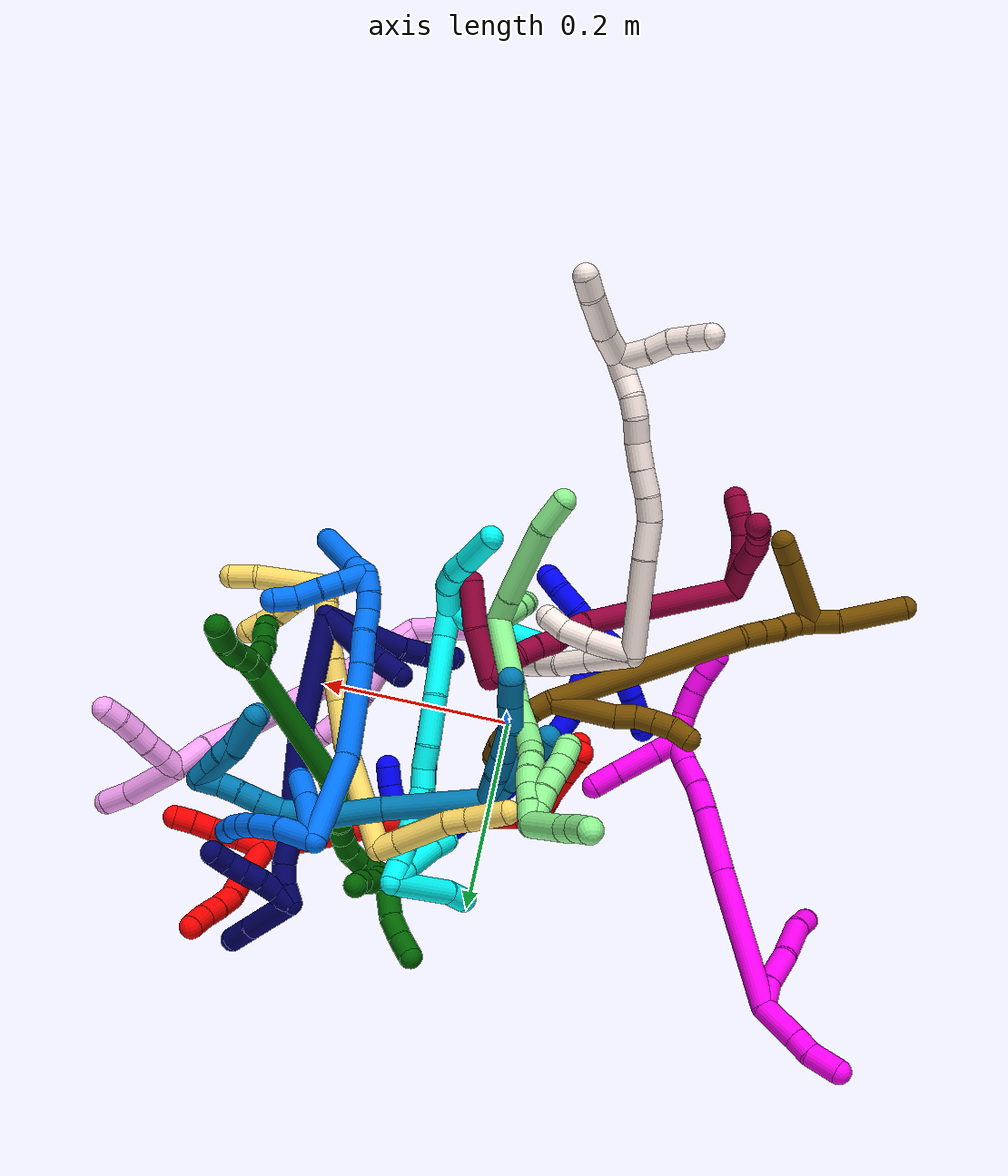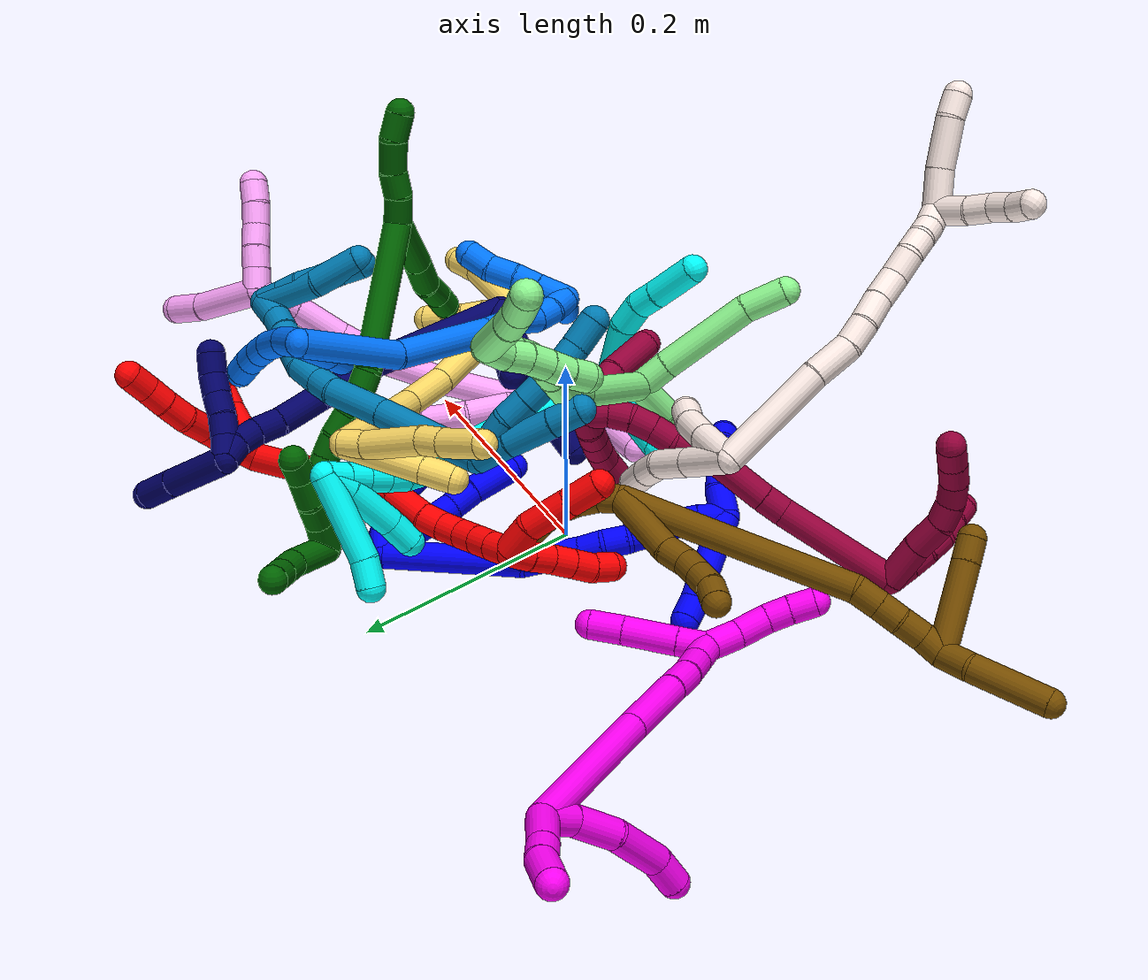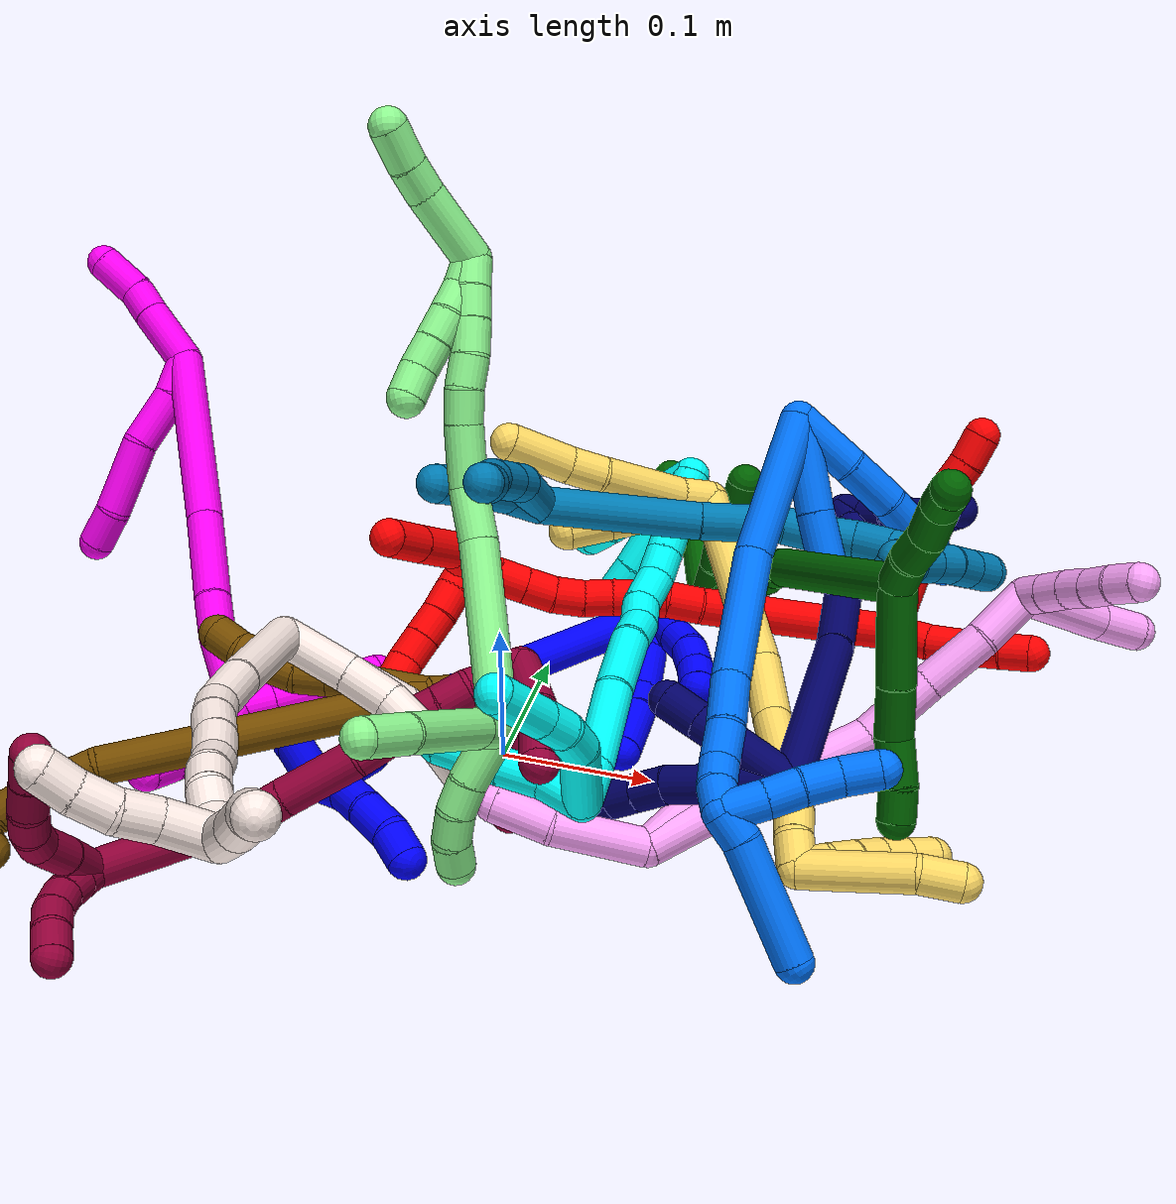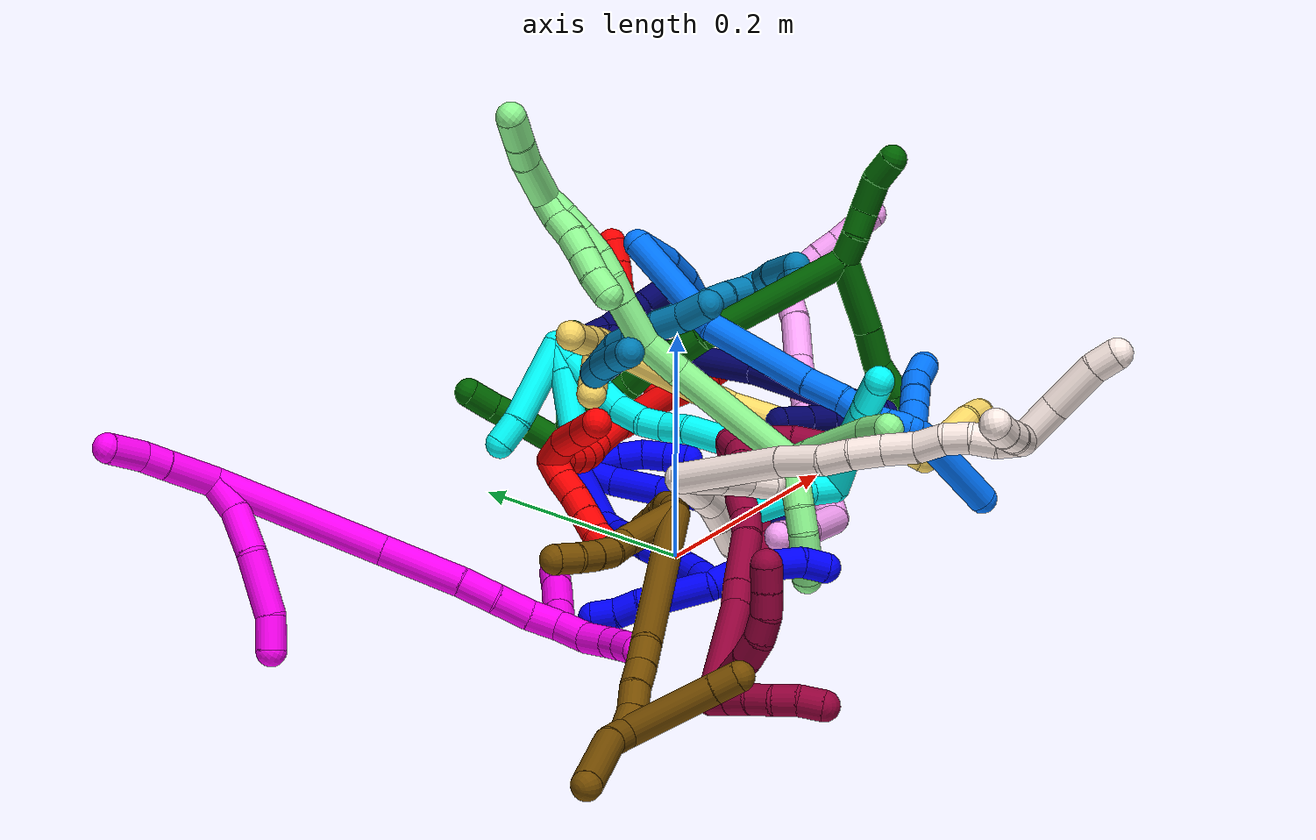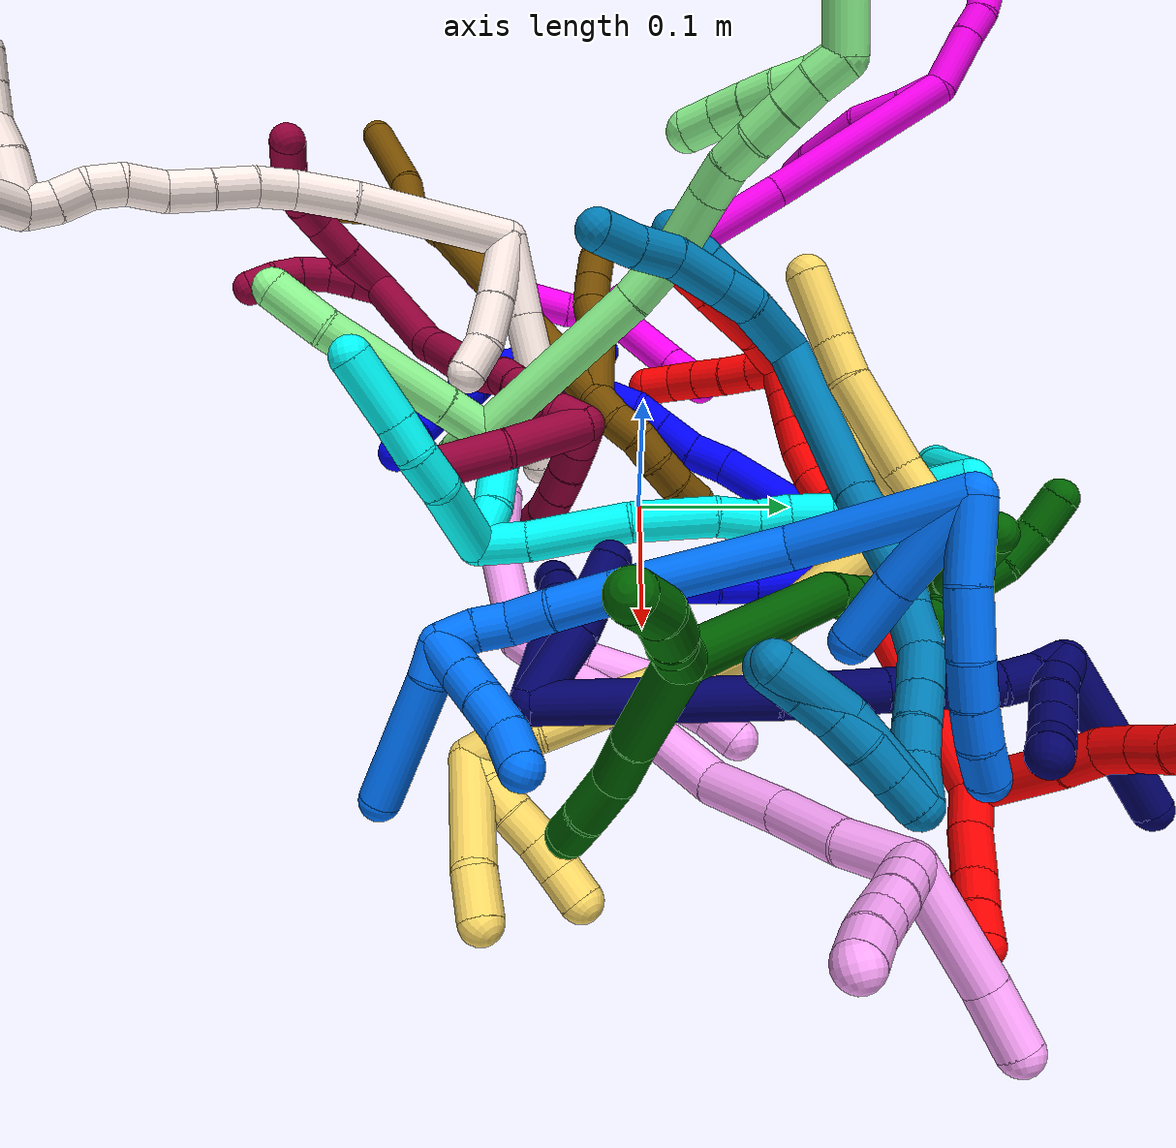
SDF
<sdf version="1.7">
 <world name="default">
  <plugin name="TubeGeneratorPlugin" filename="libtube_generator_plugin.so"/>
  <model name="photoneo_s_sensor">
   <static>1</static>
   <pose>0 0 2 1.57079 1.57079 3.14159</pose>
   <link name="link">
    <inertial><mass>0.1</mass></inertial>
    <sensor name="sensor" type="depth">
     <update_rate>30</update_rate>
     <camera>
      <horizontal_fov>1.22</horizontal_fov>
      <image><width>1920</width><height>1200</height><format>B8G8R8</format></image>
      <clip><near>0.1</near><far>4</far></clip>
      <depth_camera><output>points</output></depth_camera>
     </camera>
     <plugin name="camera_plugin" filename="libgazebo_ros_depth_camera.so">
      <baseline>0.2</baseline>
      <alwaysOn>1</alwaysOn>
      <updateRate>0.0</updateRate>
      <cameraName>camera_ir</cameraName>
      <imageTopicName>/camera/color/image_raw</imageTopicName>
      <cameraInfoTopicName>/camera/color/camera_info</cameraInfoTopicName>
      <depthImageTopicName>/camera/depth/image_raw</depthImageTopicName>
      <depthImageCameraInfoTopicName>/camera/depth/camera_info</depthImageCameraInfoTopicName>
      <pointCloudTopicName>/camera/depth/points</pointCloudTopicName>
      <frameName>fr_optical</frameName>
      <pointCloudCutoff>0.1</pointCloudCutoff>
      <pointCloudCutoffMax>2.0</pointCloudCutoffMax>
      <distortionK1>0</distortionK1>
      <distortionK2>0</distortionK2>
      <distortionK3>0</distortionK3>
      <distortionT1>0</distortionT1>
      <distortionT2>0</distortionT2>
      <CxPrime>0</CxPrime>
      <Cx>0</Cx>
      <Cy>0</Cy>
      <focalLength>0</focalLength>
      <hackBaseline>0</hackBaseline>
     </plugin>
    </sensor>
   </link>
  </model>
  <gravity>0 0 -9.8</gravity>
  <magnetic_field>6e-06 2.3e-05 -4.2e-05</magnetic_field>
  <atmosphere type="adiabatic"/>
  <physics name="default_physics" default="0" type="ode">
   <max_step_size>0.003</max_step_size>
   <real_time_factor>1</real_time_factor>
   <real_time_update_rate>1000</real_time_update_rate>
   <max_contacts>10000</max_contacts>
   <ode>
    <solver>
     <type>quick</type>
     <iters>100</iters>
     <sor>1.3</sor>
     <use_dynamic_moi_rescaling>0</use_dynamic_moi_rescaling>
    </solver>
    <constraints>
     <contact_max_correcting_vel>0</contact_max_correcting_vel>
     <contact_surface_layer>0.001</contact_surface_layer>
     <cfm>0</cfm>
     <erp>0.2</erp>
    </constraints>
   </ode>
  </physics>
  <scene><ambient>0.4 0.4 0.4 1</ambient><background>0.7 0.7 0.7 1</background><shadows>0</shadows></scene>
  <audio><device>default</device></audio>
  <spherical_coordinates>
   <surface_model>EARTH_WGS84</surface_model>
   <latitude_deg>0</latitude_deg>
   <longitude_deg>0</longitude_deg>
   <elevation>0</elevation>
   <heading_deg>0</heading_deg>
  </spherical_coordinates>
  <model name="bin">
   <static>1</static>
   <link name="bottom">
    <collision name="collision-bottom">
     <pose>0 0 -0.01 0 -0 0</pose>
     <geometry><box><size>0.8 0.6 0.02</size></box></geometry>
     <surface>
      <friction><ode><mu>100</mu><mu2>100</mu2></ode></friction>
      <contact><collide_bitmask>65535</collide_bitmask></contact>
     </surface>
    </collision>
   </link>
   <link name="west_wall">
    <collision name="collision-west_wall">
     <pose>-0.41 0 0.1 0 -0 0</pose>
     <geometry><box><size>0.02 0.6 0.2</size></box></geometry>
     <surface>
      <friction><ode><mu>100</mu><mu2>100</mu2></ode></friction>
      <contact><collide_bitmask>65535</collide_bitmask></contact>
     </surface>
    </collision>
   </link>
   <link name="east_wall">
    <collision name="collision-east_wall">
     <pose>0.41 0 0.1 0 -0 0</pose>
     <geometry><box><size>0.02 0.6 0.2</size></box></geometry>
     <surface>
      <friction><ode><mu>100</mu><mu2>100</mu2></ode></friction>
      <contact><collide_bitmask>65535</collide_bitmask></contact>
     </surface>
    </collision>
   </link>
   <link name="south_wall">
    <collision name="collision-south_wall">
     <pose>0 -0.31 0.1 0 -0 0</pose>
     <geometry><box><size>0.8 0.02 0.2</size></box></geometry>
     <surface>
      <friction><ode><mu>100</mu><mu2>100</mu2></ode></friction>
      <contact><collide_bitmask>65535</collide_bitmask></contact>
     </surface>
    </collision>
   </link>
   <link name="north_wall">
    <collision name="collision-north_wall">
     <pose>0 0.31 0.1 0 -0 0</pose>
     <geometry><box><size>0.8 0.02 0.2</size></box></geometry>
     <surface>
      <friction><ode><mu>100</mu><mu2>100</mu2></ode></friction>
      <contact><collide_bitmask>65535</collide_bitmask></contact>
     </surface>
    </collision>
   </link>
  </model>
  <model name="1">
   <static>0</static>
   <link name="1">
    <collision name="collision-cylinder-e_1_2_8">
     <pose>-0.013343 -0.004013 0.011307 0.341028 -0.838421 -0.153161</pose>
     <geometry><cylinder><radius>0.0125</radius><length>0.035889</length></cylinder></geometry>
     <surface>
      <friction><ode><mu>1.16</mu><mu2>1.16</mu2><slip1>0</slip1><slip2>0</slip2></ode></friction>
      <contact><ode><kp>1e+06</kp><kd>1</kd><max_vel>0</max_vel><min_depth>0.001</min_depth></ode></contact>
     </surface>
    </collision>
    <visual name="visual-cylinder-e_1_2_8">
     <pose>-0.013343 -0.004013 0.011307 0.341028 -0.838421 -0.153161</pose>
     <geometry><cylinder><radius>0.0125</radius><length>0.035889</length></cylinder></geometry>
     <material><ambient>0 0 1 1</ambient></material>
    </visual>
    <collision name="collision-cylinder-e_2_8_9">
     <pose>-0.045926 -0.007906 0.03513 -0.009609 -0.994059 0.005212</pose>
     <geometry><cylinder><radius>0.0125</radius><length>0.045904</length></cylinder></geometry>
     <surface>
      <friction><ode><mu>1.16</mu><mu2>1.16</mu2><slip1>0</slip1><slip2>0</slip2></ode></friction>
      <contact><ode><kp>1e+06</kp><kd>1</kd><max_vel>0</max_vel><min_depth>0.001</min_depth></ode></contact>
     </surface>
    </collision>
    <visual name="visual-cylinder-e_2_8_9">
     <pose>-0.045926 -0.007906 0.03513 -0.009609 -0.994059 0.005212</pose>
     <geometry><cylinder><radius>0.0125</radius><length>0.045904</length></cylinder></geometry>
     <material><ambient>0 0 1 1</ambient></material>
    </visual>
    <collision name="collision-cylinder-e_3_9_10">
     <pose>-0.075046 -0.006188 0.054219 -0.23831 -0.97037 0.126072</pose>
     <geometry><cylinder><radius>0.0125</radius><length>0.023951</length></cylinder></geometry>
     <surface>
      <friction><ode><mu>1.16</mu><mu2>1.16</mu2><slip1>0</slip1><slip2>0</slip2></ode></friction>
      <contact><ode><kp>1e+06</kp><kd>1</kd><max_vel>0</max_vel><min_depth>0.001</min_depth></ode></contact>
     </surface>
    </collision>
    <visual name="visual-cylinder-e_3_9_10">
     <pose>-0.075046 -0.006188 0.054219 -0.23831 -0.97037 0.126072</pose>
     <geometry><cylinder><radius>0.0125</radius><length>0.023951</length></cylinder></geometry>
     <material><ambient>0 0 1 1</ambient></material>
    </visual>
    <collision name="collision-cylinder-e_4_10_6">
     <pose>-0.104511 -0.003089 0.070986 -0.146349 -1.08654 0.088479</pose>
     <geometry><cylinder><radius>0.0125</radius><length>0.044256</length></cylinder></geometry>
     <surface>
      <friction><ode><mu>1.16</mu><mu2>1.16</mu2><slip1>0</slip1><slip2>0</slip2></ode></friction>
      <contact><ode><kp>1e+06</kp><kd>1</kd><max_vel>0</max_vel><min_depth>0.001</min_depth></ode></contact>
     </surface>
    </collision>
    <visual name="visual-cylinder-e_4_10_6">
     <pose>-0.104511 -0.003089 0.070986 -0.146349 -1.08654 0.088479</pose>
     <geometry><cylinder><radius>0.0125</radius><length>0.044256</length></cylinder></geometry>
     <material><ambient>0 0 1 1</ambient></material>
    </visual>
    <collision name="collision-cylinder-e_1_2_11">
     <pose>-0.000958 2.3e-05 0.009954 -0.002318 -0.095973 0.000111</pose>
     <geometry><cylinder><radius>0.0125</radius><length>0.02</length></cylinder></geometry>
     <surface>
      <friction><ode><mu>1.16</mu><mu2>1.16</mu2><slip1>0</slip1><slip2>0</slip2></ode></friction>
      <contact><ode><kp>1e+06</kp><kd>1</kd><max_vel>0</max_vel><min_depth>0.001</min_depth></ode></contact>
     </surface>
    </collision>
    <visual name="visual-cylinder-e_1_2_11">
     <pose>-0.000958 2.3e-05 0.009954 -0.002318 -0.095973 0.000111</pose>
     <geometry><cylinder><radius>0.0125</radius><length>0.02</length></cylinder></geometry>
     <material><ambient>0 0 1 1</ambient></material>
    </visual>
    <collision name="collision-cylinder-e_2_11_12">
     <pose>-0.0062 0.000354 0.028939 -0.034075 -0.442647 0.007668</pose>
     <geometry><cylinder><radius>0.0125</radius><length>0.02</length></cylinder></geometry>
     <surface>
      <friction><ode><mu>1.16</mu><mu2>1.16</mu2><slip1>0</slip1><slip2>0</slip2></ode></friction>
      <contact><ode><kp>1e+06</kp><kd>1</kd><max_vel>0</max_vel><min_depth>0.001</min_depth></ode></contact>
     </surface>
    </collision>
    <visual name="visual-cylinder-e_2_11_12">
     <pose>-0.0062 0.000354 0.028939 -0.034075 -0.442647 0.007668</pose>
     <geometry><cylinder><radius>0.0125</radius><length>0.02</length></cylinder></geometry>
     <material><ambient>0 0 1 1</ambient></material>
    </visual>
    <collision name="collision-cylinder-e_3_12_13">
     <pose>-0.01491 0.000783 0.046936 -0.013487 -0.45864 0.003148</pose>
     <geometry><cylinder><radius>0.0125</radius><length>0.02</length></cylinder></geometry>
     <surface>
      <friction><ode><mu>1.16</mu><mu2>1.16</mu2><slip1>0</slip1><slip2>0</slip2></ode></friction>
      <contact><ode><kp>1e+06</kp><kd>1</kd><max_vel>0</max_vel><min_depth>0.001</min_depth></ode></contact>
     </surface>
    </collision>
    <visual name="visual-cylinder-e_3_12_13">
     <pose>-0.01491 0.000783 0.046936 -0.013487 -0.45864 0.003148</pose>
     <geometry><cylinder><radius>0.0125</radius><length>0.02</length></cylinder></geometry>
     <material><ambient>0 0 1 1</ambient></material>
    </visual>
    <collision name="collision-cylinder-e_4_13_14">
     <pose>-0.025838 -0.000329 0.0634 0.162894 -0.707634 -0.060282</pose>
     <geometry><cylinder><radius>0.0125</radius><length>0.02</length></cylinder></geometry>
     <surface>
      <friction><ode><mu>1.16</mu><mu2>1.16</mu2><slip1>0</slip1><slip2>0</slip2></ode></friction>
      <contact><ode><kp>1e+06</kp><kd>1</kd><max_vel>0</max_vel><min_depth>0.001</min_depth></ode></contact>
     </surface>
    </collision>
    <visual name="visual-cylinder-e_4_13_14">
     <pose>-0.025838 -0.000329 0.0634 0.162894 -0.707634 -0.060282</pose>
     <geometry><cylinder><radius>0.0125</radius><length>0.02</length></cylinder></geometry>
     <material><ambient>0 0 1 1</ambient></material>
    </visual>
    <collision name="collision-cylinder-e_5_14_5">
     <pose>-0.039742 -0.001766 0.077617 0.030472 -0.833616 -0.013492</pose>
     <geometry><cylinder><radius>0.0125</radius><length>0.02</length></cylinder></geometry>
     <surface>
      <friction><ode><mu>1.16</mu><mu2>1.16</mu2><slip1>0</slip1><slip2>0</slip2></ode></friction>
      <contact><ode><kp>1e+06</kp><kd>1</kd><max_vel>0</max_vel><min_depth>0.001</min_depth></ode></contact>
     </surface>
    </collision>
    <visual name="visual-cylinder-e_5_14_5">
     <pose>-0.039742 -0.001766 0.077617 0.030472 -0.833616 -0.013492</pose>
     <geometry><cylinder><radius>0.0125</radius><length>0.02</length></cylinder></geometry>
     <material><ambient>0 0 1 1</ambient></material>
    </visual>
    <collision name="collision-cylinder-e_1_2_15">
     <pose>-0.056026 0.010728 -0.015079 -2.52326 -1.25177 2.30942</pose>
     <geometry><cylinder><radius>0.0125</radius><length>0.118007</length></cylinder></geometry>
     <surface>
      <friction><ode><mu>1.16</mu><mu2>1.16</mu2><slip1>0</slip1><slip2>0</slip2></ode></friction>
      <contact><ode><kp>1e+06</kp><kd>1</kd><max_vel>0</max_vel><min_depth>0.001</min_depth></ode></contact>
     </surface>
    </collision>
    <visual name="visual-cylinder-e_1_2_15">
     <pose>-0.056026 0.010728 -0.015079 -2.52326 -1.25177 2.30942</pose>
     <geometry><cylinder><radius>0.0125</radius><length>0.118007</length></cylinder></geometry>
     <material><ambient>0 0 1 1</ambient></material>
    </visual>
    <collision name="collision-cylinder-e_2_15_16">
     <pose>-0.124673 0.024441 -0.029839 -1.464 -1.3372 1.23457</pose>
     <geometry><cylinder><radius>0.0125</radius><length>0.025945</length></cylinder></geometry>
     <surface>
      <friction><ode><mu>1.16</mu><mu2>1.16</mu2><slip1>0</slip1><slip2>0</slip2></ode></friction>
      <contact><ode><kp>1e+06</kp><kd>1</kd><max_vel>0</max_vel><min_depth>0.001</min_depth></ode></contact>
     </surface>
    </collision>
    <visual name="visual-cylinder-e_2_15_16">
     <pose>-0.124673 0.024441 -0.029839 -1.464 -1.3372 1.23457</pose>
     <geometry><cylinder><radius>0.0125</radius><length>0.025945</length></cylinder></geometry>
     <material><ambient>0 0 1 1</ambient></material>
    </visual>
    <collision name="collision-cylinder-e_3_16_17">
     <pose>-0.149087 0.033046 -0.03081 -1.7967 -1.11608 1.32976</pose>
     <geometry><cylinder><radius>0.0125</radius><length>0.026255</length></cylinder></geometry>
     <surface>
      <friction><ode><mu>1.16</mu><mu2>1.16</mu2><slip1>0</slip1><slip2>0</slip2></ode></friction>
      <contact><ode><kp>1e+06</kp><kd>1</kd><max_vel>0</max_vel><min_depth>0.001</min_depth></ode></contact>
     </surface>
    </collision>
    <visual name="visual-cylinder-e_3_16_17">
     <pose>-0.149087 0.033046 -0.03081 -1.7967 -1.11608 1.32976</pose>
     <geometry><cylinder><radius>0.0125</radius><length>0.026255</length></cylinder></geometry>
     <material><ambient>0 0 1 1</ambient></material>
    </visual>
    <collision name="collision-cylinder-e_4_17_18">
     <pose>-0.169692 0.0436 -0.032539 -1.65923 -1.05861 1.13741</pose>
     <geometry><cylinder><radius>0.0125</radius><length>0.020219</length></cylinder></geometry>
     <surface>
      <friction><ode><mu>1.16</mu><mu2>1.16</mu2><slip1>0</slip1><slip2>0</slip2></ode></friction>
      <contact><ode><kp>1e+06</kp><kd>1</kd><max_vel>0</max_vel><min_depth>0.001</min_depth></ode></contact>
     </surface>
    </collision>
    <visual name="visual-cylinder-e_4_17_18">
     <pose>-0.169692 0.0436 -0.032539 -1.65923 -1.05861 1.13741</pose>
     <geometry><cylinder><radius>0.0125</radius><length>0.020219</length></cylinder></geometry>
     <material><ambient>0 0 1 1</ambient></material>
    </visual>
    <collision name="collision-cylinder-e_5_18_19">
     <pose>-0.188415 0.050576 -0.032524 -1.35246 -1.3629 1.15392</pose>
     <geometry><cylinder><radius>0.0125</radius><length>0.020257</length></cylinder></geometry>
     <surface>
      <friction><ode><mu>1.16</mu><mu2>1.16</mu2><slip1>0</slip1><slip2>0</slip2></ode></friction>
      <contact><ode><kp>1e+06</kp><kd>1</kd><max_vel>0</max_vel><min_depth>0.001</min_depth></ode></contact>
     </surface>
    </collision>
    <visual name="visual-cylinder-e_5_18_19">
     <pose>-0.188415 0.050576 -0.032524 -1.35246 -1.3629 1.15392</pose>
     <geometry><cylinder><radius>0.0125</radius><length>0.020257</length></cylinder></geometry>
     <material><ambient>0 0 1 1</ambient></material>
    </visual>
    <collision name="collision-cylinder-e_6_19_20">
     <pose>-0.208243 0.052422 -0.02924 0.068878 -1.29209 -0.051942</pose>
     <geometry><cylinder><radius>0.0125</radius><length>0.02063</length></cylinder></geometry>
     <surface>
      <friction><ode><mu>1.16</mu><mu2>1.16</mu2><slip1>0</slip1><slip2>0</slip2></ode></friction>
      <contact><ode><kp>1e+06</kp><kd>1</kd><max_vel>0</max_vel><min_depth>0.001</min_depth></ode></contact>
     </surface>
    </collision>
    <visual name="visual-cylinder-e_6_19_20">
     <pose>-0.208243 0.052422 -0.02924 0.068878 -1.29209 -0.051942</pose>
     <geometry><cylinder><radius>0.0125</radius><length>0.02063</length></cylinder></geometry>
     <material><ambient>0 0 1 1</ambient></material>
    </visual>
    <collision name="collision-cylinder-e_7_20_21">
     <pose>-0.229685 0.051806 -0.022956 0.121326 -1.27771 -0.090166</pose>
     <geometry><cylinder><radius>0.0125</radius><length>0.024079</length></cylinder></geometry>
     <surface>
      <friction><ode><mu>1.16</mu><mu2>1.16</mu2><slip1>0</slip1><slip2>0</slip2></ode></friction>
      <contact><ode><kp>1e+06</kp><kd>1</kd><max_vel>0</max_vel><min_depth>0.001</min_depth></ode></contact>
     </surface>
    </collision>
    <visual name="visual-cylinder-e_7_20_21">
     <pose>-0.229685 0.051806 -0.022956 0.121326 -1.27771 -0.090166</pose>
     <geometry><cylinder><radius>0.0125</radius><length>0.024079</length></cylinder></geometry>
     <material><ambient>0 0 1 1</ambient></material>
    </visual>
    <collision name="collision-cylinder-e_8_21_22">
     <pose>-0.251798 0.053555 -0.018974 -1.33154 -1.36282 1.13429</pose>
     <geometry><cylinder><radius>0.0125</radius><length>0.021639</length></cylinder></geometry>
     <surface>
      <friction><ode><mu>1.16</mu><mu2>1.16</mu2><slip1>0</slip1><slip2>0</slip2></ode></friction>
      <contact><ode><kp>1e+06</kp><kd>1</kd><max_vel>0</max_vel><min_depth>0.001</min_depth></ode></contact>
     </surface>
    </collision>
    <visual name="visual-cylinder-e_8_21_22">
     <pose>-0.251798 0.053555 -0.018974 -1.33154 -1.36282 1.13429</pose>
     <geometry><cylinder><radius>0.0125</radius><length>0.021639</length></cylinder></geometry>
     <material><ambient>0 0 1 1</ambient></material>
    </visual>
    <collision name="collision-cylinder-e_9_22_1">
     <pose>-0.273426 0.058445 -0.020049 -2.10377 -1.29232 1.8453</pose>
     <geometry><cylinder><radius>0.0125</radius><length>0.022969</length></cylinder></geometry>
     <surface>
      <friction><ode><mu>1.16</mu><mu2>1.16</mu2><slip1>0</slip1><slip2>0</slip2></ode></friction>
      <contact><ode><kp>1e+06</kp><kd>1</kd><max_vel>0</max_vel><min_depth>0.001</min_depth></ode></contact>
     </surface>
    </collision>
    <visual name="visual-cylinder-e_9_22_1">
     <pose>-0.273426 0.058445 -0.020049 -2.10377 -1.29232 1.8453</pose>
     <geometry><cylinder><radius>0.0125</radius><length>0.022969</length></cylinder></geometry>
     <material><ambient>0 0 1 1</ambient></material>
    </visual>
    <collision name="collision-cylinder-e_1_1_23">
     <pose>-0.270676 0.055751 -0.047433 2.93464 0.482328 2.34255</pose>
     <geometry><cylinder><radius>0.0125</radius><length>0.059469</length></cylinder></geometry>
     <surface>
      <friction><ode><mu>1.16</mu><mu2>1.16</mu2><slip1>0</slip1><slip2>0</slip2></ode></friction>
      <contact><ode><kp>1e+06</kp><kd>1</kd><max_vel>0</max_vel><min_depth>0.001</min_depth></ode></contact>
     </surface>
    </collision>
    <visual name="visual-cylinder-e_1_1_23">
     <pose>-0.270676 0.055751 -0.047433 2.93464 0.482328 2.34255</pose>
     <geometry><cylinder><radius>0.0125</radius><length>0.059469</length></cylinder></geometry>
     <material><ambient>0 0 1 1</ambient></material>
    </visual>
    <collision name="collision-cylinder-e_2_23_24">
     <pose>-0.252407 0.047053 -0.081766 2.77493 0.454537 1.79</pose>
     <geometry><cylinder><radius>0.0125</radius><length>0.020395</length></cylinder></geometry>
     <surface>
      <friction><ode><mu>1.16</mu><mu2>1.16</mu2><slip1>0</slip1><slip2>0</slip2></ode></friction>
      <contact><ode><kp>1e+06</kp><kd>1</kd><max_vel>0</max_vel><min_depth>0.001</min_depth></ode></contact>
     </surface>
    </collision>
    <visual name="visual-cylinder-e_2_23_24">
     <pose>-0.252407 0.047053 -0.081766 2.77493 0.454537 1.79</pose>
     <geometry><cylinder><radius>0.0125</radius><length>0.020395</length></cylinder></geometry>
     <material><ambient>0 0 1 1</ambient></material>
    </visual>
    <collision name="collision-cylinder-e_3_24_4">
     <pose>-0.242497 0.042494 -0.0987 2.99062 0.569926 2.63626</pose>
     <geometry><cylinder><radius>0.0125</radius><length>0.020136</length></cylinder></geometry>
     <surface>
      <friction><ode><mu>1.16</mu><mu2>1.16</mu2><slip1>0</slip1><slip2>0</slip2></ode></friction>
      <contact><ode><kp>1e+06</kp><kd>1</kd><max_vel>0</max_vel><min_depth>0.001</min_depth></ode></contact>
     </surface>
    </collision>
    <visual name="visual-cylinder-e_3_24_4">
     <pose>-0.242497 0.042494 -0.0987 2.99062 0.569926 2.63626</pose>
     <geometry><cylinder><radius>0.0125</radius><length>0.020136</length></cylinder></geometry>
     <material><ambient>0 0 1 1</ambient></material>
    </visual>
    <collision name="collision-cylinder-e_1_1_25">
     <pose>-0.284517 0.061109 -0.008097 0.004024 -0.003589 -7e-06</pose>
     <geometry><cylinder><radius>0.0125</radius><length>0.027112</length></cylinder></geometry>
     <surface>
      <friction><ode><mu>1.16</mu><mu2>1.16</mu2><slip1>0</slip1><slip2>0</slip2></ode></friction>
      <contact><ode><kp>1e+06</kp><kd>1</kd><max_vel>0</max_vel><min_depth>0.001</min_depth></ode></contact>
     </surface>
    </collision>
    <visual name="visual-cylinder-e_1_1_25">
     <pose>-0.284517 0.061109 -0.008097 0.004024 -0.003589 -7e-06</pose>
     <geometry><cylinder><radius>0.0125</radius><length>0.027112</length></cylinder></geometry>
     <material><ambient>0 0 1 1</ambient></material>
    </visual>
    <collision name="collision-cylinder-e_2_25_26">
     <pose>-0.288227 0.060898 0.017951 0.01251 -0.285127 -0.001796</pose>
     <geometry><cylinder><radius>0.0125</radius><length>0.026037</length></cylinder></geometry>
     <surface>
      <friction><ode><mu>1.16</mu><mu2>1.16</mu2><slip1>0</slip1><slip2>0</slip2></ode></friction>
      <contact><ode><kp>1e+06</kp><kd>1</kd><max_vel>0</max_vel><min_depth>0.001</min_depth></ode></contact>
     </surface>
    </collision>
    <visual name="visual-cylinder-e_2_25_26">
     <pose>-0.288227 0.060898 0.017951 0.01251 -0.285127 -0.001796</pose>
     <geometry><cylinder><radius>0.0125</radius><length>0.026037</length></cylinder></geometry>
     <material><ambient>0 0 1 1</ambient></material>
    </visual>
    <collision name="collision-cylinder-e_3_26_27">
     <pose>-0.294961 0.058091 0.042948 0.208876 -0.235856 -0.024836</pose>
     <geometry><cylinder><radius>0.0125</radius><length>0.026294</length></cylinder></geometry>
     <surface>
      <friction><ode><mu>1.16</mu><mu2>1.16</mu2><slip1>0</slip1><slip2>0</slip2></ode></friction>
      <contact><ode><kp>1e+06</kp><kd>1</kd><max_vel>0</max_vel><min_depth>0.001</min_depth></ode></contact>
     </surface>
    </collision>
    <visual name="visual-cylinder-e_3_26_27">
     <pose>-0.294961 0.058091 0.042948 0.208876 -0.235856 -0.024836</pose>
     <geometry><cylinder><radius>0.0125</radius><length>0.026294</length></cylinder></geometry>
     <material><ambient>0 0 1 1</ambient></material>
    </visual>
    <collision name="collision-cylinder-e_4_27_3">
     <pose>-0.301503 0.05054 0.063795 0.531161 -0.344358 -0.094534</pose>
     <geometry><cylinder><radius>0.0125</radius><length>0.020557</length></cylinder></geometry>
     <surface>
      <friction><ode><mu>1.16</mu><mu2>1.16</mu2><slip1>0</slip1><slip2>0</slip2></ode></friction>
      <contact><ode><kp>1e+06</kp><kd>1</kd><max_vel>0</max_vel><min_depth>0.001</min_depth></ode></contact>
     </surface>
    </collision>
    <visual name="visual-cylinder-e_4_27_3">
     <pose>-0.301503 0.05054 0.063795 0.531161 -0.344358 -0.094534</pose>
     <geometry><cylinder><radius>0.0125</radius><length>0.020557</length></cylinder></geometry>
     <material><ambient>0 0 1 1</ambient></material>
    </visual>
    <collision name="collision-sphere-3">
     <pose>-0.304973 0.045639 0.072137 0 -0 0</pose>
     <geometry><sphere><radius>0.0125</radius></sphere></geometry>
     <surface>
      <friction><ode><mu>1.16</mu><mu2>1.16</mu2><slip1>0</slip1><slip2>0</slip2></ode></friction>
      <contact><ode><kp>1e+06</kp><kd>1</kd><max_vel>0</max_vel><min_depth>0.001</min_depth></ode></contact>
     </surface>
    </collision>
    <visual name="visual-sphere-3">
     <pose>-0.304973 0.045639 0.072137 0 -0 0</pose>
     <geometry><sphere><radius>0.0125</radius></sphere></geometry>
     <material><ambient>0 0 1 1</ambient></material>
    </visual>
    <collision name="collision-sphere-27">
     <pose>-0.298033 0.05544 0.055453 0 -0 0</pose>
     <geometry><sphere><radius>0.0125</radius></sphere></geometry>
     <surface>
      <friction><ode><mu>1.16</mu><mu2>1.16</mu2><slip1>0</slip1><slip2>0</slip2></ode></friction>
      <contact><ode><kp>1e+06</kp><kd>1</kd><max_vel>0</max_vel><min_depth>0.001</min_depth></ode></contact>
     </surface>
    </collision>
    <visual name="visual-sphere-27">
     <pose>-0.298033 0.05544 0.055453 0 -0 0</pose>
     <geometry><sphere><radius>0.0125</radius></sphere></geometry>
     <material><ambient>0 0 1 1</ambient></material>
    </visual>
    <collision name="collision-sphere-26">
     <pose>-0.291889 0.060742 0.030443 0 -0 0</pose>
     <geometry><sphere><radius>0.0125</radius></sphere></geometry>
     <surface>
      <friction><ode><mu>1.16</mu><mu2>1.16</mu2><slip1>0</slip1><slip2>0</slip2></ode></friction>
      <contact><ode><kp>1e+06</kp><kd>1</kd><max_vel>0</max_vel><min_depth>0.001</min_depth></ode></contact>
     </surface>
    </collision>
    <visual name="visual-sphere-26">
     <pose>-0.291889 0.060742 0.030443 0 -0 0</pose>
     <geometry><sphere><radius>0.0125</radius></sphere></geometry>
     <material><ambient>0 0 1 1</ambient></material>
    </visual>
    <collision name="collision-sphere-25">
     <pose>-0.284565 0.061054 0.005459 0 -0 0</pose>
     <geometry><sphere><radius>0.0125</radius></sphere></geometry>
     <surface>
      <friction><ode><mu>1.16</mu><mu2>1.16</mu2><slip1>0</slip1><slip2>0</slip2></ode></friction>
      <contact><ode><kp>1e+06</kp><kd>1</kd><max_vel>0</max_vel><min_depth>0.001</min_depth></ode></contact>
     </surface>
    </collision>
    <visual name="visual-sphere-25">
     <pose>-0.284565 0.061054 0.005459 0 -0 0</pose>
     <geometry><sphere><radius>0.0125</radius></sphere></geometry>
     <material><ambient>0 0 1 1</ambient></material>
    </visual>
    <collision name="collision-sphere-4">
     <pose>-0.237065 0.041219 -0.10708 0 -0 0</pose>
     <geometry><sphere><radius>0.0125</radius></sphere></geometry>
     <surface>
      <friction><ode><mu>1.16</mu><mu2>1.16</mu2><slip1>0</slip1><slip2>0</slip2></ode></friction>
      <contact><ode><kp>1e+06</kp><kd>1</kd><max_vel>0</max_vel><min_depth>0.001</min_depth></ode></contact>
     </surface>
    </collision>
    <visual name="visual-sphere-4">
     <pose>-0.237065 0.041219 -0.10708 0 -0 0</pose>
     <geometry><sphere><radius>0.0125</radius></sphere></geometry>
     <material><ambient>0 0 1 1</ambient></material>
    </visual>
    <collision name="collision-sphere-24">
     <pose>-0.24793 0.043769 -0.090319 0 -0 0</pose>
     <geometry><sphere><radius>0.0125</radius></sphere></geometry>
     <surface>
      <friction><ode><mu>1.16</mu><mu2>1.16</mu2><slip1>0</slip1><slip2>0</slip2></ode></friction>
      <contact><ode><kp>1e+06</kp><kd>1</kd><max_vel>0</max_vel><min_depth>0.001</min_depth></ode></contact>
     </surface>
    </collision>
    <visual name="visual-sphere-24">
     <pose>-0.24793 0.043769 -0.090319 0 -0 0</pose>
     <geometry><sphere><radius>0.0125</radius></sphere></geometry>
     <material><ambient>0 0 1 1</ambient></material>
    </visual>
    <collision name="collision-sphere-23">
     <pose>-0.256884 0.050338 -0.073213 0 -0 0</pose>
     <geometry><sphere><radius>0.0125</radius></sphere></geometry>
     <surface>
      <friction><ode><mu>1.16</mu><mu2>1.16</mu2><slip1>0</slip1><slip2>0</slip2></ode></friction>
      <contact><ode><kp>1e+06</kp><kd>1</kd><max_vel>0</max_vel><min_depth>0.001</min_depth></ode></contact>
     </surface>
    </collision>
    <visual name="visual-sphere-23">
     <pose>-0.256884 0.050338 -0.073213 0 -0 0</pose>
     <geometry><sphere><radius>0.0125</radius></sphere></geometry>
     <material><ambient>0 0 1 1</ambient></material>
    </visual>
    <collision name="collision-sphere-1">
     <pose>-0.284468 0.061164 -0.021653 0 -0 0</pose>
     <geometry><sphere><radius>0.0125</radius></sphere></geometry>
     <surface>
      <friction><ode><mu>1.16</mu><mu2>1.16</mu2><slip1>0</slip1><slip2>0</slip2></ode></friction>
      <contact><ode><kp>1e+06</kp><kd>1</kd><max_vel>0</max_vel><min_depth>0.001</min_depth></ode></contact>
     </surface>
    </collision>
    <visual name="visual-sphere-1">
     <pose>-0.284468 0.061164 -0.021653 0 -0 0</pose>
     <geometry><sphere><radius>0.0125</radius></sphere></geometry>
     <material><ambient>0 0 1 1</ambient></material>
    </visual>
    <collision name="collision-sphere-22">
     <pose>-0.262384 0.055725 -0.018445 0 -0 0</pose>
     <geometry><sphere><radius>0.0125</radius></sphere></geometry>
     <surface>
      <friction><ode><mu>1.16</mu><mu2>1.16</mu2><slip1>0</slip1><slip2>0</slip2></ode></friction>
      <contact><ode><kp>1e+06</kp><kd>1</kd><max_vel>0</max_vel><min_depth>0.001</min_depth></ode></contact>
     </surface>
    </collision>
    <visual name="visual-sphere-22">
     <pose>-0.262384 0.055725 -0.018445 0 -0 0</pose>
     <geometry><sphere><radius>0.0125</radius></sphere></geometry>
     <material><ambient>0 0 1 1</ambient></material>
    </visual>
    <collision name="collision-sphere-21">
     <pose>-0.241212 0.051385 -0.019504 0 -0 0</pose>
     <geometry><sphere><radius>0.0125</radius></sphere></geometry>
     <surface>
      <friction><ode><mu>1.16</mu><mu2>1.16</mu2><slip1>0</slip1><slip2>0</slip2></ode></friction>
      <contact><ode><kp>1e+06</kp><kd>1</kd><max_vel>0</max_vel><min_depth>0.001</min_depth></ode></contact>
     </surface>
    </collision>
    <visual name="visual-sphere-21">
     <pose>-0.241212 0.051385 -0.019504 0 -0 0</pose>
     <geometry><sphere><radius>0.0125</radius></sphere></geometry>
     <material><ambient>0 0 1 1</ambient></material>
    </visual>
    <collision name="collision-sphere-11">
     <pose>-0.001917 4.6e-05 0.019908 0 -0 0</pose>
     <geometry><sphere><radius>0.0125</radius></sphere></geometry>
     <surface>
      <friction><ode><mu>1.16</mu><mu2>1.16</mu2><slip1>0</slip1><slip2>0</slip2></ode></friction>
      <contact><ode><kp>1e+06</kp><kd>1</kd><max_vel>0</max_vel><min_depth>0.001</min_depth></ode></contact>
     </surface>
    </collision>
    <visual name="visual-sphere-11">
     <pose>-0.001917 4.6e-05 0.019908 0 -0 0</pose>
     <geometry><sphere><radius>0.0125</radius></sphere></geometry>
     <material><ambient>0 0 1 1</ambient></material>
    </visual>
    <collision name="collision-sphere-6">
     <pose>-0.124095 -0.001586 0.081177 0 -0 0</pose>
     <geometry><sphere><radius>0.0125</radius></sphere></geometry>
     <surface>
      <friction><ode><mu>1.16</mu><mu2>1.16</mu2><slip1>0</slip1><slip2>0</slip2></ode></friction>
      <contact><ode><kp>1e+06</kp><kd>1</kd><max_vel>0</max_vel><min_depth>0.001</min_depth></ode></contact>
     </surface>
    </collision>
    <visual name="visual-sphere-6">
     <pose>-0.124095 -0.001586 0.081177 0 -0 0</pose>
     <geometry><sphere><radius>0.0125</radius></sphere></geometry>
     <material><ambient>0 0 1 1</ambient></material>
    </visual>
    <collision name="collision-sphere-10">
     <pose>-0.084927 -0.004591 0.060794 0 -0 0</pose>
     <geometry><sphere><radius>0.0125</radius></sphere></geometry>
     <surface>
      <friction><ode><mu>1.16</mu><mu2>1.16</mu2><slip1>0</slip1><slip2>0</slip2></ode></friction>
      <contact><ode><kp>1e+06</kp><kd>1</kd><max_vel>0</max_vel><min_depth>0.001</min_depth></ode></contact>
     </surface>
    </collision>
    <visual name="visual-sphere-10">
     <pose>-0.084927 -0.004591 0.060794 0 -0 0</pose>
     <geometry><sphere><radius>0.0125</radius></sphere></geometry>
     <material><ambient>0 0 1 1</ambient></material>
    </visual>
    <collision name="collision-sphere-9">
     <pose>-0.065165 -0.007785 0.047645 0 -0 0</pose>
     <geometry><sphere><radius>0.0125</radius></sphere></geometry>
     <surface>
      <friction><ode><mu>1.16</mu><mu2>1.16</mu2><slip1>0</slip1><slip2>0</slip2></ode></friction>
      <contact><ode><kp>1e+06</kp><kd>1</kd><max_vel>0</max_vel><min_depth>0.001</min_depth></ode></contact>
     </surface>
    </collision>
    <visual name="visual-sphere-9">
     <pose>-0.065165 -0.007785 0.047645 0 -0 0</pose>
     <geometry><sphere><radius>0.0125</radius></sphere></geometry>
     <material><ambient>0 0 1 1</ambient></material>
    </visual>
    <collision name="collision-sphere-2">
     <geometry><sphere><radius>0.0125</radius></sphere></geometry>
     <surface>
      <friction><ode><mu>1.16</mu><mu2>1.16</mu2><slip1>0</slip1><slip2>0</slip2></ode></friction>
      <contact><ode><kp>1e+06</kp><kd>1</kd><max_vel>0</max_vel><min_depth>0.001</min_depth></ode></contact>
     </surface>
    </collision>
    <visual name="visual-sphere-2">
     <geometry><sphere><radius>0.0125</radius></sphere></geometry>
     <material><ambient>0 0 1 1</ambient></material>
    </visual>
    <collision name="collision-sphere-19">
     <pose>-0.198326 0.052617 -0.032071 0 -0 0</pose>
     <geometry><sphere><radius>0.0125</radius></sphere></geometry>
     <surface>
      <friction><ode><mu>1.16</mu><mu2>1.16</mu2><slip1>0</slip1><slip2>0</slip2></ode></friction>
      <contact><ode><kp>1e+06</kp><kd>1</kd><max_vel>0</max_vel><min_depth>0.001</min_depth></ode></contact>
     </surface>
    </collision>
    <visual name="visual-sphere-19">
     <pose>-0.198326 0.052617 -0.032071 0 -0 0</pose>
     <geometry><sphere><radius>0.0125</radius></sphere></geometry>
     <material><ambient>0 0 1 1</ambient></material>
    </visual>
    <collision name="collision-sphere-8">
     <pose>-0.026687 -0.008026 0.022615 0 -0 0</pose>
     <geometry><sphere><radius>0.0125</radius></sphere></geometry>
     <surface>
      <friction><ode><mu>1.16</mu><mu2>1.16</mu2><slip1>0</slip1><slip2>0</slip2></ode></friction>
      <contact><ode><kp>1e+06</kp><kd>1</kd><max_vel>0</max_vel><min_depth>0.001</min_depth></ode></contact>
     </surface>
    </collision>
    <visual name="visual-sphere-8">
     <pose>-0.026687 -0.008026 0.022615 0 -0 0</pose>
     <geometry><sphere><radius>0.0125</radius></sphere></geometry>
     <material><ambient>0 0 1 1</ambient></material>
    </visual>
    <collision name="collision-sphere-12">
     <pose>-0.010483 0.000662 0.03797 0 -0 0</pose>
     <geometry><sphere><radius>0.0125</radius></sphere></geometry>
     <surface>
      <friction><ode><mu>1.16</mu><mu2>1.16</mu2><slip1>0</slip1><slip2>0</slip2></ode></friction>
      <contact><ode><kp>1e+06</kp><kd>1</kd><max_vel>0</max_vel><min_depth>0.001</min_depth></ode></contact>
     </surface>
    </collision>
    <visual name="visual-sphere-12">
     <pose>-0.010483 0.000662 0.03797 0 -0 0</pose>
     <geometry><sphere><radius>0.0125</radius></sphere></geometry>
     <material><ambient>0 0 1 1</ambient></material>
    </visual>
    <collision name="collision-sphere-13">
     <pose>-0.019338 0.000904 0.055901 0 -0 0</pose>
     <geometry><sphere><radius>0.0125</radius></sphere></geometry>
     <surface>
      <friction><ode><mu>1.16</mu><mu2>1.16</mu2><slip1>0</slip1><slip2>0</slip2></ode></friction>
      <contact><ode><kp>1e+06</kp><kd>1</kd><max_vel>0</max_vel><min_depth>0.001</min_depth></ode></contact>
     </surface>
    </collision>
    <visual name="visual-sphere-13">
     <pose>-0.019338 0.000904 0.055901 0 -0 0</pose>
     <geometry><sphere><radius>0.0125</radius></sphere></geometry>
     <material><ambient>0 0 1 1</ambient></material>
    </visual>
    <collision name="collision-sphere-14">
     <pose>-0.032339 -0.001561 0.070898 0 -0 0</pose>
     <geometry><sphere><radius>0.0125</radius></sphere></geometry>
     <surface>
      <friction><ode><mu>1.16</mu><mu2>1.16</mu2><slip1>0</slip1><slip2>0</slip2></ode></friction>
      <contact><ode><kp>1e+06</kp><kd>1</kd><max_vel>0</max_vel><min_depth>0.001</min_depth></ode></contact>
     </surface>
    </collision>
    <visual name="visual-sphere-14">
     <pose>-0.032339 -0.001561 0.070898 0 -0 0</pose>
     <geometry><sphere><radius>0.0125</radius></sphere></geometry>
     <material><ambient>0 0 1 1</ambient></material>
    </visual>
    <collision name="collision-sphere-5">
     <pose>-0.047146 -0.001971 0.084336 0 -0 0</pose>
     <geometry><sphere><radius>0.0125</radius></sphere></geometry>
     <surface>
      <friction><ode><mu>1.16</mu><mu2>1.16</mu2><slip1>0</slip1><slip2>0</slip2></ode></friction>
      <contact><ode><kp>1e+06</kp><kd>1</kd><max_vel>0</max_vel><min_depth>0.001</min_depth></ode></contact>
     </surface>
    </collision>
    <visual name="visual-sphere-5">
     <pose>-0.047146 -0.001971 0.084336 0 -0 0</pose>
     <geometry><sphere><radius>0.0125</radius></sphere></geometry>
     <material><ambient>0 0 1 1</ambient></material>
    </visual>
    <collision name="collision-sphere-15">
     <pose>-0.112053 0.021455 -0.030159 0 -0 0</pose>
     <geometry><sphere><radius>0.0125</radius></sphere></geometry>
     <surface>
      <friction><ode><mu>1.16</mu><mu2>1.16</mu2><slip1>0</slip1><slip2>0</slip2></ode></friction>
      <contact><ode><kp>1e+06</kp><kd>1</kd><max_vel>0</max_vel><min_depth>0.001</min_depth></ode></contact>
     </surface>
    </collision>
    <visual name="visual-sphere-15">
     <pose>-0.112053 0.021455 -0.030159 0 -0 0</pose>
     <geometry><sphere><radius>0.0125</radius></sphere></geometry>
     <material><ambient>0 0 1 1</ambient></material>
    </visual>
    <collision name="collision-sphere-16">
     <pose>-0.137293 0.027426 -0.029519 0 -0 0</pose>
     <geometry><sphere><radius>0.0125</radius></sphere></geometry>
     <surface>
      <friction><ode><mu>1.16</mu><mu2>1.16</mu2><slip1>0</slip1><slip2>0</slip2></ode></friction>
      <contact><ode><kp>1e+06</kp><kd>1</kd><max_vel>0</max_vel><min_depth>0.001</min_depth></ode></contact>
     </surface>
    </collision>
    <visual name="visual-sphere-16">
     <pose>-0.137293 0.027426 -0.029519 0 -0 0</pose>
     <geometry><sphere><radius>0.0125</radius></sphere></geometry>
     <material><ambient>0 0 1 1</ambient></material>
    </visual>
    <collision name="collision-sphere-17">
     <pose>-0.16088 0.038665 -0.032102 0 -0 0</pose>
     <geometry><sphere><radius>0.0125</radius></sphere></geometry>
     <surface>
      <friction><ode><mu>1.16</mu><mu2>1.16</mu2><slip1>0</slip1><slip2>0</slip2></ode></friction>
      <contact><ode><kp>1e+06</kp><kd>1</kd><max_vel>0</max_vel><min_depth>0.001</min_depth></ode></contact>
     </surface>
    </collision>
    <visual name="visual-sphere-17">
     <pose>-0.16088 0.038665 -0.032102 0 -0 0</pose>
     <geometry><sphere><radius>0.0125</radius></sphere></geometry>
     <material><ambient>0 0 1 1</ambient></material>
    </visual>
    <collision name="collision-sphere-18">
     <pose>-0.178505 0.048535 -0.032977 0 -0 0</pose>
     <geometry><sphere><radius>0.0125</radius></sphere></geometry>
     <surface>
      <friction><ode><mu>1.16</mu><mu2>1.16</mu2><slip1>0</slip1><slip2>0</slip2></ode></friction>
      <contact><ode><kp>1e+06</kp><kd>1</kd><max_vel>0</max_vel><min_depth>0.001</min_depth></ode></contact>
     </surface>
    </collision>
    <visual name="visual-sphere-18">
     <pose>-0.178505 0.048535 -0.032977 0 -0 0</pose>
     <geometry><sphere><radius>0.0125</radius></sphere></geometry>
     <material><ambient>0 0 1 1</ambient></material>
    </visual>
    <collision name="collision-sphere-20">
     <pose>-0.218159 0.052227 -0.026409 0 -0 0</pose>
     <geometry><sphere><radius>0.0125</radius></sphere></geometry>
     <surface>
      <friction><ode><mu>1.16</mu><mu2>1.16</mu2><slip1>0</slip1><slip2>0</slip2></ode></friction>
      <contact><ode><kp>1e+06</kp><kd>1</kd><max_vel>0</max_vel><min_depth>0.001</min_depth></ode></contact>
     </surface>
    </collision>
    <visual name="visual-sphere-20">
     <pose>-0.218159 0.052227 -0.026409 0 -0 0</pose>
     <geometry><sphere><radius>0.0125</radius></sphere></geometry>
     <material><ambient>0 0 1 1</ambient></material>
    </visual>
    <inertial>
     <pose>-0.144835 0.026177 0.000669 0 -0 0</pose>
     <mass>0.75</mass>
     <inertia><ixx>5e-06</ixx><ixy>0</ixy><ixz>0</ixz><iyy>0.00026</iyy><iyz>0</iyz><izz>0.000154</izz></inertia>
    </inertial>
   </link>
   <pose>0.055258 0.149403 0.016164 1.36125 -0.110022 1.16762</pose>
  </model>
  <model name="2">
   <static>0</static>
   <link name="2">
    <collision name="collision-cylinder-e_1_2_8">
     <pose>-0.021719 -0.000374 0.021316 0.017541 -0.794691 -0.007361</pose>
     <geometry><cylinder><radius>0.0125</radius><length>0.060867</length></cylinder></geometry>
     <surface>
      <friction><ode><mu>1.16</mu><mu2>1.16</mu2><slip1>0</slip1><slip2>0</slip2></ode></friction>
      <contact><ode><kp>1e+06</kp><kd>1</kd><max_vel>0</max_vel><min_depth>0.001</min_depth></ode></contact>
     </surface>
    </collision>
    <visual name="visual-cylinder-e_1_2_8">
     <pose>-0.021719 -0.000374 0.021316 0.017541 -0.794691 -0.007361</pose>
     <geometry><cylinder><radius>0.0125</radius><length>0.060867</length></cylinder></geometry>
     <material><ambient>1 0 0 1</ambient></material>
    </visual>
    <collision name="collision-cylinder-e_2_8_9">
     <pose>-0.052743 -0.000751 0.0504 0.000412 -0.875151 -0.000193</pose>
     <geometry><cylinder><radius>0.0125</radius><length>0.024243</length></cylinder></geometry>
     <surface>
      <friction><ode><mu>1.16</mu><mu2>1.16</mu2><slip1>0</slip1><slip2>0</slip2></ode></friction>
      <contact><ode><kp>1e+06</kp><kd>1</kd><max_vel>0</max_vel><min_depth>0.001</min_depth></ode></contact>
     </surface>
    </collision>
    <visual name="visual-cylinder-e_2_8_9">
     <pose>-0.052743 -0.000751 0.0504 0.000412 -0.875151 -0.000193</pose>
     <geometry><cylinder><radius>0.0125</radius><length>0.024243</length></cylinder></geometry>
     <material><ambient>1 0 0 1</ambient></material>
    </visual>
    <collision name="collision-cylinder-e_3_9_10">
     <pose>-0.068492 -0.002138 0.067681 0.144402 -0.5906 -0.043996</pose>
     <geometry><cylinder><radius>0.0125</radius><length>0.023147</length></cylinder></geometry>
     <surface>
      <friction><ode><mu>1.16</mu><mu2>1.16</mu2><slip1>0</slip1><slip2>0</slip2></ode></friction>
      <contact><ode><kp>1e+06</kp><kd>1</kd><max_vel>0</max_vel><min_depth>0.001</min_depth></ode></contact>
     </surface>
    </collision>
    <visual name="visual-cylinder-e_3_9_10">
     <pose>-0.068492 -0.002138 0.067681 0.144402 -0.5906 -0.043996</pose>
     <geometry><cylinder><radius>0.0125</radius><length>0.023147</length></cylinder></geometry>
     <material><ambient>1 0 0 1</ambient></material>
    </visual>
    <collision name="collision-cylinder-e_4_10_11">
     <pose>-0.079887 -0.005084 0.085869 0.178237 -0.511684 -0.046738</pose>
     <geometry><cylinder><radius>0.0125</radius><length>0.020219</length></cylinder></geometry>
     <surface>
      <friction><ode><mu>1.16</mu><mu2>1.16</mu2><slip1>0</slip1><slip2>0</slip2></ode></friction>
      <contact><ode><kp>1e+06</kp><kd>1</kd><max_vel>0</max_vel><min_depth>0.001</min_depth></ode></contact>
     </surface>
    </collision>
    <visual name="visual-cylinder-e_4_10_11">
     <pose>-0.079887 -0.005084 0.085869 0.178237 -0.511684 -0.046738</pose>
     <geometry><cylinder><radius>0.0125</radius><length>0.020219</length></cylinder></geometry>
     <material><ambient>1 0 0 1</ambient></material>
    </visual>
    <collision name="collision-cylinder-e_5_11_6">
     <pose>-0.091379 -0.00809 0.102966 0.169788 -0.653366 -0.057651</pose>
     <geometry><cylinder><radius>0.0125</radius><length>0.021525</length></cylinder></geometry>
     <surface>
      <friction><ode><mu>1.16</mu><mu2>1.16</mu2><slip1>0</slip1><slip2>0</slip2></ode></friction>
      <contact><ode><kp>1e+06</kp><kd>1</kd><max_vel>0</max_vel><min_depth>0.001</min_depth></ode></contact>
     </surface>
    </collision>
    <visual name="visual-cylinder-e_5_11_6">
     <pose>-0.091379 -0.00809 0.102966 0.169788 -0.653366 -0.057651</pose>
     <geometry><cylinder><radius>0.0125</radius><length>0.021525</length></cylinder></geometry>
     <material><ambient>1 0 0 1</ambient></material>
    </visual>
    <collision name="collision-cylinder-e_1_2_12">
     <pose>0.008397 -0.00577 0.010116 0.518348 0.624721 0.170826</pose>
     <geometry><cylinder><radius>0.0125</radius><length>0.028715</length></cylinder></geometry>
     <surface>
      <friction><ode><mu>1.16</mu><mu2>1.16</mu2><slip1>0</slip1><slip2>0</slip2></ode></friction>
      <contact><ode><kp>1e+06</kp><kd>1</kd><max_vel>0</max_vel><min_depth>0.001</min_depth></ode></contact>
     </surface>
    </collision>
    <visual name="visual-cylinder-e_1_2_12">
     <pose>0.008397 -0.00577 0.010116 0.518348 0.624721 0.170826</pose>
     <geometry><cylinder><radius>0.0125</radius><length>0.028715</length></cylinder></geometry>
     <material><ambient>1 0 0 1</ambient></material>
    </visual>
    <collision name="collision-cylinder-e_2_12_13">
     <pose>0.024194 -0.017343 0.032014 0.457663 0.51304 0.122033</pose>
     <geometry><cylinder><radius>0.0125</radius><length>0.030151</length></cylinder></geometry>
     <surface>
      <friction><ode><mu>1.16</mu><mu2>1.16</mu2><slip1>0</slip1><slip2>0</slip2></ode></friction>
      <contact><ode><kp>1e+06</kp><kd>1</kd><max_vel>0</max_vel><min_depth>0.001</min_depth></ode></contact>
     </surface>
    </collision>
    <visual name="visual-cylinder-e_2_12_13">
     <pose>0.024194 -0.017343 0.032014 0.457663 0.51304 0.122033</pose>
     <geometry><cylinder><radius>0.0125</radius><length>0.030151</length></cylinder></geometry>
     <material><ambient>1 0 0 1</ambient></material>
    </visual>
    <collision name="collision-cylinder-e_3_13_14">
     <pose>0.036095 -0.027955 0.051861 0.537742 0.447084 0.125121</pose>
     <geometry><cylinder><radius>0.0125</radius><length>0.020824</length></cylinder></geometry>
     <surface>
      <friction><ode><mu>1.16</mu><mu2>1.16</mu2><slip1>0</slip1><slip2>0</slip2></ode></friction>
      <contact><ode><kp>1e+06</kp><kd>1</kd><max_vel>0</max_vel><min_depth>0.001</min_depth></ode></contact>
     </surface>
    </collision>
    <visual name="visual-cylinder-e_3_13_14">
     <pose>0.036095 -0.027955 0.051861 0.537742 0.447084 0.125121</pose>
     <geometry><cylinder><radius>0.0125</radius><length>0.020824</length></cylinder></geometry>
     <material><ambient>1 0 0 1</ambient></material>
    </visual>
    <collision name="collision-cylinder-e_4_14_5">
     <pose>0.045119 -0.036442 0.06824 0.416386 0.46156 0.099194</pose>
     <geometry><cylinder><radius>0.0125</radius><length>0.020311</length></cylinder></geometry>
     <surface>
      <friction><ode><mu>1.16</mu><mu2>1.16</mu2><slip1>0</slip1><slip2>0</slip2></ode></friction>
      <contact><ode><kp>1e+06</kp><kd>1</kd><max_vel>0</max_vel><min_depth>0.001</min_depth></ode></contact>
     </surface>
    </collision>
    <visual name="visual-cylinder-e_4_14_5">
     <pose>0.045119 -0.036442 0.06824 0.416386 0.46156 0.099194</pose>
     <geometry><cylinder><radius>0.0125</radius><length>0.020311</length></cylinder></geometry>
     <material><ambient>1 0 0 1</ambient></material>
    </visual>
    <collision name="collision-cylinder-e_1_2_15">
     <pose>-0.035852 -0.017345 -0.057231 2.84732 -0.540065 -2.15839</pose>
     <geometry><cylinder><radius>0.0125</radius><length>0.139451</length></cylinder></geometry>
     <surface>
      <friction><ode><mu>1.16</mu><mu2>1.16</mu2><slip1>0</slip1><slip2>0</slip2></ode></friction>
      <contact><ode><kp>1e+06</kp><kd>1</kd><max_vel>0</max_vel><min_depth>0.001</min_depth></ode></contact>
     </surface>
    </collision>
    <visual name="visual-cylinder-e_1_2_15">
     <pose>-0.035852 -0.017345 -0.057231 2.84732 -0.540065 -2.15839</pose>
     <geometry><cylinder><radius>0.0125</radius><length>0.139451</length></cylinder></geometry>
     <material><ambient>1 0 0 1</ambient></material>
    </visual>
    <collision name="collision-cylinder-e_2_15_16">
     <pose>-0.078222 -0.03594 -0.123693 3.00704 -0.610501 -2.72026</pose>
     <geometry><cylinder><radius>0.0125</radius><length>0.022737</length></cylinder></geometry>
     <surface>
      <friction><ode><mu>1.16</mu><mu2>1.16</mu2><slip1>0</slip1><slip2>0</slip2></ode></friction>
      <contact><ode><kp>1e+06</kp><kd>1</kd><max_vel>0</max_vel><min_depth>0.001</min_depth></ode></contact>
     </surface>
    </collision>
    <visual name="visual-cylinder-e_2_15_16">
     <pose>-0.078222 -0.03594 -0.123693 3.00704 -0.610501 -2.72026</pose>
     <geometry><cylinder><radius>0.0125</radius><length>0.022737</length></cylinder></geometry>
     <material><ambient>1 0 0 1</ambient></material>
    </visual>
    <collision name="collision-cylinder-e_3_16_17">
     <pose>-0.092931 -0.035859 -0.149416 -3.0611 -0.459741 2.80078</pose>
     <geometry><cylinder><radius>0.0125</radius><length>0.036926</length></cylinder></geometry>
     <surface>
      <friction><ode><mu>1.16</mu><mu2>1.16</mu2><slip1>0</slip1><slip2>0</slip2></ode></friction>
      <contact><ode><kp>1e+06</kp><kd>1</kd><max_vel>0</max_vel><min_depth>0.001</min_depth></ode></contact>
     </surface>
    </collision>
    <visual name="visual-cylinder-e_3_16_17">
     <pose>-0.092931 -0.035859 -0.149416 -3.0611 -0.459741 2.80078</pose>
     <geometry><cylinder><radius>0.0125</radius><length>0.036926</length></cylinder></geometry>
     <material><ambient>1 0 0 1</ambient></material>
    </visual>
    <collision name="collision-cylinder-e_4_17_18">
     <pose>-0.104792 -0.035393 -0.175198 3.04887 -0.374626 -2.66145</pose>
     <geometry><cylinder><radius>0.0125</radius><length>0.020052</length></cylinder></geometry>
     <surface>
      <friction><ode><mu>1.16</mu><mu2>1.16</mu2><slip1>0</slip1><slip2>0</slip2></ode></friction>
      <contact><ode><kp>1e+06</kp><kd>1</kd><max_vel>0</max_vel><min_depth>0.001</min_depth></ode></contact>
     </surface>
    </collision>
    <visual name="visual-cylinder-e_4_17_18">
     <pose>-0.104792 -0.035393 -0.175198 3.04887 -0.374626 -2.66145</pose>
     <geometry><cylinder><radius>0.0125</radius><length>0.020052</length></cylinder></geometry>
     <material><ambient>1 0 0 1</ambient></material>
    </visual>
    <collision name="collision-cylinder-e_5_18_19">
     <pose>-0.113812 -0.037682 -0.193045 2.9765 -0.552776 -2.574</pose>
     <geometry><cylinder><radius>0.0125</radius><length>0.020383</length></cylinder></geometry>
     <surface>
      <friction><ode><mu>1.16</mu><mu2>1.16</mu2><slip1>0</slip1><slip2>0</slip2></ode></friction>
      <contact><ode><kp>1e+06</kp><kd>1</kd><max_vel>0</max_vel><min_depth>0.001</min_depth></ode></contact>
     </surface>
    </collision>
    <visual name="visual-cylinder-e_5_18_19">
     <pose>-0.113812 -0.037682 -0.193045 2.9765 -0.552776 -2.574</pose>
     <geometry><cylinder><radius>0.0125</radius><length>0.020383</length></cylinder></geometry>
     <material><ambient>1 0 0 1</ambient></material>
    </visual>
    <collision name="collision-cylinder-e_6_19_20">
     <pose>-0.125933 -0.040538 -0.209008 2.95081 -0.731347 -2.65185</pose>
     <geometry><cylinder><radius>0.0125</radius><length>0.020274</length></cylinder></geometry>
     <surface>
      <friction><ode><mu>1.16</mu><mu2>1.16</mu2><slip1>0</slip1><slip2>0</slip2></ode></friction>
      <contact><ode><kp>1e+06</kp><kd>1</kd><max_vel>0</max_vel><min_depth>0.001</min_depth></ode></contact>
     </surface>
    </collision>
    <visual name="visual-cylinder-e_6_19_20">
     <pose>-0.125933 -0.040538 -0.209008 2.95081 -0.731347 -2.65185</pose>
     <geometry><cylinder><radius>0.0125</radius><length>0.020274</length></cylinder></geometry>
     <material><ambient>1 0 0 1</ambient></material>
    </visual>
    <collision name="collision-cylinder-e_7_20_21">
     <pose>-0.139608 -0.043285 -0.223647 2.96162 -0.754139 -2.69355</pose>
     <geometry><cylinder><radius>0.0125</radius><length>0.020169</length></cylinder></geometry>
     <surface>
      <friction><ode><mu>1.16</mu><mu2>1.16</mu2><slip1>0</slip1><slip2>0</slip2></ode></friction>
      <contact><ode><kp>1e+06</kp><kd>1</kd><max_vel>0</max_vel><min_depth>0.001</min_depth></ode></contact>
     </surface>
    </collision>
    <visual name="visual-cylinder-e_7_20_21">
     <pose>-0.139608 -0.043285 -0.223647 2.96162 -0.754139 -2.69355</pose>
     <geometry><cylinder><radius>0.0125</radius><length>0.020169</length></cylinder></geometry>
     <material><ambient>1 0 0 1</ambient></material>
    </visual>
    <collision name="collision-cylinder-e_8_21_1">
     <pose>-0.153441 -0.046128 -0.237932 2.92835 -0.765004 -2.62159</pose>
     <geometry><cylinder><radius>0.0125</radius><length>0.020009</length></cylinder></geometry>
     <surface>
      <friction><ode><mu>1.16</mu><mu2>1.16</mu2><slip1>0</slip1><slip2>0</slip2></ode></friction>
      <contact><ode><kp>1e+06</kp><kd>1</kd><max_vel>0</max_vel><min_depth>0.001</min_depth></ode></contact>
     </surface>
    </collision>
    <visual name="visual-cylinder-e_8_21_1">
     <pose>-0.153441 -0.046128 -0.237932 2.92835 -0.765004 -2.62159</pose>
     <geometry><cylinder><radius>0.0125</radius><length>0.020009</length></cylinder></geometry>
     <material><ambient>1 0 0 1</ambient></material>
    </visual>
    <collision name="collision-cylinder-e_1_1_22">
     <pose>-0.166808 -0.060699 -0.247326 1.74831 -0.452247 -0.53674</pose>
     <geometry><cylinder><radius>0.0125</radius><length>0.029468</length></cylinder></geometry>
     <surface>
      <friction><ode><mu>1.16</mu><mu2>1.16</mu2><slip1>0</slip1><slip2>0</slip2></ode></friction>
      <contact><ode><kp>1e+06</kp><kd>1</kd><max_vel>0</max_vel><min_depth>0.001</min_depth></ode></contact>
     </surface>
    </collision>
    <visual name="visual-cylinder-e_1_1_22">
     <pose>-0.166808 -0.060699 -0.247326 1.74831 -0.452247 -0.53674</pose>
     <geometry><cylinder><radius>0.0125</radius><length>0.029468</length></cylinder></geometry>
     <material><ambient>1 0 0 1</ambient></material>
    </visual>
    <collision name="collision-cylinder-e_2_22_23">
     <pose>-0.179537 -0.090561 -0.258905 2.07314 -0.316789 -0.527417</pose>
     <geometry><cylinder><radius>0.0125</radius><length>0.040384</length></cylinder></geometry>
     <surface>
      <friction><ode><mu>1.16</mu><mu2>1.16</mu2><slip1>0</slip1><slip2>0</slip2></ode></friction>
      <contact><ode><kp>1e+06</kp><kd>1</kd><max_vel>0</max_vel><min_depth>0.001</min_depth></ode></contact>
     </surface>
    </collision>
    <visual name="visual-cylinder-e_2_22_23">
     <pose>-0.179537 -0.090561 -0.258905 2.07314 -0.316789 -0.527417</pose>
     <geometry><cylinder><radius>0.0125</radius><length>0.040384</length></cylinder></geometry>
     <material><ambient>1 0 0 1</ambient></material>
    </visual>
    <collision name="collision-cylinder-e_3_23_4">
     <pose>-0.190831 -0.119802 -0.275057 2.07861 -0.338423 -0.565605</pose>
     <geometry><cylinder><radius>0.0125</radius><length>0.030148</length></cylinder></geometry>
     <surface>
      <friction><ode><mu>1.16</mu><mu2>1.16</mu2><slip1>0</slip1><slip2>0</slip2></ode></friction>
      <contact><ode><kp>1e+06</kp><kd>1</kd><max_vel>0</max_vel><min_depth>0.001</min_depth></ode></contact>
     </surface>
    </collision>
    <visual name="visual-cylinder-e_3_23_4">
     <pose>-0.190831 -0.119802 -0.275057 2.07861 -0.338423 -0.565605</pose>
     <geometry><cylinder><radius>0.0125</radius><length>0.030148</length></cylinder></geometry>
     <material><ambient>1 0 0 1</ambient></material>
    </visual>
    <collision name="collision-cylinder-e_1_1_24">
     <pose>-0.155052 -0.050099 -0.253095 2.84881 0.560686 2.19502</pose>
     <geometry><cylinder><radius>0.0125</radius><length>0.02</length></cylinder></geometry>
     <surface>
      <friction><ode><mu>1.16</mu><mu2>1.16</mu2><slip1>0</slip1><slip2>0</slip2></ode></friction>
      <contact><ode><kp>1e+06</kp><kd>1</kd><max_vel>0</max_vel><min_depth>0.001</min_depth></ode></contact>
     </surface>
    </collision>
    <visual name="visual-cylinder-e_1_1_24">
     <pose>-0.155052 -0.050099 -0.253095 2.84881 0.560686 2.19502</pose>
     <geometry><cylinder><radius>0.0125</radius><length>0.02</length></cylinder></geometry>
     <material><ambient>1 0 0 1</ambient></material>
    </visual>
    <collision name="collision-cylinder-e_2_24_25">
     <pose>-0.144188 -0.055915 -0.268811 2.72446 0.587912 1.92132</pose>
     <geometry><cylinder><radius>0.0125</radius><length>0.02</length></cylinder></geometry>
     <surface>
      <friction><ode><mu>1.16</mu><mu2>1.16</mu2><slip1>0</slip1><slip2>0</slip2></ode></friction>
      <contact><ode><kp>1e+06</kp><kd>1</kd><max_vel>0</max_vel><min_depth>0.001</min_depth></ode></contact>
     </surface>
    </collision>
    <visual name="visual-cylinder-e_2_24_25">
     <pose>-0.144188 -0.055915 -0.268811 2.72446 0.587912 1.92132</pose>
     <geometry><cylinder><radius>0.0125</radius><length>0.02</length></cylinder></geometry>
     <material><ambient>1 0 0 1</ambient></material>
    </visual>
    <collision name="collision-cylinder-e_3_25_26">
     <pose>-0.133725 -0.062073 -0.284668 2.81576 0.514024 2.02382</pose>
     <geometry><cylinder><radius>0.0125</radius><length>0.02</length></cylinder></geometry>
     <surface>
      <friction><ode><mu>1.16</mu><mu2>1.16</mu2><slip1>0</slip1><slip2>0</slip2></ode></friction>
      <contact><ode><kp>1e+06</kp><kd>1</kd><max_vel>0</max_vel><min_depth>0.001</min_depth></ode></contact>
     </surface>
    </collision>
    <visual name="visual-cylinder-e_3_25_26">
     <pose>-0.133725 -0.062073 -0.284668 2.81576 0.514024 2.02382</pose>
     <geometry><cylinder><radius>0.0125</radius><length>0.02</length></cylinder></geometry>
     <material><ambient>1 0 0 1</ambient></material>
    </visual>
    <collision name="collision-cylinder-e_4_26_27">
     <pose>-0.123778 -0.067544 -0.301133 2.82589 0.527026 2.07552</pose>
     <geometry><cylinder><radius>0.0125</radius><length>0.02</length></cylinder></geometry>
     <surface>
      <friction><ode><mu>1.16</mu><mu2>1.16</mu2><slip1>0</slip1><slip2>0</slip2></ode></friction>
      <contact><ode><kp>1e+06</kp><kd>1</kd><max_vel>0</max_vel><min_depth>0.001</min_depth></ode></contact>
     </surface>
    </collision>
    <visual name="visual-cylinder-e_4_26_27">
     <pose>-0.123778 -0.067544 -0.301133 2.82589 0.527026 2.07552</pose>
     <geometry><cylinder><radius>0.0125</radius><length>0.02</length></cylinder></geometry>
     <material><ambient>1 0 0 1</ambient></material>
    </visual>
    <collision name="collision-cylinder-e_5_27_3">
     <pose>-0.113368 -0.074977 -0.316313 2.54299 0.568082 1.5154</pose>
     <geometry><cylinder><radius>0.0125</radius><length>0.02</length></cylinder></geometry>
     <surface>
      <friction><ode><mu>1.16</mu><mu2>1.16</mu2><slip1>0</slip1><slip2>0</slip2></ode></friction>
      <contact><ode><kp>1e+06</kp><kd>1</kd><max_vel>0</max_vel><min_depth>0.001</min_depth></ode></contact>
     </surface>
    </collision>
    <visual name="visual-cylinder-e_5_27_3">
     <pose>-0.113368 -0.074977 -0.316313 2.54299 0.568082 1.5154</pose>
     <geometry><cylinder><radius>0.0125</radius><length>0.02</length></cylinder></geometry>
     <material><ambient>1 0 0 1</ambient></material>
    </visual>
    <collision name="collision-sphere-3">
     <pose>-0.107988 -0.079727 -0.323276 0 -0 0</pose>
     <geometry><sphere><radius>0.0125</radius></sphere></geometry>
     <surface>
      <friction><ode><mu>1.16</mu><mu2>1.16</mu2><slip1>0</slip1><slip2>0</slip2></ode></friction>
      <contact><ode><kp>1e+06</kp><kd>1</kd><max_vel>0</max_vel><min_depth>0.001</min_depth></ode></contact>
     </surface>
    </collision>
    <visual name="visual-sphere-3">
     <pose>-0.107988 -0.079727 -0.323276 0 -0 0</pose>
     <geometry><sphere><radius>0.0125</radius></sphere></geometry>
     <material><ambient>1 0 0 1</ambient></material>
    </visual>
    <collision name="collision-sphere-27">
     <pose>-0.118749 -0.070228 -0.309349 0 -0 0</pose>
     <geometry><sphere><radius>0.0125</radius></sphere></geometry>
     <surface>
      <friction><ode><mu>1.16</mu><mu2>1.16</mu2><slip1>0</slip1><slip2>0</slip2></ode></friction>
      <contact><ode><kp>1e+06</kp><kd>1</kd><max_vel>0</max_vel><min_depth>0.001</min_depth></ode></contact>
     </surface>
    </collision>
    <visual name="visual-sphere-27">
     <pose>-0.118749 -0.070228 -0.309349 0 -0 0</pose>
     <geometry><sphere><radius>0.0125</radius></sphere></geometry>
     <material><ambient>1 0 0 1</ambient></material>
    </visual>
    <collision name="collision-sphere-26">
     <pose>-0.128808 -0.06486 -0.292917 0 -0 0</pose>
     <geometry><sphere><radius>0.0125</radius></sphere></geometry>
     <surface>
      <friction><ode><mu>1.16</mu><mu2>1.16</mu2><slip1>0</slip1><slip2>0</slip2></ode></friction>
      <contact><ode><kp>1e+06</kp><kd>1</kd><max_vel>0</max_vel><min_depth>0.001</min_depth></ode></contact>
     </surface>
    </collision>
    <visual name="visual-sphere-26">
     <pose>-0.128808 -0.06486 -0.292917 0 -0 0</pose>
     <geometry><sphere><radius>0.0125</radius></sphere></geometry>
     <material><ambient>1 0 0 1</ambient></material>
    </visual>
    <collision name="collision-sphere-25">
     <pose>-0.138642 -0.059286 -0.276418 0 -0 0</pose>
     <geometry><sphere><radius>0.0125</radius></sphere></geometry>
     <surface>
      <friction><ode><mu>1.16</mu><mu2>1.16</mu2><slip1>0</slip1><slip2>0</slip2></ode></friction>
      <contact><ode><kp>1e+06</kp><kd>1</kd><max_vel>0</max_vel><min_depth>0.001</min_depth></ode></contact>
     </surface>
    </collision>
    <visual name="visual-sphere-25">
     <pose>-0.138642 -0.059286 -0.276418 0 -0 0</pose>
     <geometry><sphere><radius>0.0125</radius></sphere></geometry>
     <material><ambient>1 0 0 1</ambient></material>
    </visual>
    <collision name="collision-sphere-24">
     <pose>-0.149734 -0.052544 -0.261203 0 -0 0</pose>
     <geometry><sphere><radius>0.0125</radius></sphere></geometry>
     <surface>
      <friction><ode><mu>1.16</mu><mu2>1.16</mu2><slip1>0</slip1><slip2>0</slip2></ode></friction>
      <contact><ode><kp>1e+06</kp><kd>1</kd><max_vel>0</max_vel><min_depth>0.001</min_depth></ode></contact>
     </surface>
    </collision>
    <visual name="visual-sphere-24">
     <pose>-0.149734 -0.052544 -0.261203 0 -0 0</pose>
     <geometry><sphere><radius>0.0125</radius></sphere></geometry>
     <material><ambient>1 0 0 1</ambient></material>
    </visual>
    <collision name="collision-sphere-4">
     <pose>-0.195836 -0.132227 -0.281972 0 -0 0</pose>
     <geometry><sphere><radius>0.0125</radius></sphere></geometry>
     <surface>
      <friction><ode><mu>1.16</mu><mu2>1.16</mu2><slip1>0</slip1><slip2>0</slip2></ode></friction>
      <contact><ode><kp>1e+06</kp><kd>1</kd><max_vel>0</max_vel><min_depth>0.001</min_depth></ode></contact>
     </surface>
    </collision>
    <visual name="visual-sphere-4">
     <pose>-0.195836 -0.132227 -0.281972 0 -0 0</pose>
     <geometry><sphere><radius>0.0125</radius></sphere></geometry>
     <material><ambient>1 0 0 1</ambient></material>
    </visual>
    <collision name="collision-sphere-23">
     <pose>-0.185827 -0.107378 -0.268143 0 -0 0</pose>
     <geometry><sphere><radius>0.0125</radius></sphere></geometry>
     <surface>
      <friction><ode><mu>1.16</mu><mu2>1.16</mu2><slip1>0</slip1><slip2>0</slip2></ode></friction>
      <contact><ode><kp>1e+06</kp><kd>1</kd><max_vel>0</max_vel><min_depth>0.001</min_depth></ode></contact>
     </surface>
    </collision>
    <visual name="visual-sphere-23">
     <pose>-0.185827 -0.107378 -0.268143 0 -0 0</pose>
     <geometry><sphere><radius>0.0125</radius></sphere></geometry>
     <material><ambient>1 0 0 1</ambient></material>
    </visual>
    <collision name="collision-sphere-22">
     <pose>-0.173246 -0.073744 -0.249666 0 -0 0</pose>
     <geometry><sphere><radius>0.0125</radius></sphere></geometry>
     <surface>
      <friction><ode><mu>1.16</mu><mu2>1.16</mu2><slip1>0</slip1><slip2>0</slip2></ode></friction>
      <contact><ode><kp>1e+06</kp><kd>1</kd><max_vel>0</max_vel><min_depth>0.001</min_depth></ode></contact>
     </surface>
    </collision>
    <visual name="visual-sphere-22">
     <pose>-0.173246 -0.073744 -0.249666 0 -0 0</pose>
     <geometry><sphere><radius>0.0125</radius></sphere></geometry>
     <material><ambient>1 0 0 1</ambient></material>
    </visual>
    <collision name="collision-sphere-1">
     <pose>-0.160369 -0.047655 -0.244986 0 -0 0</pose>
     <geometry><sphere><radius>0.0125</radius></sphere></geometry>
     <surface>
      <friction><ode><mu>1.16</mu><mu2>1.16</mu2><slip1>0</slip1><slip2>0</slip2></ode></friction>
      <contact><ode><kp>1e+06</kp><kd>1</kd><max_vel>0</max_vel><min_depth>0.001</min_depth></ode></contact>
     </surface>
    </collision>
    <visual name="visual-sphere-1">
     <pose>-0.160369 -0.047655 -0.244986 0 -0 0</pose>
     <geometry><sphere><radius>0.0125</radius></sphere></geometry>
     <material><ambient>1 0 0 1</ambient></material>
    </visual>
    <collision name="collision-sphere-21">
     <pose>-0.146512 -0.0446 -0.230879 0 -0 0</pose>
     <geometry><sphere><radius>0.0125</radius></sphere></geometry>
     <surface>
      <friction><ode><mu>1.16</mu><mu2>1.16</mu2><slip1>0</slip1><slip2>0</slip2></ode></friction>
      <contact><ode><kp>1e+06</kp><kd>1</kd><max_vel>0</max_vel><min_depth>0.001</min_depth></ode></contact>
     </surface>
    </collision>
    <visual name="visual-sphere-21">
     <pose>-0.146512 -0.0446 -0.230879 0 -0 0</pose>
     <geometry><sphere><radius>0.0125</radius></sphere></geometry>
     <material><ambient>1 0 0 1</ambient></material>
    </visual>
    <collision name="collision-sphere-6">
     <pose>-0.097921 -0.009534 0.111389 0 -0 0</pose>
     <geometry><sphere><radius>0.0125</radius></sphere></geometry>
     <surface>
      <friction><ode><mu>1.16</mu><mu2>1.16</mu2><slip1>0</slip1><slip2>0</slip2></ode></friction>
      <contact><ode><kp>1e+06</kp><kd>1</kd><max_vel>0</max_vel><min_depth>0.001</min_depth></ode></contact>
     </surface>
    </collision>
    <visual name="visual-sphere-6">
     <pose>-0.097921 -0.009534 0.111389 0 -0 0</pose>
     <geometry><sphere><radius>0.0125</radius></sphere></geometry>
     <material><ambient>1 0 0 1</ambient></material>
    </visual>
    <collision name="collision-sphere-11">
     <pose>-0.084837 -0.006646 0.094544 0 -0 0</pose>
     <geometry><sphere><radius>0.0125</radius></sphere></geometry>
     <surface>
      <friction><ode><mu>1.16</mu><mu2>1.16</mu2><slip1>0</slip1><slip2>0</slip2></ode></friction>
      <contact><ode><kp>1e+06</kp><kd>1</kd><max_vel>0</max_vel><min_depth>0.001</min_depth></ode></contact>
     </surface>
    </collision>
    <visual name="visual-sphere-11">
     <pose>-0.084837 -0.006646 0.094544 0 -0 0</pose>
     <geometry><sphere><radius>0.0125</radius></sphere></geometry>
     <material><ambient>1 0 0 1</ambient></material>
    </visual>
    <collision name="collision-sphere-10">
     <pose>-0.074937 -0.003521 0.077194 0 -0 0</pose>
     <geometry><sphere><radius>0.0125</radius></sphere></geometry>
     <surface>
      <friction><ode><mu>1.16</mu><mu2>1.16</mu2><slip1>0</slip1><slip2>0</slip2></ode></friction>
      <contact><ode><kp>1e+06</kp><kd>1</kd><max_vel>0</max_vel><min_depth>0.001</min_depth></ode></contact>
     </surface>
    </collision>
    <visual name="visual-sphere-10">
     <pose>-0.074937 -0.003521 0.077194 0 -0 0</pose>
     <geometry><sphere><radius>0.0125</radius></sphere></geometry>
     <material><ambient>1 0 0 1</ambient></material>
    </visual>
    <collision name="collision-sphere-9">
     <pose>-0.062047 -0.000754 0.058168 0 -0 0</pose>
     <geometry><sphere><radius>0.0125</radius></sphere></geometry>
     <surface>
      <friction><ode><mu>1.16</mu><mu2>1.16</mu2><slip1>0</slip1><slip2>0</slip2></ode></friction>
      <contact><ode><kp>1e+06</kp><kd>1</kd><max_vel>0</max_vel><min_depth>0.001</min_depth></ode></contact>
     </surface>
    </collision>
    <visual name="visual-sphere-9">
     <pose>-0.062047 -0.000754 0.058168 0 -0 0</pose>
     <geometry><sphere><radius>0.0125</radius></sphere></geometry>
     <material><ambient>1 0 0 1</ambient></material>
    </visual>
    <collision name="collision-sphere-2">
     <geometry><sphere><radius>0.0125</radius></sphere></geometry>
     <surface>
      <friction><ode><mu>1.16</mu><mu2>1.16</mu2><slip1>0</slip1><slip2>0</slip2></ode></friction>
      <contact><ode><kp>1e+06</kp><kd>1</kd><max_vel>0</max_vel><min_depth>0.001</min_depth></ode></contact>
     </surface>
    </collision>
    <visual name="visual-sphere-2">
     <geometry><sphere><radius>0.0125</radius></sphere></geometry>
     <material><ambient>1 0 0 1</ambient></material>
    </visual>
    <collision name="collision-sphere-19">
     <pose>-0.119163 -0.039108 -0.2016 0 -0 0</pose>
     <geometry><sphere><radius>0.0125</radius></sphere></geometry>
     <surface>
      <friction><ode><mu>1.16</mu><mu2>1.16</mu2><slip1>0</slip1><slip2>0</slip2></ode></friction>
      <contact><ode><kp>1e+06</kp><kd>1</kd><max_vel>0</max_vel><min_depth>0.001</min_depth></ode></contact>
     </surface>
    </collision>
    <visual name="visual-sphere-19">
     <pose>-0.119163 -0.039108 -0.2016 0 -0 0</pose>
     <geometry><sphere><radius>0.0125</radius></sphere></geometry>
     <material><ambient>1 0 0 1</ambient></material>
    </visual>
    <collision name="collision-sphere-8">
     <pose>-0.043438 -0.000748 0.042631 0 -0 0</pose>
     <geometry><sphere><radius>0.0125</radius></sphere></geometry>
     <surface>
      <friction><ode><mu>1.16</mu><mu2>1.16</mu2><slip1>0</slip1><slip2>0</slip2></ode></friction>
      <contact><ode><kp>1e+06</kp><kd>1</kd><max_vel>0</max_vel><min_depth>0.001</min_depth></ode></contact>
     </surface>
    </collision>
    <visual name="visual-sphere-8">
     <pose>-0.043438 -0.000748 0.042631 0 -0 0</pose>
     <geometry><sphere><radius>0.0125</radius></sphere></geometry>
     <material><ambient>1 0 0 1</ambient></material>
    </visual>
    <collision name="collision-sphere-12">
     <pose>0.016794 -0.011539 0.020232 0 -0 0</pose>
     <geometry><sphere><radius>0.0125</radius></sphere></geometry>
     <surface>
      <friction><ode><mu>1.16</mu><mu2>1.16</mu2><slip1>0</slip1><slip2>0</slip2></ode></friction>
      <contact><ode><kp>1e+06</kp><kd>1</kd><max_vel>0</max_vel><min_depth>0.001</min_depth></ode></contact>
     </surface>
    </collision>
    <visual name="visual-sphere-12">
     <pose>0.016794 -0.011539 0.020232 0 -0 0</pose>
     <geometry><sphere><radius>0.0125</radius></sphere></geometry>
     <material><ambient>1 0 0 1</ambient></material>
    </visual>
    <collision name="collision-sphere-13">
     <pose>0.031593 -0.023147 0.043797 0 -0 0</pose>
     <geometry><sphere><radius>0.0125</radius></sphere></geometry>
     <surface>
      <friction><ode><mu>1.16</mu><mu2>1.16</mu2><slip1>0</slip1><slip2>0</slip2></ode></friction>
      <contact><ode><kp>1e+06</kp><kd>1</kd><max_vel>0</max_vel><min_depth>0.001</min_depth></ode></contact>
     </surface>
    </collision>
    <visual name="visual-sphere-13">
     <pose>0.031593 -0.023147 0.043797 0 -0 0</pose>
     <geometry><sphere><radius>0.0125</radius></sphere></geometry>
     <material><ambient>1 0 0 1</ambient></material>
    </visual>
    <collision name="collision-sphere-14">
     <pose>0.040596 -0.032764 0.059924 0 -0 0</pose>
     <geometry><sphere><radius>0.0125</radius></sphere></geometry>
     <surface>
      <friction><ode><mu>1.16</mu><mu2>1.16</mu2><slip1>0</slip1><slip2>0</slip2></ode></friction>
      <contact><ode><kp>1e+06</kp><kd>1</kd><max_vel>0</max_vel><min_depth>0.001</min_depth></ode></contact>
     </surface>
    </collision>
    <visual name="visual-sphere-14">
     <pose>0.040596 -0.032764 0.059924 0 -0 0</pose>
     <geometry><sphere><radius>0.0125</radius></sphere></geometry>
     <material><ambient>1 0 0 1</ambient></material>
    </visual>
    <collision name="collision-sphere-5">
     <pose>0.049641 -0.040119 0.076556 0 -0 0</pose>
     <geometry><sphere><radius>0.0125</radius></sphere></geometry>
     <surface>
      <friction><ode><mu>1.16</mu><mu2>1.16</mu2><slip1>0</slip1><slip2>0</slip2></ode></friction>
      <contact><ode><kp>1e+06</kp><kd>1</kd><max_vel>0</max_vel><min_depth>0.001</min_depth></ode></contact>
     </surface>
    </collision>
    <visual name="visual-sphere-5">
     <pose>0.049641 -0.040119 0.076556 0 -0 0</pose>
     <geometry><sphere><radius>0.0125</radius></sphere></geometry>
     <material><ambient>1 0 0 1</ambient></material>
    </visual>
    <collision name="collision-sphere-15">
     <pose>-0.071704 -0.03469 -0.114462 0 -0 0</pose>
     <geometry><sphere><radius>0.0125</radius></sphere></geometry>
     <surface>
      <friction><ode><mu>1.16</mu><mu2>1.16</mu2><slip1>0</slip1><slip2>0</slip2></ode></friction>
      <contact><ode><kp>1e+06</kp><kd>1</kd><max_vel>0</max_vel><min_depth>0.001</min_depth></ode></contact>
     </surface>
    </collision>
    <visual name="visual-sphere-15">
     <pose>-0.071704 -0.03469 -0.114462 0 -0 0</pose>
     <geometry><sphere><radius>0.0125</radius></sphere></geometry>
     <material><ambient>1 0 0 1</ambient></material>
    </visual>
    <collision name="collision-sphere-16">
     <pose>-0.084739 -0.037189 -0.132923 0 -0 0</pose>
     <geometry><sphere><radius>0.0125</radius></sphere></geometry>
     <surface>
      <friction><ode><mu>1.16</mu><mu2>1.16</mu2><slip1>0</slip1><slip2>0</slip2></ode></friction>
      <contact><ode><kp>1e+06</kp><kd>1</kd><max_vel>0</max_vel><min_depth>0.001</min_depth></ode></contact>
     </surface>
    </collision>
    <visual name="visual-sphere-16">
     <pose>-0.084739 -0.037189 -0.132923 0 -0 0</pose>
     <geometry><sphere><radius>0.0125</radius></sphere></geometry>
     <material><ambient>1 0 0 1</ambient></material>
    </visual>
    <collision name="collision-sphere-17">
     <pose>-0.101123 -0.034529 -0.165908 0 -0 0</pose>
     <geometry><sphere><radius>0.0125</radius></sphere></geometry>
     <surface>
      <friction><ode><mu>1.16</mu><mu2>1.16</mu2><slip1>0</slip1><slip2>0</slip2></ode></friction>
      <contact><ode><kp>1e+06</kp><kd>1</kd><max_vel>0</max_vel><min_depth>0.001</min_depth></ode></contact>
     </surface>
    </collision>
    <visual name="visual-sphere-17">
     <pose>-0.101123 -0.034529 -0.165908 0 -0 0</pose>
     <geometry><sphere><radius>0.0125</radius></sphere></geometry>
     <material><ambient>1 0 0 1</ambient></material>
    </visual>
    <collision name="collision-sphere-18">
     <pose>-0.108461 -0.036257 -0.184489 0 -0 0</pose>
     <geometry><sphere><radius>0.0125</radius></sphere></geometry>
     <surface>
      <friction><ode><mu>1.16</mu><mu2>1.16</mu2><slip1>0</slip1><slip2>0</slip2></ode></friction>
      <contact><ode><kp>1e+06</kp><kd>1</kd><max_vel>0</max_vel><min_depth>0.001</min_depth></ode></contact>
     </surface>
    </collision>
    <visual name="visual-sphere-18">
     <pose>-0.108461 -0.036257 -0.184489 0 -0 0</pose>
     <geometry><sphere><radius>0.0125</radius></sphere></geometry>
     <material><ambient>1 0 0 1</ambient></material>
    </visual>
    <collision name="collision-sphere-20">
     <pose>-0.132703 -0.041969 -0.216416 0 -0 0</pose>
     <geometry><sphere><radius>0.0125</radius></sphere></geometry>
     <surface>
      <friction><ode><mu>1.16</mu><mu2>1.16</mu2><slip1>0</slip1><slip2>0</slip2></ode></friction>
      <contact><ode><kp>1e+06</kp><kd>1</kd><max_vel>0</max_vel><min_depth>0.001</min_depth></ode></contact>
     </surface>
    </collision>
    <visual name="visual-sphere-20">
     <pose>-0.132703 -0.041969 -0.216416 0 -0 0</pose>
     <geometry><sphere><radius>0.0125</radius></sphere></geometry>
     <material><ambient>1 0 0 1</ambient></material>
    </visual>
    <inertial>
     <pose>-0.079361 -0.035072 -0.106699 0 -0 0</pose>
     <mass>0.75</mass>
     <inertia><ixx>-0.000266</ixx><ixy>0</ixy><ixz>0</ixz><iyy>2e-05</iyy><iyz>0</iyz><izz>0.000206</izz></inertia>
    </inertial>
   </link>
   <pose>0.221835 0.184449 0.012765 -1.0669 0.838549 -0.634493</pose>
  </model>
  <model name="3">
   <static>0</static>
   <link name="3">
    <collision name="collision-cylinder-e_1_2_8">
     <pose>-0.023839 -0.017351 0.003004 1.39939 -0.934585 -0.803278</pose>
     <geometry><cylinder><radius>0.0125</radius><length>0.059275</length></cylinder></geometry>
     <surface>
      <friction><ode><mu>1.16</mu><mu2>1.16</mu2><slip1>0</slip1><slip2>0</slip2></ode></friction>
      <contact><ode><kp>1e+06</kp><kd>1</kd><max_vel>0</max_vel><min_depth>0.001</min_depth></ode></contact>
     </surface>
    </collision>
    <visual name="visual-cylinder-e_1_2_8">
     <pose>-0.023839 -0.017351 0.003004 1.39939 -0.934585 -0.803278</pose>
     <geometry><cylinder><radius>0.0125</radius><length>0.059275</length></cylinder></geometry>
     <material><ambient>0.003922 1 0.996078 1</ambient></material>
    </visual>
    <collision name="collision-cylinder-e_2_8_9">
     <pose>-0.055047 -0.044701 0.009262 1.25607 -0.611236 -0.450408</pose>
     <geometry><cylinder><radius>0.0125</radius><length>0.025681</length></cylinder></geometry>
     <surface>
      <friction><ode><mu>1.16</mu><mu2>1.16</mu2><slip1>0</slip1><slip2>0</slip2></ode></friction>
      <contact><ode><kp>1e+06</kp><kd>1</kd><max_vel>0</max_vel><min_depth>0.001</min_depth></ode></contact>
     </surface>
    </collision>
    <visual name="visual-cylinder-e_2_8_9">
     <pose>-0.055047 -0.044701 0.009262 1.25607 -0.611236 -0.450408</pose>
     <geometry><cylinder><radius>0.0125</radius><length>0.025681</length></cylinder></geometry>
     <material><ambient>0.003922 1 0.996078 1</ambient></material>
    </visual>
    <collision name="collision-cylinder-e_3_9_10">
     <pose>-0.065525 -0.064501 0.015369 1.2876 -0.295756 -0.222662</pose>
     <geometry><cylinder><radius>0.0125</radius><length>0.021342</length></cylinder></geometry>
     <surface>
      <friction><ode><mu>1.16</mu><mu2>1.16</mu2><slip1>0</slip1><slip2>0</slip2></ode></friction>
      <contact><ode><kp>1e+06</kp><kd>1</kd><max_vel>0</max_vel><min_depth>0.001</min_depth></ode></contact>
     </surface>
    </collision>
    <visual name="visual-cylinder-e_3_9_10">
     <pose>-0.065525 -0.064501 0.015369 1.2876 -0.295756 -0.222662</pose>
     <geometry><cylinder><radius>0.0125</radius><length>0.021342</length></cylinder></geometry>
     <material><ambient>0.003922 1 0.996078 1</ambient></material>
    </visual>
    <collision name="collision-cylinder-e_4_10_6">
     <pose>-0.075739 -0.093902 0.024769 1.24843 -0.331074 -0.239519</pose>
     <geometry><cylinder><radius>0.0125</radius><length>0.043703</length></cylinder></geometry>
     <surface>
      <friction><ode><mu>1.16</mu><mu2>1.16</mu2><slip1>0</slip1><slip2>0</slip2></ode></friction>
      <contact><ode><kp>1e+06</kp><kd>1</kd><max_vel>0</max_vel><min_depth>0.001</min_depth></ode></contact>
     </surface>
    </collision>
    <visual name="visual-cylinder-e_4_10_6">
     <pose>-0.075739 -0.093902 0.024769 1.24843 -0.331074 -0.239519</pose>
     <geometry><cylinder><radius>0.0125</radius><length>0.043703</length></cylinder></geometry>
     <material><ambient>0.003922 1 0.996078 1</ambient></material>
    </visual>
    <collision name="collision-cylinder-e_1_2_11">
     <pose>0.006822 -0.010471 -0.006718 2.1412 0.501557 0.876589</pose>
     <geometry><cylinder><radius>0.0125</radius><length>0.028376</length></cylinder></geometry>
     <surface>
      <friction><ode><mu>1.16</mu><mu2>1.16</mu2><slip1>0</slip1><slip2>0</slip2></ode></friction>
      <contact><ode><kp>1e+06</kp><kd>1</kd><max_vel>0</max_vel><min_depth>0.001</min_depth></ode></contact>
     </surface>
    </collision>
    <visual name="visual-cylinder-e_1_2_11">
     <pose>0.006822 -0.010471 -0.006718 2.1412 0.501557 0.876589</pose>
     <geometry><cylinder><radius>0.0125</radius><length>0.028376</length></cylinder></geometry>
     <material><ambient>0.003922 1 0.996078 1</ambient></material>
    </visual>
    <collision name="collision-cylinder-e_2_11_12">
     <pose>0.021518 -0.032511 -0.017021 1.87135 0.576513 0.765036</pose>
     <geometry><cylinder><radius>0.0125</radius><length>0.028893</length></cylinder></geometry>
     <surface>
      <friction><ode><mu>1.16</mu><mu2>1.16</mu2><slip1>0</slip1><slip2>0</slip2></ode></friction>
      <contact><ode><kp>1e+06</kp><kd>1</kd><max_vel>0</max_vel><min_depth>0.001</min_depth></ode></contact>
     </surface>
    </collision>
    <visual name="visual-cylinder-e_2_11_12">
     <pose>0.021518 -0.032511 -0.017021 1.87135 0.576513 0.765036</pose>
     <geometry><cylinder><radius>0.0125</radius><length>0.028893</length></cylinder></geometry>
     <material><ambient>0.003922 1 0.996078 1</ambient></material>
    </visual>
    <collision name="collision-cylinder-e_3_12_5">
     <pose>0.041219 -0.06072 -0.02691 1.9329 0.586562 0.824525</pose>
     <geometry><cylinder><radius>0.0125</radius><length>0.04273</length></cylinder></geometry>
     <surface>
      <friction><ode><mu>1.16</mu><mu2>1.16</mu2><slip1>0</slip1><slip2>0</slip2></ode></friction>
      <contact><ode><kp>1e+06</kp><kd>1</kd><max_vel>0</max_vel><min_depth>0.001</min_depth></ode></contact>
     </surface>
    </collision>
    <visual name="visual-cylinder-e_3_12_5">
     <pose>0.041219 -0.06072 -0.02691 1.9329 0.586562 0.824525</pose>
     <geometry><cylinder><radius>0.0125</radius><length>0.04273</length></cylinder></geometry>
     <material><ambient>0.003922 1 0.996078 1</ambient></material>
    </visual>
    <collision name="collision-cylinder-e_1_2_13">
     <pose>0.000851 0.002733 -0.015224 -2.96397 0.054979 -0.599003</pose>
     <geometry><cylinder><radius>0.0125</radius><length>0.030982</length></cylinder></geometry>
     <surface>
      <friction><ode><mu>1.16</mu><mu2>1.16</mu2><slip1>0</slip1><slip2>0</slip2></ode></friction>
      <contact><ode><kp>1e+06</kp><kd>1</kd><max_vel>0</max_vel><min_depth>0.001</min_depth></ode></contact>
     </surface>
    </collision>
    <visual name="visual-cylinder-e_1_2_13">
     <pose>0.000851 0.002733 -0.015224 -2.96397 0.054979 -0.599003</pose>
     <geometry><cylinder><radius>0.0125</radius><length>0.030982</length></cylinder></geometry>
     <material><ambient>0.003922 1 0.996078 1</ambient></material>
    </visual>
    <collision name="collision-cylinder-e_2_13_14">
     <pose>0.000133 0.007525 -0.061906 -3.07622 -0.049734 1.30053</pose>
     <geometry><cylinder><radius>0.0125</radius><length>0.063129</length></cylinder></geometry>
     <surface>
      <friction><ode><mu>1.16</mu><mu2>1.16</mu2><slip1>0</slip1><slip2>0</slip2></ode></friction>
      <contact><ode><kp>1e+06</kp><kd>1</kd><max_vel>0</max_vel><min_depth>0.001</min_depth></ode></contact>
     </surface>
    </collision>
    <visual name="visual-cylinder-e_2_13_14">
     <pose>0.000133 0.007525 -0.061906 -3.07622 -0.049734 1.30053</pose>
     <geometry><cylinder><radius>0.0125</radius><length>0.063129</length></cylinder></geometry>
     <material><ambient>0.003922 1 0.996078 1</ambient></material>
    </visual>
    <collision name="collision-cylinder-e_3_14_15">
     <pose>0.000838 0.014168 -0.11846 -2.96097 0.088913 -0.913222</pose>
     <geometry><cylinder><radius>0.0125</radius><length>0.051224</length></cylinder></geometry>
     <surface>
      <friction><ode><mu>1.16</mu><mu2>1.16</mu2><slip1>0</slip1><slip2>0</slip2></ode></friction>
      <contact><ode><kp>1e+06</kp><kd>1</kd><max_vel>0</max_vel><min_depth>0.001</min_depth></ode></contact>
     </surface>
    </collision>
    <visual name="visual-cylinder-e_3_14_15">
     <pose>0.000838 0.014168 -0.11846 -2.96097 0.088913 -0.913222</pose>
     <geometry><cylinder><radius>0.0125</radius><length>0.051224</length></cylinder></geometry>
     <material><ambient>0.003922 1 0.996078 1</ambient></material>
    </visual>
    <collision name="collision-cylinder-e_4_15_16">
     <pose>0.005728 0.022948 -0.154936 -2.78826 0.212394 -1.07656</pose>
     <geometry><cylinder><radius>0.0125</radius><length>0.024818</length></cylinder></geometry>
     <surface>
      <friction><ode><mu>1.16</mu><mu2>1.16</mu2><slip1>0</slip1><slip2>0</slip2></ode></friction>
      <contact><ode><kp>1e+06</kp><kd>1</kd><max_vel>0</max_vel><min_depth>0.001</min_depth></ode></contact>
     </surface>
    </collision>
    <visual name="visual-cylinder-e_4_15_16">
     <pose>0.005728 0.022948 -0.154936 -2.78826 0.212394 -1.07656</pose>
     <geometry><cylinder><radius>0.0125</radius><length>0.024818</length></cylinder></geometry>
     <material><ambient>0.003922 1 0.996078 1</ambient></material>
    </visual>
    <collision name="collision-cylinder-e_5_16_17">
     <pose>0.010036 0.027787 -0.176666 -3.07966 0.161724 -2.41142</pose>
     <geometry><cylinder><radius>0.0125</radius><length>0.021013</length></cylinder></geometry>
     <surface>
      <friction><ode><mu>1.16</mu><mu2>1.16</mu2><slip1>0</slip1><slip2>0</slip2></ode></friction>
      <contact><ode><kp>1e+06</kp><kd>1</kd><max_vel>0</max_vel><min_depth>0.001</min_depth></ode></contact>
     </surface>
    </collision>
    <visual name="visual-cylinder-e_5_16_17">
     <pose>0.010036 0.027787 -0.176666 -3.07966 0.161724 -2.41142</pose>
     <geometry><cylinder><radius>0.0125</radius><length>0.021013</length></cylinder></geometry>
     <material><ambient>0.003922 1 0.996078 1</ambient></material>
    </visual>
    <collision name="collision-cylinder-e_6_17_18">
     <pose>0.010545 0.031824 -0.200327 -2.89188 -0.085878 0.659641</pose>
     <geometry><cylinder><radius>0.0125</radius><length>0.027577</length></cylinder></geometry>
     <surface>
      <friction><ode><mu>1.16</mu><mu2>1.16</mu2><slip1>0</slip1><slip2>0</slip2></ode></friction>
      <contact><ode><kp>1e+06</kp><kd>1</kd><max_vel>0</max_vel><min_depth>0.001</min_depth></ode></contact>
     </surface>
    </collision>
    <visual name="visual-cylinder-e_6_17_18">
     <pose>0.010545 0.031824 -0.200327 -2.89188 -0.085878 0.659641</pose>
     <geometry><cylinder><radius>0.0125</radius><length>0.027577</length></cylinder></geometry>
     <material><ambient>0.003922 1 0.996078 1</ambient></material>
    </visual>
    <collision name="collision-cylinder-e_7_18_19">
     <pose>0.006219 0.035454 -0.223328 -3.11737 -0.31357 2.98863</pose>
     <geometry><cylinder><radius>0.0125</radius><length>0.020379</length></cylinder></geometry>
     <surface>
      <friction><ode><mu>1.16</mu><mu2>1.16</mu2><slip1>0</slip1><slip2>0</slip2></ode></friction>
      <contact><ode><kp>1e+06</kp><kd>1</kd><max_vel>0</max_vel><min_depth>0.001</min_depth></ode></contact>
     </surface>
    </collision>
    <visual name="visual-cylinder-e_7_18_19">
     <pose>0.006219 0.035454 -0.223328 -3.11737 -0.31357 2.98863</pose>
     <geometry><cylinder><radius>0.0125</radius><length>0.020379</length></cylinder></geometry>
     <material><ambient>0.003922 1 0.996078 1</ambient></material>
    </visual>
    <collision name="collision-cylinder-e_8_19_20">
     <pose>-0.000556 0.035671 -0.242755 3.13986 -0.357117 -3.13199</pose>
     <geometry><cylinder><radius>0.0125</radius><length>0.020784</length></cylinder></geometry>
     <surface>
      <friction><ode><mu>1.16</mu><mu2>1.16</mu2><slip1>0</slip1><slip2>0</slip2></ode></friction>
      <contact><ode><kp>1e+06</kp><kd>1</kd><max_vel>0</max_vel><min_depth>0.001</min_depth></ode></contact>
     </surface>
    </collision>
    <visual name="visual-cylinder-e_8_19_20">
     <pose>-0.000556 0.035671 -0.242755 3.13986 -0.357117 -3.13199</pose>
     <geometry><cylinder><radius>0.0125</radius><length>0.020784</length></cylinder></geometry>
     <material><ambient>0.003922 1 0.996078 1</ambient></material>
    </visual>
    <collision name="collision-cylinder-e_9_20_21">
     <pose>-0.007917 0.035374 -0.26179 3.11148 -0.381079 -2.98578</pose>
     <geometry><cylinder><radius>0.0125</radius><length>0.020044</length></cylinder></geometry>
     <surface>
      <friction><ode><mu>1.16</mu><mu2>1.16</mu2><slip1>0</slip1><slip2>0</slip2></ode></friction>
      <contact><ode><kp>1e+06</kp><kd>1</kd><max_vel>0</max_vel><min_depth>0.001</min_depth></ode></contact>
     </surface>
    </collision>
    <visual name="visual-cylinder-e_9_20_21">
     <pose>-0.007917 0.035374 -0.26179 3.11148 -0.381079 -2.98578</pose>
     <geometry><cylinder><radius>0.0125</radius><length>0.020044</length></cylinder></geometry>
     <material><ambient>0.003922 1 0.996078 1</ambient></material>
    </visual>
    <collision name="collision-cylinder-e_10_21_1">
     <pose>-0.015529 0.035086 -0.280331 3.14067 -0.397962 -3.13704</pose>
     <geometry><cylinder><radius>0.0125</radius><length>0.020052</length></cylinder></geometry>
     <surface>
      <friction><ode><mu>1.16</mu><mu2>1.16</mu2><slip1>0</slip1><slip2>0</slip2></ode></friction>
      <contact><ode><kp>1e+06</kp><kd>1</kd><max_vel>0</max_vel><min_depth>0.001</min_depth></ode></contact>
     </surface>
    </collision>
    <visual name="visual-cylinder-e_10_21_1">
     <pose>-0.015529 0.035086 -0.280331 3.14067 -0.397962 -3.13704</pose>
     <geometry><cylinder><radius>0.0125</radius><length>0.020052</length></cylinder></geometry>
     <material><ambient>0.003922 1 0.996078 1</ambient></material>
    </visual>
    <collision name="collision-cylinder-e_1_1_22">
     <pose>0.0177 0.028414 -0.288338 1.38752 1.39021 1.21281</pose>
     <geometry><cylinder><radius>0.0125</radius><length>0.075457</length></cylinder></geometry>
     <surface>
      <friction><ode><mu>1.16</mu><mu2>1.16</mu2><slip1>0</slip1><slip2>0</slip2></ode></friction>
      <contact><ode><kp>1e+06</kp><kd>1</kd><max_vel>0</max_vel><min_depth>0.001</min_depth></ode></contact>
     </surface>
    </collision>
    <visual name="visual-cylinder-e_1_1_22">
     <pose>0.0177 0.028414 -0.288338 1.38752 1.39021 1.21281</pose>
     <geometry><cylinder><radius>0.0125</radius><length>0.075457</length></cylinder></geometry>
     <material><ambient>0.003922 1 0.996078 1</ambient></material>
    </visual>
    <collision name="collision-cylinder-e_2_22_4">
     <pose>0.066836 0.020432 -0.289191 2.57794 1.36812 2.45921</pose>
     <geometry><cylinder><radius>0.0125</radius><length>0.024543</length></cylinder></geometry>
     <surface>
      <friction><ode><mu>1.16</mu><mu2>1.16</mu2><slip1>0</slip1><slip2>0</slip2></ode></friction>
      <contact><ode><kp>1e+06</kp><kd>1</kd><max_vel>0</max_vel><min_depth>0.001</min_depth></ode></contact>
     </surface>
    </collision>
    <visual name="visual-cylinder-e_2_22_4">
     <pose>0.066836 0.020432 -0.289191 2.57794 1.36812 2.45921</pose>
     <geometry><cylinder><radius>0.0125</radius><length>0.024543</length></cylinder></geometry>
     <material><ambient>0.003922 1 0.996078 1</ambient></material>
    </visual>
    <collision name="collision-cylinder-e_1_1_23">
     <pose>-0.009884 0.034467 -0.280879 0.070098 0.83007 0.030898</pose>
     <geometry><cylinder><radius>0.0125</radius><length>0.025831</length></cylinder></geometry>
     <surface>
      <friction><ode><mu>1.16</mu><mu2>1.16</mu2><slip1>0</slip1><slip2>0</slip2></ode></friction>
      <contact><ode><kp>1e+06</kp><kd>1</kd><max_vel>0</max_vel><min_depth>0.001</min_depth></ode></contact>
     </surface>
    </collision>
    <visual name="visual-cylinder-e_1_1_23">
     <pose>-0.009884 0.034467 -0.280879 0.070098 0.83007 0.030898</pose>
     <geometry><cylinder><radius>0.0125</radius><length>0.025831</length></cylinder></geometry>
     <material><ambient>0.003922 1 0.996078 1</ambient></material>
    </visual>
    <collision name="collision-cylinder-e_2_23_24">
     <pose>0.019306 0.033933 -0.258001 -0.005395 0.945782 -0.00276</pose>
     <geometry><cylinder><radius>0.0125</radius><length>0.048482</length></cylinder></geometry>
     <surface>
      <friction><ode><mu>1.16</mu><mu2>1.16</mu2><slip1>0</slip1><slip2>0</slip2></ode></friction>
      <contact><ode><kp>1e+06</kp><kd>1</kd><max_vel>0</max_vel><min_depth>0.001</min_depth></ode></contact>
     </surface>
    </collision>
    <visual name="visual-cylinder-e_2_23_24">
     <pose>0.019306 0.033933 -0.258001 -0.005395 0.945782 -0.00276</pose>
     <geometry><cylinder><radius>0.0125</radius><length>0.048482</length></cylinder></geometry>
     <material><ambient>0.003922 1 0.996078 1</ambient></material>
    </visual>
    <collision name="collision-cylinder-e_3_24_3">
     <pose>0.05003 0.033668 -0.237307 0.052439 1.03835 0.029972</pose>
     <geometry><cylinder><radius>0.0125</radius><length>0.025687</length></cylinder></geometry>
     <surface>
      <friction><ode><mu>1.16</mu><mu2>1.16</mu2><slip1>0</slip1><slip2>0</slip2></ode></friction>
      <contact><ode><kp>1e+06</kp><kd>1</kd><max_vel>0</max_vel><min_depth>0.001</min_depth></ode></contact>
     </surface>
    </collision>
    <visual name="visual-cylinder-e_3_24_3">
     <pose>0.05003 0.033668 -0.237307 0.052439 1.03835 0.029972</pose>
     <geometry><cylinder><radius>0.0125</radius><length>0.025687</length></cylinder></geometry>
     <material><ambient>0.003922 1 0.996078 1</ambient></material>
    </visual>
    <collision name="collision-sphere-3">
     <pose>0.061096 0.033326 -0.230796 0 -0 0</pose>
     <geometry><sphere><radius>0.0125</radius></sphere></geometry>
     <surface>
      <friction><ode><mu>1.16</mu><mu2>1.16</mu2><slip1>0</slip1><slip2>0</slip2></ode></friction>
      <contact><ode><kp>1e+06</kp><kd>1</kd><max_vel>0</max_vel><min_depth>0.001</min_depth></ode></contact>
     </surface>
    </collision>
    <visual name="visual-sphere-3">
     <pose>0.061096 0.033326 -0.230796 0 -0 0</pose>
     <geometry><sphere><radius>0.0125</radius></sphere></geometry>
     <material><ambient>0.003922 1 0.996078 1</ambient></material>
    </visual>
    <collision name="collision-sphere-24">
     <pose>0.038965 0.03401 -0.243818 0 -0 0</pose>
     <geometry><sphere><radius>0.0125</radius></sphere></geometry>
     <surface>
      <friction><ode><mu>1.16</mu><mu2>1.16</mu2><slip1>0</slip1><slip2>0</slip2></ode></friction>
      <contact><ode><kp>1e+06</kp><kd>1</kd><max_vel>0</max_vel><min_depth>0.001</min_depth></ode></contact>
     </surface>
    </collision>
    <visual name="visual-sphere-24">
     <pose>0.038965 0.03401 -0.243818 0 -0 0</pose>
     <geometry><sphere><radius>0.0125</radius></sphere></geometry>
     <material><ambient>0.003922 1 0.996078 1</ambient></material>
    </visual>
    <collision name="collision-sphere-23">
     <pose>-0.000352 0.033856 -0.272185 0 -0 0</pose>
     <geometry><sphere><radius>0.0125</radius></sphere></geometry>
     <surface>
      <friction><ode><mu>1.16</mu><mu2>1.16</mu2><slip1>0</slip1><slip2>0</slip2></ode></friction>
      <contact><ode><kp>1e+06</kp><kd>1</kd><max_vel>0</max_vel><min_depth>0.001</min_depth></ode></contact>
     </surface>
    </collision>
    <visual name="visual-sphere-23">
     <pose>-0.000352 0.033856 -0.272185 0 -0 0</pose>
     <geometry><sphere><radius>0.0125</radius></sphere></geometry>
     <material><ambient>0.003922 1 0.996078 1</ambient></material>
    </visual>
    <collision name="collision-sphere-4">
     <pose>0.078856 0.019112 -0.291279 0 -0 0</pose>
     <geometry><sphere><radius>0.0125</radius></sphere></geometry>
     <surface>
      <friction><ode><mu>1.16</mu><mu2>1.16</mu2><slip1>0</slip1><slip2>0</slip2></ode></friction>
      <contact><ode><kp>1e+06</kp><kd>1</kd><max_vel>0</max_vel><min_depth>0.001</min_depth></ode></contact>
     </surface>
    </collision>
    <visual name="visual-sphere-4">
     <pose>0.078856 0.019112 -0.291279 0 -0 0</pose>
     <geometry><sphere><radius>0.0125</radius></sphere></geometry>
     <material><ambient>0.003922 1 0.996078 1</ambient></material>
    </visual>
    <collision name="collision-sphere-22">
     <pose>0.054815 0.021751 -0.287103 0 -0 0</pose>
     <geometry><sphere><radius>0.0125</radius></sphere></geometry>
     <surface>
      <friction><ode><mu>1.16</mu><mu2>1.16</mu2><slip1>0</slip1><slip2>0</slip2></ode></friction>
      <contact><ode><kp>1e+06</kp><kd>1</kd><max_vel>0</max_vel><min_depth>0.001</min_depth></ode></contact>
     </surface>
    </collision>
    <visual name="visual-sphere-22">
     <pose>0.054815 0.021751 -0.287103 0 -0 0</pose>
     <geometry><sphere><radius>0.0125</radius></sphere></geometry>
     <material><ambient>0.003922 1 0.996078 1</ambient></material>
    </visual>
    <collision name="collision-sphere-1">
     <pose>-0.019415 0.035077 -0.289573 0 -0 0</pose>
     <geometry><sphere><radius>0.0125</radius></sphere></geometry>
     <surface>
      <friction><ode><mu>1.16</mu><mu2>1.16</mu2><slip1>0</slip1><slip2>0</slip2></ode></friction>
      <contact><ode><kp>1e+06</kp><kd>1</kd><max_vel>0</max_vel><min_depth>0.001</min_depth></ode></contact>
     </surface>
    </collision>
    <visual name="visual-sphere-1">
     <pose>-0.019415 0.035077 -0.289573 0 -0 0</pose>
     <geometry><sphere><radius>0.0125</radius></sphere></geometry>
     <material><ambient>0.003922 1 0.996078 1</ambient></material>
    </visual>
    <collision name="collision-sphere-21">
     <pose>-0.011644 0.035094 -0.271089 0 -0 0</pose>
     <geometry><sphere><radius>0.0125</radius></sphere></geometry>
     <surface>
      <friction><ode><mu>1.16</mu><mu2>1.16</mu2><slip1>0</slip1><slip2>0</slip2></ode></friction>
      <contact><ode><kp>1e+06</kp><kd>1</kd><max_vel>0</max_vel><min_depth>0.001</min_depth></ode></contact>
     </surface>
    </collision>
    <visual name="visual-sphere-21">
     <pose>-0.011644 0.035094 -0.271089 0 -0 0</pose>
     <geometry><sphere><radius>0.0125</radius></sphere></geometry>
     <material><ambient>0.003922 1 0.996078 1</ambient></material>
    </visual>
    <collision name="collision-sphere-11">
     <pose>0.013643 -0.020942 -0.013435 0 -0 0</pose>
     <geometry><sphere><radius>0.0125</radius></sphere></geometry>
     <surface>
      <friction><ode><mu>1.16</mu><mu2>1.16</mu2><slip1>0</slip1><slip2>0</slip2></ode></friction>
      <contact><ode><kp>1e+06</kp><kd>1</kd><max_vel>0</max_vel><min_depth>0.001</min_depth></ode></contact>
     </surface>
    </collision>
    <visual name="visual-sphere-11">
     <pose>0.013643 -0.020942 -0.013435 0 -0 0</pose>
     <geometry><sphere><radius>0.0125</radius></sphere></geometry>
     <material><ambient>0.003922 1 0.996078 1</ambient></material>
    </visual>
    <collision name="collision-sphere-6">
     <pose>-0.082842 -0.113503 0.031316 0 -0 0</pose>
     <geometry><sphere><radius>0.0125</radius></sphere></geometry>
     <surface>
      <friction><ode><mu>1.16</mu><mu2>1.16</mu2><slip1>0</slip1><slip2>0</slip2></ode></friction>
      <contact><ode><kp>1e+06</kp><kd>1</kd><max_vel>0</max_vel><min_depth>0.001</min_depth></ode></contact>
     </surface>
    </collision>
    <visual name="visual-sphere-6">
     <pose>-0.082842 -0.113503 0.031316 0 -0 0</pose>
     <geometry><sphere><radius>0.0125</radius></sphere></geometry>
     <material><ambient>0.003922 1 0.996078 1</ambient></material>
    </visual>
    <collision name="collision-sphere-10">
     <pose>-0.068636 -0.074302 0.018222 0 -0 0</pose>
     <geometry><sphere><radius>0.0125</radius></sphere></geometry>
     <surface>
      <friction><ode><mu>1.16</mu><mu2>1.16</mu2><slip1>0</slip1><slip2>0</slip2></ode></friction>
      <contact><ode><kp>1e+06</kp><kd>1</kd><max_vel>0</max_vel><min_depth>0.001</min_depth></ode></contact>
     </surface>
    </collision>
    <visual name="visual-sphere-10">
     <pose>-0.068636 -0.074302 0.018222 0 -0 0</pose>
     <geometry><sphere><radius>0.0125</radius></sphere></geometry>
     <material><ambient>0.003922 1 0.996078 1</ambient></material>
    </visual>
    <collision name="collision-sphere-9">
     <pose>-0.062415 -0.0547 0.012517 0 -0 0</pose>
     <geometry><sphere><radius>0.0125</radius></sphere></geometry>
     <surface>
      <friction><ode><mu>1.16</mu><mu2>1.16</mu2><slip1>0</slip1><slip2>0</slip2></ode></friction>
      <contact><ode><kp>1e+06</kp><kd>1</kd><max_vel>0</max_vel><min_depth>0.001</min_depth></ode></contact>
     </surface>
    </collision>
    <visual name="visual-sphere-9">
     <pose>-0.062415 -0.0547 0.012517 0 -0 0</pose>
     <geometry><sphere><radius>0.0125</radius></sphere></geometry>
     <material><ambient>0.003922 1 0.996078 1</ambient></material>
    </visual>
    <collision name="collision-sphere-2">
     <geometry><sphere><radius>0.0125</radius></sphere></geometry>
     <surface>
      <friction><ode><mu>1.16</mu><mu2>1.16</mu2><slip1>0</slip1><slip2>0</slip2></ode></friction>
      <contact><ode><kp>1e+06</kp><kd>1</kd><max_vel>0</max_vel><min_depth>0.001</min_depth></ode></contact>
     </surface>
    </collision>
    <visual name="visual-sphere-2">
     <geometry><sphere><radius>0.0125</radius></sphere></geometry>
     <material><ambient>0.003922 1 0.996078 1</ambient></material>
    </visual>
    <collision name="collision-sphere-19">
     <pose>0.003076 0.035688 -0.233018 0 -0 0</pose>
     <geometry><sphere><radius>0.0125</radius></sphere></geometry>
     <surface>
      <friction><ode><mu>1.16</mu><mu2>1.16</mu2><slip1>0</slip1><slip2>0</slip2></ode></friction>
      <contact><ode><kp>1e+06</kp><kd>1</kd><max_vel>0</max_vel><min_depth>0.001</min_depth></ode></contact>
     </surface>
    </collision>
    <visual name="visual-sphere-19">
     <pose>0.003076 0.035688 -0.233018 0 -0 0</pose>
     <geometry><sphere><radius>0.0125</radius></sphere></geometry>
     <material><ambient>0.003922 1 0.996078 1</ambient></material>
    </visual>
    <collision name="collision-sphere-8">
     <pose>-0.047678 -0.034702 0.006007 0 -0 0</pose>
     <geometry><sphere><radius>0.0125</radius></sphere></geometry>
     <surface>
      <friction><ode><mu>1.16</mu><mu2>1.16</mu2><slip1>0</slip1><slip2>0</slip2></ode></friction>
      <contact><ode><kp>1e+06</kp><kd>1</kd><max_vel>0</max_vel><min_depth>0.001</min_depth></ode></contact>
     </surface>
    </collision>
    <visual name="visual-sphere-8">
     <pose>-0.047678 -0.034702 0.006007 0 -0 0</pose>
     <geometry><sphere><radius>0.0125</radius></sphere></geometry>
     <material><ambient>0.003922 1 0.996078 1</ambient></material>
    </visual>
    <collision name="collision-sphere-12">
     <pose>0.029393 -0.044079 -0.020607 0 -0 0</pose>
     <geometry><sphere><radius>0.0125</radius></sphere></geometry>
     <surface>
      <friction><ode><mu>1.16</mu><mu2>1.16</mu2><slip1>0</slip1><slip2>0</slip2></ode></friction>
      <contact><ode><kp>1e+06</kp><kd>1</kd><max_vel>0</max_vel><min_depth>0.001</min_depth></ode></contact>
     </surface>
    </collision>
    <visual name="visual-sphere-12">
     <pose>0.029393 -0.044079 -0.020607 0 -0 0</pose>
     <geometry><sphere><radius>0.0125</radius></sphere></geometry>
     <material><ambient>0.003922 1 0.996078 1</ambient></material>
    </visual>
    <collision name="collision-sphere-5">
     <pose>0.053044 -0.07736 -0.033213 0 -0 0</pose>
     <geometry><sphere><radius>0.0125</radius></sphere></geometry>
     <surface>
      <friction><ode><mu>1.16</mu><mu2>1.16</mu2><slip1>0</slip1><slip2>0</slip2></ode></friction>
      <contact><ode><kp>1e+06</kp><kd>1</kd><max_vel>0</max_vel><min_depth>0.001</min_depth></ode></contact>
     </surface>
    </collision>
    <visual name="visual-sphere-5">
     <pose>0.053044 -0.07736 -0.033213 0 -0 0</pose>
     <geometry><sphere><radius>0.0125</radius></sphere></geometry>
     <material><ambient>0.003922 1 0.996078 1</ambient></material>
    </visual>
    <collision name="collision-sphere-13">
     <pose>0.001702 0.005466 -0.030448 0 -0 0</pose>
     <geometry><sphere><radius>0.0125</radius></sphere></geometry>
     <surface>
      <friction><ode><mu>1.16</mu><mu2>1.16</mu2><slip1>0</slip1><slip2>0</slip2></ode></friction>
      <contact><ode><kp>1e+06</kp><kd>1</kd><max_vel>0</max_vel><min_depth>0.001</min_depth></ode></contact>
     </surface>
    </collision>
    <visual name="visual-sphere-13">
     <pose>0.001702 0.005466 -0.030448 0 -0 0</pose>
     <geometry><sphere><radius>0.0125</radius></sphere></geometry>
     <material><ambient>0.003922 1 0.996078 1</ambient></material>
    </visual>
    <collision name="collision-sphere-14">
     <pose>-0.001436 0.009585 -0.093364 0 -0 0</pose>
     <geometry><sphere><radius>0.0125</radius></sphere></geometry>
     <surface>
      <friction><ode><mu>1.16</mu><mu2>1.16</mu2><slip1>0</slip1><slip2>0</slip2></ode></friction>
      <contact><ode><kp>1e+06</kp><kd>1</kd><max_vel>0</max_vel><min_depth>0.001</min_depth></ode></contact>
     </surface>
    </collision>
    <visual name="visual-sphere-14">
     <pose>-0.001436 0.009585 -0.093364 0 -0 0</pose>
     <geometry><sphere><radius>0.0125</radius></sphere></geometry>
     <material><ambient>0.003922 1 0.996078 1</ambient></material>
    </visual>
    <collision name="collision-sphere-15">
     <pose>0.003113 0.018751 -0.143555 0 -0 0</pose>
     <geometry><sphere><radius>0.0125</radius></sphere></geometry>
     <surface>
      <friction><ode><mu>1.16</mu><mu2>1.16</mu2><slip1>0</slip1><slip2>0</slip2></ode></friction>
      <contact><ode><kp>1e+06</kp><kd>1</kd><max_vel>0</max_vel><min_depth>0.001</min_depth></ode></contact>
     </surface>
    </collision>
    <visual name="visual-sphere-15">
     <pose>0.003113 0.018751 -0.143555 0 -0 0</pose>
     <geometry><sphere><radius>0.0125</radius></sphere></geometry>
     <material><ambient>0.003922 1 0.996078 1</ambient></material>
    </visual>
    <collision name="collision-sphere-16">
     <pose>0.008344 0.027145 -0.166317 0 -0 0</pose>
     <geometry><sphere><radius>0.0125</radius></sphere></geometry>
     <surface>
      <friction><ode><mu>1.16</mu><mu2>1.16</mu2><slip1>0</slip1><slip2>0</slip2></ode></friction>
      <contact><ode><kp>1e+06</kp><kd>1</kd><max_vel>0</max_vel><min_depth>0.001</min_depth></ode></contact>
     </surface>
    </collision>
    <visual name="visual-sphere-16">
     <pose>0.008344 0.027145 -0.166317 0 -0 0</pose>
     <geometry><sphere><radius>0.0125</radius></sphere></geometry>
     <material><ambient>0.003922 1 0.996078 1</ambient></material>
    </visual>
    <collision name="collision-sphere-17">
     <pose>0.011728 0.028429 -0.187016 0 -0 0</pose>
     <geometry><sphere><radius>0.0125</radius></sphere></geometry>
     <surface>
      <friction><ode><mu>1.16</mu><mu2>1.16</mu2><slip1>0</slip1><slip2>0</slip2></ode></friction>
      <contact><ode><kp>1e+06</kp><kd>1</kd><max_vel>0</max_vel><min_depth>0.001</min_depth></ode></contact>
     </surface>
    </collision>
    <visual name="visual-sphere-17">
     <pose>0.011728 0.028429 -0.187016 0 -0 0</pose>
     <geometry><sphere><radius>0.0125</radius></sphere></geometry>
     <material><ambient>0.003922 1 0.996078 1</ambient></material>
    </visual>
    <collision name="collision-sphere-18">
     <pose>0.009362 0.035219 -0.213639 0 -0 0</pose>
     <geometry><sphere><radius>0.0125</radius></sphere></geometry>
     <surface>
      <friction><ode><mu>1.16</mu><mu2>1.16</mu2><slip1>0</slip1><slip2>0</slip2></ode></friction>
      <contact><ode><kp>1e+06</kp><kd>1</kd><max_vel>0</max_vel><min_depth>0.001</min_depth></ode></contact>
     </surface>
    </collision>
    <visual name="visual-sphere-18">
     <pose>0.009362 0.035219 -0.213639 0 -0 0</pose>
     <geometry><sphere><radius>0.0125</radius></sphere></geometry>
     <material><ambient>0.003922 1 0.996078 1</ambient></material>
    </visual>
    <collision name="collision-sphere-20">
     <pose>-0.004189 0.035655 -0.252491 0 -0 0</pose>
     <geometry><sphere><radius>0.0125</radius></sphere></geometry>
     <surface>
      <friction><ode><mu>1.16</mu><mu2>1.16</mu2><slip1>0</slip1><slip2>0</slip2></ode></friction>
      <contact><ode><kp>1e+06</kp><kd>1</kd><max_vel>0</max_vel><min_depth>0.001</min_depth></ode></contact>
     </surface>
    </collision>
    <visual name="visual-sphere-20">
     <pose>-0.004189 0.035655 -0.252491 0 -0 0</pose>
     <geometry><sphere><radius>0.0125</radius></sphere></geometry>
     <material><ambient>0.003922 1 0.996078 1</ambient></material>
    </visual>
    <inertial>
     <pose>0.000467 0.001001 -0.13162 0 -0 0</pose>
     <mass>0.75</mass>
     <inertia><ixx>7.6e-05</ixx><ixy>0</ixy><ixz>0</ixz><iyy>6.3e-05</iyy><iyz>0</iyz><izz>-2.3e-05</izz></inertia>
    </inertial>
   </link>
   <pose>0.083675 -0.100962 0.061524 -1.90336 0.903688 3.03835</pose>
  </model>
  <model name="4">
   <static>0</static>
   <link name="4">
    <collision name="collision-cylinder-e_1_2_8">
     <pose>0.018594 0.009807 0.014756 -0.586577 0.809503 -0.257325</pose>
     <geometry><cylinder><radius>0.0125</radius><length>0.051367</length></cylinder></geometry>
     <surface>
      <friction><ode><mu>1.16</mu><mu2>1.16</mu2><slip1>0</slip1><slip2>0</slip2></ode></friction>
      <contact><ode><kp>1e+06</kp><kd>1</kd><max_vel>0</max_vel><min_depth>0.001</min_depth></ode></contact>
     </surface>
    </collision>
    <visual name="visual-cylinder-e_1_2_8">
     <pose>0.018594 0.009807 0.014756 -0.586577 0.809503 -0.257325</pose>
     <geometry><cylinder><radius>0.0125</radius><length>0.051367</length></cylinder></geometry>
     <material><ambient>1 0.65098 0.996078 1</ambient></material>
    </visual>
    <collision name="collision-cylinder-e_2_8_9">
     <pose>0.05313 0.022083 0.039565 -0.240823 0.994944 -0.13122</pose>
     <geometry><cylinder><radius>0.0125</radius><length>0.038018</length></cylinder></geometry>
     <surface>
      <friction><ode><mu>1.16</mu><mu2>1.16</mu2><slip1>0</slip1><slip2>0</slip2></ode></friction>
      <contact><ode><kp>1e+06</kp><kd>1</kd><max_vel>0</max_vel><min_depth>0.001</min_depth></ode></contact>
     </surface>
    </collision>
    <visual name="visual-cylinder-e_2_8_9">
     <pose>0.05313 0.022083 0.039565 -0.240823 0.994944 -0.13122</pose>
     <geometry><cylinder><radius>0.0125</radius><length>0.038018</length></cylinder></geometry>
     <material><ambient>1 0.65098 0.996078 1</ambient></material>
    </visual>
    <collision name="collision-cylinder-e_3_9_10">
     <pose>0.083072 0.025742 0.06334 -0.086495 0.793465 -0.036255</pose>
     <geometry><cylinder><radius>0.0125</radius><length>0.039276</length></cylinder></geometry>
     <surface>
      <friction><ode><mu>1.16</mu><mu2>1.16</mu2><slip1>0</slip1><slip2>0</slip2></ode></friction>
      <contact><ode><kp>1e+06</kp><kd>1</kd><max_vel>0</max_vel><min_depth>0.001</min_depth></ode></contact>
     </surface>
    </collision>
    <visual name="visual-cylinder-e_3_9_10">
     <pose>0.083072 0.025742 0.06334 -0.086495 0.793465 -0.036255</pose>
     <geometry><cylinder><radius>0.0125</radius><length>0.039276</length></cylinder></geometry>
     <material><ambient>1 0.65098 0.996078 1</ambient></material>
    </visual>
    <collision name="collision-cylinder-e_4_10_6">
     <pose>0.103437 0.027799 0.08558 -0.101485 0.639479 -0.033627</pose>
     <geometry><cylinder><radius>0.0125</radius><length>0.021338</length></cylinder></geometry>
     <surface>
      <friction><ode><mu>1.16</mu><mu2>1.16</mu2><slip1>0</slip1><slip2>0</slip2></ode></friction>
      <contact><ode><kp>1e+06</kp><kd>1</kd><max_vel>0</max_vel><min_depth>0.001</min_depth></ode></contact>
     </surface>
    </collision>
    <visual name="visual-cylinder-e_4_10_6">
     <pose>0.103437 0.027799 0.08558 -0.101485 0.639479 -0.033627</pose>
     <geometry><cylinder><radius>0.0125</radius><length>0.021338</length></cylinder></geometry>
     <material><ambient>1 0.65098 0.996078 1</ambient></material>
    </visual>
    <collision name="collision-cylinder-e_1_2_11">
     <pose>-0.000159 -0.000381 -0.030727 3.12919 -0.005169 -0.789825</pose>
     <geometry><cylinder><radius>0.0125</radius><length>0.06146</length></cylinder></geometry>
     <surface>
      <friction><ode><mu>1.16</mu><mu2>1.16</mu2><slip1>0</slip1><slip2>0</slip2></ode></friction>
      <contact><ode><kp>1e+06</kp><kd>1</kd><max_vel>0</max_vel><min_depth>0.001</min_depth></ode></contact>
     </surface>
    </collision>
    <visual name="visual-cylinder-e_1_2_11">
     <pose>-0.000159 -0.000381 -0.030727 3.12919 -0.005169 -0.789825</pose>
     <geometry><cylinder><radius>0.0125</radius><length>0.06146</length></cylinder></geometry>
     <material><ambient>1 0.65098 0.996078 1</ambient></material>
    </visual>
    <collision name="collision-cylinder-e_2_11_5">
     <pose>0.00438 -0.00094 -0.080142 3.13209 0.246243 3.06485</pose>
     <geometry><cylinder><radius>0.0125</radius><length>0.03854</length></cylinder></geometry>
     <surface>
      <friction><ode><mu>1.16</mu><mu2>1.16</mu2><slip1>0</slip1><slip2>0</slip2></ode></friction>
      <contact><ode><kp>1e+06</kp><kd>1</kd><max_vel>0</max_vel><min_depth>0.001</min_depth></ode></contact>
     </surface>
    </collision>
    <visual name="visual-cylinder-e_2_11_5">
     <pose>0.00438 -0.00094 -0.080142 3.13209 0.246243 3.06485</pose>
     <geometry><cylinder><radius>0.0125</radius><length>0.03854</length></cylinder></geometry>
     <material><ambient>1 0.65098 0.996078 1</ambient></material>
    </visual>
    <collision name="collision-cylinder-e_1_2_12">
     <pose>0.028434 0.020919 0.040957 -0.472206 0.553737 -0.136523</pose>
     <geometry><cylinder><radius>0.0125</radius><length>0.10814</length></cylinder></geometry>
     <surface>
      <friction><ode><mu>1.16</mu><mu2>1.16</mu2><slip1>0</slip1><slip2>0</slip2></ode></friction>
      <contact><ode><kp>1e+06</kp><kd>1</kd><max_vel>0</max_vel><min_depth>0.001</min_depth></ode></contact>
     </surface>
    </collision>
    <visual name="visual-cylinder-e_1_2_12">
     <pose>0.028434 0.020919 0.040957 -0.472206 0.553737 -0.136523</pose>
     <geometry><cylinder><radius>0.0125</radius><length>0.10814</length></cylinder></geometry>
     <material><ambient>1 0.65098 0.996078 1</ambient></material>
    </visual>
    <collision name="collision-cylinder-e_2_12_13">
     <pose>0.069006 0.053346 0.103515 -0.489517 0.460395 -0.116933</pose>
     <geometry><cylinder><radius>0.0125</radius><length>0.05464</length></cylinder></geometry>
     <surface>
      <friction><ode><mu>1.16</mu><mu2>1.16</mu2><slip1>0</slip1><slip2>0</slip2></ode></friction>
      <contact><ode><kp>1e+06</kp><kd>1</kd><max_vel>0</max_vel><min_depth>0.001</min_depth></ode></contact>
     </surface>
    </collision>
    <visual name="visual-cylinder-e_2_12_13">
     <pose>0.069006 0.053346 0.103515 -0.489517 0.460395 -0.116933</pose>
     <geometry><cylinder><radius>0.0125</radius><length>0.05464</length></cylinder></geometry>
     <material><ambient>1 0.65098 0.996078 1</ambient></material>
    </visual>
    <collision name="collision-cylinder-e_3_13_14">
     <pose>0.092642 0.082574 0.140223 -0.864854 0.458637 -0.214652</pose>
     <geometry><cylinder><radius>0.0125</radius><length>0.051939</length></cylinder></geometry>
     <surface>
      <friction><ode><mu>1.16</mu><mu2>1.16</mu2><slip1>0</slip1><slip2>0</slip2></ode></friction>
      <contact><ode><kp>1e+06</kp><kd>1</kd><max_vel>0</max_vel><min_depth>0.001</min_depth></ode></contact>
     </surface>
    </collision>
    <visual name="visual-cylinder-e_3_13_14">
     <pose>0.092642 0.082574 0.140223 -0.864854 0.458637 -0.214652</pose>
     <geometry><cylinder><radius>0.0125</radius><length>0.051939</length></cylinder></geometry>
     <material><ambient>1 0.65098 0.996078 1</ambient></material>
    </visual>
    <collision name="collision-cylinder-e_4_14_15">
     <pose>0.112834 0.116475 0.168846 -0.874883 0.391171 -0.184776</pose>
     <geometry><cylinder><radius>0.0125</radius><length>0.045612</length></cylinder></geometry>
     <surface>
      <friction><ode><mu>1.16</mu><mu2>1.16</mu2><slip1>0</slip1><slip2>0</slip2></ode></friction>
      <contact><ode><kp>1e+06</kp><kd>1</kd><max_vel>0</max_vel><min_depth>0.001</min_depth></ode></contact>
     </surface>
    </collision>
    <visual name="visual-cylinder-e_4_14_15">
     <pose>0.112834 0.116475 0.168846 -0.874883 0.391171 -0.184776</pose>
     <geometry><cylinder><radius>0.0125</radius><length>0.045612</length></cylinder></geometry>
     <material><ambient>1 0.65098 0.996078 1</ambient></material>
    </visual>
    <collision name="collision-cylinder-e_5_15_1">
     <pose>0.132276 0.145505 0.192985 -0.879963 0.572584 -0.275409</pose>
     <geometry><cylinder><radius>0.0125</radius><length>0.039669</length></cylinder></geometry>
     <surface>
      <friction><ode><mu>1.16</mu><mu2>1.16</mu2><slip1>0</slip1><slip2>0</slip2></ode></friction>
      <contact><ode><kp>1e+06</kp><kd>1</kd><max_vel>0</max_vel><min_depth>0.001</min_depth></ode></contact>
     </surface>
    </collision>
    <visual name="visual-cylinder-e_5_15_1">
     <pose>0.132276 0.145505 0.192985 -0.879963 0.572584 -0.275409</pose>
     <geometry><cylinder><radius>0.0125</radius><length>0.039669</length></cylinder></geometry>
     <material><ambient>1 0.65098 0.996078 1</ambient></material>
    </visual>
    <collision name="collision-cylinder-e_1_1_16">
     <pose>0.15504 0.148526 0.233057 0.322082 0.36931 0.060666</pose>
     <geometry><cylinder><radius>0.0125</radius><length>0.066583</length></cylinder></geometry>
     <surface>
      <friction><ode><mu>1.16</mu><mu2>1.16</mu2><slip1>0</slip1><slip2>0</slip2></ode></friction>
      <contact><ode><kp>1e+06</kp><kd>1</kd><max_vel>0</max_vel><min_depth>0.001</min_depth></ode></contact>
     </surface>
    </collision>
    <visual name="visual-cylinder-e_1_1_16">
     <pose>0.15504 0.148526 0.233057 0.322082 0.36931 0.060666</pose>
     <geometry><cylinder><radius>0.0125</radius><length>0.066583</length></cylinder></geometry>
     <material><ambient>1 0.65098 0.996078 1</ambient></material>
    </visual>
    <collision name="collision-cylinder-e_2_16_4">
     <pose>0.171725 0.135359 0.2782 0.209674 0.283138 0.029991</pose>
     <geometry><cylinder><radius>0.0125</radius><length>0.033417</length></cylinder></geometry>
     <surface>
      <friction><ode><mu>1.16</mu><mu2>1.16</mu2><slip1>0</slip1><slip2>0</slip2></ode></friction>
      <contact><ode><kp>1e+06</kp><kd>1</kd><max_vel>0</max_vel><min_depth>0.001</min_depth></ode></contact>
     </surface>
    </collision>
    <visual name="visual-cylinder-e_2_16_4">
     <pose>0.171725 0.135359 0.2782 0.209674 0.283138 0.029991</pose>
     <geometry><cylinder><radius>0.0125</radius><length>0.033417</length></cylinder></geometry>
     <material><ambient>1 0.65098 0.996078 1</ambient></material>
    </visual>
    <collision name="collision-cylinder-e_1_1_17">
     <pose>0.136976 0.16516 0.207744 -1.02466 -0.649257 0.374124</pose>
     <geometry><cylinder><radius>0.0125</radius><length>0.02</length></cylinder></geometry>
     <surface>
      <friction><ode><mu>1.16</mu><mu2>1.16</mu2><slip1>0</slip1><slip2>0</slip2></ode></friction>
      <contact><ode><kp>1e+06</kp><kd>1</kd><max_vel>0</max_vel><min_depth>0.001</min_depth></ode></contact>
     </surface>
    </collision>
    <visual name="visual-cylinder-e_1_1_17">
     <pose>0.136976 0.16516 0.207744 -1.02466 -0.649257 0.374124</pose>
     <geometry><cylinder><radius>0.0125</radius><length>0.02</length></cylinder></geometry>
     <material><ambient>1 0.65098 0.996078 1</ambient></material>
    </visual>
    <collision name="collision-cylinder-e_2_17_18">
     <pose>0.125185 0.178926 0.216189 -1.01651 -0.612062 0.348452</pose>
     <geometry><cylinder><radius>0.0125</radius><length>0.02</length></cylinder></geometry>
     <surface>
      <friction><ode><mu>1.16</mu><mu2>1.16</mu2><slip1>0</slip1><slip2>0</slip2></ode></friction>
      <contact><ode><kp>1e+06</kp><kd>1</kd><max_vel>0</max_vel><min_depth>0.001</min_depth></ode></contact>
     </surface>
    </collision>
    <visual name="visual-cylinder-e_2_17_18">
     <pose>0.125185 0.178926 0.216189 -1.01651 -0.612062 0.348452</pose>
     <geometry><cylinder><radius>0.0125</radius><length>0.02</length></cylinder></geometry>
     <material><ambient>1 0.65098 0.996078 1</ambient></material>
    </visual>
    <collision name="collision-cylinder-e_3_18_19">
     <pose>0.112949 0.192196 0.224746 -0.97814 -0.706294 0.387413</pose>
     <geometry><cylinder><radius>0.0125</radius><length>0.02</length></cylinder></geometry>
     <surface>
      <friction><ode><mu>1.16</mu><mu2>1.16</mu2><slip1>0</slip1><slip2>0</slip2></ode></friction>
      <contact><ode><kp>1e+06</kp><kd>1</kd><max_vel>0</max_vel><min_depth>0.001</min_depth></ode></contact>
     </surface>
    </collision>
    <visual name="visual-cylinder-e_3_18_19">
     <pose>0.112949 0.192196 0.224746 -0.97814 -0.706294 0.387413</pose>
     <geometry><cylinder><radius>0.0125</radius><length>0.02</length></cylinder></geometry>
     <material><ambient>1 0.65098 0.996078 1</ambient></material>
    </visual>
    <collision name="collision-cylinder-e_4_19_20">
     <pose>0.100498 0.205381 0.233142 -1.0281 -0.638688 0.369191</pose>
     <geometry><cylinder><radius>0.0125</radius><length>0.02</length></cylinder></geometry>
     <surface>
      <friction><ode><mu>1.16</mu><mu2>1.16</mu2><slip1>0</slip1><slip2>0</slip2></ode></friction>
      <contact><ode><kp>1e+06</kp><kd>1</kd><max_vel>0</max_vel><min_depth>0.001</min_depth></ode></contact>
     </surface>
    </collision>
    <visual name="visual-cylinder-e_4_19_20">
     <pose>0.100498 0.205381 0.233142 -1.0281 -0.638688 0.369191</pose>
     <geometry><cylinder><radius>0.0125</radius><length>0.02</length></cylinder></geometry>
     <material><ambient>1 0.65098 0.996078 1</ambient></material>
    </visual>
    <collision name="collision-cylinder-e_5_20_3">
     <pose>0.089048 0.218632 0.242695 -0.867474 -0.580999 0.275175</pose>
     <geometry><cylinder><radius>0.0125</radius><length>0.02</length></cylinder></geometry>
     <surface>
      <friction><ode><mu>1.16</mu><mu2>1.16</mu2><slip1>0</slip1><slip2>0</slip2></ode></friction>
      <contact><ode><kp>1e+06</kp><kd>1</kd><max_vel>0</max_vel><min_depth>0.001</min_depth></ode></contact>
     </surface>
    </collision>
    <visual name="visual-cylinder-e_5_20_3">
     <pose>0.089048 0.218632 0.242695 -0.867474 -0.580999 0.275175</pose>
     <geometry><cylinder><radius>0.0125</radius><length>0.02</length></cylinder></geometry>
     <material><ambient>1 0.65098 0.996078 1</ambient></material>
    </visual>
    <collision name="collision-sphere-3">
     <pose>0.083559 0.225007 0.248101 0 -0 0</pose>
     <geometry><sphere><radius>0.0125</radius></sphere></geometry>
     <surface>
      <friction><ode><mu>1.16</mu><mu2>1.16</mu2><slip1>0</slip1><slip2>0</slip2></ode></friction>
      <contact><ode><kp>1e+06</kp><kd>1</kd><max_vel>0</max_vel><min_depth>0.001</min_depth></ode></contact>
     </surface>
    </collision>
    <visual name="visual-sphere-3">
     <pose>0.083559 0.225007 0.248101 0 -0 0</pose>
     <geometry><sphere><radius>0.0125</radius></sphere></geometry>
     <material><ambient>1 0.65098 0.996078 1</ambient></material>
    </visual>
    <collision name="collision-sphere-20">
     <pose>0.094536 0.212256 0.237289 0 -0 0</pose>
     <geometry><sphere><radius>0.0125</radius></sphere></geometry>
     <surface>
      <friction><ode><mu>1.16</mu><mu2>1.16</mu2><slip1>0</slip1><slip2>0</slip2></ode></friction>
      <contact><ode><kp>1e+06</kp><kd>1</kd><max_vel>0</max_vel><min_depth>0.001</min_depth></ode></contact>
     </surface>
    </collision>
    <visual name="visual-sphere-20">
     <pose>0.094536 0.212256 0.237289 0 -0 0</pose>
     <geometry><sphere><radius>0.0125</radius></sphere></geometry>
     <material><ambient>1 0.65098 0.996078 1</ambient></material>
    </visual>
    <collision name="collision-sphere-19">
     <pose>0.106459 0.198506 0.228996 0 -0 0</pose>
     <geometry><sphere><radius>0.0125</radius></sphere></geometry>
     <surface>
      <friction><ode><mu>1.16</mu><mu2>1.16</mu2><slip1>0</slip1><slip2>0</slip2></ode></friction>
      <contact><ode><kp>1e+06</kp><kd>1</kd><max_vel>0</max_vel><min_depth>0.001</min_depth></ode></contact>
     </surface>
    </collision>
    <visual name="visual-sphere-19">
     <pose>0.106459 0.198506 0.228996 0 -0 0</pose>
     <geometry><sphere><radius>0.0125</radius></sphere></geometry>
     <material><ambient>1 0.65098 0.996078 1</ambient></material>
    </visual>
    <collision name="collision-sphere-11">
     <pose>-0.000318 -0.000762 -0.061454 0 -0 0</pose>
     <geometry><sphere><radius>0.0125</radius></sphere></geometry>
     <surface>
      <friction><ode><mu>1.16</mu><mu2>1.16</mu2><slip1>0</slip1><slip2>0</slip2></ode></friction>
      <contact><ode><kp>1e+06</kp><kd>1</kd><max_vel>0</max_vel><min_depth>0.001</min_depth></ode></contact>
     </surface>
    </collision>
    <visual name="visual-sphere-11">
     <pose>-0.000318 -0.000762 -0.061454 0 -0 0</pose>
     <geometry><sphere><radius>0.0125</radius></sphere></geometry>
     <material><ambient>1 0.65098 0.996078 1</ambient></material>
    </visual>
    <collision name="collision-sphere-6">
     <pose>0.109804 0.028666 0.094097 0 -0 0</pose>
     <geometry><sphere><radius>0.0125</radius></sphere></geometry>
     <surface>
      <friction><ode><mu>1.16</mu><mu2>1.16</mu2><slip1>0</slip1><slip2>0</slip2></ode></friction>
      <contact><ode><kp>1e+06</kp><kd>1</kd><max_vel>0</max_vel><min_depth>0.001</min_depth></ode></contact>
     </surface>
    </collision>
    <visual name="visual-sphere-6">
     <pose>0.109804 0.028666 0.094097 0 -0 0</pose>
     <geometry><sphere><radius>0.0125</radius></sphere></geometry>
     <material><ambient>1 0.65098 0.996078 1</ambient></material>
    </visual>
    <collision name="collision-sphere-10">
     <pose>0.097069 0.026932 0.077063 0 -0 0</pose>
     <geometry><sphere><radius>0.0125</radius></sphere></geometry>
     <surface>
      <friction><ode><mu>1.16</mu><mu2>1.16</mu2><slip1>0</slip1><slip2>0</slip2></ode></friction>
      <contact><ode><kp>1e+06</kp><kd>1</kd><max_vel>0</max_vel><min_depth>0.001</min_depth></ode></contact>
     </surface>
    </collision>
    <visual name="visual-sphere-10">
     <pose>0.097069 0.026932 0.077063 0 -0 0</pose>
     <geometry><sphere><radius>0.0125</radius></sphere></geometry>
     <material><ambient>1 0.65098 0.996078 1</ambient></material>
    </visual>
    <collision name="collision-sphere-9">
     <pose>0.069074 0.024552 0.049618 0 -0 0</pose>
     <geometry><sphere><radius>0.0125</radius></sphere></geometry>
     <surface>
      <friction><ode><mu>1.16</mu><mu2>1.16</mu2><slip1>0</slip1><slip2>0</slip2></ode></friction>
      <contact><ode><kp>1e+06</kp><kd>1</kd><max_vel>0</max_vel><min_depth>0.001</min_depth></ode></contact>
     </surface>
    </collision>
    <visual name="visual-sphere-9">
     <pose>0.069074 0.024552 0.049618 0 -0 0</pose>
     <geometry><sphere><radius>0.0125</radius></sphere></geometry>
     <material><ambient>1 0.65098 0.996078 1</ambient></material>
    </visual>
    <collision name="collision-sphere-2">
     <geometry><sphere><radius>0.0125</radius></sphere></geometry>
     <surface>
      <friction><ode><mu>1.16</mu><mu2>1.16</mu2><slip1>0</slip1><slip2>0</slip2></ode></friction>
      <contact><ode><kp>1e+06</kp><kd>1</kd><max_vel>0</max_vel><min_depth>0.001</min_depth></ode></contact>
     </surface>
    </collision>
    <visual name="visual-sphere-2">
     <geometry><sphere><radius>0.0125</radius></sphere></geometry>
     <material><ambient>1 0.65098 0.996078 1</ambient></material>
    </visual>
    <collision name="collision-sphere-8">
     <pose>0.037187 0.019614 0.029513 0 -0 0</pose>
     <geometry><sphere><radius>0.0125</radius></sphere></geometry>
     <surface>
      <friction><ode><mu>1.16</mu><mu2>1.16</mu2><slip1>0</slip1><slip2>0</slip2></ode></friction>
      <contact><ode><kp>1e+06</kp><kd>1</kd><max_vel>0</max_vel><min_depth>0.001</min_depth></ode></contact>
     </surface>
    </collision>
    <visual name="visual-sphere-8">
     <pose>0.037187 0.019614 0.029513 0 -0 0</pose>
     <geometry><sphere><radius>0.0125</radius></sphere></geometry>
     <material><ambient>1 0.65098 0.996078 1</ambient></material>
    </visual>
    <collision name="collision-sphere-5">
     <pose>0.009077 -0.001117 -0.09883 0 -0 0</pose>
     <geometry><sphere><radius>0.0125</radius></sphere></geometry>
     <surface>
      <friction><ode><mu>1.16</mu><mu2>1.16</mu2><slip1>0</slip1><slip2>0</slip2></ode></friction>
      <contact><ode><kp>1e+06</kp><kd>1</kd><max_vel>0</max_vel><min_depth>0.001</min_depth></ode></contact>
     </surface>
    </collision>
    <visual name="visual-sphere-5">
     <pose>0.009077 -0.001117 -0.09883 0 -0 0</pose>
     <geometry><sphere><radius>0.0125</radius></sphere></geometry>
     <material><ambient>1 0.65098 0.996078 1</ambient></material>
    </visual>
    <collision name="collision-sphere-12">
     <pose>0.056867 0.041837 0.081914 0 -0 0</pose>
     <geometry><sphere><radius>0.0125</radius></sphere></geometry>
     <surface>
      <friction><ode><mu>1.16</mu><mu2>1.16</mu2><slip1>0</slip1><slip2>0</slip2></ode></friction>
      <contact><ode><kp>1e+06</kp><kd>1</kd><max_vel>0</max_vel><min_depth>0.001</min_depth></ode></contact>
     </surface>
    </collision>
    <visual name="visual-sphere-12">
     <pose>0.056867 0.041837 0.081914 0 -0 0</pose>
     <geometry><sphere><radius>0.0125</radius></sphere></geometry>
     <material><ambient>1 0.65098 0.996078 1</ambient></material>
    </visual>
    <collision name="collision-sphere-13">
     <pose>0.081144 0.064854 0.125117 0 -0 0</pose>
     <geometry><sphere><radius>0.0125</radius></sphere></geometry>
     <surface>
      <friction><ode><mu>1.16</mu><mu2>1.16</mu2><slip1>0</slip1><slip2>0</slip2></ode></friction>
      <contact><ode><kp>1e+06</kp><kd>1</kd><max_vel>0</max_vel><min_depth>0.001</min_depth></ode></contact>
     </surface>
    </collision>
    <visual name="visual-sphere-13">
     <pose>0.081144 0.064854 0.125117 0 -0 0</pose>
     <geometry><sphere><radius>0.0125</radius></sphere></geometry>
     <material><ambient>1 0.65098 0.996078 1</ambient></material>
    </visual>
    <collision name="collision-sphere-14">
     <pose>0.104139 0.100295 0.15533 0 -0 0</pose>
     <geometry><sphere><radius>0.0125</radius></sphere></geometry>
     <surface>
      <friction><ode><mu>1.16</mu><mu2>1.16</mu2><slip1>0</slip1><slip2>0</slip2></ode></friction>
      <contact><ode><kp>1e+06</kp><kd>1</kd><max_vel>0</max_vel><min_depth>0.001</min_depth></ode></contact>
     </surface>
    </collision>
    <visual name="visual-sphere-14">
     <pose>0.104139 0.100295 0.15533 0 -0 0</pose>
     <geometry><sphere><radius>0.0125</radius></sphere></geometry>
     <material><ambient>1 0.65098 0.996078 1</ambient></material>
    </visual>
    <collision name="collision-sphere-15">
     <pose>0.121529 0.132656 0.182362 0 -0 0</pose>
     <geometry><sphere><radius>0.0125</radius></sphere></geometry>
     <surface>
      <friction><ode><mu>1.16</mu><mu2>1.16</mu2><slip1>0</slip1><slip2>0</slip2></ode></friction>
      <contact><ode><kp>1e+06</kp><kd>1</kd><max_vel>0</max_vel><min_depth>0.001</min_depth></ode></contact>
     </surface>
    </collision>
    <visual name="visual-sphere-15">
     <pose>0.121529 0.132656 0.182362 0 -0 0</pose>
     <geometry><sphere><radius>0.0125</radius></sphere></geometry>
     <material><ambient>1 0.65098 0.996078 1</ambient></material>
    </visual>
    <collision name="collision-sphere-1">
     <pose>0.143022 0.158353 0.203607 0 -0 0</pose>
     <geometry><sphere><radius>0.0125</radius></sphere></geometry>
     <surface>
      <friction><ode><mu>1.16</mu><mu2>1.16</mu2><slip1>0</slip1><slip2>0</slip2></ode></friction>
      <contact><ode><kp>1e+06</kp><kd>1</kd><max_vel>0</max_vel><min_depth>0.001</min_depth></ode></contact>
     </surface>
    </collision>
    <visual name="visual-sphere-1">
     <pose>0.143022 0.158353 0.203607 0 -0 0</pose>
     <geometry><sphere><radius>0.0125</radius></sphere></geometry>
     <material><ambient>1 0.65098 0.996078 1</ambient></material>
    </visual>
    <collision name="collision-sphere-18">
     <pose>0.119439 0.185885 0.220497 0 -0 0</pose>
     <geometry><sphere><radius>0.0125</radius></sphere></geometry>
     <surface>
      <friction><ode><mu>1.16</mu><mu2>1.16</mu2><slip1>0</slip1><slip2>0</slip2></ode></friction>
      <contact><ode><kp>1e+06</kp><kd>1</kd><max_vel>0</max_vel><min_depth>0.001</min_depth></ode></contact>
     </surface>
    </collision>
    <visual name="visual-sphere-18">
     <pose>0.119439 0.185885 0.220497 0 -0 0</pose>
     <geometry><sphere><radius>0.0125</radius></sphere></geometry>
     <material><ambient>1 0.65098 0.996078 1</ambient></material>
    </visual>
    <collision name="collision-sphere-16">
     <pose>0.167057 0.138698 0.262508 0 -0 0</pose>
     <geometry><sphere><radius>0.0125</radius></sphere></geometry>
     <surface>
      <friction><ode><mu>1.16</mu><mu2>1.16</mu2><slip1>0</slip1><slip2>0</slip2></ode></friction>
      <contact><ode><kp>1e+06</kp><kd>1</kd><max_vel>0</max_vel><min_depth>0.001</min_depth></ode></contact>
     </surface>
    </collision>
    <visual name="visual-sphere-16">
     <pose>0.167057 0.138698 0.262508 0 -0 0</pose>
     <geometry><sphere><radius>0.0125</radius></sphere></geometry>
     <material><ambient>1 0.65098 0.996078 1</ambient></material>
    </visual>
    <collision name="collision-sphere-4">
     <pose>0.176393 0.13202 0.293892 0 -0 0</pose>
     <geometry><sphere><radius>0.0125</radius></sphere></geometry>
     <surface>
      <friction><ode><mu>1.16</mu><mu2>1.16</mu2><slip1>0</slip1><slip2>0</slip2></ode></friction>
      <contact><ode><kp>1e+06</kp><kd>1</kd><max_vel>0</max_vel><min_depth>0.001</min_depth></ode></contact>
     </surface>
    </collision>
    <visual name="visual-sphere-4">
     <pose>0.176393 0.13202 0.293892 0 -0 0</pose>
     <geometry><sphere><radius>0.0125</radius></sphere></geometry>
     <material><ambient>1 0.65098 0.996078 1</ambient></material>
    </visual>
    <collision name="collision-sphere-17">
     <pose>0.13093 0.171967 0.211881 0 -0 0</pose>
     <geometry><sphere><radius>0.0125</radius></sphere></geometry>
     <surface>
      <friction><ode><mu>1.16</mu><mu2>1.16</mu2><slip1>0</slip1><slip2>0</slip2></ode></friction>
      <contact><ode><kp>1e+06</kp><kd>1</kd><max_vel>0</max_vel><min_depth>0.001</min_depth></ode></contact>
     </surface>
    </collision>
    <visual name="visual-sphere-17">
     <pose>0.13093 0.171967 0.211881 0 -0 0</pose>
     <geometry><sphere><radius>0.0125</radius></sphere></geometry>
     <material><ambient>1 0.65098 0.996078 1</ambient></material>
    </visual>
    <inertial>
     <pose>0.077346 0.076076 0.108838 0 -0 0</pose>
     <mass>0.75</mass>
     <inertia>
      <ixx>0.000179</ixx>
      <ixy>0</ixy>
      <ixz>0</ixz>
      <iyy>0.000171</iyy>
      <iyz>0</iyz>
      <izz>-0.000152</izz>
     </inertia>
    </inertial>
   </link>
   <pose>0.118473 -0.076467 0.011973 1.83494 0.031487 1.805</pose>
  </model>
  <model name="5">
   <static>0</static>
   <link name="5">
    <collision name="collision-cylinder-e_1_2_8">
     <pose>-0.002106 -0.004621 -0.010372 2.72249 -0.18337 -0.816104</pose>
     <geometry><cylinder><radius>0.0125</radius><length>0.023098</length></cylinder></geometry>
     <surface>
      <friction><ode><mu>1.16</mu><mu2>1.16</mu2><slip1>0</slip1><slip2>0</slip2></ode></friction>
      <contact><ode><kp>1e+06</kp><kd>1</kd><max_vel>0</max_vel><min_depth>0.001</min_depth></ode></contact>
     </surface>
    </collision>
    <visual name="visual-cylinder-e_1_2_8">
     <pose>-0.002106 -0.004621 -0.010372 2.72249 -0.18337 -0.816104</pose>
     <geometry><cylinder><radius>0.0125</radius><length>0.023098</length></cylinder></geometry>
     <material><ambient>1 0.858824 0.4 1</ambient></material>
    </visual>
    <collision name="collision-cylinder-e_2_8_9">
     <pose>-0.010148 -0.02503 -0.045413 2.57226 -0.199988 -0.660616</pose>
     <geometry><cylinder><radius>0.0125</radius><length>0.059766</length></cylinder></geometry>
     <surface>
      <friction><ode><mu>1.16</mu><mu2>1.16</mu2><slip1>0</slip1><slip2>0</slip2></ode></friction>
      <contact><ode><kp>1e+06</kp><kd>1</kd><max_vel>0</max_vel><min_depth>0.001</min_depth></ode></contact>
     </surface>
    </collision>
    <visual name="visual-cylinder-e_2_8_9">
     <pose>-0.010148 -0.02503 -0.045413 2.57226 -0.199988 -0.660616</pose>
     <geometry><cylinder><radius>0.0125</radius><length>0.059766</length></cylinder></geometry>
     <material><ambient>1 0.858824 0.4 1</ambient></material>
    </visual>
    <collision name="collision-cylinder-e_3_9_10">
     <pose>-0.02046 -0.045874 -0.080116 2.67492 -0.371278 -1.33747</pose>
     <geometry><cylinder><radius>0.0125</radius><length>0.024119</length></cylinder></geometry>
     <surface>
      <friction><ode><mu>1.16</mu><mu2>1.16</mu2><slip1>0</slip1><slip2>0</slip2></ode></friction>
      <contact><ode><kp>1e+06</kp><kd>1</kd><max_vel>0</max_vel><min_depth>0.001</min_depth></ode></contact>
     </surface>
    </collision>
    <visual name="visual-cylinder-e_3_9_10">
     <pose>-0.02046 -0.045874 -0.080116 2.67492 -0.371278 -1.33747</pose>
     <geometry><cylinder><radius>0.0125</radius><length>0.024119</length></cylinder></geometry>
     <material><ambient>1 0.858824 0.4 1</ambient></material>
    </visual>
    <collision name="collision-cylinder-e_4_10_6">
     <pose>-0.032623 -0.061634 -0.107105 2.57839 -0.370509 -1.14967</pose>
     <geometry><cylinder><radius>0.0125</radius><length>0.043017</length></cylinder></geometry>
     <surface>
      <friction><ode><mu>1.16</mu><mu2>1.16</mu2><slip1>0</slip1><slip2>0</slip2></ode></friction>
      <contact><ode><kp>1e+06</kp><kd>1</kd><max_vel>0</max_vel><min_depth>0.001</min_depth></ode></contact>
     </surface>
    </collision>
    <visual name="visual-cylinder-e_4_10_6">
     <pose>-0.032623 -0.061634 -0.107105 2.57839 -0.370509 -1.14967</pose>
     <geometry><cylinder><radius>0.0125</radius><length>0.043017</length></cylinder></geometry>
     <material><ambient>1 0.858824 0.4 1</ambient></material>
    </visual>
    <collision name="collision-cylinder-e_1_2_11">
     <pose>-0.002052 -0.002631 -0.035741 3.0681 -0.057203 -1.32261</pose>
     <geometry><cylinder><radius>0.0125</radius><length>0.071792</length></cylinder></geometry>
     <surface>
      <friction><ode><mu>1.16</mu><mu2>1.16</mu2><slip1>0</slip1><slip2>0</slip2></ode></friction>
      <contact><ode><kp>1e+06</kp><kd>1</kd><max_vel>0</max_vel><min_depth>0.001</min_depth></ode></contact>
     </surface>
    </collision>
    <visual name="visual-cylinder-e_1_2_11">
     <pose>-0.002052 -0.002631 -0.035741 3.0681 -0.057203 -1.32261</pose>
     <geometry><cylinder><radius>0.0125</radius><length>0.071792</length></cylinder></geometry>
     <material><ambient>1 0.858824 0.4 1</ambient></material>
    </visual>
    <collision name="collision-cylinder-e_2_11_5">
     <pose>-0.00494 -0.006463 -0.085509 3.05622 -0.059287 -1.21368</pose>
     <geometry><cylinder><radius>0.0125</radius><length>0.028208</length></cylinder></geometry>
     <surface>
      <friction><ode><mu>1.16</mu><mu2>1.16</mu2><slip1>0</slip1><slip2>0</slip2></ode></friction>
      <contact><ode><kp>1e+06</kp><kd>1</kd><max_vel>0</max_vel><min_depth>0.001</min_depth></ode></contact>
     </surface>
    </collision>
    <visual name="visual-cylinder-e_2_11_5">
     <pose>-0.00494 -0.006463 -0.085509 3.05622 -0.059287 -1.21368</pose>
     <geometry><cylinder><radius>0.0125</radius><length>0.028208</length></cylinder></geometry>
     <material><ambient>1 0.858824 0.4 1</ambient></material>
    </visual>
    <collision name="collision-cylinder-e_1_2_12">
     <pose>0.061313 0.010453 -0.007579 -2.19814 1.36324 -2.019</pose>
     <geometry><cylinder><radius>0.0125</radius><length>0.125316</length></cylinder></geometry>
     <surface>
      <friction><ode><mu>1.16</mu><mu2>1.16</mu2><slip1>0</slip1><slip2>0</slip2></ode></friction>
      <contact><ode><kp>1e+06</kp><kd>1</kd><max_vel>0</max_vel><min_depth>0.001</min_depth></ode></contact>
     </surface>
    </collision>
    <visual name="visual-cylinder-e_1_2_12">
     <pose>0.061313 0.010453 -0.007579 -2.19814 1.36324 -2.019</pose>
     <geometry><cylinder><radius>0.0125</radius><length>0.125316</length></cylinder></geometry>
     <material><ambient>1 0.858824 0.4 1</ambient></material>
    </visual>
    <collision name="collision-cylinder-e_2_12_13">
     <pose>0.145842 0.018855 -0.02149 2.82824 1.2916 2.72833</pose>
     <geometry><cylinder><radius>0.0125</radius><length>0.048302</length></cylinder></geometry>
     <surface>
      <friction><ode><mu>1.16</mu><mu2>1.16</mu2><slip1>0</slip1><slip2>0</slip2></ode></friction>
      <contact><ode><kp>1e+06</kp><kd>1</kd><max_vel>0</max_vel><min_depth>0.001</min_depth></ode></contact>
     </surface>
    </collision>
    <visual name="visual-cylinder-e_2_12_13">
     <pose>0.145842 0.018855 -0.02149 2.82824 1.2916 2.72833</pose>
     <geometry><cylinder><radius>0.0125</radius><length>0.048302</length></cylinder></geometry>
     <material><ambient>1 0.858824 0.4 1</ambient></material>
    </visual>
    <collision name="collision-cylinder-e_3_13_14">
     <pose>0.189301 0.010939 -0.033062 2.30011 1.20023 1.98339</pose>
     <geometry><cylinder><radius>0.0125</radius><length>0.043435</length></cylinder></geometry>
     <surface>
      <friction><ode><mu>1.16</mu><mu2>1.16</mu2><slip1>0</slip1><slip2>0</slip2></ode></friction>
      <contact><ode><kp>1e+06</kp><kd>1</kd><max_vel>0</max_vel><min_depth>0.001</min_depth></ode></contact>
     </surface>
    </collision>
    <visual name="visual-cylinder-e_3_13_14">
     <pose>0.189301 0.010939 -0.033062 2.30011 1.20023 1.98339</pose>
     <geometry><cylinder><radius>0.0125</radius><length>0.043435</length></cylinder></geometry>
     <material><ambient>1 0.858824 0.4 1</ambient></material>
    </visual>
    <collision name="collision-cylinder-e_4_14_15">
     <pose>0.228812 0.000644 -0.043429 2.4287 1.23266 2.17371</pose>
     <geometry><cylinder><radius>0.0125</radius><length>0.040847</length></cylinder></geometry>
     <surface>
      <friction><ode><mu>1.16</mu><mu2>1.16</mu2><slip1>0</slip1><slip2>0</slip2></ode></friction>
      <contact><ode><kp>1e+06</kp><kd>1</kd><max_vel>0</max_vel><min_depth>0.001</min_depth></ode></contact>
     </surface>
    </collision>
    <visual name="visual-cylinder-e_4_14_15">
     <pose>0.228812 0.000644 -0.043429 2.4287 1.23266 2.17371</pose>
     <geometry><cylinder><radius>0.0125</radius><length>0.040847</length></cylinder></geometry>
     <material><ambient>1 0.858824 0.4 1</ambient></material>
    </visual>
    <collision name="collision-cylinder-e_5_15_16">
     <pose>0.25747 -0.005467 -0.052973 2.77836 1.10438 2.56225</pose>
     <geometry><cylinder><radius>0.0125</radius><length>0.021028</length></cylinder></geometry>
     <surface>
      <friction><ode><mu>1.16</mu><mu2>1.16</mu2><slip1>0</slip1><slip2>0</slip2></ode></friction>
      <contact><ode><kp>1e+06</kp><kd>1</kd><max_vel>0</max_vel><min_depth>0.001</min_depth></ode></contact>
     </surface>
    </collision>
    <visual name="visual-cylinder-e_5_15_16">
     <pose>0.25747 -0.005467 -0.052973 2.77836 1.10438 2.56225</pose>
     <geometry><cylinder><radius>0.0125</radius><length>0.021028</length></cylinder></geometry>
     <material><ambient>1 0.858824 0.4 1</ambient></material>
    </visual>
    <collision name="collision-cylinder-e_6_16_1">
     <pose>0.276801 -0.005918 -0.060661 -2.7818 1.23297 -2.63915</pose>
     <geometry><cylinder><radius>0.0125</radius><length>0.021072</length></cylinder></geometry>
     <surface>
      <friction><ode><mu>1.16</mu><mu2>1.16</mu2><slip1>0</slip1><slip2>0</slip2></ode></friction>
      <contact><ode><kp>1e+06</kp><kd>1</kd><max_vel>0</max_vel><min_depth>0.001</min_depth></ode></contact>
     </surface>
    </collision>
    <visual name="visual-cylinder-e_6_16_1">
     <pose>0.276801 -0.005918 -0.060661 -2.7818 1.23297 -2.63915</pose>
     <geometry><cylinder><radius>0.0125</radius><length>0.021072</length></cylinder></geometry>
     <material><ambient>1 0.858824 0.4 1</ambient></material>
    </visual>
    <collision name="collision-cylinder-e_1_1_17">
     <pose>0.304761 -0.009988 -0.032816 0.168705 0.518763 0.044866</pose>
     <geometry><cylinder><radius>0.0125</radius><length>0.072687</length></cylinder></geometry>
     <surface>
      <friction><ode><mu>1.16</mu><mu2>1.16</mu2><slip1>0</slip1><slip2>0</slip2></ode></friction>
      <contact><ode><kp>1e+06</kp><kd>1</kd><max_vel>0</max_vel><min_depth>0.001</min_depth></ode></contact>
     </surface>
    </collision>
    <visual name="visual-cylinder-e_1_1_17">
     <pose>0.304761 -0.009988 -0.032816 0.168705 0.518763 0.044866</pose>
     <geometry><cylinder><radius>0.0125</radius><length>0.072687</length></cylinder></geometry>
     <material><ambient>1 0.858824 0.4 1</ambient></material>
    </visual>
    <collision name="collision-cylinder-e_2_17_4">
     <pose>0.329542 -0.013212 0.00998 -0.175765 0.517954 -0.046676</pose>
     <geometry><cylinder><radius>0.0125</radius><length>0.027313</length></cylinder></geometry>
     <surface>
      <friction><ode><mu>1.16</mu><mu2>1.16</mu2><slip1>0</slip1><slip2>0</slip2></ode></friction>
      <contact><ode><kp>1e+06</kp><kd>1</kd><max_vel>0</max_vel><min_depth>0.001</min_depth></ode></contact>
     </surface>
    </collision>
    <visual name="visual-cylinder-e_2_17_4">
     <pose>0.329542 -0.013212 0.00998 -0.175765 0.517954 -0.046676</pose>
     <geometry><cylinder><radius>0.0125</radius><length>0.027313</length></cylinder></geometry>
     <material><ambient>1 0.858824 0.4 1</ambient></material>
    </visual>
    <collision name="collision-cylinder-e_1_1_18">
     <pose>0.28769 -0.003315 -0.05407 -0.138375 0.095003 -0.006588</pose>
     <geometry><cylinder><radius>0.0125</radius><length>0.02</length></cylinder></geometry>
     <surface>
      <friction><ode><mu>1.16</mu><mu2>1.16</mu2><slip1>0</slip1><slip2>0</slip2></ode></friction>
      <contact><ode><kp>1e+06</kp><kd>1</kd><max_vel>0</max_vel><min_depth>0.001</min_depth></ode></contact>
     </surface>
    </collision>
    <visual name="visual-cylinder-e_1_1_18">
     <pose>0.28769 -0.003315 -0.05407 -0.138375 0.095003 -0.006588</pose>
     <geometry><cylinder><radius>0.0125</radius><length>0.02</length></cylinder></geometry>
     <material><ambient>1 0.858824 0.4 1</ambient></material>
    </visual>
    <collision name="collision-cylinder-e_2_18_19">
     <pose>0.288513 0.002145 -0.035084 -0.421079 -0.012533 0.002678</pose>
     <geometry><cylinder><radius>0.0125</radius><length>0.02</length></cylinder></geometry>
     <surface>
      <friction><ode><mu>1.16</mu><mu2>1.16</mu2><slip1>0</slip1><slip2>0</slip2></ode></friction>
      <contact><ode><kp>1e+06</kp><kd>1</kd><max_vel>0</max_vel><min_depth>0.001</min_depth></ode></contact>
     </surface>
    </collision>
    <visual name="visual-cylinder-e_2_18_19">
     <pose>0.288513 0.002145 -0.035084 -0.421079 -0.012533 0.002678</pose>
     <geometry><cylinder><radius>0.0125</radius><length>0.02</length></cylinder></geometry>
     <material><ambient>1 0.858824 0.4 1</ambient></material>
    </visual>
    <collision name="collision-cylinder-e_3_19_20">
     <pose>0.287859 0.011163 -0.017275 -0.516438 -0.052915 0.013979</pose>
     <geometry><cylinder><radius>0.0125</radius><length>0.02</length></cylinder></geometry>
     <surface>
      <friction><ode><mu>1.16</mu><mu2>1.16</mu2><slip1>0</slip1><slip2>0</slip2></ode></friction>
      <contact><ode><kp>1e+06</kp><kd>1</kd><max_vel>0</max_vel><min_depth>0.001</min_depth></ode></contact>
     </surface>
    </collision>
    <visual name="visual-cylinder-e_3_19_20">
     <pose>0.287859 0.011163 -0.017275 -0.516438 -0.052915 0.013979</pose>
     <geometry><cylinder><radius>0.0125</radius><length>0.02</length></cylinder></geometry>
     <material><ambient>1 0.858824 0.4 1</ambient></material>
    </visual>
    <collision name="collision-cylinder-e_4_20_21">
     <pose>0.287998 0.020638 0.000291 -0.47286 0.066778 -0.016095</pose>
     <geometry><cylinder><radius>0.0125</radius><length>0.02</length></cylinder></geometry>
     <surface>
      <friction><ode><mu>1.16</mu><mu2>1.16</mu2><slip1>0</slip1><slip2>0</slip2></ode></friction>
      <contact><ode><kp>1e+06</kp><kd>1</kd><max_vel>0</max_vel><min_depth>0.001</min_depth></ode></contact>
     </surface>
    </collision>
    <visual name="visual-cylinder-e_4_20_21">
     <pose>0.287998 0.020638 0.000291 -0.47286 0.066778 -0.016095</pose>
     <geometry><cylinder><radius>0.0125</radius><length>0.02</length></cylinder></geometry>
     <material><ambient>1 0.858824 0.4 1</ambient></material>
    </visual>
    <collision name="collision-cylinder-e_5_21_3">
     <pose>0.289392 0.0293 0.018258 -0.425564 0.07282 -0.01574</pose>
     <geometry><cylinder><radius>0.0125</radius><length>0.02</length></cylinder></geometry>
     <surface>
      <friction><ode><mu>1.16</mu><mu2>1.16</mu2><slip1>0</slip1><slip2>0</slip2></ode></friction>
      <contact><ode><kp>1e+06</kp><kd>1</kd><max_vel>0</max_vel><min_depth>0.001</min_depth></ode></contact>
     </surface>
    </collision>
    <visual name="visual-cylinder-e_5_21_3">
     <pose>0.289392 0.0293 0.018258 -0.425564 0.07282 -0.01574</pose>
     <geometry><cylinder><radius>0.0125</radius><length>0.02</length></cylinder></geometry>
     <material><ambient>1 0.858824 0.4 1</ambient></material>
    </visual>
    <collision name="collision-sphere-3">
     <pose>0.29012 0.033417 0.027342 0 -0 0</pose>
     <geometry><sphere><radius>0.0125</radius></sphere></geometry>
     <surface>
      <friction><ode><mu>1.16</mu><mu2>1.16</mu2><slip1>0</slip1><slip2>0</slip2></ode></friction>
      <contact><ode><kp>1e+06</kp><kd>1</kd><max_vel>0</max_vel><min_depth>0.001</min_depth></ode></contact>
     </surface>
    </collision>
    <visual name="visual-sphere-3">
     <pose>0.29012 0.033417 0.027342 0 -0 0</pose>
     <geometry><sphere><radius>0.0125</radius></sphere></geometry>
     <material><ambient>1 0.858824 0.4 1</ambient></material>
    </visual>
    <collision name="collision-sphere-21">
     <pose>0.288665 0.025182 0.009174 0 -0 0</pose>
     <geometry><sphere><radius>0.0125</radius></sphere></geometry>
     <surface>
      <friction><ode><mu>1.16</mu><mu2>1.16</mu2><slip1>0</slip1><slip2>0</slip2></ode></friction>
      <contact><ode><kp>1e+06</kp><kd>1</kd><max_vel>0</max_vel><min_depth>0.001</min_depth></ode></contact>
     </surface>
    </collision>
    <visual name="visual-sphere-21">
     <pose>0.288665 0.025182 0.009174 0 -0 0</pose>
     <geometry><sphere><radius>0.0125</radius></sphere></geometry>
     <material><ambient>1 0.858824 0.4 1</ambient></material>
    </visual>
    <collision name="collision-sphere-20">
     <pose>0.28733 0.016094 -0.008591 0 -0 0</pose>
     <geometry><sphere><radius>0.0125</radius></sphere></geometry>
     <surface>
      <friction><ode><mu>1.16</mu><mu2>1.16</mu2><slip1>0</slip1><slip2>0</slip2></ode></friction>
      <contact><ode><kp>1e+06</kp><kd>1</kd><max_vel>0</max_vel><min_depth>0.001</min_depth></ode></contact>
     </surface>
    </collision>
    <visual name="visual-sphere-20">
     <pose>0.28733 0.016094 -0.008591 0 -0 0</pose>
     <geometry><sphere><radius>0.0125</radius></sphere></geometry>
     <material><ambient>1 0.858824 0.4 1</ambient></material>
    </visual>
    <collision name="collision-sphere-19">
     <pose>0.288388 0.006232 -0.025959 0 -0 0</pose>
     <geometry><sphere><radius>0.0125</radius></sphere></geometry>
     <surface>
      <friction><ode><mu>1.16</mu><mu2>1.16</mu2><slip1>0</slip1><slip2>0</slip2></ode></friction>
      <contact><ode><kp>1e+06</kp><kd>1</kd><max_vel>0</max_vel><min_depth>0.001</min_depth></ode></contact>
     </surface>
    </collision>
    <visual name="visual-sphere-19">
     <pose>0.288388 0.006232 -0.025959 0 -0 0</pose>
     <geometry><sphere><radius>0.0125</radius></sphere></geometry>
     <material><ambient>1 0.858824 0.4 1</ambient></material>
    </visual>
    <collision name="collision-sphere-11">
     <pose>-0.004104 -0.005263 -0.071481 0 -0 0</pose>
     <geometry><sphere><radius>0.0125</radius></sphere></geometry>
     <surface>
      <friction><ode><mu>1.16</mu><mu2>1.16</mu2><slip1>0</slip1><slip2>0</slip2></ode></friction>
      <contact><ode><kp>1e+06</kp><kd>1</kd><max_vel>0</max_vel><min_depth>0.001</min_depth></ode></contact>
     </surface>
    </collision>
    <visual name="visual-sphere-11">
     <pose>-0.004104 -0.005263 -0.071481 0 -0 0</pose>
     <geometry><sphere><radius>0.0125</radius></sphere></geometry>
     <material><ambient>1 0.858824 0.4 1</ambient></material>
    </visual>
    <collision name="collision-sphere-6">
     <pose>-0.040411 -0.072338 -0.124058 0 -0 0</pose>
     <geometry><sphere><radius>0.0125</radius></sphere></geometry>
     <surface>
      <friction><ode><mu>1.16</mu><mu2>1.16</mu2><slip1>0</slip1><slip2>0</slip2></ode></friction>
      <contact><ode><kp>1e+06</kp><kd>1</kd><max_vel>0</max_vel><min_depth>0.001</min_depth></ode></contact>
     </surface>
    </collision>
    <visual name="visual-sphere-6">
     <pose>-0.040411 -0.072338 -0.124058 0 -0 0</pose>
     <geometry><sphere><radius>0.0125</radius></sphere></geometry>
     <material><ambient>1 0.858824 0.4 1</ambient></material>
    </visual>
    <collision name="collision-sphere-10">
     <pose>-0.024835 -0.05093 -0.090153 0 -0 0</pose>
     <geometry><sphere><radius>0.0125</radius></sphere></geometry>
     <surface>
      <friction><ode><mu>1.16</mu><mu2>1.16</mu2><slip1>0</slip1><slip2>0</slip2></ode></friction>
      <contact><ode><kp>1e+06</kp><kd>1</kd><max_vel>0</max_vel><min_depth>0.001</min_depth></ode></contact>
     </surface>
    </collision>
    <visual name="visual-sphere-10">
     <pose>-0.024835 -0.05093 -0.090153 0 -0 0</pose>
     <geometry><sphere><radius>0.0125</radius></sphere></geometry>
     <material><ambient>1 0.858824 0.4 1</ambient></material>
    </visual>
    <collision name="collision-sphere-9">
     <pose>-0.016085 -0.040818 -0.07008 0 -0 0</pose>
     <geometry><sphere><radius>0.0125</radius></sphere></geometry>
     <surface>
      <friction><ode><mu>1.16</mu><mu2>1.16</mu2><slip1>0</slip1><slip2>0</slip2></ode></friction>
      <contact><ode><kp>1e+06</kp><kd>1</kd><max_vel>0</max_vel><min_depth>0.001</min_depth></ode></contact>
     </surface>
    </collision>
    <visual name="visual-sphere-9">
     <pose>-0.016085 -0.040818 -0.07008 0 -0 0</pose>
     <geometry><sphere><radius>0.0125</radius></sphere></geometry>
     <material><ambient>1 0.858824 0.4 1</ambient></material>
    </visual>
    <collision name="collision-sphere-2">
     <geometry><sphere><radius>0.0125</radius></sphere></geometry>
     <surface>
      <friction><ode><mu>1.16</mu><mu2>1.16</mu2><slip1>0</slip1><slip2>0</slip2></ode></friction>
      <contact><ode><kp>1e+06</kp><kd>1</kd><max_vel>0</max_vel><min_depth>0.001</min_depth></ode></contact>
     </surface>
    </collision>
    <visual name="visual-sphere-2">
     <geometry><sphere><radius>0.0125</radius></sphere></geometry>
     <material><ambient>1 0.858824 0.4 1</ambient></material>
    </visual>
    <collision name="collision-sphere-8">
     <pose>-0.004212 -0.009242 -0.020745 0 -0 0</pose>
     <geometry><sphere><radius>0.0125</radius></sphere></geometry>
     <surface>
      <friction><ode><mu>1.16</mu><mu2>1.16</mu2><slip1>0</slip1><slip2>0</slip2></ode></friction>
      <contact><ode><kp>1e+06</kp><kd>1</kd><max_vel>0</max_vel><min_depth>0.001</min_depth></ode></contact>
     </surface>
    </collision>
    <visual name="visual-sphere-8">
     <pose>-0.004212 -0.009242 -0.020745 0 -0 0</pose>
     <geometry><sphere><radius>0.0125</radius></sphere></geometry>
     <material><ambient>1 0.858824 0.4 1</ambient></material>
    </visual>
    <collision name="collision-sphere-5">
     <pose>-0.005776 -0.007664 -0.099537 0 -0 0</pose>
     <geometry><sphere><radius>0.0125</radius></sphere></geometry>
     <surface>
      <friction><ode><mu>1.16</mu><mu2>1.16</mu2><slip1>0</slip1><slip2>0</slip2></ode></friction>
      <contact><ode><kp>1e+06</kp><kd>1</kd><max_vel>0</max_vel><min_depth>0.001</min_depth></ode></contact>
     </surface>
    </collision>
    <visual name="visual-sphere-5">
     <pose>-0.005776 -0.007664 -0.099537 0 -0 0</pose>
     <geometry><sphere><radius>0.0125</radius></sphere></geometry>
     <material><ambient>1 0.858824 0.4 1</ambient></material>
    </visual>
    <collision name="collision-sphere-12">
     <pose>0.122626 0.020907 -0.015158 0 -0 0</pose>
     <geometry><sphere><radius>0.0125</radius></sphere></geometry>
     <surface>
      <friction><ode><mu>1.16</mu><mu2>1.16</mu2><slip1>0</slip1><slip2>0</slip2></ode></friction>
      <contact><ode><kp>1e+06</kp><kd>1</kd><max_vel>0</max_vel><min_depth>0.001</min_depth></ode></contact>
     </surface>
    </collision>
    <visual name="visual-sphere-12">
     <pose>0.122626 0.020907 -0.015158 0 -0 0</pose>
     <geometry><sphere><radius>0.0125</radius></sphere></geometry>
     <material><ambient>1 0.858824 0.4 1</ambient></material>
    </visual>
    <collision name="collision-sphere-13">
     <pose>0.169058 0.016803 -0.027822 0 -0 0</pose>
     <geometry><sphere><radius>0.0125</radius></sphere></geometry>
     <surface>
      <friction><ode><mu>1.16</mu><mu2>1.16</mu2><slip1>0</slip1><slip2>0</slip2></ode></friction>
      <contact><ode><kp>1e+06</kp><kd>1</kd><max_vel>0</max_vel><min_depth>0.001</min_depth></ode></contact>
     </surface>
    </collision>
    <visual name="visual-sphere-13">
     <pose>0.169058 0.016803 -0.027822 0 -0 0</pose>
     <geometry><sphere><radius>0.0125</radius></sphere></geometry>
     <material><ambient>1 0.858824 0.4 1</ambient></material>
    </visual>
    <collision name="collision-sphere-14">
     <pose>0.209545 0.005075 -0.038303 0 -0 0</pose>
     <geometry><sphere><radius>0.0125</radius></sphere></geometry>
     <surface>
      <friction><ode><mu>1.16</mu><mu2>1.16</mu2><slip1>0</slip1><slip2>0</slip2></ode></friction>
      <contact><ode><kp>1e+06</kp><kd>1</kd><max_vel>0</max_vel><min_depth>0.001</min_depth></ode></contact>
     </surface>
    </collision>
    <visual name="visual-sphere-14">
     <pose>0.209545 0.005075 -0.038303 0 -0 0</pose>
     <geometry><sphere><radius>0.0125</radius></sphere></geometry>
     <material><ambient>1 0.858824 0.4 1</ambient></material>
    </visual>
    <collision name="collision-sphere-15">
     <pose>0.248079 -0.003787 -0.048554 0 -0 0</pose>
     <geometry><sphere><radius>0.0125</radius></sphere></geometry>
     <surface>
      <friction><ode><mu>1.16</mu><mu2>1.16</mu2><slip1>0</slip1><slip2>0</slip2></ode></friction>
      <contact><ode><kp>1e+06</kp><kd>1</kd><max_vel>0</max_vel><min_depth>0.001</min_depth></ode></contact>
     </surface>
    </collision>
    <visual name="visual-sphere-15">
     <pose>0.248079 -0.003787 -0.048554 0 -0 0</pose>
     <geometry><sphere><radius>0.0125</radius></sphere></geometry>
     <material><ambient>1 0.858824 0.4 1</ambient></material>
    </visual>
    <collision name="collision-sphere-16">
     <pose>0.266861 -0.007147 -0.057393 0 -0 0</pose>
     <geometry><sphere><radius>0.0125</radius></sphere></geometry>
     <surface>
      <friction><ode><mu>1.16</mu><mu2>1.16</mu2><slip1>0</slip1><slip2>0</slip2></ode></friction>
      <contact><ode><kp>1e+06</kp><kd>1</kd><max_vel>0</max_vel><min_depth>0.001</min_depth></ode></contact>
     </surface>
    </collision>
    <visual name="visual-sphere-16">
     <pose>0.266861 -0.007147 -0.057393 0 -0 0</pose>
     <geometry><sphere><radius>0.0125</radius></sphere></geometry>
     <material><ambient>1 0.858824 0.4 1</ambient></material>
    </visual>
    <collision name="collision-sphere-1">
     <pose>0.286742 -0.004688 -0.06393 0 -0 0</pose>
     <geometry><sphere><radius>0.0125</radius></sphere></geometry>
     <surface>
      <friction><ode><mu>1.16</mu><mu2>1.16</mu2><slip1>0</slip1><slip2>0</slip2></ode></friction>
      <contact><ode><kp>1e+06</kp><kd>1</kd><max_vel>0</max_vel><min_depth>0.001</min_depth></ode></contact>
     </surface>
    </collision>
    <visual name="visual-sphere-1">
     <pose>0.286742 -0.004688 -0.06393 0 -0 0</pose>
     <geometry><sphere><radius>0.0125</radius></sphere></geometry>
     <material><ambient>1 0.858824 0.4 1</ambient></material>
    </visual>
    <collision name="collision-sphere-18">
     <pose>0.288639 -0.001942 -0.04421 0 -0 0</pose>
     <geometry><sphere><radius>0.0125</radius></sphere></geometry>
     <surface>
      <friction><ode><mu>1.16</mu><mu2>1.16</mu2><slip1>0</slip1><slip2>0</slip2></ode></friction>
      <contact><ode><kp>1e+06</kp><kd>1</kd><max_vel>0</max_vel><min_depth>0.001</min_depth></ode></contact>
     </surface>
    </collision>
    <visual name="visual-sphere-18">
     <pose>0.288639 -0.001942 -0.04421 0 -0 0</pose>
     <geometry><sphere><radius>0.0125</radius></sphere></geometry>
     <material><ambient>1 0.858824 0.4 1</ambient></material>
    </visual>
    <collision name="collision-sphere-17">
     <pose>0.32278 -0.015287 -0.001702 0 -0 0</pose>
     <geometry><sphere><radius>0.0125</radius></sphere></geometry>
     <surface>
      <friction><ode><mu>1.16</mu><mu2>1.16</mu2><slip1>0</slip1><slip2>0</slip2></ode></friction>
      <contact><ode><kp>1e+06</kp><kd>1</kd><max_vel>0</max_vel><min_depth>0.001</min_depth></ode></contact>
     </surface>
    </collision>
    <visual name="visual-sphere-17">
     <pose>0.32278 -0.015287 -0.001702 0 -0 0</pose>
     <geometry><sphere><radius>0.0125</radius></sphere></geometry>
     <material><ambient>1 0.858824 0.4 1</ambient></material>
    </visual>
    <collision name="collision-sphere-4">
     <pose>0.336303 -0.011138 0.021663 0 -0 0</pose>
     <geometry><sphere><radius>0.0125</radius></sphere></geometry>
     <surface>
      <friction><ode><mu>1.16</mu><mu2>1.16</mu2><slip1>0</slip1><slip2>0</slip2></ode></friction>
      <contact><ode><kp>1e+06</kp><kd>1</kd><max_vel>0</max_vel><min_depth>0.001</min_depth></ode></contact>
     </surface>
    </collision>
    <visual name="visual-sphere-4">
     <pose>0.336303 -0.011138 0.021663 0 -0 0</pose>
     <geometry><sphere><radius>0.0125</radius></sphere></geometry>
     <material><ambient>1 0.858824 0.4 1</ambient></material>
    </visual>
    <inertial>
     <pose>0.134249 -0.004183 -0.034575 0 -0 0</pose>
     <mass>0.75</mass>
     <inertia>
      <ixx>-1.1e-05</ixx>
      <ixy>0</ixy>
      <ixz>0</ixz>
      <iyy>0.000126</iyy>
      <iyz>0</iyz>
      <izz>-0.000213</izz>
     </inertia>
    </inertial>
   </link>
   <pose>0.097475 0.156588 0.118401 -1.43849 0.269944 -0.902411</pose>
  </model>
  <model name="6">
   <static>0</static>
   <link name="6">
    <collision name="collision-cylinder-e_1_2_8">
     <pose>-0.011917 -0.015446 0.025391 0.54652 -0.381341 -0.108088</pose>
     <geometry><cylinder><radius>0.0125</radius><length>0.064039</length></cylinder></geometry>
     <surface>
      <friction><ode><mu>1.16</mu><mu2>1.16</mu2><slip1>0</slip1><slip2>0</slip2></ode></friction>
      <contact><ode><kp>1e+06</kp><kd>1</kd><max_vel>0</max_vel><min_depth>0.001</min_depth></ode></contact>
     </surface>
    </collision>
    <visual name="visual-cylinder-e_1_2_8">
     <pose>-0.011917 -0.015446 0.025391 0.54652 -0.381341 -0.108088</pose>
     <geometry><cylinder><radius>0.0125</radius><length>0.064039</length></cylinder></geometry>
     <material><ambient>0 0.392157 0.003922 1</ambient></material>
    </visual>
    <collision name="collision-cylinder-e_2_8_9">
     <pose>-0.029578 -0.038301 0.064843 0.484936 -0.346824 -0.086598</pose>
     <geometry><cylinder><radius>0.0125</radius><length>0.033801</length></cylinder></geometry>
     <surface>
      <friction><ode><mu>1.16</mu><mu2>1.16</mu2><slip1>0</slip1><slip2>0</slip2></ode></friction>
      <contact><ode><kp>1e+06</kp><kd>1</kd><max_vel>0</max_vel><min_depth>0.001</min_depth></ode></contact>
     </surface>
    </collision>
    <visual name="visual-cylinder-e_2_8_9">
     <pose>-0.029578 -0.038301 0.064843 0.484936 -0.346824 -0.086598</pose>
     <geometry><cylinder><radius>0.0125</radius><length>0.033801</length></cylinder></geometry>
     <material><ambient>0 0.392157 0.003922 1</ambient></material>
    </visual>
    <collision name="collision-cylinder-e_3_9_10">
     <pose>-0.042484 -0.055246 0.088665 0.773793 -0.48329 -0.200161</pose>
     <geometry><cylinder><radius>0.0125</radius><length>0.030821</length></cylinder></geometry>
     <surface>
      <friction><ode><mu>1.16</mu><mu2>1.16</mu2><slip1>0</slip1><slip2>0</slip2></ode></friction>
      <contact><ode><kp>1e+06</kp><kd>1</kd><max_vel>0</max_vel><min_depth>0.001</min_depth></ode></contact>
     </surface>
    </collision>
    <visual name="visual-cylinder-e_3_9_10">
     <pose>-0.042484 -0.055246 0.088665 0.773793 -0.48329 -0.200161</pose>
     <geometry><cylinder><radius>0.0125</radius><length>0.030821</length></cylinder></geometry>
     <material><ambient>0 0.392157 0.003922 1</ambient></material>
    </visual>
    <collision name="collision-cylinder-e_4_10_6">
     <pose>-0.053104 -0.071053 0.106333 0.670411 -0.330203 -0.115953</pose>
     <geometry><cylinder><radius>0.0125</radius><length>0.021338</length></cylinder></geometry>
     <surface>
      <friction><ode><mu>1.16</mu><mu2>1.16</mu2><slip1>0</slip1><slip2>0</slip2></ode></friction>
      <contact><ode><kp>1e+06</kp><kd>1</kd><max_vel>0</max_vel><min_depth>0.001</min_depth></ode></contact>
     </surface>
    </collision>
    <visual name="visual-cylinder-e_4_10_6">
     <pose>-0.053104 -0.071053 0.106333 0.670411 -0.330203 -0.115953</pose>
     <geometry><cylinder><radius>0.0125</radius><length>0.021338</length></cylinder></geometry>
     <material><ambient>0 0.392157 0.003922 1</ambient></material>
    </visual>
    <collision name="collision-cylinder-e_1_2_11">
     <pose>-4.9e-05 -0.000652 -0.01249 3.08941 -0.003907 -0.14942</pose>
     <geometry><cylinder><radius>0.0125</radius><length>0.025015</length></cylinder></geometry>
     <surface>
      <friction><ode><mu>1.16</mu><mu2>1.16</mu2><slip1>0</slip1><slip2>0</slip2></ode></friction>
      <contact><ode><kp>1e+06</kp><kd>1</kd><max_vel>0</max_vel><min_depth>0.001</min_depth></ode></contact>
     </surface>
    </collision>
    <visual name="visual-cylinder-e_1_2_11">
     <pose>-4.9e-05 -0.000652 -0.01249 3.08941 -0.003907 -0.14942</pose>
     <geometry><cylinder><radius>0.0125</radius><length>0.025015</length></cylinder></geometry>
     <material><ambient>0 0.392157 0.003922 1</ambient></material>
    </visual>
    <collision name="collision-cylinder-e_2_11_12">
     <pose>-0.002108 1.7e-05 -0.035902 -3.02116 -0.180743 1.96749</pose>
     <geometry><cylinder><radius>0.0125</radius><length>0.022368</length></cylinder></geometry>
     <surface>
      <friction><ode><mu>1.16</mu><mu2>1.16</mu2><slip1>0</slip1><slip2>0</slip2></ode></friction>
      <contact><ode><kp>1e+06</kp><kd>1</kd><max_vel>0</max_vel><min_depth>0.001</min_depth></ode></contact>
     </surface>
    </collision>
    <visual name="visual-cylinder-e_2_11_12">
     <pose>-0.002108 1.7e-05 -0.035902 -3.02116 -0.180743 1.96749</pose>
     <geometry><cylinder><radius>0.0125</radius><length>0.022368</length></cylinder></geometry>
     <material><ambient>0 0.392157 0.003922 1</ambient></material>
    </visual>
    <collision name="collision-cylinder-e_3_12_13">
     <pose>-0.003759 0.000919 -0.061124 3.11226 0.025126 1.41651</pose>
     <geometry><cylinder><radius>0.0125</radius><length>0.028621</length></cylinder></geometry>
     <surface>
      <friction><ode><mu>1.16</mu><mu2>1.16</mu2><slip1>0</slip1><slip2>0</slip2></ode></friction>
      <contact><ode><kp>1e+06</kp><kd>1</kd><max_vel>0</max_vel><min_depth>0.001</min_depth></ode></contact>
     </surface>
    </collision>
    <visual name="visual-cylinder-e_3_12_13">
     <pose>-0.003759 0.000919 -0.061124 3.11226 0.025126 1.41651</pose>
     <geometry><cylinder><radius>0.0125</radius><length>0.028621</length></cylinder></geometry>
     <material><ambient>0 0.392157 0.003922 1</ambient></material>
    </visual>
    <collision name="collision-cylinder-e_4_13_5">
     <pose>-0.003786 -0.003383 -0.08677 2.81187 -0.032181 -0.192842</pose>
     <geometry><cylinder><radius>0.0125</radius><length>0.023996</length></cylinder></geometry>
     <surface>
      <friction><ode><mu>1.16</mu><mu2>1.16</mu2><slip1>0</slip1><slip2>0</slip2></ode></friction>
      <contact><ode><kp>1e+06</kp><kd>1</kd><max_vel>0</max_vel><min_depth>0.001</min_depth></ode></contact>
     </surface>
    </collision>
    <visual name="visual-cylinder-e_4_13_5">
     <pose>-0.003786 -0.003383 -0.08677 2.81187 -0.032181 -0.192842</pose>
     <geometry><cylinder><radius>0.0125</radius><length>0.023996</length></cylinder></geometry>
     <material><ambient>0 0.392157 0.003922 1</ambient></material>
    </visual>
    <collision name="collision-cylinder-e_1_2_14">
     <pose>0.033072 0.033706 0.050155 -0.591703 0.500757 -0.155586</pose>
     <geometry><cylinder><radius>0.0125</radius><length>0.137773</length></cylinder></geometry>
     <surface>
      <friction><ode><mu>1.16</mu><mu2>1.16</mu2><slip1>0</slip1><slip2>0</slip2></ode></friction>
      <contact><ode><kp>1e+06</kp><kd>1</kd><max_vel>0</max_vel><min_depth>0.001</min_depth></ode></contact>
     </surface>
    </collision>
    <visual name="visual-cylinder-e_1_2_14">
     <pose>0.033072 0.033706 0.050155 -0.591703 0.500757 -0.155586</pose>
     <geometry><cylinder><radius>0.0125</radius><length>0.137773</length></cylinder></geometry>
     <material><ambient>0 0.392157 0.003922 1</ambient></material>
    </visual>
    <collision name="collision-cylinder-e_2_14_15">
     <pose>0.06812 0.072789 0.108697 -0.570175 0.195895 -0.057579</pose>
     <geometry><cylinder><radius>0.0125</radius><length>0.020315</length></cylinder></geometry>
     <surface>
      <friction><ode><mu>1.16</mu><mu2>1.16</mu2><slip1>0</slip1><slip2>0</slip2></ode></friction>
      <contact><ode><kp>1e+06</kp><kd>1</kd><max_vel>0</max_vel><min_depth>0.001</min_depth></ode></contact>
     </surface>
    </collision>
    <visual name="visual-cylinder-e_2_14_15">
     <pose>0.06812 0.072789 0.108697 -0.570175 0.195895 -0.057579</pose>
     <geometry><cylinder><radius>0.0125</radius><length>0.020315</length></cylinder></geometry>
     <material><ambient>0 0.392157 0.003922 1</ambient></material>
    </visual>
    <collision name="collision-cylinder-e_3_15_16">
     <pose>0.071979 0.085162 0.124719 -0.741758 0.179763 -0.070065</pose>
     <geometry><cylinder><radius>0.0125</radius><length>0.021049</length></cylinder></geometry>
     <surface>
      <friction><ode><mu>1.16</mu><mu2>1.16</mu2><slip1>0</slip1><slip2>0</slip2></ode></friction>
      <contact><ode><kp>1e+06</kp><kd>1</kd><max_vel>0</max_vel><min_depth>0.001</min_depth></ode></contact>
     </surface>
    </collision>
    <visual name="visual-cylinder-e_3_15_16">
     <pose>0.071979 0.085162 0.124719 -0.741758 0.179763 -0.070065</pose>
     <geometry><cylinder><radius>0.0125</radius><length>0.021049</length></cylinder></geometry>
     <material><ambient>0 0.392157 0.003922 1</ambient></material>
    </visual>
    <collision name="collision-cylinder-e_4_16_17">
     <pose>0.074002 0.098562 0.140476 -0.667661 0.013659 -0.004737</pose>
     <geometry><cylinder><radius>0.0125</radius><length>0.02069</length></cylinder></geometry>
     <surface>
      <friction><ode><mu>1.16</mu><mu2>1.16</mu2><slip1>0</slip1><slip2>0</slip2></ode></friction>
      <contact><ode><kp>1e+06</kp><kd>1</kd><max_vel>0</max_vel><min_depth>0.001</min_depth></ode></contact>
     </surface>
    </collision>
    <visual name="visual-cylinder-e_4_16_17">
     <pose>0.074002 0.098562 0.140476 -0.667661 0.013659 -0.004737</pose>
     <geometry><cylinder><radius>0.0125</radius><length>0.02069</length></cylinder></geometry>
     <material><ambient>0 0.392157 0.003922 1</ambient></material>
    </visual>
    <collision name="collision-cylinder-e_5_17_18">
     <pose>0.073962 0.109489 0.157548 -0.467938 -0.018053 0.004303</pose>
     <geometry><cylinder><radius>0.0125</radius><length>0.020057</length></cylinder></geometry>
     <surface>
      <friction><ode><mu>1.16</mu><mu2>1.16</mu2><slip1>0</slip1><slip2>0</slip2></ode></friction>
      <contact><ode><kp>1e+06</kp><kd>1</kd><max_vel>0</max_vel><min_depth>0.001</min_depth></ode></contact>
     </surface>
    </collision>
    <visual name="visual-cylinder-e_5_17_18">
     <pose>0.073962 0.109489 0.157548 -0.467938 -0.018053 0.004303</pose>
     <geometry><cylinder><radius>0.0125</radius><length>0.020057</length></cylinder></geometry>
     <material><ambient>0 0.392157 0.003922 1</ambient></material>
    </visual>
    <collision name="collision-cylinder-e_6_18_19">
     <pose>0.075949 0.118822 0.175009 -0.514333 0.218161 -0.057587</pose>
     <geometry><cylinder><radius>0.0125</radius><length>0.020029</length></cylinder></geometry>
     <surface>
      <friction><ode><mu>1.16</mu><mu2>1.16</mu2><slip1>0</slip1><slip2>0</slip2></ode></friction>
      <contact><ode><kp>1e+06</kp><kd>1</kd><max_vel>0</max_vel><min_depth>0.001</min_depth></ode></contact>
     </surface>
    </collision>
    <visual name="visual-cylinder-e_6_18_19">
     <pose>0.075949 0.118822 0.175009 -0.514333 0.218161 -0.057587</pose>
     <geometry><cylinder><radius>0.0125</radius><length>0.020029</length></cylinder></geometry>
     <material><ambient>0 0.392157 0.003922 1</ambient></material>
    </visual>
    <collision name="collision-cylinder-e_7_19_20">
     <pose>0.081934 0.125985 0.192499 -0.256384 0.390166 -0.050929</pose>
     <geometry><cylinder><radius>0.0125</radius><length>0.020072</length></cylinder></geometry>
     <surface>
      <friction><ode><mu>1.16</mu><mu2>1.16</mu2><slip1>0</slip1><slip2>0</slip2></ode></friction>
      <contact><ode><kp>1e+06</kp><kd>1</kd><max_vel>0</max_vel><min_depth>0.001</min_depth></ode></contact>
     </surface>
    </collision>
    <visual name="visual-cylinder-e_7_19_20">
     <pose>0.081934 0.125985 0.192499 -0.256384 0.390166 -0.050929</pose>
     <geometry><cylinder><radius>0.0125</radius><length>0.020072</length></cylinder></geometry>
     <material><ambient>0 0.392157 0.003922 1</ambient></material>
    </visual>
    <collision name="collision-cylinder-e_8_20_21">
     <pose>0.090541 0.129694 0.210156 -0.154858 0.499299 -0.039558</pose>
     <geometry><cylinder><radius>0.0125</radius><length>0.020009</length></cylinder></geometry>
     <surface>
      <friction><ode><mu>1.16</mu><mu2>1.16</mu2><slip1>0</slip1><slip2>0</slip2></ode></friction>
      <contact><ode><kp>1e+06</kp><kd>1</kd><max_vel>0</max_vel><min_depth>0.001</min_depth></ode></contact>
     </surface>
    </collision>
    <visual name="visual-cylinder-e_8_20_21">
     <pose>0.090541 0.129694 0.210156 -0.154858 0.499299 -0.039558</pose>
     <geometry><cylinder><radius>0.0125</radius><length>0.020009</length></cylinder></geometry>
     <material><ambient>0 0.392157 0.003922 1</ambient></material>
    </visual>
    <collision name="collision-cylinder-e_9_21_1">
     <pose>0.10086 0.131726 0.227143 -0.081405 0.585575 -0.024552</pose>
     <geometry><cylinder><radius>0.0125</radius><length>0.020007</length></cylinder></geometry>
     <surface>
      <friction><ode><mu>1.16</mu><mu2>1.16</mu2><slip1>0</slip1><slip2>0</slip2></ode></friction>
      <contact><ode><kp>1e+06</kp><kd>1</kd><max_vel>0</max_vel><min_depth>0.001</min_depth></ode></contact>
     </surface>
    </collision>
    <visual name="visual-cylinder-e_9_21_1">
     <pose>0.10086 0.131726 0.227143 -0.081405 0.585575 -0.024552</pose>
     <geometry><cylinder><radius>0.0125</radius><length>0.020007</length></cylinder></geometry>
     <material><ambient>0 0.392157 0.003922 1</ambient></material>
    </visual>
    <collision name="collision-cylinder-e_1_1_22">
     <pose>0.10747 0.136105 0.220986 -2.89113 0.072264 -0.559222</pose>
     <geometry><cylinder><radius>0.0125</radius><length>0.029943</length></cylinder></geometry>
     <surface>
      <friction><ode><mu>1.16</mu><mu2>1.16</mu2><slip1>0</slip1><slip2>0</slip2></ode></friction>
      <contact><ode><kp>1e+06</kp><kd>1</kd><max_vel>0</max_vel><min_depth>0.001</min_depth></ode></contact>
     </surface>
    </collision>
    <visual name="visual-cylinder-e_1_1_22">
     <pose>0.10747 0.136105 0.220986 -2.89113 0.072264 -0.559222</pose>
     <geometry><cylinder><radius>0.0125</radius><length>0.029943</length></cylinder></geometry>
     <material><ambient>0 0.392157 0.003922 1</ambient></material>
    </visual>
    <collision name="collision-cylinder-e_2_22_23">
     <pose>0.110429 0.143838 0.195617 -2.78741 0.160186 -0.843198</pose>
     <geometry><cylinder><radius>0.0125</radius><length>0.02355</length></cylinder></geometry>
     <surface>
      <friction><ode><mu>1.16</mu><mu2>1.16</mu2><slip1>0</slip1><slip2>0</slip2></ode></friction>
      <contact><ode><kp>1e+06</kp><kd>1</kd><max_vel>0</max_vel><min_depth>0.001</min_depth></ode></contact>
     </surface>
    </collision>
    <visual name="visual-cylinder-e_2_22_23">
     <pose>0.110429 0.143838 0.195617 -2.78741 0.160186 -0.843198</pose>
     <geometry><cylinder><radius>0.0125</radius><length>0.02355</length></cylinder></geometry>
     <material><ambient>0 0.392157 0.003922 1</ambient></material>
    </visual>
    <collision name="collision-cylinder-e_3_23_24">
     <pose>0.111097 0.151168 0.172409 -2.87968 -0.094673 0.690532</pose>
     <geometry><cylinder><radius>0.0125</radius><length>0.025594</length></cylinder></geometry>
     <surface>
      <friction><ode><mu>1.16</mu><mu2>1.16</mu2><slip1>0</slip1><slip2>0</slip2></ode></friction>
      <contact><ode><kp>1e+06</kp><kd>1</kd><max_vel>0</max_vel><min_depth>0.001</min_depth></ode></contact>
     </surface>
    </collision>
    <visual name="visual-cylinder-e_3_23_24">
     <pose>0.111097 0.151168 0.172409 -2.87968 -0.094673 0.690532</pose>
     <geometry><cylinder><radius>0.0125</radius><length>0.025594</length></cylinder></geometry>
     <material><ambient>0 0.392157 0.003922 1</ambient></material>
    </visual>
    <collision name="collision-cylinder-e_4_24_4">
     <pose>0.110987 0.158396 0.150476 -2.75406 0.105334 -0.524895</pose>
     <geometry><cylinder><radius>0.0125</radius><length>0.020914</length></cylinder></geometry>
     <surface>
      <friction><ode><mu>1.16</mu><mu2>1.16</mu2><slip1>0</slip1><slip2>0</slip2></ode></friction>
      <contact><ode><kp>1e+06</kp><kd>1</kd><max_vel>0</max_vel><min_depth>0.001</min_depth></ode></contact>
     </surface>
    </collision>
    <visual name="visual-cylinder-e_4_24_4">
     <pose>0.110987 0.158396 0.150476 -2.75406 0.105334 -0.524895</pose>
     <geometry><cylinder><radius>0.0125</radius><length>0.020914</length></cylinder></geometry>
     <material><ambient>0 0.392157 0.003922 1</ambient></material>
    </visual>
    <collision name="collision-cylinder-e_1_1_25">
     <pose>0.117305 0.153519 0.231572 -1.75256 0.470411 -0.560268</pose>
     <geometry><cylinder><radius>0.0125</radius><length>0.048169</length></cylinder></geometry>
     <surface>
      <friction><ode><mu>1.16</mu><mu2>1.16</mu2><slip1>0</slip1><slip2>0</slip2></ode></friction>
      <contact><ode><kp>1e+06</kp><kd>1</kd><max_vel>0</max_vel><min_depth>0.001</min_depth></ode></contact>
     </surface>
    </collision>
    <visual name="visual-cylinder-e_1_1_25">
     <pose>0.117305 0.153519 0.231572 -1.75256 0.470411 -0.560268</pose>
     <geometry><cylinder><radius>0.0125</radius><length>0.048169</length></cylinder></geometry>
     <material><ambient>0 0.392157 0.003922 1</ambient></material>
    </visual>
    <collision name="collision-cylinder-e_2_25_26">
     <pose>0.136969 0.184079 0.225334 -1.81535 0.732037 -0.91235</pose>
     <geometry><cylinder><radius>0.0125</radius><length>0.026174</length></cylinder></geometry>
     <surface>
      <friction><ode><mu>1.16</mu><mu2>1.16</mu2><slip1>0</slip1><slip2>0</slip2></ode></friction>
      <contact><ode><kp>1e+06</kp><kd>1</kd><max_vel>0</max_vel><min_depth>0.001</min_depth></ode></contact>
     </surface>
    </collision>
    <visual name="visual-cylinder-e_2_25_26">
     <pose>0.136969 0.184079 0.225334 -1.81535 0.732037 -0.91235</pose>
     <geometry><cylinder><radius>0.0125</radius><length>0.026174</length></cylinder></geometry>
     <material><ambient>0 0.392157 0.003922 1</ambient></material>
    </visual>
    <collision name="collision-cylinder-e_3_26_3">
     <pose>0.154992 0.201624 0.219386 -1.98806 0.808306 -1.16317</pose>
     <geometry><cylinder><radius>0.0125</radius><length>0.025656</length></cylinder></geometry>
     <surface>
      <friction><ode><mu>1.16</mu><mu2>1.16</mu2><slip1>0</slip1><slip2>0</slip2></ode></friction>
      <contact><ode><kp>1e+06</kp><kd>1</kd><max_vel>0</max_vel><min_depth>0.001</min_depth></ode></contact>
     </surface>
    </collision>
    <visual name="visual-cylinder-e_3_26_3">
     <pose>0.154992 0.201624 0.219386 -1.98806 0.808306 -1.16317</pose>
     <geometry><cylinder><radius>0.0125</radius><length>0.025656</length></cylinder></geometry>
     <material><ambient>0 0.392157 0.003922 1</ambient></material>
    </visual>
    <collision name="collision-sphere-3">
     <pose>0.164269 0.209725 0.215795 0 -0 0</pose>
     <geometry><sphere><radius>0.0125</radius></sphere></geometry>
     <surface>
      <friction><ode><mu>1.16</mu><mu2>1.16</mu2><slip1>0</slip1><slip2>0</slip2></ode></friction>
      <contact><ode><kp>1e+06</kp><kd>1</kd><max_vel>0</max_vel><min_depth>0.001</min_depth></ode></contact>
     </surface>
    </collision>
    <visual name="visual-sphere-3">
     <pose>0.164269 0.209725 0.215795 0 -0 0</pose>
     <geometry><sphere><radius>0.0125</radius></sphere></geometry>
     <material><ambient>0 0.392157 0.003922 1</ambient></material>
    </visual>
    <collision name="collision-sphere-26">
     <pose>0.145716 0.193524 0.222977 0 -0 0</pose>
     <geometry><sphere><radius>0.0125</radius></sphere></geometry>
     <surface>
      <friction><ode><mu>1.16</mu><mu2>1.16</mu2><slip1>0</slip1><slip2>0</slip2></ode></friction>
      <contact><ode><kp>1e+06</kp><kd>1</kd><max_vel>0</max_vel><min_depth>0.001</min_depth></ode></contact>
     </surface>
    </collision>
    <visual name="visual-sphere-26">
     <pose>0.145716 0.193524 0.222977 0 -0 0</pose>
     <geometry><sphere><radius>0.0125</radius></sphere></geometry>
     <material><ambient>0 0.392157 0.003922 1</ambient></material>
    </visual>
    <collision name="collision-sphere-25">
     <pose>0.128221 0.174634 0.227691 0 -0 0</pose>
     <geometry><sphere><radius>0.0125</radius></sphere></geometry>
     <surface>
      <friction><ode><mu>1.16</mu><mu2>1.16</mu2><slip1>0</slip1><slip2>0</slip2></ode></friction>
      <contact><ode><kp>1e+06</kp><kd>1</kd><max_vel>0</max_vel><min_depth>0.001</min_depth></ode></contact>
     </surface>
    </collision>
    <visual name="visual-sphere-25">
     <pose>0.128221 0.174634 0.227691 0 -0 0</pose>
     <geometry><sphere><radius>0.0125</radius></sphere></geometry>
     <material><ambient>0 0.392157 0.003922 1</ambient></material>
    </visual>
    <collision name="collision-sphere-4">
     <pose>0.112086 0.162326 0.140849 0 -0 0</pose>
     <geometry><sphere><radius>0.0125</radius></sphere></geometry>
     <surface>
      <friction><ode><mu>1.16</mu><mu2>1.16</mu2><slip1>0</slip1><slip2>0</slip2></ode></friction>
      <contact><ode><kp>1e+06</kp><kd>1</kd><max_vel>0</max_vel><min_depth>0.001</min_depth></ode></contact>
     </surface>
    </collision>
    <visual name="visual-sphere-4">
     <pose>0.112086 0.162326 0.140849 0 -0 0</pose>
     <geometry><sphere><radius>0.0125</radius></sphere></geometry>
     <material><ambient>0 0.392157 0.003922 1</ambient></material>
    </visual>
    <collision name="collision-sphere-24">
     <pose>0.109887 0.154467 0.160104 0 -0 0</pose>
     <geometry><sphere><radius>0.0125</radius></sphere></geometry>
     <surface>
      <friction><ode><mu>1.16</mu><mu2>1.16</mu2><slip1>0</slip1><slip2>0</slip2></ode></friction>
      <contact><ode><kp>1e+06</kp><kd>1</kd><max_vel>0</max_vel><min_depth>0.001</min_depth></ode></contact>
     </surface>
    </collision>
    <visual name="visual-sphere-24">
     <pose>0.109887 0.154467 0.160104 0 -0 0</pose>
     <geometry><sphere><radius>0.0125</radius></sphere></geometry>
     <material><ambient>0 0.392157 0.003922 1</ambient></material>
    </visual>
    <collision name="collision-sphere-23">
     <pose>0.112307 0.147869 0.184714 0 -0 0</pose>
     <geometry><sphere><radius>0.0125</radius></sphere></geometry>
     <surface>
      <friction><ode><mu>1.16</mu><mu2>1.16</mu2><slip1>0</slip1><slip2>0</slip2></ode></friction>
      <contact><ode><kp>1e+06</kp><kd>1</kd><max_vel>0</max_vel><min_depth>0.001</min_depth></ode></contact>
     </surface>
    </collision>
    <visual name="visual-sphere-23">
     <pose>0.112307 0.147869 0.184714 0 -0 0</pose>
     <geometry><sphere><radius>0.0125</radius></sphere></geometry>
     <material><ambient>0 0.392157 0.003922 1</ambient></material>
    </visual>
    <collision name="collision-sphere-22">
     <pose>0.10855 0.139806 0.20652 0 -0 0</pose>
     <geometry><sphere><radius>0.0125</radius></sphere></geometry>
     <surface>
      <friction><ode><mu>1.16</mu><mu2>1.16</mu2><slip1>0</slip1><slip2>0</slip2></ode></friction>
      <contact><ode><kp>1e+06</kp><kd>1</kd><max_vel>0</max_vel><min_depth>0.001</min_depth></ode></contact>
     </surface>
    </collision>
    <visual name="visual-sphere-22">
     <pose>0.10855 0.139806 0.20652 0 -0 0</pose>
     <geometry><sphere><radius>0.0125</radius></sphere></geometry>
     <material><ambient>0 0.392157 0.003922 1</ambient></material>
    </visual>
    <collision name="collision-sphere-1">
     <pose>0.106389 0.132404 0.235452 0 -0 0</pose>
     <geometry><sphere><radius>0.0125</radius></sphere></geometry>
     <surface>
      <friction><ode><mu>1.16</mu><mu2>1.16</mu2><slip1>0</slip1><slip2>0</slip2></ode></friction>
      <contact><ode><kp>1e+06</kp><kd>1</kd><max_vel>0</max_vel><min_depth>0.001</min_depth></ode></contact>
     </surface>
    </collision>
    <visual name="visual-sphere-1">
     <pose>0.106389 0.132404 0.235452 0 -0 0</pose>
     <geometry><sphere><radius>0.0125</radius></sphere></geometry>
     <material><ambient>0 0.392157 0.003922 1</ambient></material>
    </visual>
    <collision name="collision-sphere-21">
     <pose>0.095331 0.131048 0.218834 0 -0 0</pose>
     <geometry><sphere><radius>0.0125</radius></sphere></geometry>
     <surface>
      <friction><ode><mu>1.16</mu><mu2>1.16</mu2><slip1>0</slip1><slip2>0</slip2></ode></friction>
      <contact><ode><kp>1e+06</kp><kd>1</kd><max_vel>0</max_vel><min_depth>0.001</min_depth></ode></contact>
     </surface>
    </collision>
    <visual name="visual-sphere-21">
     <pose>0.095331 0.131048 0.218834 0 -0 0</pose>
     <geometry><sphere><radius>0.0125</radius></sphere></geometry>
     <material><ambient>0 0.392157 0.003922 1</ambient></material>
    </visual>
    <collision name="collision-sphere-11">
     <pose>-9.8e-05 -0.001305 -0.02498 0 -0 0</pose>
     <geometry><sphere><radius>0.0125</radius></sphere></geometry>
     <surface>
      <friction><ode><mu>1.16</mu><mu2>1.16</mu2><slip1>0</slip1><slip2>0</slip2></ode></friction>
      <contact><ode><kp>1e+06</kp><kd>1</kd><max_vel>0</max_vel><min_depth>0.001</min_depth></ode></contact>
     </surface>
    </collision>
    <visual name="visual-sphere-11">
     <pose>-9.8e-05 -0.001305 -0.02498 0 -0 0</pose>
     <geometry><sphere><radius>0.0125</radius></sphere></geometry>
     <material><ambient>0 0.392157 0.003922 1</ambient></material>
    </visual>
    <collision name="collision-sphere-6">
     <pose>-0.056564 -0.077324 0.114242 0 -0 0</pose>
     <geometry><sphere><radius>0.0125</radius></sphere></geometry>
     <surface>
      <friction><ode><mu>1.16</mu><mu2>1.16</mu2><slip1>0</slip1><slip2>0</slip2></ode></friction>
      <contact><ode><kp>1e+06</kp><kd>1</kd><max_vel>0</max_vel><min_depth>0.001</min_depth></ode></contact>
     </surface>
    </collision>
    <visual name="visual-sphere-6">
     <pose>-0.056564 -0.077324 0.114242 0 -0 0</pose>
     <geometry><sphere><radius>0.0125</radius></sphere></geometry>
     <material><ambient>0 0.392157 0.003922 1</ambient></material>
    </visual>
    <collision name="collision-sphere-10">
     <pose>-0.049645 -0.064782 0.098425 0 -0 0</pose>
     <geometry><sphere><radius>0.0125</radius></sphere></geometry>
     <surface>
      <friction><ode><mu>1.16</mu><mu2>1.16</mu2><slip1>0</slip1><slip2>0</slip2></ode></friction>
      <contact><ode><kp>1e+06</kp><kd>1</kd><max_vel>0</max_vel><min_depth>0.001</min_depth></ode></contact>
     </surface>
    </collision>
    <visual name="visual-sphere-10">
     <pose>-0.049645 -0.064782 0.098425 0 -0 0</pose>
     <geometry><sphere><radius>0.0125</radius></sphere></geometry>
     <material><ambient>0 0.392157 0.003922 1</ambient></material>
    </visual>
    <collision name="collision-sphere-9">
     <pose>-0.035323 -0.04571 0.078905 0 -0 0</pose>
     <geometry><sphere><radius>0.0125</radius></sphere></geometry>
     <surface>
      <friction><ode><mu>1.16</mu><mu2>1.16</mu2><slip1>0</slip1><slip2>0</slip2></ode></friction>
      <contact><ode><kp>1e+06</kp><kd>1</kd><max_vel>0</max_vel><min_depth>0.001</min_depth></ode></contact>
     </surface>
    </collision>
    <visual name="visual-sphere-9">
     <pose>-0.035323 -0.04571 0.078905 0 -0 0</pose>
     <geometry><sphere><radius>0.0125</radius></sphere></geometry>
     <material><ambient>0 0.392157 0.003922 1</ambient></material>
    </visual>
    <collision name="collision-sphere-2">
     <geometry><sphere><radius>0.0125</radius></sphere></geometry>
     <surface>
      <friction><ode><mu>1.16</mu><mu2>1.16</mu2><slip1>0</slip1><slip2>0</slip2></ode></friction>
      <contact><ode><kp>1e+06</kp><kd>1</kd><max_vel>0</max_vel><min_depth>0.001</min_depth></ode></contact>
     </surface>
    </collision>
    <visual name="visual-sphere-2">
     <geometry><sphere><radius>0.0125</radius></sphere></geometry>
     <material><ambient>0 0.392157 0.003922 1</ambient></material>
    </visual>
    <collision name="collision-sphere-19">
     <pose>0.078116 0.123632 0.183521 0 -0 0</pose>
     <geometry><sphere><radius>0.0125</radius></sphere></geometry>
     <surface>
      <friction><ode><mu>1.16</mu><mu2>1.16</mu2><slip1>0</slip1><slip2>0</slip2></ode></friction>
      <contact><ode><kp>1e+06</kp><kd>1</kd><max_vel>0</max_vel><min_depth>0.001</min_depth></ode></contact>
     </surface>
    </collision>
    <visual name="visual-sphere-19">
     <pose>0.078116 0.123632 0.183521 0 -0 0</pose>
     <geometry><sphere><radius>0.0125</radius></sphere></geometry>
     <material><ambient>0 0.392157 0.003922 1</ambient></material>
    </visual>
    <collision name="collision-sphere-8">
     <pose>-0.023833 -0.030892 0.050781 0 -0 0</pose>
     <geometry><sphere><radius>0.0125</radius></sphere></geometry>
     <surface>
      <friction><ode><mu>1.16</mu><mu2>1.16</mu2><slip1>0</slip1><slip2>0</slip2></ode></friction>
      <contact><ode><kp>1e+06</kp><kd>1</kd><max_vel>0</max_vel><min_depth>0.001</min_depth></ode></contact>
     </surface>
    </collision>
    <visual name="visual-sphere-8">
     <pose>-0.023833 -0.030892 0.050781 0 -0 0</pose>
     <geometry><sphere><radius>0.0125</radius></sphere></geometry>
     <material><ambient>0 0.392157 0.003922 1</ambient></material>
    </visual>
    <collision name="collision-sphere-12">
     <pose>-0.004119 0.001339 -0.046825 0 -0 0</pose>
     <geometry><sphere><radius>0.0125</radius></sphere></geometry>
     <surface>
      <friction><ode><mu>1.16</mu><mu2>1.16</mu2><slip1>0</slip1><slip2>0</slip2></ode></friction>
      <contact><ode><kp>1e+06</kp><kd>1</kd><max_vel>0</max_vel><min_depth>0.001</min_depth></ode></contact>
     </surface>
    </collision>
    <visual name="visual-sphere-12">
     <pose>-0.004119 0.001339 -0.046825 0 -0 0</pose>
     <geometry><sphere><radius>0.0125</radius></sphere></geometry>
     <material><ambient>0 0.392157 0.003922 1</ambient></material>
    </visual>
    <collision name="collision-sphere-13">
     <pose>-0.0034 0.0005 -0.075424 0 -0 0</pose>
     <geometry><sphere><radius>0.0125</radius></sphere></geometry>
     <surface>
      <friction><ode><mu>1.16</mu><mu2>1.16</mu2><slip1>0</slip1><slip2>0</slip2></ode></friction>
      <contact><ode><kp>1e+06</kp><kd>1</kd><max_vel>0</max_vel><min_depth>0.001</min_depth></ode></contact>
     </surface>
    </collision>
    <visual name="visual-sphere-13">
     <pose>-0.0034 0.0005 -0.075424 0 -0 0</pose>
     <geometry><sphere><radius>0.0125</radius></sphere></geometry>
     <material><ambient>0 0.392157 0.003922 1</ambient></material>
    </visual>
    <collision name="collision-sphere-5">
     <pose>-0.004172 -0.007266 -0.098116 0 -0 0</pose>
     <geometry><sphere><radius>0.0125</radius></sphere></geometry>
     <surface>
      <friction><ode><mu>1.16</mu><mu2>1.16</mu2><slip1>0</slip1><slip2>0</slip2></ode></friction>
      <contact><ode><kp>1e+06</kp><kd>1</kd><max_vel>0</max_vel><min_depth>0.001</min_depth></ode></contact>
     </surface>
    </collision>
    <visual name="visual-sphere-5">
     <pose>-0.004172 -0.007266 -0.098116 0 -0 0</pose>
     <geometry><sphere><radius>0.0125</radius></sphere></geometry>
     <material><ambient>0 0.392157 0.003922 1</ambient></material>
    </visual>
    <collision name="collision-sphere-14">
     <pose>0.066143 0.067411 0.10031 0 -0 0</pose>
     <geometry><sphere><radius>0.0125</radius></sphere></geometry>
     <surface>
      <friction><ode><mu>1.16</mu><mu2>1.16</mu2><slip1>0</slip1><slip2>0</slip2></ode></friction>
      <contact><ode><kp>1e+06</kp><kd>1</kd><max_vel>0</max_vel><min_depth>0.001</min_depth></ode></contact>
     </surface>
    </collision>
    <visual name="visual-sphere-14">
     <pose>0.066143 0.067411 0.10031 0 -0 0</pose>
     <geometry><sphere><radius>0.0125</radius></sphere></geometry>
     <material><ambient>0 0.392157 0.003922 1</ambient></material>
    </visual>
    <collision name="collision-sphere-15">
     <pose>0.070097 0.078167 0.117084 0 -0 0</pose>
     <geometry><sphere><radius>0.0125</radius></sphere></geometry>
     <surface>
      <friction><ode><mu>1.16</mu><mu2>1.16</mu2><slip1>0</slip1><slip2>0</slip2></ode></friction>
      <contact><ode><kp>1e+06</kp><kd>1</kd><max_vel>0</max_vel><min_depth>0.001</min_depth></ode></contact>
     </surface>
    </collision>
    <visual name="visual-sphere-15">
     <pose>0.070097 0.078167 0.117084 0 -0 0</pose>
     <geometry><sphere><radius>0.0125</radius></sphere></geometry>
     <material><ambient>0 0.392157 0.003922 1</ambient></material>
    </visual>
    <collision name="collision-sphere-16">
     <pose>0.073861 0.092158 0.132353 0 -0 0</pose>
     <geometry><sphere><radius>0.0125</radius></sphere></geometry>
     <surface>
      <friction><ode><mu>1.16</mu><mu2>1.16</mu2><slip1>0</slip1><slip2>0</slip2></ode></friction>
      <contact><ode><kp>1e+06</kp><kd>1</kd><max_vel>0</max_vel><min_depth>0.001</min_depth></ode></contact>
     </surface>
    </collision>
    <visual name="visual-sphere-16">
     <pose>0.073861 0.092158 0.132353 0 -0 0</pose>
     <geometry><sphere><radius>0.0125</radius></sphere></geometry>
     <material><ambient>0 0.392157 0.003922 1</ambient></material>
    </visual>
    <collision name="collision-sphere-17">
     <pose>0.074143 0.104967 0.148599 0 -0 0</pose>
     <geometry><sphere><radius>0.0125</radius></sphere></geometry>
     <surface>
      <friction><ode><mu>1.16</mu><mu2>1.16</mu2><slip1>0</slip1><slip2>0</slip2></ode></friction>
      <contact><ode><kp>1e+06</kp><kd>1</kd><max_vel>0</max_vel><min_depth>0.001</min_depth></ode></contact>
     </surface>
    </collision>
    <visual name="visual-sphere-17">
     <pose>0.074143 0.104967 0.148599 0 -0 0</pose>
     <geometry><sphere><radius>0.0125</radius></sphere></geometry>
     <material><ambient>0 0.392157 0.003922 1</ambient></material>
    </visual>
    <collision name="collision-sphere-18">
     <pose>0.073781 0.114012 0.166496 0 -0 0</pose>
     <geometry><sphere><radius>0.0125</radius></sphere></geometry>
     <surface>
      <friction><ode><mu>1.16</mu><mu2>1.16</mu2><slip1>0</slip1><slip2>0</slip2></ode></friction>
      <contact><ode><kp>1e+06</kp><kd>1</kd><max_vel>0</max_vel><min_depth>0.001</min_depth></ode></contact>
     </surface>
    </collision>
    <visual name="visual-sphere-18">
     <pose>0.073781 0.114012 0.166496 0 -0 0</pose>
     <geometry><sphere><radius>0.0125</radius></sphere></geometry>
     <material><ambient>0 0.392157 0.003922 1</ambient></material>
    </visual>
    <collision name="collision-sphere-20">
     <pose>0.085751 0.128339 0.201478 0 -0 0</pose>
     <geometry><sphere><radius>0.0125</radius></sphere></geometry>
     <surface>
      <friction><ode><mu>1.16</mu><mu2>1.16</mu2><slip1>0</slip1><slip2>0</slip2></ode></friction>
      <contact><ode><kp>1e+06</kp><kd>1</kd><max_vel>0</max_vel><min_depth>0.001</min_depth></ode></contact>
     </surface>
    </collision>
    <visual name="visual-sphere-20">
     <pose>0.085751 0.128339 0.201478 0 -0 0</pose>
     <geometry><sphere><radius>0.0125</radius></sphere></geometry>
     <material><ambient>0 0.392157 0.003922 1</ambient></material>
    </visual>
    <inertial>
     <pose>0.049611 0.064995 0.105687 0 -0 0</pose>
     <mass>0.75</mass>
     <inertia>
      <ixx>0.000225</ixx>
      <ixy>0</ixy>
      <ixz>0</ixz>
      <iyy>0.000195</iyy>
      <iyz>0</iyz>
      <izz>-0.000208</izz>
     </inertia>
    </inertial>
   </link>
   <pose>0.249008 0.009903 0.180825 2.95017 -0.281971 3.13519</pose>
  </model>
  <model name="7">
   <static>0</static>
   <link name="7">
    <collision name="collision-cylinder-e_1_2_8">
     <pose>-0.000523 -0.012545 0.041512 0.293479 -0.012062 -0.001783</pose>
     <geometry><cylinder><radius>0.0125</radius><length>0.086738</length></cylinder></geometry>
     <surface>
      <friction><ode><mu>1.16</mu><mu2>1.16</mu2><slip1>0</slip1><slip2>0</slip2></ode></friction>
      <contact><ode><kp>1e+06</kp><kd>1</kd><max_vel>0</max_vel><min_depth>0.001</min_depth></ode></contact>
     </surface>
    </collision>
    <visual name="visual-cylinder-e_1_2_8">
     <pose>-0.000523 -0.012545 0.041512 0.293479 -0.012062 -0.001783</pose>
     <geometry><cylinder><radius>0.0125</radius><length>0.086738</length></cylinder></geometry>
     <material><ambient>0.003922 0 0.403922 1</ambient></material>
    </visual>
    <collision name="collision-cylinder-e_2_8_9">
     <pose>-0.001164 -0.030639 0.092958 0.50938 -0.010375 -0.002701</pose>
     <geometry><cylinder><radius>0.0125</radius><length>0.022758</length></cylinder></geometry>
     <surface>
      <friction><ode><mu>1.16</mu><mu2>1.16</mu2><slip1>0</slip1><slip2>0</slip2></ode></friction>
      <contact><ode><kp>1e+06</kp><kd>1</kd><max_vel>0</max_vel><min_depth>0.001</min_depth></ode></contact>
     </surface>
    </collision>
    <visual name="visual-cylinder-e_2_8_9">
     <pose>-0.001164 -0.030639 0.092958 0.50938 -0.010375 -0.002701</pose>
     <geometry><cylinder><radius>0.0125</radius><length>0.022758</length></cylinder></geometry>
     <material><ambient>0.003922 0 0.403922 1</ambient></material>
    </visual>
    <collision name="collision-cylinder-e_3_9_10">
     <pose>-0.001382 -0.041196 0.111614 0.52121 -0.009862 -0.00263</pose>
     <geometry><cylinder><radius>0.0125</radius><length>0.020118</length></cylinder></geometry>
     <surface>
      <friction><ode><mu>1.16</mu><mu2>1.16</mu2><slip1>0</slip1><slip2>0</slip2></ode></friction>
      <contact><ode><kp>1e+06</kp><kd>1</kd><max_vel>0</max_vel><min_depth>0.001</min_depth></ode></contact>
     </surface>
    </collision>
    <visual name="visual-cylinder-e_3_9_10">
     <pose>-0.001382 -0.041196 0.111614 0.52121 -0.009862 -0.00263</pose>
     <geometry><cylinder><radius>0.0125</radius><length>0.020118</length></cylinder></geometry>
     <material><ambient>0.003922 0 0.403922 1</ambient></material>
    </visual>
    <collision name="collision-cylinder-e_4_10_6">
     <pose>-0.001258 -0.053116 0.127825 0.745439 0.021849 0.008543</pose>
     <geometry><cylinder><radius>0.0125</radius><length>0.020386</length></cylinder></geometry>
     <surface>
      <friction><ode><mu>1.16</mu><mu2>1.16</mu2><slip1>0</slip1><slip2>0</slip2></ode></friction>
      <contact><ode><kp>1e+06</kp><kd>1</kd><max_vel>0</max_vel><min_depth>0.001</min_depth></ode></contact>
     </surface>
    </collision>
    <visual name="visual-cylinder-e_4_10_6">
     <pose>-0.001258 -0.053116 0.127825 0.745439 0.021849 0.008543</pose>
     <geometry><cylinder><radius>0.0125</radius><length>0.020386</length></cylinder></geometry>
     <material><ambient>0.003922 0 0.403922 1</ambient></material>
    </visual>
    <collision name="collision-cylinder-e_1_2_11">
     <pose>0.000272 0.006382 0.024294 -0.256884 0.010811 -0.001396</pose>
     <geometry><cylinder><radius>0.0125</radius><length>0.050239</length></cylinder></geometry>
     <surface>
      <friction><ode><mu>1.16</mu><mu2>1.16</mu2><slip1>0</slip1><slip2>0</slip2></ode></friction>
      <contact><ode><kp>1e+06</kp><kd>1</kd><max_vel>0</max_vel><min_depth>0.001</min_depth></ode></contact>
     </surface>
    </collision>
    <visual name="visual-cylinder-e_1_2_11">
     <pose>0.000272 0.006382 0.024294 -0.256884 0.010811 -0.001396</pose>
     <geometry><cylinder><radius>0.0125</radius><length>0.050239</length></cylinder></geometry>
     <material><ambient>0.003922 0 0.403922 1</ambient></material>
    </visual>
    <collision name="collision-cylinder-e_2_11_12">
     <pose>0.002559 0.015639 0.059818 -0.250661 0.17221 -0.02175</pose>
     <geometry><cylinder><radius>0.0125</radius><length>0.023533</length></cylinder></geometry>
     <surface>
      <friction><ode><mu>1.16</mu><mu2>1.16</mu2><slip1>0</slip1><slip2>0</slip2></ode></friction>
      <contact><ode><kp>1e+06</kp><kd>1</kd><max_vel>0</max_vel><min_depth>0.001</min_depth></ode></contact>
     </surface>
    </collision>
    <visual name="visual-cylinder-e_2_11_12">
     <pose>0.002559 0.015639 0.059818 -0.250661 0.17221 -0.02175</pose>
     <geometry><cylinder><radius>0.0125</radius><length>0.023533</length></cylinder></geometry>
     <material><ambient>0.003922 0 0.403922 1</ambient></material>
    </visual>
    <collision name="collision-cylinder-e_3_12_5">
     <pose>0.00668 0.021923 0.083535 -0.266458 0.161153 -0.021644</pose>
     <geometry><cylinder><radius>0.0125</radius><length>0.026228</length></cylinder></geometry>
     <surface>
      <friction><ode><mu>1.16</mu><mu2>1.16</mu2><slip1>0</slip1><slip2>0</slip2></ode></friction>
      <contact><ode><kp>1e+06</kp><kd>1</kd><max_vel>0</max_vel><min_depth>0.001</min_depth></ode></contact>
     </surface>
    </collision>
    <visual name="visual-cylinder-e_3_12_5">
     <pose>0.00668 0.021923 0.083535 -0.266458 0.161153 -0.021644</pose>
     <geometry><cylinder><radius>0.0125</radius><length>0.026228</length></cylinder></geometry>
     <material><ambient>0.003922 0 0.403922 1</ambient></material>
    </visual>
    <collision name="collision-cylinder-e_1_2_13">
     <pose>-0.044083 0.044784 0.023773 -1.08278 -0.715667 0.44235</pose>
     <geometry><cylinder><radius>0.0125</radius><length>0.134374</length></cylinder></geometry>
     <surface>
      <friction><ode><mu>1.16</mu><mu2>1.16</mu2><slip1>0</slip1><slip2>0</slip2></ode></friction>
      <contact><ode><kp>1e+06</kp><kd>1</kd><max_vel>0</max_vel><min_depth>0.001</min_depth></ode></contact>
     </surface>
    </collision>
    <visual name="visual-cylinder-e_1_2_13">
     <pose>-0.044083 0.044784 0.023773 -1.08278 -0.715667 0.44235</pose>
     <geometry><cylinder><radius>0.0125</radius><length>0.134374</length></cylinder></geometry>
     <material><ambient>0.003922 0 0.403922 1</ambient></material>
    </visual>
    <collision name="collision-cylinder-e_2_13_14">
     <pose>-0.107964 0.106876 0.061168 -0.903991 -0.732231 0.368083</pose>
     <geometry><cylinder><radius>0.0125</radius><length>0.05923</length></cylinder></geometry>
     <surface>
      <friction><ode><mu>1.16</mu><mu2>1.16</mu2><slip1>0</slip1><slip2>0</slip2></ode></friction>
      <contact><ode><kp>1e+06</kp><kd>1</kd><max_vel>0</max_vel><min_depth>0.001</min_depth></ode></contact>
     </surface>
    </collision>
    <visual name="visual-cylinder-e_2_13_14">
     <pose>-0.107964 0.106876 0.061168 -0.903991 -0.732231 0.368083</pose>
     <geometry><cylinder><radius>0.0125</radius><length>0.05923</length></cylinder></geometry>
     <material><ambient>0.003922 0 0.403922 1</ambient></material>
    </visual>
    <collision name="collision-cylinder-e_3_14_15">
     <pose>-0.141706 0.136333 0.084278 -0.907843 -0.735245 0.37148</pose>
     <geometry><cylinder><radius>0.0125</radius><length>0.041572</length></cylinder></geometry>
     <surface>
      <friction><ode><mu>1.16</mu><mu2>1.16</mu2><slip1>0</slip1><slip2>0</slip2></ode></friction>
      <contact><ode><kp>1e+06</kp><kd>1</kd><max_vel>0</max_vel><min_depth>0.001</min_depth></ode></contact>
     </surface>
    </collision>
    <visual name="visual-cylinder-e_3_14_15">
     <pose>-0.141706 0.136333 0.084278 -0.907843 -0.735245 0.37148</pose>
     <geometry><cylinder><radius>0.0125</radius><length>0.041572</length></cylinder></geometry>
     <material><ambient>0.003922 0 0.403922 1</ambient></material>
    </visual>
    <collision name="collision-cylinder-e_4_15_16">
     <pose>-0.163367 0.156539 0.097933 -1.09338 -0.705149 0.440569</pose>
     <geometry><cylinder><radius>0.0125</radius><length>0.023818</length></cylinder></geometry>
     <surface>
      <friction><ode><mu>1.16</mu><mu2>1.16</mu2><slip1>0</slip1><slip2>0</slip2></ode></friction>
      <contact><ode><kp>1e+06</kp><kd>1</kd><max_vel>0</max_vel><min_depth>0.001</min_depth></ode></contact>
     </surface>
    </collision>
    <visual name="visual-cylinder-e_4_15_16">
     <pose>-0.163367 0.156539 0.097933 -1.09338 -0.705149 0.440569</pose>
     <geometry><cylinder><radius>0.0125</radius><length>0.023818</length></cylinder></geometry>
     <material><ambient>0.003922 0 0.403922 1</ambient></material>
    </visual>
    <collision name="collision-cylinder-e_5_16_17">
     <pose>-0.176451 0.171386 0.10788 -0.865711 -0.541557 0.255151</pose>
     <geometry><cylinder><radius>0.0125</radius><length>0.020817</length></cylinder></geometry>
     <surface>
      <friction><ode><mu>1.16</mu><mu2>1.16</mu2><slip1>0</slip1><slip2>0</slip2></ode></friction>
      <contact><ode><kp>1e+06</kp><kd>1</kd><max_vel>0</max_vel><min_depth>0.001</min_depth></ode></contact>
     </surface>
    </collision>
    <visual name="visual-cylinder-e_5_16_17">
     <pose>-0.176451 0.171386 0.10788 -0.865711 -0.541557 0.255151</pose>
     <geometry><cylinder><radius>0.0125</radius><length>0.020817</length></cylinder></geometry>
     <material><ambient>0.003922 0 0.403922 1</ambient></material>
    </visual>
    <collision name="collision-cylinder-e_6_17_1">
     <pose>-0.186675 0.182478 0.121394 -0.507479 -0.502145 0.132832</pose>
     <geometry><cylinder><radius>0.0125</radius><length>0.020189</length></cylinder></geometry>
     <surface>
      <friction><ode><mu>1.16</mu><mu2>1.16</mu2><slip1>0</slip1><slip2>0</slip2></ode></friction>
      <contact><ode><kp>1e+06</kp><kd>1</kd><max_vel>0</max_vel><min_depth>0.001</min_depth></ode></contact>
     </surface>
    </collision>
    <visual name="visual-cylinder-e_6_17_1">
     <pose>-0.186675 0.182478 0.121394 -0.507479 -0.502145 0.132832</pose>
     <geometry><cylinder><radius>0.0125</radius><length>0.020189</length></cylinder></geometry>
     <material><ambient>0.003922 0 0.403922 1</ambient></material>
    </visual>
    <collision name="collision-cylinder-e_1_1_18">
     <pose>-0.223102 0.18546 0.120242 2.99433 -1.2936 -2.94685</pose>
     <geometry><cylinder><radius>0.0125</radius><length>0.065643</length></cylinder></geometry>
     <surface>
      <friction><ode><mu>1.16</mu><mu2>1.16</mu2><slip1>0</slip1><slip2>0</slip2></ode></friction>
      <contact><ode><kp>1e+06</kp><kd>1</kd><max_vel>0</max_vel><min_depth>0.001</min_depth></ode></contact>
     </surface>
    </collision>
    <visual name="visual-cylinder-e_1_1_18">
     <pose>-0.223102 0.18546 0.120242 2.99433 -1.2936 -2.94685</pose>
     <geometry><cylinder><radius>0.0125</radius><length>0.065643</length></cylinder></geometry>
     <material><ambient>0.003922 0 0.403922 1</ambient></material>
    </visual>
    <collision name="collision-cylinder-e_2_18_4">
     <pose>-0.271218 0.183281 0.106826 2.95374 -1.299 -2.89475</pose>
     <geometry><cylinder><radius>0.0125</radius><length>0.034357</length></cylinder></geometry>
     <surface>
      <friction><ode><mu>1.16</mu><mu2>1.16</mu2><slip1>0</slip1><slip2>0</slip2></ode></friction>
      <contact><ode><kp>1e+06</kp><kd>1</kd><max_vel>0</max_vel><min_depth>0.001</min_depth></ode></contact>
     </surface>
    </collision>
    <visual name="visual-cylinder-e_2_18_4">
     <pose>-0.271218 0.183281 0.106826 2.95374 -1.299 -2.89475</pose>
     <geometry><cylinder><radius>0.0125</radius><length>0.034357</length></cylinder></geometry>
     <material><ambient>0.003922 0 0.403922 1</ambient></material>
    </visual>
    <collision name="collision-cylinder-e_1_1_19">
     <pose>-0.189125 0.187133 0.119427 -3.10501 0.243159 -2.84433</pose>
     <geometry><cylinder><radius>0.0125</radius><length>0.02</length></cylinder></geometry>
     <surface>
      <friction><ode><mu>1.16</mu><mu2>1.16</mu2><slip1>0</slip1><slip2>0</slip2></ode></friction>
      <contact><ode><kp>1e+06</kp><kd>1</kd><max_vel>0</max_vel><min_depth>0.001</min_depth></ode></contact>
     </surface>
    </collision>
    <visual name="visual-cylinder-e_1_1_19">
     <pose>-0.189125 0.187133 0.119427 -3.10501 0.243159 -2.84433</pose>
     <geometry><cylinder><radius>0.0125</radius><length>0.02</length></cylinder></geometry>
     <material><ambient>0.003922 0 0.403922 1</ambient></material>
    </visual>
    <collision name="collision-cylinder-e_2_19_20">
     <pose>-0.184387 0.189392 0.100192 -2.94455 0.23526 -1.74853</pose>
     <geometry><cylinder><radius>0.0125</radius><length>0.02</length></cylinder></geometry>
     <surface>
      <friction><ode><mu>1.16</mu><mu2>1.16</mu2><slip1>0</slip1><slip2>0</slip2></ode></friction>
      <contact><ode><kp>1e+06</kp><kd>1</kd><max_vel>0</max_vel><min_depth>0.001</min_depth></ode></contact>
     </surface>
    </collision>
    <visual name="visual-cylinder-e_2_19_20">
     <pose>-0.184387 0.189392 0.100192 -2.94455 0.23526 -1.74853</pose>
     <geometry><cylinder><radius>0.0125</radius><length>0.02</length></cylinder></geometry>
     <material><ambient>0.003922 0 0.403922 1</ambient></material>
    </visual>
    <collision name="collision-cylinder-e_3_20_21">
     <pose>-0.181291 0.193148 0.080858 -2.95472 0.076535 -0.775746</pose>
     <geometry><cylinder><radius>0.0125</radius><length>0.02</length></cylinder></geometry>
     <surface>
      <friction><ode><mu>1.16</mu><mu2>1.16</mu2><slip1>0</slip1><slip2>0</slip2></ode></friction>
      <contact><ode><kp>1e+06</kp><kd>1</kd><max_vel>0</max_vel><min_depth>0.001</min_depth></ode></contact>
     </surface>
    </collision>
    <visual name="visual-cylinder-e_3_20_21">
     <pose>-0.181291 0.193148 0.080858 -2.95472 0.076535 -0.775746</pose>
     <geometry><cylinder><radius>0.0125</radius><length>0.02</length></cylinder></geometry>
     <material><ambient>0.003922 0 0.403922 1</ambient></material>
    </visual>
    <collision name="collision-cylinder-e_4_21_22">
     <pose>-0.179216 0.196897 0.06133 -2.94908 0.13145 -1.19664</pose>
     <geometry><cylinder><radius>0.0125</radius><length>0.02</length></cylinder></geometry>
     <surface>
      <friction><ode><mu>1.16</mu><mu2>1.16</mu2><slip1>0</slip1><slip2>0</slip2></ode></friction>
      <contact><ode><kp>1e+06</kp><kd>1</kd><max_vel>0</max_vel><min_depth>0.001</min_depth></ode></contact>
     </surface>
    </collision>
    <visual name="visual-cylinder-e_4_21_22">
     <pose>-0.179216 0.196897 0.06133 -2.94908 0.13145 -1.19664</pose>
     <geometry><cylinder><radius>0.0125</radius><length>0.02</length></cylinder></geometry>
     <material><ambient>0.003922 0 0.403922 1</ambient></material>
    </visual>
    <collision name="collision-cylinder-e_5_22_3">
     <pose>-0.174042 0.202126 0.042999 -2.77197 0.396603 -1.64294</pose>
     <geometry><cylinder><radius>0.0125</radius><length>0.02</length></cylinder></geometry>
     <surface>
      <friction><ode><mu>1.16</mu><mu2>1.16</mu2><slip1>0</slip1><slip2>0</slip2></ode></friction>
      <contact><ode><kp>1e+06</kp><kd>1</kd><max_vel>0</max_vel><min_depth>0.001</min_depth></ode></contact>
     </surface>
    </collision>
    <visual name="visual-cylinder-e_5_22_3">
     <pose>-0.174042 0.202126 0.042999 -2.77197 0.396603 -1.64294</pose>
     <geometry><cylinder><radius>0.0125</radius><length>0.02</length></cylinder></geometry>
     <material><ambient>0.003922 0 0.403922 1</ambient></material>
    </visual>
    <collision name="collision-sphere-3">
     <pose>-0.170179 0.205458 0.034398 0 -0 0</pose>
     <geometry><sphere><radius>0.0125</radius></sphere></geometry>
     <surface>
      <friction><ode><mu>1.16</mu><mu2>1.16</mu2><slip1>0</slip1><slip2>0</slip2></ode></friction>
      <contact><ode><kp>1e+06</kp><kd>1</kd><max_vel>0</max_vel><min_depth>0.001</min_depth></ode></contact>
     </surface>
    </collision>
    <visual name="visual-sphere-3">
     <pose>-0.170179 0.205458 0.034398 0 -0 0</pose>
     <geometry><sphere><radius>0.0125</radius></sphere></geometry>
     <material><ambient>0.003922 0 0.403922 1</ambient></material>
    </visual>
    <collision name="collision-sphere-22">
     <pose>-0.177905 0.198794 0.0516 0 -0 0</pose>
     <geometry><sphere><radius>0.0125</radius></sphere></geometry>
     <surface>
      <friction><ode><mu>1.16</mu><mu2>1.16</mu2><slip1>0</slip1><slip2>0</slip2></ode></friction>
      <contact><ode><kp>1e+06</kp><kd>1</kd><max_vel>0</max_vel><min_depth>0.001</min_depth></ode></contact>
     </surface>
    </collision>
    <visual name="visual-sphere-22">
     <pose>-0.177905 0.198794 0.0516 0 -0 0</pose>
     <geometry><sphere><radius>0.0125</radius></sphere></geometry>
     <material><ambient>0.003922 0 0.403922 1</ambient></material>
    </visual>
    <collision name="collision-sphere-21">
     <pose>-0.180527 0.195 0.071061 0 -0 0</pose>
     <geometry><sphere><radius>0.0125</radius></sphere></geometry>
     <surface>
      <friction><ode><mu>1.16</mu><mu2>1.16</mu2><slip1>0</slip1><slip2>0</slip2></ode></friction>
      <contact><ode><kp>1e+06</kp><kd>1</kd><max_vel>0</max_vel><min_depth>0.001</min_depth></ode></contact>
     </surface>
    </collision>
    <visual name="visual-sphere-21">
     <pose>-0.180527 0.195 0.071061 0 -0 0</pose>
     <geometry><sphere><radius>0.0125</radius></sphere></geometry>
     <material><ambient>0.003922 0 0.403922 1</ambient></material>
    </visual>
    <collision name="collision-sphere-20">
     <pose>-0.182056 0.191296 0.090655 0 -0 0</pose>
     <geometry><sphere><radius>0.0125</radius></sphere></geometry>
     <surface>
      <friction><ode><mu>1.16</mu><mu2>1.16</mu2><slip1>0</slip1><slip2>0</slip2></ode></friction>
      <contact><ode><kp>1e+06</kp><kd>1</kd><max_vel>0</max_vel><min_depth>0.001</min_depth></ode></contact>
     </surface>
    </collision>
    <visual name="visual-sphere-20">
     <pose>-0.182056 0.191296 0.090655 0 -0 0</pose>
     <geometry><sphere><radius>0.0125</radius></sphere></geometry>
     <material><ambient>0.003922 0 0.403922 1</ambient></material>
    </visual>
    <collision name="collision-sphere-19">
     <pose>-0.186718 0.187488 0.109728 0 -0 0</pose>
     <geometry><sphere><radius>0.0125</radius></sphere></geometry>
     <surface>
      <friction><ode><mu>1.16</mu><mu2>1.16</mu2><slip1>0</slip1><slip2>0</slip2></ode></friction>
      <contact><ode><kp>1e+06</kp><kd>1</kd><max_vel>0</max_vel><min_depth>0.001</min_depth></ode></contact>
     </surface>
    </collision>
    <visual name="visual-sphere-19">
     <pose>-0.186718 0.187488 0.109728 0 -0 0</pose>
     <geometry><sphere><radius>0.0125</radius></sphere></geometry>
     <material><ambient>0.003922 0 0.403922 1</ambient></material>
    </visual>
    <collision name="collision-sphere-11">
     <pose>0.000543 0.012763 0.048588 0 -0 0</pose>
     <geometry><sphere><radius>0.0125</radius></sphere></geometry>
     <surface>
      <friction><ode><mu>1.16</mu><mu2>1.16</mu2><slip1>0</slip1><slip2>0</slip2></ode></friction>
      <contact><ode><kp>1e+06</kp><kd>1</kd><max_vel>0</max_vel><min_depth>0.001</min_depth></ode></contact>
     </surface>
    </collision>
    <visual name="visual-sphere-11">
     <pose>0.000543 0.012763 0.048588 0 -0 0</pose>
     <geometry><sphere><radius>0.0125</radius></sphere></geometry>
     <material><ambient>0.003922 0 0.403922 1</ambient></material>
    </visual>
    <collision name="collision-sphere-6">
     <pose>-0.001035 -0.060028 0.135313 0 -0 0</pose>
     <geometry><sphere><radius>0.0125</radius></sphere></geometry>
     <surface>
      <friction><ode><mu>1.16</mu><mu2>1.16</mu2><slip1>0</slip1><slip2>0</slip2></ode></friction>
      <contact><ode><kp>1e+06</kp><kd>1</kd><max_vel>0</max_vel><min_depth>0.001</min_depth></ode></contact>
     </surface>
    </collision>
    <visual name="visual-sphere-6">
     <pose>-0.001035 -0.060028 0.135313 0 -0 0</pose>
     <geometry><sphere><radius>0.0125</radius></sphere></geometry>
     <material><ambient>0.003922 0 0.403922 1</ambient></material>
    </visual>
    <collision name="collision-sphere-10">
     <pose>-0.001481 -0.046204 0.120337 0 -0 0</pose>
     <geometry><sphere><radius>0.0125</radius></sphere></geometry>
     <surface>
      <friction><ode><mu>1.16</mu><mu2>1.16</mu2><slip1>0</slip1><slip2>0</slip2></ode></friction>
      <contact><ode><kp>1e+06</kp><kd>1</kd><max_vel>0</max_vel><min_depth>0.001</min_depth></ode></contact>
     </surface>
    </collision>
    <visual name="visual-sphere-10">
     <pose>-0.001481 -0.046204 0.120337 0 -0 0</pose>
     <geometry><sphere><radius>0.0125</radius></sphere></geometry>
     <material><ambient>0.003922 0 0.403922 1</ambient></material>
    </visual>
    <collision name="collision-sphere-9">
     <pose>-0.001282 -0.036187 0.102891 0 -0 0</pose>
     <geometry><sphere><radius>0.0125</radius></sphere></geometry>
     <surface>
      <friction><ode><mu>1.16</mu><mu2>1.16</mu2><slip1>0</slip1><slip2>0</slip2></ode></friction>
      <contact><ode><kp>1e+06</kp><kd>1</kd><max_vel>0</max_vel><min_depth>0.001</min_depth></ode></contact>
     </surface>
    </collision>
    <visual name="visual-sphere-9">
     <pose>-0.001282 -0.036187 0.102891 0 -0 0</pose>
     <geometry><sphere><radius>0.0125</radius></sphere></geometry>
     <material><ambient>0.003922 0 0.403922 1</ambient></material>
    </visual>
    <collision name="collision-sphere-2">
     <geometry><sphere><radius>0.0125</radius></sphere></geometry>
     <surface>
      <friction><ode><mu>1.16</mu><mu2>1.16</mu2><slip1>0</slip1><slip2>0</slip2></ode></friction>
      <contact><ode><kp>1e+06</kp><kd>1</kd><max_vel>0</max_vel><min_depth>0.001</min_depth></ode></contact>
     </surface>
    </collision>
    <visual name="visual-sphere-2">
     <geometry><sphere><radius>0.0125</radius></sphere></geometry>
     <material><ambient>0.003922 0 0.403922 1</ambient></material>
    </visual>
    <collision name="collision-sphere-8">
     <pose>-0.001046 -0.02509 0.083024 0 -0 0</pose>
     <geometry><sphere><radius>0.0125</radius></sphere></geometry>
     <surface>
      <friction><ode><mu>1.16</mu><mu2>1.16</mu2><slip1>0</slip1><slip2>0</slip2></ode></friction>
      <contact><ode><kp>1e+06</kp><kd>1</kd><max_vel>0</max_vel><min_depth>0.001</min_depth></ode></contact>
     </surface>
    </collision>
    <visual name="visual-sphere-8">
     <pose>-0.001046 -0.02509 0.083024 0 -0 0</pose>
     <geometry><sphere><radius>0.0125</radius></sphere></geometry>
     <material><ambient>0.003922 0 0.403922 1</ambient></material>
    </visual>
    <collision name="collision-sphere-12">
     <pose>0.004576 0.018514 0.071048 0 -0 0</pose>
     <geometry><sphere><radius>0.0125</radius></sphere></geometry>
     <surface>
      <friction><ode><mu>1.16</mu><mu2>1.16</mu2><slip1>0</slip1><slip2>0</slip2></ode></friction>
      <contact><ode><kp>1e+06</kp><kd>1</kd><max_vel>0</max_vel><min_depth>0.001</min_depth></ode></contact>
     </surface>
    </collision>
    <visual name="visual-sphere-12">
     <pose>0.004576 0.018514 0.071048 0 -0 0</pose>
     <geometry><sphere><radius>0.0125</radius></sphere></geometry>
     <material><ambient>0.003922 0 0.403922 1</ambient></material>
    </visual>
    <collision name="collision-sphere-5">
     <pose>0.008784 0.025331 0.096023 0 -0 0</pose>
     <geometry><sphere><radius>0.0125</radius></sphere></geometry>
     <surface>
      <friction><ode><mu>1.16</mu><mu2>1.16</mu2><slip1>0</slip1><slip2>0</slip2></ode></friction>
      <contact><ode><kp>1e+06</kp><kd>1</kd><max_vel>0</max_vel><min_depth>0.001</min_depth></ode></contact>
     </surface>
    </collision>
    <visual name="visual-sphere-5">
     <pose>0.008784 0.025331 0.096023 0 -0 0</pose>
     <geometry><sphere><radius>0.0125</radius></sphere></geometry>
     <material><ambient>0.003922 0 0.403922 1</ambient></material>
    </visual>
    <collision name="collision-sphere-13">
     <pose>-0.088166 0.089569 0.047547 0 -0 0</pose>
     <geometry><sphere><radius>0.0125</radius></sphere></geometry>
     <surface>
      <friction><ode><mu>1.16</mu><mu2>1.16</mu2><slip1>0</slip1><slip2>0</slip2></ode></friction>
      <contact><ode><kp>1e+06</kp><kd>1</kd><max_vel>0</max_vel><min_depth>0.001</min_depth></ode></contact>
     </surface>
    </collision>
    <visual name="visual-sphere-13">
     <pose>-0.088166 0.089569 0.047547 0 -0 0</pose>
     <geometry><sphere><radius>0.0125</radius></sphere></geometry>
     <material><ambient>0.003922 0 0.403922 1</ambient></material>
    </visual>
    <collision name="collision-sphere-14">
     <pose>-0.127763 0.124182 0.07479 0 -0 0</pose>
     <geometry><sphere><radius>0.0125</radius></sphere></geometry>
     <surface>
      <friction><ode><mu>1.16</mu><mu2>1.16</mu2><slip1>0</slip1><slip2>0</slip2></ode></friction>
      <contact><ode><kp>1e+06</kp><kd>1</kd><max_vel>0</max_vel><min_depth>0.001</min_depth></ode></contact>
     </surface>
    </collision>
    <visual name="visual-sphere-14">
     <pose>-0.127763 0.124182 0.07479 0 -0 0</pose>
     <geometry><sphere><radius>0.0125</radius></sphere></geometry>
     <material><ambient>0.003922 0 0.403922 1</ambient></material>
    </visual>
    <collision name="collision-sphere-15">
     <pose>-0.155648 0.148484 0.093766 0 -0 0</pose>
     <geometry><sphere><radius>0.0125</radius></sphere></geometry>
     <surface>
      <friction><ode><mu>1.16</mu><mu2>1.16</mu2><slip1>0</slip1><slip2>0</slip2></ode></friction>
      <contact><ode><kp>1e+06</kp><kd>1</kd><max_vel>0</max_vel><min_depth>0.001</min_depth></ode></contact>
     </surface>
    </collision>
    <visual name="visual-sphere-15">
     <pose>-0.155648 0.148484 0.093766 0 -0 0</pose>
     <geometry><sphere><radius>0.0125</radius></sphere></geometry>
     <material><ambient>0.003922 0 0.403922 1</ambient></material>
    </visual>
    <collision name="collision-sphere-16">
     <pose>-0.171086 0.164593 0.1021 0 -0 0</pose>
     <geometry><sphere><radius>0.0125</radius></sphere></geometry>
     <surface>
      <friction><ode><mu>1.16</mu><mu2>1.16</mu2><slip1>0</slip1><slip2>0</slip2></ode></friction>
      <contact><ode><kp>1e+06</kp><kd>1</kd><max_vel>0</max_vel><min_depth>0.001</min_depth></ode></contact>
     </surface>
    </collision>
    <visual name="visual-sphere-16">
     <pose>-0.171086 0.164593 0.1021 0 -0 0</pose>
     <geometry><sphere><radius>0.0125</radius></sphere></geometry>
     <material><ambient>0.003922 0 0.403922 1</ambient></material>
    </visual>
    <collision name="collision-sphere-17">
     <pose>-0.181816 0.178178 0.113661 0 -0 0</pose>
     <geometry><sphere><radius>0.0125</radius></sphere></geometry>
     <surface>
      <friction><ode><mu>1.16</mu><mu2>1.16</mu2><slip1>0</slip1><slip2>0</slip2></ode></friction>
      <contact><ode><kp>1e+06</kp><kd>1</kd><max_vel>0</max_vel><min_depth>0.001</min_depth></ode></contact>
     </surface>
    </collision>
    <visual name="visual-sphere-17">
     <pose>-0.181816 0.178178 0.113661 0 -0 0</pose>
     <geometry><sphere><radius>0.0125</radius></sphere></geometry>
     <material><ambient>0.003922 0 0.403922 1</ambient></material>
    </visual>
    <collision name="collision-sphere-1">
     <pose>-0.191533 0.186778 0.129127 0 -0 0</pose>
     <geometry><sphere><radius>0.0125</radius></sphere></geometry>
     <surface>
      <friction><ode><mu>1.16</mu><mu2>1.16</mu2><slip1>0</slip1><slip2>0</slip2></ode></friction>
      <contact><ode><kp>1e+06</kp><kd>1</kd><max_vel>0</max_vel><min_depth>0.001</min_depth></ode></contact>
     </surface>
    </collision>
    <visual name="visual-sphere-1">
     <pose>-0.191533 0.186778 0.129127 0 -0 0</pose>
     <geometry><sphere><radius>0.0125</radius></sphere></geometry>
     <material><ambient>0.003922 0 0.403922 1</ambient></material>
    </visual>
    <collision name="collision-sphere-18">
     <pose>-0.254671 0.184142 0.111357 0 -0 0</pose>
     <geometry><sphere><radius>0.0125</radius></sphere></geometry>
     <surface>
      <friction><ode><mu>1.16</mu><mu2>1.16</mu2><slip1>0</slip1><slip2>0</slip2></ode></friction>
      <contact><ode><kp>1e+06</kp><kd>1</kd><max_vel>0</max_vel><min_depth>0.001</min_depth></ode></contact>
     </surface>
    </collision>
    <visual name="visual-sphere-18">
     <pose>-0.254671 0.184142 0.111357 0 -0 0</pose>
     <geometry><sphere><radius>0.0125</radius></sphere></geometry>
     <material><ambient>0.003922 0 0.403922 1</ambient></material>
    </visual>
    <collision name="collision-sphere-4">
     <pose>-0.287766 0.18242 0.102296 0 -0 0</pose>
     <geometry><sphere><radius>0.0125</radius></sphere></geometry>
     <surface>
      <friction><ode><mu>1.16</mu><mu2>1.16</mu2><slip1>0</slip1><slip2>0</slip2></ode></friction>
      <contact><ode><kp>1e+06</kp><kd>1</kd><max_vel>0</max_vel><min_depth>0.001</min_depth></ode></contact>
     </surface>
    </collision>
    <visual name="visual-sphere-4">
     <pose>-0.287766 0.18242 0.102296 0 -0 0</pose>
     <geometry><sphere><radius>0.0125</radius></sphere></geometry>
     <material><ambient>0.003922 0 0.403922 1</ambient></material>
    </visual>
    <inertial>
     <pose>-0.095391 0.085877 0.069862 0 -0 0</pose>
     <mass>0.75</mass>
     <inertia>
      <ixx>0.000283</ixx>
      <ixy>0</ixy>
      <ixz>0</ixz>
      <iyy>0.000352</iyy>
      <iyz>0</iyz>
      <izz>6.2e-05</izz>
     </inertia>
    </inertial>
   </link>
   <pose>0.204761 -0.064842 0.074633 1.74023 -0.704429 -2.03848</pose>
  </model>
  <model name="8">
   <static>0</static>
   <link name="8">
    <collision name="collision-cylinder-e_1_2_8">
     <pose>0.013883 -0.001551 0.012957 0.119114 0.816331 0.051561</pose>
     <geometry><cylinder><radius>0.0125</radius><length>0.038106</length></cylinder></geometry>
     <surface>
      <friction><ode><mu>1.16</mu><mu2>1.16</mu2><slip1>0</slip1><slip2>0</slip2></ode></friction>
      <contact><ode><kp>1e+06</kp><kd>1</kd><max_vel>0</max_vel><min_depth>0.001</min_depth></ode></contact>
     </surface>
    </collision>
    <visual name="visual-cylinder-e_1_2_8">
     <pose>0.013883 -0.001551 0.012957 0.119114 0.816331 0.051561</pose>
     <geometry><cylinder><radius>0.0125</radius><length>0.038106</length></cylinder></geometry>
     <material><ambient>0.584314 0 0.227451 1</ambient></material>
    </visual>
    <collision name="collision-cylinder-e_2_8_9">
     <pose>0.037263 -0.004254 0.037216 0.101597 0.696268 0.036899</pose>
     <geometry><cylinder><radius>0.0125</radius><length>0.029616</length></cylinder></geometry>
     <surface>
      <friction><ode><mu>1.16</mu><mu2>1.16</mu2><slip1>0</slip1><slip2>0</slip2></ode></friction>
      <contact><ode><kp>1e+06</kp><kd>1</kd><max_vel>0</max_vel><min_depth>0.001</min_depth></ode></contact>
     </surface>
    </collision>
    <visual name="visual-cylinder-e_2_8_9">
     <pose>0.037263 -0.004254 0.037216 0.101597 0.696268 0.036899</pose>
     <geometry><cylinder><radius>0.0125</radius><length>0.029616</length></cylinder></geometry>
     <material><ambient>0.584314 0 0.227451 1</ambient></material>
    </visual>
    <collision name="collision-cylinder-e_3_9_10">
     <pose>0.055801 -0.004874 0.054159 -0.093973 1.01109 -0.052043</pose>
     <geometry><cylinder><radius>0.0125</radius><length>0.021339</length></cylinder></geometry>
     <surface>
      <friction><ode><mu>1.16</mu><mu2>1.16</mu2><slip1>0</slip1><slip2>0</slip2></ode></friction>
      <contact><ode><kp>1e+06</kp><kd>1</kd><max_vel>0</max_vel><min_depth>0.001</min_depth></ode></contact>
     </surface>
    </collision>
    <visual name="visual-cylinder-e_3_9_10">
     <pose>0.055801 -0.004874 0.054159 -0.093973 1.01109 -0.052043</pose>
     <geometry><cylinder><radius>0.0125</radius><length>0.021339</length></cylinder></geometry>
     <material><ambient>0.584314 0 0.227451 1</ambient></material>
    </visual>
    <collision name="collision-cylinder-e_4_10_11">
     <pose>0.073674 -0.001122 0.063647 -0.696886 1.05406 -0.41666</pose>
     <geometry><cylinder><radius>0.0125</radius><length>0.020315</length></cylinder></geometry>
     <surface>
      <friction><ode><mu>1.16</mu><mu2>1.16</mu2><slip1>0</slip1><slip2>0</slip2></ode></friction>
      <contact><ode><kp>1e+06</kp><kd>1</kd><max_vel>0</max_vel><min_depth>0.001</min_depth></ode></contact>
     </surface>
    </collision>
    <visual name="visual-cylinder-e_4_10_11">
     <pose>0.073674 -0.001122 0.063647 -0.696886 1.05406 -0.41666</pose>
     <geometry><cylinder><radius>0.0125</radius><length>0.020315</length></cylinder></geometry>
     <material><ambient>0.584314 0 0.227451 1</ambient></material>
    </visual>
    <collision name="collision-cylinder-e_5_11_12">
     <pose>0.090485 0.007734 0.07047 -1.08507 0.89689 -0.564641</pose>
     <geometry><cylinder><radius>0.0125</radius><length>0.020423</length></cylinder></geometry>
     <surface>
      <friction><ode><mu>1.16</mu><mu2>1.16</mu2><slip1>0</slip1><slip2>0</slip2></ode></friction>
      <contact><ode><kp>1e+06</kp><kd>1</kd><max_vel>0</max_vel><min_depth>0.001</min_depth></ode></contact>
     </surface>
    </collision>
    <visual name="visual-cylinder-e_5_11_12">
     <pose>0.090485 0.007734 0.07047 -1.08507 0.89689 -0.564641</pose>
     <geometry><cylinder><radius>0.0125</radius><length>0.020423</length></cylinder></geometry>
     <material><ambient>0.584314 0 0.227451 1</ambient></material>
    </visual>
    <collision name="collision-cylinder-e_6_12_6">
     <pose>0.10597 0.019396 0.076505 -1.10098 0.837765 -0.53352</pose>
     <geometry><cylinder><radius>0.0125</radius><length>0.020201</length></cylinder></geometry>
     <surface>
      <friction><ode><mu>1.16</mu><mu2>1.16</mu2><slip1>0</slip1><slip2>0</slip2></ode></friction>
      <contact><ode><kp>1e+06</kp><kd>1</kd><max_vel>0</max_vel><min_depth>0.001</min_depth></ode></contact>
     </surface>
    </collision>
    <visual name="visual-cylinder-e_6_12_6">
     <pose>0.10597 0.019396 0.076505 -1.10098 0.837765 -0.53352</pose>
     <geometry><cylinder><radius>0.0125</radius><length>0.020201</length></cylinder></geometry>
     <material><ambient>0.584314 0 0.227451 1</ambient></material>
    </visual>
    <collision name="collision-cylinder-e_1_2_13">
     <pose>0.005357 -0.006347 0.005569 0.850606 0.565328 0.261607</pose>
     <geometry><cylinder><radius>0.0125</radius><length>0.02</length></cylinder></geometry>
     <surface>
      <friction><ode><mu>1.16</mu><mu2>1.16</mu2><slip1>0</slip1><slip2>0</slip2></ode></friction>
      <contact><ode><kp>1e+06</kp><kd>1</kd><max_vel>0</max_vel><min_depth>0.001</min_depth></ode></contact>
     </surface>
    </collision>
    <visual name="visual-cylinder-e_1_2_13">
     <pose>0.005357 -0.006347 0.005569 0.850606 0.565328 0.261607</pose>
     <geometry><cylinder><radius>0.0125</radius><length>0.02</length></cylinder></geometry>
     <material><ambient>0.584314 0 0.227451 1</ambient></material>
    </visual>
    <collision name="collision-cylinder-e_2_13_14">
     <pose>0.016252 -0.019051 0.016516 0.868627 0.58692 0.278524</pose>
     <geometry><cylinder><radius>0.0125</radius><length>0.02</length></cylinder></geometry>
     <surface>
      <friction><ode><mu>1.16</mu><mu2>1.16</mu2><slip1>0</slip1><slip2>0</slip2></ode></friction>
      <contact><ode><kp>1e+06</kp><kd>1</kd><max_vel>0</max_vel><min_depth>0.001</min_depth></ode></contact>
     </surface>
    </collision>
    <visual name="visual-cylinder-e_2_13_14">
     <pose>0.016252 -0.019051 0.016516 0.868627 0.58692 0.278524</pose>
     <geometry><cylinder><radius>0.0125</radius><length>0.02</length></cylinder></geometry>
     <material><ambient>0.584314 0 0.227451 1</ambient></material>
    </visual>
    <collision name="collision-cylinder-e_3_14_15">
     <pose>0.02743 -0.032742 0.02569 1.09321 0.599219 0.37157</pose>
     <geometry><cylinder><radius>0.0125</radius><length>0.02</length></cylinder></geometry>
     <surface>
      <friction><ode><mu>1.16</mu><mu2>1.16</mu2><slip1>0</slip1><slip2>0</slip2></ode></friction>
      <contact><ode><kp>1e+06</kp><kd>1</kd><max_vel>0</max_vel><min_depth>0.001</min_depth></ode></contact>
     </surface>
    </collision>
    <visual name="visual-cylinder-e_3_14_15">
     <pose>0.02743 -0.032742 0.02569 1.09321 0.599219 0.37157</pose>
     <geometry><cylinder><radius>0.0125</radius><length>0.02</length></cylinder></geometry>
     <material><ambient>0.584314 0 0.227451 1</ambient></material>
    </visual>
    <collision name="collision-cylinder-e_4_15_16">
     <pose>0.039288 -0.047831 0.030578 1.43081 0.671079 0.588471</pose>
     <geometry><cylinder><radius>0.0125</radius><length>0.02</length></cylinder></geometry>
     <surface>
      <friction><ode><mu>1.16</mu><mu2>1.16</mu2><slip1>0</slip1><slip2>0</slip2></ode></friction>
      <contact><ode><kp>1e+06</kp><kd>1</kd><max_vel>0</max_vel><min_depth>0.001</min_depth></ode></contact>
     </surface>
    </collision>
    <visual name="visual-cylinder-e_4_15_16">
     <pose>0.039288 -0.047831 0.030578 1.43081 0.671079 0.588471</pose>
     <geometry><cylinder><radius>0.0125</radius><length>0.02</length></cylinder></geometry>
     <material><ambient>0.584314 0 0.227451 1</ambient></material>
    </visual>
    <collision name="collision-cylinder-e_5_16_5">
     <pose>0.050148 -0.064443 0.031676 1.57016 0.482641 0.482344</pose>
     <geometry><cylinder><radius>0.0125</radius><length>0.02</length></cylinder></geometry>
     <surface>
      <friction><ode><mu>1.16</mu><mu2>1.16</mu2><slip1>0</slip1><slip2>0</slip2></ode></friction>
      <contact><ode><kp>1e+06</kp><kd>1</kd><max_vel>0</max_vel><min_depth>0.001</min_depth></ode></contact>
     </surface>
    </collision>
    <visual name="visual-cylinder-e_5_16_5">
     <pose>0.050148 -0.064443 0.031676 1.57016 0.482641 0.482344</pose>
     <geometry><cylinder><radius>0.0125</radius><length>0.02</length></cylinder></geometry>
     <material><ambient>0.584314 0 0.227451 1</ambient></material>
    </visual>
    <collision name="collision-cylinder-e_1_2_17">
     <pose>0.030594 0.019027 -0.039056 -2.68826 0.613558 -1.883</pose>
     <geometry><cylinder><radius>0.0125</radius><length>0.106271</length></cylinder></geometry>
     <surface>
      <friction><ode><mu>1.16</mu><mu2>1.16</mu2><slip1>0</slip1><slip2>0</slip2></ode></friction>
      <contact><ode><kp>1e+06</kp><kd>1</kd><max_vel>0</max_vel><min_depth>0.001</min_depth></ode></contact>
     </surface>
    </collision>
    <visual name="visual-cylinder-e_1_2_17">
     <pose>0.030594 0.019027 -0.039056 -2.68826 0.613558 -1.883</pose>
     <geometry><cylinder><radius>0.0125</radius><length>0.106271</length></cylinder></geometry>
     <material><ambient>0.584314 0 0.227451 1</ambient></material>
    </visual>
    <collision name="collision-cylinder-e_2_17_18">
     <pose>0.067904 0.043464 -0.084506 -2.43934 0.675767 -1.52915</pose>
     <geometry><cylinder><radius>0.0125</radius><length>0.02147</length></cylinder></geometry>
     <surface>
      <friction><ode><mu>1.16</mu><mu2>1.16</mu2><slip1>0</slip1><slip2>0</slip2></ode></friction>
      <contact><ode><kp>1e+06</kp><kd>1</kd><max_vel>0</max_vel><min_depth>0.001</min_depth></ode></contact>
     </surface>
    </collision>
    <visual name="visual-cylinder-e_2_17_18">
     <pose>0.067904 0.043464 -0.084506 -2.43934 0.675767 -1.52915</pose>
     <geometry><cylinder><radius>0.0125</radius><length>0.02147</length></cylinder></geometry>
     <material><ambient>0.584314 0 0.227451 1</ambient></material>
    </visual>
    <collision name="collision-cylinder-e_3_18_19">
     <pose>0.091561 0.060638 -0.106019 -2.48036 0.724152 -1.66923</pose>
     <geometry><cylinder><radius>0.0125</radius><length>0.051148</length></cylinder></geometry>
     <surface>
      <friction><ode><mu>1.16</mu><mu2>1.16</mu2><slip1>0</slip1><slip2>0</slip2></ode></friction>
      <contact><ode><kp>1e+06</kp><kd>1</kd><max_vel>0</max_vel><min_depth>0.001</min_depth></ode></contact>
     </surface>
    </collision>
    <visual name="visual-cylinder-e_3_18_19">
     <pose>0.091561 0.060638 -0.106019 -2.48036 0.724152 -1.66923</pose>
     <geometry><cylinder><radius>0.0125</radius><length>0.051148</length></cylinder></geometry>
     <material><ambient>0.584314 0 0.227451 1</ambient></material>
    </visual>
    <collision name="collision-cylinder-e_4_19_20">
     <pose>0.113839 0.078423 -0.127709 -2.39982 0.539383 -1.23591</pose>
     <geometry><cylinder><radius>0.0125</radius><length>0.020776</length></cylinder></geometry>
     <surface>
      <friction><ode><mu>1.16</mu><mu2>1.16</mu2><slip1>0</slip1><slip2>0</slip2></ode></friction>
      <contact><ode><kp>1e+06</kp><kd>1</kd><max_vel>0</max_vel><min_depth>0.001</min_depth></ode></contact>
     </surface>
    </collision>
    <visual name="visual-cylinder-e_4_19_20">
     <pose>0.113839 0.078423 -0.127709 -2.39982 0.539383 -1.23591</pose>
     <geometry><cylinder><radius>0.0125</radius><length>0.020776</length></cylinder></geometry>
     <material><ambient>0.584314 0 0.227451 1</ambient></material>
    </visual>
    <collision name="collision-cylinder-e_5_20_21">
     <pose>0.123302 0.091653 -0.139929 -2.23546 0.423473 -0.831584</pose>
     <geometry><cylinder><radius>0.0125</radius><length>0.02009</length></cylinder></geometry>
     <surface>
      <friction><ode><mu>1.16</mu><mu2>1.16</mu2><slip1>0</slip1><slip2>0</slip2></ode></friction>
      <contact><ode><kp>1e+06</kp><kd>1</kd><max_vel>0</max_vel><min_depth>0.001</min_depth></ode></contact>
     </surface>
    </collision>
    <visual name="visual-cylinder-e_5_20_21">
     <pose>0.123302 0.091653 -0.139929 -2.23546 0.423473 -0.831584</pose>
     <geometry><cylinder><radius>0.0125</radius><length>0.02009</length></cylinder></geometry>
     <material><ambient>0.584314 0 0.227451 1</ambient></material>
    </visual>
    <collision name="collision-cylinder-e_6_21_22">
     <pose>0.133277 0.10354 -0.152225 -2.52832 0.623525 -1.58848</pose>
     <geometry><cylinder><radius>0.0125</radius><length>0.020025</length></cylinder></geometry>
     <surface>
      <friction><ode><mu>1.16</mu><mu2>1.16</mu2><slip1>0</slip1><slip2>0</slip2></ode></friction>
      <contact><ode><kp>1e+06</kp><kd>1</kd><max_vel>0</max_vel><min_depth>0.001</min_depth></ode></contact>
     </surface>
    </collision>
    <visual name="visual-cylinder-e_6_21_22">
     <pose>0.133277 0.10354 -0.152225 -2.52832 0.623525 -1.58848</pose>
     <geometry><cylinder><radius>0.0125</radius><length>0.020025</length></cylinder></geometry>
     <material><ambient>0.584314 0 0.227451 1</ambient></material>
    </visual>
    <collision name="collision-cylinder-e_7_22_23">
     <pose>0.14405 0.113753 -0.165678 -2.45882 0.511706 -1.26928</pose>
     <geometry><cylinder><radius>0.0125</radius><length>0.020123</length></cylinder></geometry>
     <surface>
      <friction><ode><mu>1.16</mu><mu2>1.16</mu2><slip1>0</slip1><slip2>0</slip2></ode></friction>
      <contact><ode><kp>1e+06</kp><kd>1</kd><max_vel>0</max_vel><min_depth>0.001</min_depth></ode></contact>
     </surface>
    </collision>
    <visual name="visual-cylinder-e_7_22_23">
     <pose>0.14405 0.113753 -0.165678 -2.45882 0.511706 -1.26928</pose>
     <geometry><cylinder><radius>0.0125</radius><length>0.020123</length></cylinder></geometry>
     <material><ambient>0.584314 0 0.227451 1</ambient></material>
    </visual>
    <collision name="collision-cylinder-e_8_23_24">
     <pose>0.151778 0.123907 -0.180949 -2.64204 0.282758 -1.01782</pose>
     <geometry><cylinder><radius>0.0125</radius><length>0.020082</length></cylinder></geometry>
     <surface>
      <friction><ode><mu>1.16</mu><mu2>1.16</mu2><slip1>0</slip1><slip2>0</slip2></ode></friction>
      <contact><ode><kp>1e+06</kp><kd>1</kd><max_vel>0</max_vel><min_depth>0.001</min_depth></ode></contact>
     </surface>
    </collision>
    <visual name="visual-cylinder-e_8_23_24">
     <pose>0.151778 0.123907 -0.180949 -2.64204 0.282758 -1.01782</pose>
     <geometry><cylinder><radius>0.0125</radius><length>0.020082</length></cylinder></geometry>
     <material><ambient>0.584314 0 0.227451 1</ambient></material>
    </visual>
    <collision name="collision-cylinder-e_9_24_1">
     <pose>0.154632 0.134785 -0.197221 -2.46592 0.005213 -0.014839</pose>
     <geometry><cylinder><radius>0.0125</radius><length>0.020014</length></cylinder></geometry>
     <surface>
      <friction><ode><mu>1.16</mu><mu2>1.16</mu2><slip1>0</slip1><slip2>0</slip2></ode></friction>
      <contact><ode><kp>1e+06</kp><kd>1</kd><max_vel>0</max_vel><min_depth>0.001</min_depth></ode></contact>
     </surface>
    </collision>
    <visual name="visual-cylinder-e_9_24_1">
     <pose>0.154632 0.134785 -0.197221 -2.46592 0.005213 -0.014839</pose>
     <geometry><cylinder><radius>0.0125</radius><length>0.020014</length></cylinder></geometry>
     <material><ambient>0.584314 0 0.227451 1</ambient></material>
    </visual>
    <collision name="collision-cylinder-e_1_1_25">
     <pose>0.171648 0.12111 -0.204041 1.52127 0.704498 0.67301</pose>
     <geometry><cylinder><radius>0.0125</radius><length>0.052387</length></cylinder></geometry>
     <surface>
      <friction><ode><mu>1.16</mu><mu2>1.16</mu2><slip1>0</slip1><slip2>0</slip2></ode></friction>
      <contact><ode><kp>1e+06</kp><kd>1</kd><max_vel>0</max_vel><min_depth>0.001</min_depth></ode></contact>
     </surface>
    </collision>
    <visual name="visual-cylinder-e_1_1_25">
     <pose>0.171648 0.12111 -0.204041 1.52127 0.704498 0.67301</pose>
     <geometry><cylinder><radius>0.0125</radius><length>0.052387</length></cylinder></geometry>
     <material><ambient>0.584314 0 0.227451 1</ambient></material>
    </visual>
    <collision name="collision-cylinder-e_2_25_4">
     <pose>0.199637 0.080328 -0.199802 1.41612 0.481475 0.414342</pose>
     <geometry><cylinder><radius>0.0125</radius><length>0.047613</length></cylinder></geometry>
     <surface>
      <friction><ode><mu>1.16</mu><mu2>1.16</mu2><slip1>0</slip1><slip2>0</slip2></ode></friction>
      <contact><ode><kp>1e+06</kp><kd>1</kd><max_vel>0</max_vel><min_depth>0.001</min_depth></ode></contact>
     </surface>
    </collision>
    <visual name="visual-cylinder-e_2_25_4">
     <pose>0.199637 0.080328 -0.199802 1.41612 0.481475 0.414342</pose>
     <geometry><cylinder><radius>0.0125</radius><length>0.047613</length></cylinder></geometry>
     <material><ambient>0.584314 0 0.227451 1</ambient></material>
    </visual>
    <collision name="collision-cylinder-e_1_1_26">
     <pose>0.148089 0.134272 -0.208293 2.02005 -0.72015 -1.08007</pose>
     <geometry><cylinder><radius>0.0125</radius><length>0.02</length></cylinder></geometry>
     <surface>
      <friction><ode><mu>1.16</mu><mu2>1.16</mu2><slip1>0</slip1><slip2>0</slip2></ode></friction>
      <contact><ode><kp>1e+06</kp><kd>1</kd><max_vel>0</max_vel><min_depth>0.001</min_depth></ode></contact>
     </surface>
    </collision>
    <visual name="visual-cylinder-e_1_1_26">
     <pose>0.148089 0.134272 -0.208293 2.02005 -0.72015 -1.08007</pose>
     <geometry><cylinder><radius>0.0125</radius><length>0.02</length></cylinder></geometry>
     <material><ambient>0.584314 0 0.227451 1</ambient></material>
    </visual>
    <collision name="collision-cylinder-e_2_26_27">
     <pose>0.136638 0.11983 -0.215751 2.07104 -0.507053 -0.823838</pose>
     <geometry><cylinder><radius>0.0125</radius><length>0.02</length></cylinder></geometry>
     <surface>
      <friction><ode><mu>1.16</mu><mu2>1.16</mu2><slip1>0</slip1><slip2>0</slip2></ode></friction>
      <contact><ode><kp>1e+06</kp><kd>1</kd><max_vel>0</max_vel><min_depth>0.001</min_depth></ode></contact>
     </surface>
    </collision>
    <visual name="visual-cylinder-e_2_26_27">
     <pose>0.136638 0.11983 -0.215751 2.07104 -0.507053 -0.823838</pose>
     <geometry><cylinder><radius>0.0125</radius><length>0.02</length></cylinder></geometry>
     <material><ambient>0.584314 0 0.227451 1</ambient></material>
    </visual>
    <collision name="collision-cylinder-e_3_27_28">
     <pose>0.126558 0.104425 -0.223534 2.00539 -0.54971 -0.832015</pose>
     <geometry><cylinder><radius>0.0125</radius><length>0.02</length></cylinder></geometry>
     <surface>
      <friction><ode><mu>1.16</mu><mu2>1.16</mu2><slip1>0</slip1><slip2>0</slip2></ode></friction>
      <contact><ode><kp>1e+06</kp><kd>1</kd><max_vel>0</max_vel><min_depth>0.001</min_depth></ode></contact>
     </surface>
    </collision>
    <visual name="visual-cylinder-e_3_27_28">
     <pose>0.126558 0.104425 -0.223534 2.00539 -0.54971 -0.832015</pose>
     <geometry><cylinder><radius>0.0125</radius><length>0.02</length></cylinder></geometry>
     <material><ambient>0.584314 0 0.227451 1</ambient></material>
    </visual>
    <collision name="collision-cylinder-e_4_28_29">
     <pose>0.116194 0.088678 -0.230187 1.9359 -0.539745 -0.764248</pose>
     <geometry><cylinder><radius>0.0125</radius><length>0.02</length></cylinder></geometry>
     <surface>
      <friction><ode><mu>1.16</mu><mu2>1.16</mu2><slip1>0</slip1><slip2>0</slip2></ode></friction>
      <contact><ode><kp>1e+06</kp><kd>1</kd><max_vel>0</max_vel><min_depth>0.001</min_depth></ode></contact>
     </surface>
    </collision>
    <visual name="visual-cylinder-e_4_28_29">
     <pose>0.116194 0.088678 -0.230187 1.9359 -0.539745 -0.764248</pose>
     <geometry><cylinder><radius>0.0125</radius><length>0.02</length></cylinder></geometry>
     <material><ambient>0.584314 0 0.227451 1</ambient></material>
    </visual>
    <collision name="collision-cylinder-e_5_29_3">
     <pose>0.104606 0.073029 -0.233566 1.61218 -0.700894 -0.728016</pose>
     <geometry><cylinder><radius>0.0125</radius><length>0.02</length></cylinder></geometry>
     <surface>
      <friction><ode><mu>1.16</mu><mu2>1.16</mu2><slip1>0</slip1><slip2>0</slip2></ode></friction>
      <contact><ode><kp>1e+06</kp><kd>1</kd><max_vel>0</max_vel><min_depth>0.001</min_depth></ode></contact>
     </surface>
    </collision>
    <visual name="visual-cylinder-e_5_29_3">
     <pose>0.104606 0.073029 -0.233566 1.61218 -0.700894 -0.728016</pose>
     <geometry><cylinder><radius>0.0125</radius><length>0.02</length></cylinder></geometry>
     <material><ambient>0.584314 0 0.227451 1</ambient></material>
    </visual>
    <collision name="collision-sphere-3">
     <pose>0.098157 0.065393 -0.233882 0 -0 0</pose>
     <geometry><sphere><radius>0.0125</radius></sphere></geometry>
     <surface>
      <friction><ode><mu>1.16</mu><mu2>1.16</mu2><slip1>0</slip1><slip2>0</slip2></ode></friction>
      <contact><ode><kp>1e+06</kp><kd>1</kd><max_vel>0</max_vel><min_depth>0.001</min_depth></ode></contact>
     </surface>
    </collision>
    <visual name="visual-sphere-3">
     <pose>0.098157 0.065393 -0.233882 0 -0 0</pose>
     <geometry><sphere><radius>0.0125</radius></sphere></geometry>
     <material><ambient>0.584314 0 0.227451 1</ambient></material>
    </visual>
    <collision name="collision-sphere-29">
     <pose>0.111055 0.080665 -0.23325 0 -0 0</pose>
     <geometry><sphere><radius>0.0125</radius></sphere></geometry>
     <surface>
      <friction><ode><mu>1.16</mu><mu2>1.16</mu2><slip1>0</slip1><slip2>0</slip2></ode></friction>
      <contact><ode><kp>1e+06</kp><kd>1</kd><max_vel>0</max_vel><min_depth>0.001</min_depth></ode></contact>
     </surface>
    </collision>
    <visual name="visual-sphere-29">
     <pose>0.111055 0.080665 -0.23325 0 -0 0</pose>
     <geometry><sphere><radius>0.0125</radius></sphere></geometry>
     <material><ambient>0.584314 0 0.227451 1</ambient></material>
    </visual>
    <collision name="collision-sphere-28">
     <pose>0.121333 0.096691 -0.227124 0 -0 0</pose>
     <geometry><sphere><radius>0.0125</radius></sphere></geometry>
     <surface>
      <friction><ode><mu>1.16</mu><mu2>1.16</mu2><slip1>0</slip1><slip2>0</slip2></ode></friction>
      <contact><ode><kp>1e+06</kp><kd>1</kd><max_vel>0</max_vel><min_depth>0.001</min_depth></ode></contact>
     </surface>
    </collision>
    <visual name="visual-sphere-28">
     <pose>0.121333 0.096691 -0.227124 0 -0 0</pose>
     <geometry><sphere><radius>0.0125</radius></sphere></geometry>
     <material><ambient>0.584314 0 0.227451 1</ambient></material>
    </visual>
    <collision name="collision-sphere-27">
     <pose>0.131782 0.11216 -0.219944 0 -0 0</pose>
     <geometry><sphere><radius>0.0125</radius></sphere></geometry>
     <surface>
      <friction><ode><mu>1.16</mu><mu2>1.16</mu2><slip1>0</slip1><slip2>0</slip2></ode></friction>
      <contact><ode><kp>1e+06</kp><kd>1</kd><max_vel>0</max_vel><min_depth>0.001</min_depth></ode></contact>
     </surface>
    </collision>
    <visual name="visual-sphere-27">
     <pose>0.131782 0.11216 -0.219944 0 -0 0</pose>
     <geometry><sphere><radius>0.0125</radius></sphere></geometry>
     <material><ambient>0.584314 0 0.227451 1</ambient></material>
    </visual>
    <collision name="collision-sphere-26">
     <pose>0.141494 0.127501 -0.211558 0 -0 0</pose>
     <geometry><sphere><radius>0.0125</radius></sphere></geometry>
     <surface>
      <friction><ode><mu>1.16</mu><mu2>1.16</mu2><slip1>0</slip1><slip2>0</slip2></ode></friction>
      <contact><ode><kp>1e+06</kp><kd>1</kd><max_vel>0</max_vel><min_depth>0.001</min_depth></ode></contact>
     </surface>
    </collision>
    <visual name="visual-sphere-26">
     <pose>0.141494 0.127501 -0.211558 0 -0 0</pose>
     <geometry><sphere><radius>0.0125</radius></sphere></geometry>
     <material><ambient>0.584314 0 0.227451 1</ambient></material>
    </visual>
    <collision name="collision-sphere-4">
     <pose>0.210662 0.05948 -0.196551 0 -0 0</pose>
     <geometry><sphere><radius>0.0125</radius></sphere></geometry>
     <surface>
      <friction><ode><mu>1.16</mu><mu2>1.16</mu2><slip1>0</slip1><slip2>0</slip2></ode></friction>
      <contact><ode><kp>1e+06</kp><kd>1</kd><max_vel>0</max_vel><min_depth>0.001</min_depth></ode></contact>
     </surface>
    </collision>
    <visual name="visual-sphere-4">
     <pose>0.210662 0.05948 -0.196551 0 -0 0</pose>
     <geometry><sphere><radius>0.0125</radius></sphere></geometry>
     <material><ambient>0.584314 0 0.227451 1</ambient></material>
    </visual>
    <collision name="collision-sphere-25">
     <pose>0.188613 0.101177 -0.203053 0 -0 0</pose>
     <geometry><sphere><radius>0.0125</radius></sphere></geometry>
     <surface>
      <friction><ode><mu>1.16</mu><mu2>1.16</mu2><slip1>0</slip1><slip2>0</slip2></ode></friction>
      <contact><ode><kp>1e+06</kp><kd>1</kd><max_vel>0</max_vel><min_depth>0.001</min_depth></ode></contact>
     </surface>
    </collision>
    <visual name="visual-sphere-25">
     <pose>0.188613 0.101177 -0.203053 0 -0 0</pose>
     <geometry><sphere><radius>0.0125</radius></sphere></geometry>
     <material><ambient>0.584314 0 0.227451 1</ambient></material>
    </visual>
    <collision name="collision-sphere-1">
     <pose>0.154684 0.141043 -0.205029 0 -0 0</pose>
     <geometry><sphere><radius>0.0125</radius></sphere></geometry>
     <surface>
      <friction><ode><mu>1.16</mu><mu2>1.16</mu2><slip1>0</slip1><slip2>0</slip2></ode></friction>
      <contact><ode><kp>1e+06</kp><kd>1</kd><max_vel>0</max_vel><min_depth>0.001</min_depth></ode></contact>
     </surface>
    </collision>
    <visual name="visual-sphere-1">
     <pose>0.154684 0.141043 -0.205029 0 -0 0</pose>
     <geometry><sphere><radius>0.0125</radius></sphere></geometry>
     <material><ambient>0.584314 0 0.227451 1</ambient></material>
    </visual>
    <collision name="collision-sphere-24">
     <pose>0.15458 0.128526 -0.189413 0 -0 0</pose>
     <geometry><sphere><radius>0.0125</radius></sphere></geometry>
     <surface>
      <friction><ode><mu>1.16</mu><mu2>1.16</mu2><slip1>0</slip1><slip2>0</slip2></ode></friction>
      <contact><ode><kp>1e+06</kp><kd>1</kd><max_vel>0</max_vel><min_depth>0.001</min_depth></ode></contact>
     </surface>
    </collision>
    <visual name="visual-sphere-24">
     <pose>0.15458 0.128526 -0.189413 0 -0 0</pose>
     <geometry><sphere><radius>0.0125</radius></sphere></geometry>
     <material><ambient>0.584314 0 0.227451 1</ambient></material>
    </visual>
    <collision name="collision-sphere-23">
     <pose>0.148977 0.119288 -0.172484 0 -0 0</pose>
     <geometry><sphere><radius>0.0125</radius></sphere></geometry>
     <surface>
      <friction><ode><mu>1.16</mu><mu2>1.16</mu2><slip1>0</slip1><slip2>0</slip2></ode></friction>
      <contact><ode><kp>1e+06</kp><kd>1</kd><max_vel>0</max_vel><min_depth>0.001</min_depth></ode></contact>
     </surface>
    </collision>
    <visual name="visual-sphere-23">
     <pose>0.148977 0.119288 -0.172484 0 -0 0</pose>
     <geometry><sphere><radius>0.0125</radius></sphere></geometry>
     <material><ambient>0.584314 0 0.227451 1</ambient></material>
    </visual>
    <collision name="collision-sphere-22">
     <pose>0.139123 0.108218 -0.158872 0 -0 0</pose>
     <geometry><sphere><radius>0.0125</radius></sphere></geometry>
     <surface>
      <friction><ode><mu>1.16</mu><mu2>1.16</mu2><slip1>0</slip1><slip2>0</slip2></ode></friction>
      <contact><ode><kp>1e+06</kp><kd>1</kd><max_vel>0</max_vel><min_depth>0.001</min_depth></ode></contact>
     </surface>
    </collision>
    <visual name="visual-sphere-22">
     <pose>0.139123 0.108218 -0.158872 0 -0 0</pose>
     <geometry><sphere><radius>0.0125</radius></sphere></geometry>
     <material><ambient>0.584314 0 0.227451 1</ambient></material>
    </visual>
    <collision name="collision-sphere-21">
     <pose>0.12743 0.098861 -0.145577 0 -0 0</pose>
     <geometry><sphere><radius>0.0125</radius></sphere></geometry>
     <surface>
      <friction><ode><mu>1.16</mu><mu2>1.16</mu2><slip1>0</slip1><slip2>0</slip2></ode></friction>
      <contact><ode><kp>1e+06</kp><kd>1</kd><max_vel>0</max_vel><min_depth>0.001</min_depth></ode></contact>
     </surface>
    </collision>
    <visual name="visual-sphere-21">
     <pose>0.12743 0.098861 -0.145577 0 -0 0</pose>
     <geometry><sphere><radius>0.0125</radius></sphere></geometry>
     <material><ambient>0.584314 0 0.227451 1</ambient></material>
    </visual>
    <collision name="collision-sphere-12">
     <pose>0.098464 0.01337 0.073445 0 -0 0</pose>
     <geometry><sphere><radius>0.0125</radius></sphere></geometry>
     <surface>
      <friction><ode><mu>1.16</mu><mu2>1.16</mu2><slip1>0</slip1><slip2>0</slip2></ode></friction>
      <contact><ode><kp>1e+06</kp><kd>1</kd><max_vel>0</max_vel><min_depth>0.001</min_depth></ode></contact>
     </surface>
    </collision>
    <visual name="visual-sphere-12">
     <pose>0.098464 0.01337 0.073445 0 -0 0</pose>
     <geometry><sphere><radius>0.0125</radius></sphere></geometry>
     <material><ambient>0.584314 0 0.227451 1</ambient></material>
    </visual>
    <collision name="collision-sphere-11">
     <pose>0.082505 0.002099 0.067495 0 -0 0</pose>
     <geometry><sphere><radius>0.0125</radius></sphere></geometry>
     <surface>
      <friction><ode><mu>1.16</mu><mu2>1.16</mu2><slip1>0</slip1><slip2>0</slip2></ode></friction>
      <contact><ode><kp>1e+06</kp><kd>1</kd><max_vel>0</max_vel><min_depth>0.001</min_depth></ode></contact>
     </surface>
    </collision>
    <visual name="visual-sphere-11">
     <pose>0.082505 0.002099 0.067495 0 -0 0</pose>
     <geometry><sphere><radius>0.0125</radius></sphere></geometry>
     <material><ambient>0.584314 0 0.227451 1</ambient></material>
    </visual>
    <collision name="collision-sphere-10">
     <pose>0.064843 -0.004343 0.059799 0 -0 0</pose>
     <geometry><sphere><radius>0.0125</radius></sphere></geometry>
     <surface>
      <friction><ode><mu>1.16</mu><mu2>1.16</mu2><slip1>0</slip1><slip2>0</slip2></ode></friction>
      <contact><ode><kp>1e+06</kp><kd>1</kd><max_vel>0</max_vel><min_depth>0.001</min_depth></ode></contact>
     </surface>
    </collision>
    <visual name="visual-sphere-10">
     <pose>0.064843 -0.004343 0.059799 0 -0 0</pose>
     <geometry><sphere><radius>0.0125</radius></sphere></geometry>
     <material><ambient>0.584314 0 0.227451 1</ambient></material>
    </visual>
    <collision name="collision-sphere-9">
     <pose>0.04676 -0.005406 0.048519 0 -0 0</pose>
     <geometry><sphere><radius>0.0125</radius></sphere></geometry>
     <surface>
      <friction><ode><mu>1.16</mu><mu2>1.16</mu2><slip1>0</slip1><slip2>0</slip2></ode></friction>
      <contact><ode><kp>1e+06</kp><kd>1</kd><max_vel>0</max_vel><min_depth>0.001</min_depth></ode></contact>
     </surface>
    </collision>
    <visual name="visual-sphere-9">
     <pose>0.04676 -0.005406 0.048519 0 -0 0</pose>
     <geometry><sphere><radius>0.0125</radius></sphere></geometry>
     <material><ambient>0.584314 0 0.227451 1</ambient></material>
    </visual>
    <collision name="collision-sphere-2">
     <geometry><sphere><radius>0.0125</radius></sphere></geometry>
     <surface>
      <friction><ode><mu>1.16</mu><mu2>1.16</mu2><slip1>0</slip1><slip2>0</slip2></ode></friction>
      <contact><ode><kp>1e+06</kp><kd>1</kd><max_vel>0</max_vel><min_depth>0.001</min_depth></ode></contact>
     </surface>
    </collision>
    <visual name="visual-sphere-2">
     <geometry><sphere><radius>0.0125</radius></sphere></geometry>
     <material><ambient>0.584314 0 0.227451 1</ambient></material>
    </visual>
    <collision name="collision-sphere-19">
     <pose>0.108504 0.072402 -0.121138 0 -0 0</pose>
     <geometry><sphere><radius>0.0125</radius></sphere></geometry>
     <surface>
      <friction><ode><mu>1.16</mu><mu2>1.16</mu2><slip1>0</slip1><slip2>0</slip2></ode></friction>
      <contact><ode><kp>1e+06</kp><kd>1</kd><max_vel>0</max_vel><min_depth>0.001</min_depth></ode></contact>
     </surface>
    </collision>
    <visual name="visual-sphere-19">
     <pose>0.108504 0.072402 -0.121138 0 -0 0</pose>
     <geometry><sphere><radius>0.0125</radius></sphere></geometry>
     <material><ambient>0.584314 0 0.227451 1</ambient></material>
    </visual>
    <collision name="collision-sphere-8">
     <pose>0.027766 -0.003101 0.025914 0 -0 0</pose>
     <geometry><sphere><radius>0.0125</radius></sphere></geometry>
     <surface>
      <friction><ode><mu>1.16</mu><mu2>1.16</mu2><slip1>0</slip1><slip2>0</slip2></ode></friction>
      <contact><ode><kp>1e+06</kp><kd>1</kd><max_vel>0</max_vel><min_depth>0.001</min_depth></ode></contact>
     </surface>
    </collision>
    <visual name="visual-sphere-8">
     <pose>0.027766 -0.003101 0.025914 0 -0 0</pose>
     <geometry><sphere><radius>0.0125</radius></sphere></geometry>
     <material><ambient>0.584314 0 0.227451 1</ambient></material>
    </visual>
    <collision name="collision-sphere-6">
     <pose>0.113476 0.025422 0.079565 0 -0 0</pose>
     <geometry><sphere><radius>0.0125</radius></sphere></geometry>
     <surface>
      <friction><ode><mu>1.16</mu><mu2>1.16</mu2><slip1>0</slip1><slip2>0</slip2></ode></friction>
      <contact><ode><kp>1e+06</kp><kd>1</kd><max_vel>0</max_vel><min_depth>0.001</min_depth></ode></contact>
     </surface>
    </collision>
    <visual name="visual-sphere-6">
     <pose>0.113476 0.025422 0.079565 0 -0 0</pose>
     <geometry><sphere><radius>0.0125</radius></sphere></geometry>
     <material><ambient>0.584314 0 0.227451 1</ambient></material>
    </visual>
    <collision name="collision-sphere-13">
     <pose>0.010714 -0.012695 0.011138 0 -0 0</pose>
     <geometry><sphere><radius>0.0125</radius></sphere></geometry>
     <surface>
      <friction><ode><mu>1.16</mu><mu2>1.16</mu2><slip1>0</slip1><slip2>0</slip2></ode></friction>
      <contact><ode><kp>1e+06</kp><kd>1</kd><max_vel>0</max_vel><min_depth>0.001</min_depth></ode></contact>
     </surface>
    </collision>
    <visual name="visual-sphere-13">
     <pose>0.010714 -0.012695 0.011138 0 -0 0</pose>
     <geometry><sphere><radius>0.0125</radius></sphere></geometry>
     <material><ambient>0.584314 0 0.227451 1</ambient></material>
    </visual>
    <collision name="collision-sphere-14">
     <pose>0.02179 -0.025408 0.021894 0 -0 0</pose>
     <geometry><sphere><radius>0.0125</radius></sphere></geometry>
     <surface>
      <friction><ode><mu>1.16</mu><mu2>1.16</mu2><slip1>0</slip1><slip2>0</slip2></ode></friction>
      <contact><ode><kp>1e+06</kp><kd>1</kd><max_vel>0</max_vel><min_depth>0.001</min_depth></ode></contact>
     </surface>
    </collision>
    <visual name="visual-sphere-14">
     <pose>0.02179 -0.025408 0.021894 0 -0 0</pose>
     <geometry><sphere><radius>0.0125</radius></sphere></geometry>
     <material><ambient>0.584314 0 0.227451 1</ambient></material>
    </visual>
    <collision name="collision-sphere-15">
     <pose>0.03307 -0.040076 0.029485 0 -0 0</pose>
     <geometry><sphere><radius>0.0125</radius></sphere></geometry>
     <surface>
      <friction><ode><mu>1.16</mu><mu2>1.16</mu2><slip1>0</slip1><slip2>0</slip2></ode></friction>
      <contact><ode><kp>1e+06</kp><kd>1</kd><max_vel>0</max_vel><min_depth>0.001</min_depth></ode></contact>
     </surface>
    </collision>
    <visual name="visual-sphere-15">
     <pose>0.03307 -0.040076 0.029485 0 -0 0</pose>
     <geometry><sphere><radius>0.0125</radius></sphere></geometry>
     <material><ambient>0.584314 0 0.227451 1</ambient></material>
    </visual>
    <collision name="collision-sphere-16">
     <pose>0.045506 -0.055586 0.031671 0 -0 0</pose>
     <geometry><sphere><radius>0.0125</radius></sphere></geometry>
     <surface>
      <friction><ode><mu>1.16</mu><mu2>1.16</mu2><slip1>0</slip1><slip2>0</slip2></ode></friction>
      <contact><ode><kp>1e+06</kp><kd>1</kd><max_vel>0</max_vel><min_depth>0.001</min_depth></ode></contact>
     </surface>
    </collision>
    <visual name="visual-sphere-16">
     <pose>0.045506 -0.055586 0.031671 0 -0 0</pose>
     <geometry><sphere><radius>0.0125</radius></sphere></geometry>
     <material><ambient>0.584314 0 0.227451 1</ambient></material>
    </visual>
    <collision name="collision-sphere-5">
     <pose>0.054789 -0.073301 0.031682 0 -0 0</pose>
     <geometry><sphere><radius>0.0125</radius></sphere></geometry>
     <surface>
      <friction><ode><mu>1.16</mu><mu2>1.16</mu2><slip1>0</slip1><slip2>0</slip2></ode></friction>
      <contact><ode><kp>1e+06</kp><kd>1</kd><max_vel>0</max_vel><min_depth>0.001</min_depth></ode></contact>
     </surface>
    </collision>
    <visual name="visual-sphere-5">
     <pose>0.054789 -0.073301 0.031682 0 -0 0</pose>
     <geometry><sphere><radius>0.0125</radius></sphere></geometry>
     <material><ambient>0.584314 0 0.227451 1</ambient></material>
    </visual>
    <collision name="collision-sphere-17">
     <pose>0.061189 0.038053 -0.078112 0 -0 0</pose>
     <geometry><sphere><radius>0.0125</radius></sphere></geometry>
     <surface>
      <friction><ode><mu>1.16</mu><mu2>1.16</mu2><slip1>0</slip1><slip2>0</slip2></ode></friction>
      <contact><ode><kp>1e+06</kp><kd>1</kd><max_vel>0</max_vel><min_depth>0.001</min_depth></ode></contact>
     </surface>
    </collision>
    <visual name="visual-sphere-17">
     <pose>0.061189 0.038053 -0.078112 0 -0 0</pose>
     <geometry><sphere><radius>0.0125</radius></sphere></geometry>
     <material><ambient>0.584314 0 0.227451 1</ambient></material>
    </visual>
    <collision name="collision-sphere-18">
     <pose>0.074619 0.048874 -0.0909 0 -0 0</pose>
     <geometry><sphere><radius>0.0125</radius></sphere></geometry>
     <surface>
      <friction><ode><mu>1.16</mu><mu2>1.16</mu2><slip1>0</slip1><slip2>0</slip2></ode></friction>
      <contact><ode><kp>1e+06</kp><kd>1</kd><max_vel>0</max_vel><min_depth>0.001</min_depth></ode></contact>
     </surface>
    </collision>
    <visual name="visual-sphere-18">
     <pose>0.074619 0.048874 -0.0909 0 -0 0</pose>
     <geometry><sphere><radius>0.0125</radius></sphere></geometry>
     <material><ambient>0.584314 0 0.227451 1</ambient></material>
    </visual>
    <collision name="collision-sphere-20">
     <pose>0.119175 0.084445 -0.134281 0 -0 0</pose>
     <geometry><sphere><radius>0.0125</radius></sphere></geometry>
     <surface>
      <friction><ode><mu>1.16</mu><mu2>1.16</mu2><slip1>0</slip1><slip2>0</slip2></ode></friction>
      <contact><ode><kp>1e+06</kp><kd>1</kd><max_vel>0</max_vel><min_depth>0.001</min_depth></ode></contact>
     </surface>
    </collision>
    <visual name="visual-sphere-20">
     <pose>0.119175 0.084445 -0.134281 0 -0 0</pose>
     <geometry><sphere><radius>0.0125</radius></sphere></geometry>
     <material><ambient>0.584314 0 0.227451 1</ambient></material>
    </visual>
    <inertial>
     <pose>0.090883 0.048639 -0.085352 0 -0 0</pose>
     <mass>0.75</mass>
     <inertia>
      <ixx>-5.2e-05</ixx>
      <ixy>0</ixy>
      <ixz>0</ixz>
      <iyy>-6e-06</iyy>
      <iyz>0</iyz>
      <izz>-0.000127</izz>
     </inertia>
    </inertial>
   </link>
   <pose>-0.205411 -0.191515 0.01332 0.845395 -0.82099 -0.502018</pose>
  </model>
  <model name="9">
   <static>0</static>
   <link name="9">
    <collision name="collision-cylinder-e_1_2_8">
     <pose>0.00743 0.008775 0.017844 -0.457054 0.357597 -0.084022</pose>
     <geometry><cylinder><radius>0.0125</radius><length>0.042456</length></cylinder></geometry>
     <surface>
      <friction><ode><mu>1.16</mu><mu2>1.16</mu2><slip1>0</slip1><slip2>0</slip2></ode></friction>
      <contact><ode><kp>1e+06</kp><kd>1</kd><max_vel>0</max_vel><min_depth>0.001</min_depth></ode></contact>
     </surface>
    </collision>
    <visual name="visual-cylinder-e_1_2_8">
     <pose>0.00743 0.008775 0.017844 -0.457054 0.357597 -0.084022</pose>
     <geometry><cylinder><radius>0.0125</radius><length>0.042456</length></cylinder></geometry>
     <material><ambient>0 0.490196 0.709804 1</ambient></material>
    </visual>
    <collision name="collision-cylinder-e_2_8_9">
     <pose>0.019955 0.019185 0.045369 -0.167188 0.478649 -0.040884</pose>
     <geometry><cylinder><radius>0.0125</radius><length>0.022121</length></cylinder></geometry>
     <surface>
      <friction><ode><mu>1.16</mu><mu2>1.16</mu2><slip1>0</slip1><slip2>0</slip2></ode></friction>
      <contact><ode><kp>1e+06</kp><kd>1</kd><max_vel>0</max_vel><min_depth>0.001</min_depth></ode></contact>
     </surface>
    </collision>
    <visual name="visual-cylinder-e_2_8_9">
     <pose>0.019955 0.019185 0.045369 -0.167188 0.478649 -0.040884</pose>
     <geometry><cylinder><radius>0.0125</radius><length>0.022121</length></cylinder></geometry>
     <material><ambient>0 0.490196 0.709804 1</ambient></material>
    </visual>
    <collision name="collision-cylinder-e_3_9_10">
     <pose>0.033194 0.023503 0.069431 -0.184572 0.50799 -0.048042</pose>
     <geometry><cylinder><radius>0.0125</radius><length>0.033487</length></cylinder></geometry>
     <surface>
      <friction><ode><mu>1.16</mu><mu2>1.16</mu2><slip1>0</slip1><slip2>0</slip2></ode></friction>
      <contact><ode><kp>1e+06</kp><kd>1</kd><max_vel>0</max_vel><min_depth>0.001</min_depth></ode></contact>
     </surface>
    </collision>
    <visual name="visual-cylinder-e_3_9_10">
     <pose>0.033194 0.023503 0.069431 -0.184572 0.50799 -0.048042</pose>
     <geometry><cylinder><radius>0.0125</radius><length>0.033487</length></cylinder></geometry>
     <material><ambient>0 0.490196 0.709804 1</ambient></material>
    </visual>
    <collision name="collision-cylinder-e_4_10_11">
     <pose>0.05071 0.027811 0.092692 -0.180699 0.804069 -0.077004</pose>
     <geometry><cylinder><radius>0.0125</radius><length>0.026024</length></cylinder></geometry>
     <surface>
      <friction><ode><mu>1.16</mu><mu2>1.16</mu2><slip1>0</slip1><slip2>0</slip2></ode></friction>
      <contact><ode><kp>1e+06</kp><kd>1</kd><max_vel>0</max_vel><min_depth>0.001</min_depth></ode></contact>
     </surface>
    </collision>
    <visual name="visual-cylinder-e_4_10_11">
     <pose>0.05071 0.027811 0.092692 -0.180699 0.804069 -0.077004</pose>
     <geometry><cylinder><radius>0.0125</radius><length>0.026024</length></cylinder></geometry>
     <material><ambient>0 0.490196 0.709804 1</ambient></material>
    </visual>
    <collision name="collision-cylinder-e_5_11_6">
     <pose>0.068559 0.032361 0.110921 -0.303541 0.713375 -0.11386</pose>
     <geometry><cylinder><radius>0.0125</radius><length>0.025911</length></cylinder></geometry>
     <surface>
      <friction><ode><mu>1.16</mu><mu2>1.16</mu2><slip1>0</slip1><slip2>0</slip2></ode></friction>
      <contact><ode><kp>1e+06</kp><kd>1</kd><max_vel>0</max_vel><min_depth>0.001</min_depth></ode></contact>
     </surface>
    </collision>
    <visual name="visual-cylinder-e_5_11_6">
     <pose>0.068559 0.032361 0.110921 -0.303541 0.713375 -0.11386</pose>
     <geometry><cylinder><radius>0.0125</radius><length>0.025911</length></cylinder></geometry>
     <material><ambient>0 0.490196 0.709804 1</ambient></material>
    </visual>
    <collision name="collision-cylinder-e_1_2_12">
     <pose>0.001199 0.001834 0.015868 -0.115086 0.074912 -0.004317</pose>
     <geometry><cylinder><radius>0.0125</radius><length>0.032037</length></cylinder></geometry>
     <surface>
      <friction><ode><mu>1.16</mu><mu2>1.16</mu2><slip1>0</slip1><slip2>0</slip2></ode></friction>
      <contact><ode><kp>1e+06</kp><kd>1</kd><max_vel>0</max_vel><min_depth>0.001</min_depth></ode></contact>
     </surface>
    </collision>
    <visual name="visual-cylinder-e_1_2_12">
     <pose>0.001199 0.001834 0.015868 -0.115086 0.074912 -0.004317</pose>
     <geometry><cylinder><radius>0.0125</radius><length>0.032037</length></cylinder></geometry>
     <material><ambient>0 0.490196 0.709804 1</ambient></material>
    </visual>
    <collision name="collision-cylinder-e_2_12_13">
     <pose>0.004975 0.004442 0.052359 -0.037494 0.124249 -0.002333</pose>
     <geometry><cylinder><radius>0.0125</radius><length>0.041597</length></cylinder></geometry>
     <surface>
      <friction><ode><mu>1.16</mu><mu2>1.16</mu2><slip1>0</slip1><slip2>0</slip2></ode></friction>
      <contact><ode><kp>1e+06</kp><kd>1</kd><max_vel>0</max_vel><min_depth>0.001</min_depth></ode></contact>
     </surface>
    </collision>
    <visual name="visual-cylinder-e_2_12_13">
     <pose>0.004975 0.004442 0.052359 -0.037494 0.124249 -0.002333</pose>
     <geometry><cylinder><radius>0.0125</radius><length>0.041597</length></cylinder></geometry>
     <material><ambient>0 0.490196 0.709804 1</ambient></material>
    </visual>
    <collision name="collision-cylinder-e_3_13_5">
     <pose>0.009792 0.005307 0.085974 -0.006983 0.170711 -0.000597</pose>
     <geometry><cylinder><radius>0.0125</radius><length>0.026366</length></cylinder></geometry>
     <surface>
      <friction><ode><mu>1.16</mu><mu2>1.16</mu2><slip1>0</slip1><slip2>0</slip2></ode></friction>
      <contact><ode><kp>1e+06</kp><kd>1</kd><max_vel>0</max_vel><min_depth>0.001</min_depth></ode></contact>
     </surface>
    </collision>
    <visual name="visual-cylinder-e_3_13_5">
     <pose>0.009792 0.005307 0.085974 -0.006983 0.170711 -0.000597</pose>
     <geometry><cylinder><radius>0.0125</radius><length>0.026366</length></cylinder></geometry>
     <material><ambient>0 0.490196 0.709804 1</ambient></material>
    </visual>
    <collision name="collision-cylinder-e_1_2_14">
     <pose>0.028528 0.015155 -0.041811 -2.79385 0.570353 -2.06205</pose>
     <geometry><cylinder><radius>0.0125</radius><length>0.105673</length></cylinder></geometry>
     <surface>
      <friction><ode><mu>1.16</mu><mu2>1.16</mu2><slip1>0</slip1><slip2>0</slip2></ode></friction>
      <contact><ode><kp>1e+06</kp><kd>1</kd><max_vel>0</max_vel><min_depth>0.001</min_depth></ode></contact>
     </surface>
    </collision>
    <visual name="visual-cylinder-e_1_2_14">
     <pose>0.028528 0.015155 -0.041811 -2.79385 0.570353 -2.06205</pose>
     <geometry><cylinder><radius>0.0125</radius><length>0.105673</length></cylinder></geometry>
     <material><ambient>0 0.490196 0.709804 1</ambient></material>
    </visual>
    <collision name="collision-cylinder-e_2_14_15">
     <pose>0.070573 0.039222 -0.105692 -2.75782 0.516475 -1.87326</pose>
     <geometry><cylinder><radius>0.0125</radius><length>0.054744</length></cylinder></geometry>
     <surface>
      <friction><ode><mu>1.16</mu><mu2>1.16</mu2><slip1>0</slip1><slip2>0</slip2></ode></friction>
      <contact><ode><kp>1e+06</kp><kd>1</kd><max_vel>0</max_vel><min_depth>0.001</min_depth></ode></contact>
     </surface>
    </collision>
    <visual name="visual-cylinder-e_2_14_15">
     <pose>0.070573 0.039222 -0.105692 -2.75782 0.516475 -1.87326</pose>
     <geometry><cylinder><radius>0.0125</radius><length>0.054744</length></cylinder></geometry>
     <material><ambient>0 0.490196 0.709804 1</ambient></material>
    </visual>
    <collision name="collision-cylinder-e_3_15_16">
     <pose>0.091662 0.050205 -0.135766 -2.88839 0.741619 -2.50884</pose>
     <geometry><cylinder><radius>0.0125</radius><length>0.022421</length></cylinder></geometry>
     <surface>
      <friction><ode><mu>1.16</mu><mu2>1.16</mu2><slip1>0</slip1><slip2>0</slip2></ode></friction>
      <contact><ode><kp>1e+06</kp><kd>1</kd><max_vel>0</max_vel><min_depth>0.001</min_depth></ode></contact>
     </surface>
    </collision>
    <visual name="visual-cylinder-e_3_15_16">
     <pose>0.091662 0.050205 -0.135766 -2.88839 0.741619 -2.50884</pose>
     <geometry><cylinder><radius>0.0125</radius><length>0.022421</length></cylinder></geometry>
     <material><ambient>0 0.490196 0.709804 1</ambient></material>
    </visual>
    <collision name="collision-cylinder-e_4_16_17">
     <pose>0.108263 0.056148 -0.152874 -2.73946 0.739612 -2.17345</pose>
     <geometry><cylinder><radius>0.0125</radius><length>0.02679</length></cylinder></geometry>
     <surface>
      <friction><ode><mu>1.16</mu><mu2>1.16</mu2><slip1>0</slip1><slip2>0</slip2></ode></friction>
      <contact><ode><kp>1e+06</kp><kd>1</kd><max_vel>0</max_vel><min_depth>0.001</min_depth></ode></contact>
     </surface>
    </collision>
    <visual name="visual-cylinder-e_4_16_17">
     <pose>0.108263 0.056148 -0.152874 -2.73946 0.739612 -2.17345</pose>
     <geometry><cylinder><radius>0.0125</radius><length>0.02679</length></cylinder></geometry>
     <material><ambient>0 0.490196 0.709804 1</ambient></material>
    </visual>
    <collision name="collision-cylinder-e_5_17_18">
     <pose>0.128356 0.063347 -0.167223 -2.57635 1.05949 -2.22085</pose>
     <geometry><cylinder><radius>0.0125</radius><length>0.025376</length></cylinder></geometry>
     <surface>
      <friction><ode><mu>1.16</mu><mu2>1.16</mu2><slip1>0</slip1><slip2>0</slip2></ode></friction>
      <contact><ode><kp>1e+06</kp><kd>1</kd><max_vel>0</max_vel><min_depth>0.001</min_depth></ode></contact>
     </surface>
    </collision>
    <visual name="visual-cylinder-e_5_17_18">
     <pose>0.128356 0.063347 -0.167223 -2.57635 1.05949 -2.22085</pose>
     <geometry><cylinder><radius>0.0125</radius><length>0.025376</length></cylinder></geometry>
     <material><ambient>0 0.490196 0.709804 1</ambient></material>
    </visual>
    <collision name="collision-cylinder-e_6_18_19">
     <pose>0.148684 0.069237 -0.176383 -2.56179 1.10272 -2.23834</pose>
     <geometry><cylinder><radius>0.0125</radius><length>0.020757</length></cylinder></geometry>
     <surface>
      <friction><ode><mu>1.16</mu><mu2>1.16</mu2><slip1>0</slip1><slip2>0</slip2></ode></friction>
      <contact><ode><kp>1e+06</kp><kd>1</kd><max_vel>0</max_vel><min_depth>0.001</min_depth></ode></contact>
     </surface>
    </collision>
    <visual name="visual-cylinder-e_6_18_19">
     <pose>0.148684 0.069237 -0.176383 -2.56179 1.10272 -2.23834</pose>
     <geometry><cylinder><radius>0.0125</radius><length>0.020757</length></cylinder></geometry>
     <material><ambient>0 0.490196 0.709804 1</ambient></material>
    </visual>
    <collision name="collision-cylinder-e_7_19_20">
     <pose>0.16674 0.073552 -0.185103 -2.79221 1.04428 -2.54636</pose>
     <geometry><cylinder><radius>0.0125</radius><length>0.020343</length></cylinder></geometry>
     <surface>
      <friction><ode><mu>1.16</mu><mu2>1.16</mu2><slip1>0</slip1><slip2>0</slip2></ode></friction>
      <contact><ode><kp>1e+06</kp><kd>1</kd><max_vel>0</max_vel><min_depth>0.001</min_depth></ode></contact>
     </surface>
    </collision>
    <visual name="visual-cylinder-e_7_19_20">
     <pose>0.16674 0.073552 -0.185103 -2.79221 1.04428 -2.54636</pose>
     <geometry><cylinder><radius>0.0125</radius><length>0.020343</length></cylinder></geometry>
     <material><ambient>0 0.490196 0.709804 1</ambient></material>
    </visual>
    <collision name="collision-cylinder-e_8_20_1">
     <pose>0.184993 0.078618 -0.196408 -2.66997 0.913585 -2.23212</pose>
     <geometry><cylinder><radius>0.0125</radius><length>0.023896</length></cylinder></geometry>
     <surface>
      <friction><ode><mu>1.16</mu><mu2>1.16</mu2><slip1>0</slip1><slip2>0</slip2></ode></friction>
      <contact><ode><kp>1e+06</kp><kd>1</kd><max_vel>0</max_vel><min_depth>0.001</min_depth></ode></contact>
     </surface>
    </collision>
    <visual name="visual-cylinder-e_8_20_1">
     <pose>0.184993 0.078618 -0.196408 -2.66997 0.913585 -2.23212</pose>
     <geometry><cylinder><radius>0.0125</radius><length>0.023896</length></cylinder></geometry>
     <material><ambient>0 0.490196 0.709804 1</ambient></material>
    </visual>
    <collision name="collision-cylinder-e_1_1_21">
     <pose>0.194921 0.08221 -0.192925 -0.027553 0.046885 -0.000646</pose>
     <geometry><cylinder><radius>0.0125</radius><length>0.02</length></cylinder></geometry>
     <surface>
      <friction><ode><mu>1.16</mu><mu2>1.16</mu2><slip1>0</slip1><slip2>0</slip2></ode></friction>
      <contact><ode><kp>1e+06</kp><kd>1</kd><max_vel>0</max_vel><min_depth>0.001</min_depth></ode></contact>
     </surface>
    </collision>
    <visual name="visual-cylinder-e_1_1_21">
     <pose>0.194921 0.08221 -0.192925 -0.027553 0.046885 -0.000646</pose>
     <geometry><cylinder><radius>0.0125</radius><length>0.02</length></cylinder></geometry>
     <material><ambient>0 0.490196 0.709804 1</ambient></material>
    </visual>
    <collision name="collision-cylinder-e_2_21_22">
     <pose>0.196164 0.083034 -0.172985 -0.055079 0.07755 -0.002137</pose>
     <geometry><cylinder><radius>0.0125</radius><length>0.02</length></cylinder></geometry>
     <surface>
      <friction><ode><mu>1.16</mu><mu2>1.16</mu2><slip1>0</slip1><slip2>0</slip2></ode></friction>
      <contact><ode><kp>1e+06</kp><kd>1</kd><max_vel>0</max_vel><min_depth>0.001</min_depth></ode></contact>
     </surface>
    </collision>
    <visual name="visual-cylinder-e_2_21_22">
     <pose>0.196164 0.083034 -0.172985 -0.055079 0.07755 -0.002137</pose>
     <geometry><cylinder><radius>0.0125</radius><length>0.02</length></cylinder></geometry>
     <material><ambient>0 0.490196 0.709804 1</ambient></material>
    </visual>
    <collision name="collision-cylinder-e_3_22_23">
     <pose>0.197265 0.082721 -0.153073 0.086311 0.032585 0.001407</pose>
     <geometry><cylinder><radius>0.0125</radius><length>0.02</length></cylinder></geometry>
     <surface>
      <friction><ode><mu>1.16</mu><mu2>1.16</mu2><slip1>0</slip1><slip2>0</slip2></ode></friction>
      <contact><ode><kp>1e+06</kp><kd>1</kd><max_vel>0</max_vel><min_depth>0.001</min_depth></ode></contact>
     </surface>
    </collision>
    <visual name="visual-cylinder-e_3_22_23">
     <pose>0.197265 0.082721 -0.153073 0.086311 0.032585 0.001407</pose>
     <geometry><cylinder><radius>0.0125</radius><length>0.02</length></cylinder></geometry>
     <material><ambient>0 0.490196 0.709804 1</ambient></material>
    </visual>
    <collision name="collision-cylinder-e_4_23_24">
     <pose>0.199368 0.081056 -0.133307 0.081707 0.178659 0.007322</pose>
     <geometry><cylinder><radius>0.0125</radius><length>0.02</length></cylinder></geometry>
     <surface>
      <friction><ode><mu>1.16</mu><mu2>1.16</mu2><slip1>0</slip1><slip2>0</slip2></ode></friction>
      <contact><ode><kp>1e+06</kp><kd>1</kd><max_vel>0</max_vel><min_depth>0.001</min_depth></ode></contact>
     </surface>
    </collision>
    <visual name="visual-cylinder-e_4_23_24">
     <pose>0.199368 0.081056 -0.133307 0.081707 0.178659 0.007322</pose>
     <geometry><cylinder><radius>0.0125</radius><length>0.02</length></cylinder></geometry>
     <material><ambient>0 0.490196 0.709804 1</ambient></material>
    </visual>
    <collision name="collision-cylinder-e_5_24_4">
     <pose>0.202789 0.07859 -0.113777 0.169422 0.16517 0.014057</pose>
     <geometry><cylinder><radius>0.0125</radius><length>0.02</length></cylinder></geometry>
     <surface>
      <friction><ode><mu>1.16</mu><mu2>1.16</mu2><slip1>0</slip1><slip2>0</slip2></ode></friction>
      <contact><ode><kp>1e+06</kp><kd>1</kd><max_vel>0</max_vel><min_depth>0.001</min_depth></ode></contact>
     </surface>
    </collision>
    <visual name="visual-cylinder-e_5_24_4">
     <pose>0.202789 0.07859 -0.113777 0.169422 0.16517 0.014057</pose>
     <geometry><cylinder><radius>0.0125</radius><length>0.02</length></cylinder></geometry>
     <material><ambient>0 0.490196 0.709804 1</ambient></material>
    </visual>
    <collision name="collision-cylinder-e_1_1_25">
     <pose>0.194061 0.082229 -0.17483 -0.01047 -0.013921 7.3e-05</pose>
     <geometry><cylinder><radius>0.0125</radius><length>0.05617</length></cylinder></geometry>
     <surface>
      <friction><ode><mu>1.16</mu><mu2>1.16</mu2><slip1>0</slip1><slip2>0</slip2></ode></friction>
      <contact><ode><kp>1e+06</kp><kd>1</kd><max_vel>0</max_vel><min_depth>0.001</min_depth></ode></contact>
     </surface>
    </collision>
    <visual name="visual-cylinder-e_1_1_25">
     <pose>0.194061 0.082229 -0.17483 -0.01047 -0.013921 7.3e-05</pose>
     <geometry><cylinder><radius>0.0125</radius><length>0.05617</length></cylinder></geometry>
     <material><ambient>0 0.490196 0.709804 1</ambient></material>
    </visual>
    <collision name="collision-cylinder-e_2_25_3">
     <pose>0.198949 0.08268 -0.12548 -0.007386 0.24325 -0.000903</pose>
     <geometry><cylinder><radius>0.0125</radius><length>0.04383</length></cylinder></geometry>
     <surface>
      <friction><ode><mu>1.16</mu><mu2>1.16</mu2><slip1>0</slip1><slip2>0</slip2></ode></friction>
      <contact><ode><kp>1e+06</kp><kd>1</kd><max_vel>0</max_vel><min_depth>0.001</min_depth></ode></contact>
     </surface>
    </collision>
    <visual name="visual-cylinder-e_2_25_3">
     <pose>0.198949 0.08268 -0.12548 -0.007386 0.24325 -0.000903</pose>
     <geometry><cylinder><radius>0.0125</radius><length>0.04383</length></cylinder></geometry>
     <material><ambient>0 0.490196 0.709804 1</ambient></material>
    </visual>
    <collision name="collision-sphere-3">
     <pose>0.204227 0.082837 -0.10421 0 -0 0</pose>
     <geometry><sphere><radius>0.0125</radius></sphere></geometry>
     <surface>
      <friction><ode><mu>1.16</mu><mu2>1.16</mu2><slip1>0</slip1><slip2>0</slip2></ode></friction>
      <contact><ode><kp>1e+06</kp><kd>1</kd><max_vel>0</max_vel><min_depth>0.001</min_depth></ode></contact>
     </surface>
    </collision>
    <visual name="visual-sphere-3">
     <pose>0.204227 0.082837 -0.10421 0 -0 0</pose>
     <geometry><sphere><radius>0.0125</radius></sphere></geometry>
     <material><ambient>0 0.490196 0.709804 1</ambient></material>
    </visual>
    <collision name="collision-sphere-25">
     <pose>0.19367 0.082523 -0.146749 0 -0 0</pose>
     <geometry><sphere><radius>0.0125</radius></sphere></geometry>
     <surface>
      <friction><ode><mu>1.16</mu><mu2>1.16</mu2><slip1>0</slip1><slip2>0</slip2></ode></friction>
      <contact><ode><kp>1e+06</kp><kd>1</kd><max_vel>0</max_vel><min_depth>0.001</min_depth></ode></contact>
     </surface>
    </collision>
    <visual name="visual-sphere-25">
     <pose>0.19367 0.082523 -0.146749 0 -0 0</pose>
     <geometry><sphere><radius>0.0125</radius></sphere></geometry>
     <material><ambient>0 0.490196 0.709804 1</ambient></material>
    </visual>
    <collision name="collision-sphere-4">
     <pose>0.204433 0.076927 -0.104054 0 -0 0</pose>
     <geometry><sphere><radius>0.0125</radius></sphere></geometry>
     <surface>
      <friction><ode><mu>1.16</mu><mu2>1.16</mu2><slip1>0</slip1><slip2>0</slip2></ode></friction>
      <contact><ode><kp>1e+06</kp><kd>1</kd><max_vel>0</max_vel><min_depth>0.001</min_depth></ode></contact>
     </surface>
    </collision>
    <visual name="visual-sphere-4">
     <pose>0.204433 0.076927 -0.104054 0 -0 0</pose>
     <geometry><sphere><radius>0.0125</radius></sphere></geometry>
     <material><ambient>0 0.490196 0.709804 1</ambient></material>
    </visual>
    <collision name="collision-sphere-24">
     <pose>0.201145 0.080253 -0.123499 0 -0 0</pose>
     <geometry><sphere><radius>0.0125</radius></sphere></geometry>
     <surface>
      <friction><ode><mu>1.16</mu><mu2>1.16</mu2><slip1>0</slip1><slip2>0</slip2></ode></friction>
      <contact><ode><kp>1e+06</kp><kd>1</kd><max_vel>0</max_vel><min_depth>0.001</min_depth></ode></contact>
     </surface>
    </collision>
    <visual name="visual-sphere-24">
     <pose>0.201145 0.080253 -0.123499 0 -0 0</pose>
     <geometry><sphere><radius>0.0125</radius></sphere></geometry>
     <material><ambient>0 0.490196 0.709804 1</ambient></material>
    </visual>
    <collision name="collision-sphere-23">
     <pose>0.197591 0.081859 -0.143115 0 -0 0</pose>
     <geometry><sphere><radius>0.0125</radius></sphere></geometry>
     <surface>
      <friction><ode><mu>1.16</mu><mu2>1.16</mu2><slip1>0</slip1><slip2>0</slip2></ode></friction>
      <contact><ode><kp>1e+06</kp><kd>1</kd><max_vel>0</max_vel><min_depth>0.001</min_depth></ode></contact>
     </surface>
    </collision>
    <visual name="visual-sphere-23">
     <pose>0.197591 0.081859 -0.143115 0 -0 0</pose>
     <geometry><sphere><radius>0.0125</radius></sphere></geometry>
     <material><ambient>0 0.490196 0.709804 1</ambient></material>
    </visual>
    <collision name="collision-sphere-22">
     <pose>0.196939 0.083583 -0.16303 0 -0 0</pose>
     <geometry><sphere><radius>0.0125</radius></sphere></geometry>
     <surface>
      <friction><ode><mu>1.16</mu><mu2>1.16</mu2><slip1>0</slip1><slip2>0</slip2></ode></friction>
      <contact><ode><kp>1e+06</kp><kd>1</kd><max_vel>0</max_vel><min_depth>0.001</min_depth></ode></contact>
     </surface>
    </collision>
    <visual name="visual-sphere-22">
     <pose>0.196939 0.083583 -0.16303 0 -0 0</pose>
     <geometry><sphere><radius>0.0125</radius></sphere></geometry>
     <material><ambient>0 0.490196 0.709804 1</ambient></material>
    </visual>
    <collision name="collision-sphere-21">
     <pose>0.19539 0.082485 -0.18294 0 -0 0</pose>
     <geometry><sphere><radius>0.0125</radius></sphere></geometry>
     <surface>
      <friction><ode><mu>1.16</mu><mu2>1.16</mu2><slip1>0</slip1><slip2>0</slip2></ode></friction>
      <contact><ode><kp>1e+06</kp><kd>1</kd><max_vel>0</max_vel><min_depth>0.001</min_depth></ode></contact>
     </surface>
    </collision>
    <visual name="visual-sphere-21">
     <pose>0.19539 0.082485 -0.18294 0 -0 0</pose>
     <geometry><sphere><radius>0.0125</radius></sphere></geometry>
     <material><ambient>0 0.490196 0.709804 1</ambient></material>
    </visual>
    <collision name="collision-sphere-1">
     <pose>0.194452 0.081935 -0.20291 0 -0 0</pose>
     <geometry><sphere><radius>0.0125</radius></sphere></geometry>
     <surface>
      <friction><ode><mu>1.16</mu><mu2>1.16</mu2><slip1>0</slip1><slip2>0</slip2></ode></friction>
      <contact><ode><kp>1e+06</kp><kd>1</kd><max_vel>0</max_vel><min_depth>0.001</min_depth></ode></contact>
     </surface>
    </collision>
    <visual name="visual-sphere-1">
     <pose>0.194452 0.081935 -0.20291 0 -0 0</pose>
     <geometry><sphere><radius>0.0125</radius></sphere></geometry>
     <material><ambient>0 0.490196 0.709804 1</ambient></material>
    </visual>
    <collision name="collision-sphere-6">
     <pose>0.077036 0.035289 0.12027 0 -0 0</pose>
     <geometry><sphere><radius>0.0125</radius></sphere></geometry>
     <surface>
      <friction><ode><mu>1.16</mu><mu2>1.16</mu2><slip1>0</slip1><slip2>0</slip2></ode></friction>
      <contact><ode><kp>1e+06</kp><kd>1</kd><max_vel>0</max_vel><min_depth>0.001</min_depth></ode></contact>
     </surface>
    </collision>
    <visual name="visual-sphere-6">
     <pose>0.077036 0.035289 0.12027 0 -0 0</pose>
     <geometry><sphere><radius>0.0125</radius></sphere></geometry>
     <material><ambient>0 0.490196 0.709804 1</ambient></material>
    </visual>
    <collision name="collision-sphere-11">
     <pose>0.060081 0.029433 0.101573 0 -0 0</pose>
     <geometry><sphere><radius>0.0125</radius></sphere></geometry>
     <surface>
      <friction><ode><mu>1.16</mu><mu2>1.16</mu2><slip1>0</slip1><slip2>0</slip2></ode></friction>
      <contact><ode><kp>1e+06</kp><kd>1</kd><max_vel>0</max_vel><min_depth>0.001</min_depth></ode></contact>
     </surface>
    </collision>
    <visual name="visual-sphere-11">
     <pose>0.060081 0.029433 0.101573 0 -0 0</pose>
     <geometry><sphere><radius>0.0125</radius></sphere></geometry>
     <material><ambient>0 0.490196 0.709804 1</ambient></material>
    </visual>
    <collision name="collision-sphere-10">
     <pose>0.041338 0.026188 0.083812 0 -0 0</pose>
     <geometry><sphere><radius>0.0125</radius></sphere></geometry>
     <surface>
      <friction><ode><mu>1.16</mu><mu2>1.16</mu2><slip1>0</slip1><slip2>0</slip2></ode></friction>
      <contact><ode><kp>1e+06</kp><kd>1</kd><max_vel>0</max_vel><min_depth>0.001</min_depth></ode></contact>
     </surface>
    </collision>
    <visual name="visual-sphere-10">
     <pose>0.041338 0.026188 0.083812 0 -0 0</pose>
     <geometry><sphere><radius>0.0125</radius></sphere></geometry>
     <material><ambient>0 0.490196 0.709804 1</ambient></material>
    </visual>
    <collision name="collision-sphere-9">
     <pose>0.025049 0.020818 0.05505 0 -0 0</pose>
     <geometry><sphere><radius>0.0125</radius></sphere></geometry>
     <surface>
      <friction><ode><mu>1.16</mu><mu2>1.16</mu2><slip1>0</slip1><slip2>0</slip2></ode></friction>
      <contact><ode><kp>1e+06</kp><kd>1</kd><max_vel>0</max_vel><min_depth>0.001</min_depth></ode></contact>
     </surface>
    </collision>
    <visual name="visual-sphere-9">
     <pose>0.025049 0.020818 0.05505 0 -0 0</pose>
     <geometry><sphere><radius>0.0125</radius></sphere></geometry>
     <material><ambient>0 0.490196 0.709804 1</ambient></material>
    </visual>
    <collision name="collision-sphere-2">
     <geometry><sphere><radius>0.0125</radius></sphere></geometry>
     <surface>
      <friction><ode><mu>1.16</mu><mu2>1.16</mu2><slip1>0</slip1><slip2>0</slip2></ode></friction>
      <contact><ode><kp>1e+06</kp><kd>1</kd><max_vel>0</max_vel><min_depth>0.001</min_depth></ode></contact>
     </surface>
    </collision>
    <visual name="visual-sphere-2">
     <geometry><sphere><radius>0.0125</radius></sphere></geometry>
     <material><ambient>0 0.490196 0.709804 1</ambient></material>
    </visual>
    <collision name="collision-sphere-19">
     <pose>0.157946 0.071803 -0.1803 0 -0 0</pose>
     <geometry><sphere><radius>0.0125</radius></sphere></geometry>
     <surface>
      <friction><ode><mu>1.16</mu><mu2>1.16</mu2><slip1>0</slip1><slip2>0</slip2></ode></friction>
      <contact><ode><kp>1e+06</kp><kd>1</kd><max_vel>0</max_vel><min_depth>0.001</min_depth></ode></contact>
     </surface>
    </collision>
    <visual name="visual-sphere-19">
     <pose>0.157946 0.071803 -0.1803 0 -0 0</pose>
     <geometry><sphere><radius>0.0125</radius></sphere></geometry>
     <material><ambient>0 0.490196 0.709804 1</ambient></material>
    </visual>
    <collision name="collision-sphere-8">
     <pose>0.014861 0.017551 0.035688 0 -0 0</pose>
     <geometry><sphere><radius>0.0125</radius></sphere></geometry>
     <surface>
      <friction><ode><mu>1.16</mu><mu2>1.16</mu2><slip1>0</slip1><slip2>0</slip2></ode></friction>
      <contact><ode><kp>1e+06</kp><kd>1</kd><max_vel>0</max_vel><min_depth>0.001</min_depth></ode></contact>
     </surface>
    </collision>
    <visual name="visual-sphere-8">
     <pose>0.014861 0.017551 0.035688 0 -0 0</pose>
     <geometry><sphere><radius>0.0125</radius></sphere></geometry>
     <material><ambient>0 0.490196 0.709804 1</ambient></material>
    </visual>
    <collision name="collision-sphere-12">
     <pose>0.002398 0.003669 0.031736 0 -0 0</pose>
     <geometry><sphere><radius>0.0125</radius></sphere></geometry>
     <surface>
      <friction><ode><mu>1.16</mu><mu2>1.16</mu2><slip1>0</slip1><slip2>0</slip2></ode></friction>
      <contact><ode><kp>1e+06</kp><kd>1</kd><max_vel>0</max_vel><min_depth>0.001</min_depth></ode></contact>
     </surface>
    </collision>
    <visual name="visual-sphere-12">
     <pose>0.002398 0.003669 0.031736 0 -0 0</pose>
     <geometry><sphere><radius>0.0125</radius></sphere></geometry>
     <material><ambient>0 0.490196 0.709804 1</ambient></material>
    </visual>
    <collision name="collision-sphere-13">
     <pose>0.007553 0.005216 0.072983 0 -0 0</pose>
     <geometry><sphere><radius>0.0125</radius></sphere></geometry>
     <surface>
      <friction><ode><mu>1.16</mu><mu2>1.16</mu2><slip1>0</slip1><slip2>0</slip2></ode></friction>
      <contact><ode><kp>1e+06</kp><kd>1</kd><max_vel>0</max_vel><min_depth>0.001</min_depth></ode></contact>
     </surface>
    </collision>
    <visual name="visual-sphere-13">
     <pose>0.007553 0.005216 0.072983 0 -0 0</pose>
     <geometry><sphere><radius>0.0125</radius></sphere></geometry>
     <material><ambient>0 0.490196 0.709804 1</ambient></material>
    </visual>
    <collision name="collision-sphere-5">
     <pose>0.012032 0.005397 0.098965 0 -0 0</pose>
     <geometry><sphere><radius>0.0125</radius></sphere></geometry>
     <surface>
      <friction><ode><mu>1.16</mu><mu2>1.16</mu2><slip1>0</slip1><slip2>0</slip2></ode></friction>
      <contact><ode><kp>1e+06</kp><kd>1</kd><max_vel>0</max_vel><min_depth>0.001</min_depth></ode></contact>
     </surface>
    </collision>
    <visual name="visual-sphere-5">
     <pose>0.012032 0.005397 0.098965 0 -0 0</pose>
     <geometry><sphere><radius>0.0125</radius></sphere></geometry>
     <material><ambient>0 0.490196 0.709804 1</ambient></material>
    </visual>
    <collision name="collision-sphere-14">
     <pose>0.057056 0.03031 -0.083622 0 -0 0</pose>
     <geometry><sphere><radius>0.0125</radius></sphere></geometry>
     <surface>
      <friction><ode><mu>1.16</mu><mu2>1.16</mu2><slip1>0</slip1><slip2>0</slip2></ode></friction>
      <contact><ode><kp>1e+06</kp><kd>1</kd><max_vel>0</max_vel><min_depth>0.001</min_depth></ode></contact>
     </surface>
    </collision>
    <visual name="visual-sphere-14">
     <pose>0.057056 0.03031 -0.083622 0 -0 0</pose>
     <geometry><sphere><radius>0.0125</radius></sphere></geometry>
     <material><ambient>0 0.490196 0.709804 1</ambient></material>
    </visual>
    <collision name="collision-sphere-15">
     <pose>0.084089 0.048134 -0.127763 0 -0 0</pose>
     <geometry><sphere><radius>0.0125</radius></sphere></geometry>
     <surface>
      <friction><ode><mu>1.16</mu><mu2>1.16</mu2><slip1>0</slip1><slip2>0</slip2></ode></friction>
      <contact><ode><kp>1e+06</kp><kd>1</kd><max_vel>0</max_vel><min_depth>0.001</min_depth></ode></contact>
     </surface>
    </collision>
    <visual name="visual-sphere-15">
     <pose>0.084089 0.048134 -0.127763 0 -0 0</pose>
     <geometry><sphere><radius>0.0125</radius></sphere></geometry>
     <material><ambient>0 0.490196 0.709804 1</ambient></material>
    </visual>
    <collision name="collision-sphere-16">
     <pose>0.099234 0.052276 -0.143768 0 -0 0</pose>
     <geometry><sphere><radius>0.0125</radius></sphere></geometry>
     <surface>
      <friction><ode><mu>1.16</mu><mu2>1.16</mu2><slip1>0</slip1><slip2>0</slip2></ode></friction>
      <contact><ode><kp>1e+06</kp><kd>1</kd><max_vel>0</max_vel><min_depth>0.001</min_depth></ode></contact>
     </surface>
    </collision>
    <visual name="visual-sphere-16">
     <pose>0.099234 0.052276 -0.143768 0 -0 0</pose>
     <geometry><sphere><radius>0.0125</radius></sphere></geometry>
     <material><ambient>0 0.490196 0.709804 1</ambient></material>
    </visual>
    <collision name="collision-sphere-17">
     <pose>0.117291 0.060021 -0.16198 0 -0 0</pose>
     <geometry><sphere><radius>0.0125</radius></sphere></geometry>
     <surface>
      <friction><ode><mu>1.16</mu><mu2>1.16</mu2><slip1>0</slip1><slip2>0</slip2></ode></friction>
      <contact><ode><kp>1e+06</kp><kd>1</kd><max_vel>0</max_vel><min_depth>0.001</min_depth></ode></contact>
     </surface>
    </collision>
    <visual name="visual-sphere-17">
     <pose>0.117291 0.060021 -0.16198 0 -0 0</pose>
     <geometry><sphere><radius>0.0125</radius></sphere></geometry>
     <material><ambient>0 0.490196 0.709804 1</ambient></material>
    </visual>
    <collision name="collision-sphere-18">
     <pose>0.139422 0.066672 -0.172466 0 -0 0</pose>
     <geometry><sphere><radius>0.0125</radius></sphere></geometry>
     <surface>
      <friction><ode><mu>1.16</mu><mu2>1.16</mu2><slip1>0</slip1><slip2>0</slip2></ode></friction>
      <contact><ode><kp>1e+06</kp><kd>1</kd><max_vel>0</max_vel><min_depth>0.001</min_depth></ode></contact>
     </surface>
    </collision>
    <visual name="visual-sphere-18">
     <pose>0.139422 0.066672 -0.172466 0 -0 0</pose>
     <geometry><sphere><radius>0.0125</radius></sphere></geometry>
     <material><ambient>0 0.490196 0.709804 1</ambient></material>
    </visual>
    <collision name="collision-sphere-20">
     <pose>0.175534 0.075302 -0.189906 0 -0 0</pose>
     <geometry><sphere><radius>0.0125</radius></sphere></geometry>
     <surface>
      <friction><ode><mu>1.16</mu><mu2>1.16</mu2><slip1>0</slip1><slip2>0</slip2></ode></friction>
      <contact><ode><kp>1e+06</kp><kd>1</kd><max_vel>0</max_vel><min_depth>0.001</min_depth></ode></contact>
     </surface>
    </collision>
    <visual name="visual-sphere-20">
     <pose>0.175534 0.075302 -0.189906 0 -0 0</pose>
     <geometry><sphere><radius>0.0125</radius></sphere></geometry>
     <material><ambient>0 0.490196 0.709804 1</ambient></material>
    </visual>
    <inertial>
     <pose>0.094518 0.04363 -0.066697 0 -0 0</pose>
     <mass>0.75</mass>
     <inertia>
      <ixx>-5.8e-05</ixx>
      <ixy>0</ixy>
      <ixz>0</ixz>
      <iyy>5.8e-05</iyy>
      <iyz>0</iyz>
      <izz>-0.000113</izz>
     </inertia>
    </inertial>
   </link>
   <pose>0.000673 0.085637 0.142649 1.05187 -0.018903 -0.699193</pose>
  </model>
  <model name="10">
   <static>0</static>
   <link name="10">
    <collision name="collision-cylinder-e_1_2_8">
     <pose>-0.00698 -0.009637 -0.008651 2.30238 -0.494334 -1.02952</pose>
     <geometry><cylinder><radius>0.0125</radius><length>0.029423</length></cylinder></geometry>
     <surface>
      <friction><ode><mu>1.16</mu><mu2>1.16</mu2><slip1>0</slip1><slip2>0</slip2></ode></friction>
      <contact><ode><kp>1e+06</kp><kd>1</kd><max_vel>0</max_vel><min_depth>0.001</min_depth></ode></contact>
     </surface>
    </collision>
    <visual name="visual-cylinder-e_1_2_8">
     <pose>-0.00698 -0.009637 -0.008651 2.30238 -0.494334 -1.02952</pose>
     <geometry><cylinder><radius>0.0125</radius><length>0.029423</length></cylinder></geometry>
     <material><ambient>1 0 0.964706 1</ambient></material>
    </visual>
    <collision name="collision-cylinder-e_2_8_9">
     <pose>-0.02703 -0.032416 -0.024986 2.09978 -0.709431 -1.14645</pose>
     <geometry><cylinder><radius>0.0125</radius><length>0.04013</length></cylinder></geometry>
     <surface>
      <friction><ode><mu>1.16</mu><mu2>1.16</mu2><slip1>0</slip1><slip2>0</slip2></ode></friction>
      <contact><ode><kp>1e+06</kp><kd>1</kd><max_vel>0</max_vel><min_depth>0.001</min_depth></ode></contact>
     </surface>
    </collision>
    <visual name="visual-cylinder-e_2_8_9">
     <pose>-0.02703 -0.032416 -0.024986 2.09978 -0.709431 -1.14645</pose>
     <geometry><cylinder><radius>0.0125</radius><length>0.04013</length></cylinder></geometry>
     <material><ambient>1 0 0.964706 1</ambient></material>
    </visual>
    <collision name="collision-cylinder-e_3_9_10">
     <pose>-0.059503 -0.056997 -0.046289 2.44309 -0.828834 -1.75856</pose>
     <geometry><cylinder><radius>0.0125</radius><length>0.052642</length></cylinder></geometry>
     <surface>
      <friction><ode><mu>1.16</mu><mu2>1.16</mu2><slip1>0</slip1><slip2>0</slip2></ode></friction>
      <contact><ode><kp>1e+06</kp><kd>1</kd><max_vel>0</max_vel><min_depth>0.001</min_depth></ode></contact>
     </surface>
    </collision>
    <visual name="visual-cylinder-e_3_9_10">
     <pose>-0.059503 -0.056997 -0.046289 2.44309 -0.828834 -1.75856</pose>
     <geometry><cylinder><radius>0.0125</radius><length>0.052642</length></cylinder></geometry>
     <material><ambient>1 0 0.964706 1</ambient></material>
    </visual>
    <collision name="collision-cylinder-e_4_10_6">
     <pose>-0.09135 -0.072298 -0.064756 2.46859 -1.10881 -2.1131</pose>
     <geometry><cylinder><radius>0.0125</radius><length>0.027805</length></cylinder></geometry>
     <surface>
      <friction><ode><mu>1.16</mu><mu2>1.16</mu2><slip1>0</slip1><slip2>0</slip2></ode></friction>
      <contact><ode><kp>1e+06</kp><kd>1</kd><max_vel>0</max_vel><min_depth>0.001</min_depth></ode></contact>
     </surface>
    </collision>
    <visual name="visual-cylinder-e_4_10_6">
     <pose>-0.09135 -0.072298 -0.064756 2.46859 -1.10881 -2.1131</pose>
     <geometry><cylinder><radius>0.0125</radius><length>0.027805</length></cylinder></geometry>
     <material><ambient>1 0 0.964706 1</ambient></material>
    </visual>
    <collision name="collision-cylinder-e_1_2_11">
     <pose>-0.002723 0.002247 0.022334 -0.100259 -0.12074 0.006065</pose>
     <geometry><cylinder><radius>0.0125</radius><length>0.045222</length></cylinder></geometry>
     <surface>
      <friction><ode><mu>1.16</mu><mu2>1.16</mu2><slip1>0</slip1><slip2>0</slip2></ode></friction>
      <contact><ode><kp>1e+06</kp><kd>1</kd><max_vel>0</max_vel><min_depth>0.001</min_depth></ode></contact>
     </surface>
    </collision>
    <visual name="visual-cylinder-e_1_2_11">
     <pose>-0.002723 0.002247 0.022334 -0.100259 -0.12074 0.006065</pose>
     <geometry><cylinder><radius>0.0125</radius><length>0.045222</length></cylinder></geometry>
     <material><ambient>1 0 0.964706 1</ambient></material>
    </visual>
    <collision name="collision-cylinder-e_2_11_12">
     <pose>-0.006636 0.006215 0.055186 -0.162242 -0.111093 0.009041</pose>
     <geometry><cylinder><radius>0.0125</radius><length>0.02145</length></cylinder></geometry>
     <surface>
      <friction><ode><mu>1.16</mu><mu2>1.16</mu2><slip1>0</slip1><slip2>0</slip2></ode></friction>
      <contact><ode><kp>1e+06</kp><kd>1</kd><max_vel>0</max_vel><min_depth>0.001</min_depth></ode></contact>
     </surface>
    </collision>
    <visual name="visual-cylinder-e_2_11_12">
     <pose>-0.006636 0.006215 0.055186 -0.162242 -0.111093 0.009041</pose>
     <geometry><cylinder><radius>0.0125</radius><length>0.02145</length></cylinder></geometry>
     <material><ambient>1 0 0.964706 1</ambient></material>
    </visual>
    <collision name="collision-cylinder-e_3_12_5">
     <pose>-0.011314 0.006391 0.081926 0.094994 -0.210938 -0.010064</pose>
     <geometry><cylinder><radius>0.0125</radius><length>0.033328</length></cylinder></geometry>
     <surface>
      <friction><ode><mu>1.16</mu><mu2>1.16</mu2><slip1>0</slip1><slip2>0</slip2></ode></friction>
      <contact><ode><kp>1e+06</kp><kd>1</kd><max_vel>0</max_vel><min_depth>0.001</min_depth></ode></contact>
     </surface>
    </collision>
    <visual name="visual-cylinder-e_3_12_5">
     <pose>-0.011314 0.006391 0.081926 0.094994 -0.210938 -0.010064</pose>
     <geometry><cylinder><radius>0.0125</radius><length>0.033328</length></cylinder></geometry>
     <material><ambient>1 0 0.964706 1</ambient></material>
    </visual>
    <collision name="collision-cylinder-e_1_2_13">
     <pose>0.003956 -0.041686 -0.059333 2.52914 0.054504 0.172004</pose>
     <geometry><cylinder><radius>0.0125</radius><length>0.145241</length></cylinder></geometry>
     <surface>
      <friction><ode><mu>1.16</mu><mu2>1.16</mu2><slip1>0</slip1><slip2>0</slip2></ode></friction>
      <contact><ode><kp>1e+06</kp><kd>1</kd><max_vel>0</max_vel><min_depth>0.001</min_depth></ode></contact>
     </surface>
    </collision>
    <visual name="visual-cylinder-e_1_2_13">
     <pose>0.003956 -0.041686 -0.059333 2.52914 0.054504 0.172004</pose>
     <geometry><cylinder><radius>0.0125</radius><length>0.145241</length></cylinder></geometry>
     <material><ambient>1 0 0.964706 1</ambient></material>
    </visual>
    <collision name="collision-cylinder-e_2_13_14">
     <pose>0.009731 -0.103391 -0.145839 2.50664 0.053838 0.163521</pose>
     <geometry><cylinder><radius>0.0125</radius><length>0.067603</length></cylinder></geometry>
     <surface>
      <friction><ode><mu>1.16</mu><mu2>1.16</mu2><slip1>0</slip1><slip2>0</slip2></ode></friction>
      <contact><ode><kp>1e+06</kp><kd>1</kd><max_vel>0</max_vel><min_depth>0.001</min_depth></ode></contact>
     </surface>
    </collision>
    <visual name="visual-cylinder-e_2_13_14">
     <pose>0.009731 -0.103391 -0.145839 2.50664 0.053838 0.163521</pose>
     <geometry><cylinder><radius>0.0125</radius><length>0.067603</length></cylinder></geometry>
     <material><ambient>1 0 0.964706 1</ambient></material>
    </visual>
    <collision name="collision-cylinder-e_3_14_15">
     <pose>0.011451 -0.131622 -0.185966 2.5766 -0.006472 -0.022296</pose>
     <geometry><cylinder><radius>0.0125</radius><length>0.030672</length></cylinder></geometry>
     <surface>
      <friction><ode><mu>1.16</mu><mu2>1.16</mu2><slip1>0</slip1><slip2>0</slip2></ode></friction>
      <contact><ode><kp>1e+06</kp><kd>1</kd><max_vel>0</max_vel><min_depth>0.001</min_depth></ode></contact>
     </surface>
    </collision>
    <visual name="visual-cylinder-e_3_14_15">
     <pose>0.011451 -0.131622 -0.185966 2.5766 -0.006472 -0.022296</pose>
     <geometry><cylinder><radius>0.0125</radius><length>0.030672</length></cylinder></geometry>
     <material><ambient>1 0 0.964706 1</ambient></material>
    </visual>
    <collision name="collision-cylinder-e_4_15_16">
     <pose>0.01136 -0.145814 -0.212848 2.73602 0.00058 0.002821</pose>
     <geometry><cylinder><radius>0.0125</radius><length>0.030319</length></cylinder></geometry>
     <surface>
      <friction><ode><mu>1.16</mu><mu2>1.16</mu2><slip1>0</slip1><slip2>0</slip2></ode></friction>
      <contact><ode><kp>1e+06</kp><kd>1</kd><max_vel>0</max_vel><min_depth>0.001</min_depth></ode></contact>
     </surface>
    </collision>
    <visual name="visual-cylinder-e_4_15_16">
     <pose>0.01136 -0.145814 -0.212848 2.73602 0.00058 0.002821</pose>
     <geometry><cylinder><radius>0.0125</radius><length>0.030319</length></cylinder></geometry>
     <material><ambient>1 0 0.964706 1</ambient></material>
    </visual>
    <collision name="collision-cylinder-e_5_16_1">
     <pose>0.01273 -0.158445 -0.237962 2.60517 0.10417 0.374919</pose>
     <geometry><cylinder><radius>0.0125</radius><length>0.026166</length></cylinder></geometry>
     <surface>
      <friction><ode><mu>1.16</mu><mu2>1.16</mu2><slip1>0</slip1><slip2>0</slip2></ode></friction>
      <contact><ode><kp>1e+06</kp><kd>1</kd><max_vel>0</max_vel><min_depth>0.001</min_depth></ode></contact>
     </surface>
    </collision>
    <visual name="visual-cylinder-e_5_16_1">
     <pose>0.01273 -0.158445 -0.237962 2.60517 0.10417 0.374919</pose>
     <geometry><cylinder><radius>0.0125</radius><length>0.026166</length></cylinder></geometry>
     <material><ambient>1 0 0.964706 1</ambient></material>
    </visual>
    <collision name="collision-cylinder-e_1_1_17">
     <pose>0.019339 -0.154562 -0.252953 -1.91757 0.438268 -0.614485</pose>
     <geometry><cylinder><radius>0.0125</radius><length>0.024738</length></cylinder></geometry>
     <surface>
      <friction><ode><mu>1.16</mu><mu2>1.16</mu2><slip1>0</slip1><slip2>0</slip2></ode></friction>
      <contact><ode><kp>1e+06</kp><kd>1</kd><max_vel>0</max_vel><min_depth>0.001</min_depth></ode></contact>
     </surface>
    </collision>
    <visual name="visual-cylinder-e_1_1_17">
     <pose>0.019339 -0.154562 -0.252953 -1.91757 0.438268 -0.614485</pose>
     <geometry><cylinder><radius>0.0125</radius><length>0.024738</length></cylinder></geometry>
     <material><ambient>1 0 0.964706 1</ambient></material>
    </visual>
    <collision name="collision-cylinder-e_2_17_18">
     <pose>0.034659 -0.124322 -0.263792 -1.91357 0.448608 -0.626021</pose>
     <geometry><cylinder><radius>0.0125</radius><length>0.046443</length></cylinder></geometry>
     <surface>
      <friction><ode><mu>1.16</mu><mu2>1.16</mu2><slip1>0</slip1><slip2>0</slip2></ode></friction>
      <contact><ode><kp>1e+06</kp><kd>1</kd><max_vel>0</max_vel><min_depth>0.001</min_depth></ode></contact>
     </surface>
    </collision>
    <visual name="visual-cylinder-e_2_17_18">
     <pose>0.034659 -0.124322 -0.263792 -1.91357 0.448608 -0.626021</pose>
     <geometry><cylinder><radius>0.0125</radius><length>0.046443</length></cylinder></geometry>
     <material><ambient>1 0 0.964706 1</ambient></material>
    </visual>
    <collision name="collision-cylinder-e_3_18_4">
     <pose>0.050753 -0.092185 -0.274931 -1.8899 0.431135 -0.588337</pose>
     <geometry><cylinder><radius>0.0125</radius><length>0.028819</length></cylinder></geometry>
     <surface>
      <friction><ode><mu>1.16</mu><mu2>1.16</mu2><slip1>0</slip1><slip2>0</slip2></ode></friction>
      <contact><ode><kp>1e+06</kp><kd>1</kd><max_vel>0</max_vel><min_depth>0.001</min_depth></ode></contact>
     </surface>
    </collision>
    <visual name="visual-cylinder-e_3_18_4">
     <pose>0.050753 -0.092185 -0.274931 -1.8899 0.431135 -0.588337</pose>
     <geometry><cylinder><radius>0.0125</radius><length>0.028819</length></cylinder></geometry>
     <material><ambient>1 0 0.964706 1</ambient></material>
    </visual>
    <collision name="collision-cylinder-e_1_1_19">
     <pose>0.013788 -0.178962 -0.253969 1.90551 -0.020561 -0.028919</pose>
     <geometry><cylinder><radius>0.0125</radius><length>0.029369</length></cylinder></geometry>
     <surface>
      <friction><ode><mu>1.16</mu><mu2>1.16</mu2><slip1>0</slip1><slip2>0</slip2></ode></friction>
      <contact><ode><kp>1e+06</kp><kd>1</kd><max_vel>0</max_vel><min_depth>0.001</min_depth></ode></contact>
     </surface>
    </collision>
    <visual name="visual-cylinder-e_1_1_19">
     <pose>0.013788 -0.178962 -0.253969 1.90551 -0.020561 -0.028919</pose>
     <geometry><cylinder><radius>0.0125</radius><length>0.029369</length></cylinder></geometry>
     <material><ambient>1 0 0.964706 1</ambient></material>
    </visual>
    <collision name="collision-cylinder-e_2_19_20">
     <pose>0.015189 -0.20661 -0.260608 1.70181 0.121918 0.138984</pose>
     <geometry><cylinder><radius>0.0125</radius><length>0.028009</length></cylinder></geometry>
     <surface>
      <friction><ode><mu>1.16</mu><mu2>1.16</mu2><slip1>0</slip1><slip2>0</slip2></ode></friction>
      <contact><ode><kp>1e+06</kp><kd>1</kd><max_vel>0</max_vel><min_depth>0.001</min_depth></ode></contact>
     </surface>
    </collision>
    <visual name="visual-cylinder-e_2_19_20">
     <pose>0.015189 -0.20661 -0.260608 1.70181 0.121918 0.138984</pose>
     <geometry><cylinder><radius>0.0125</radius><length>0.028009</length></cylinder></geometry>
     <material><ambient>1 0 0.964706 1</ambient></material>
    </visual>
    <collision name="collision-cylinder-e_3_20_21">
     <pose>0.017463 -0.230591 -0.261966 1.52601 0.055774 0.053332</pose>
     <geometry><cylinder><radius>0.0125</radius><length>0.020451</length></cylinder></geometry>
     <surface>
      <friction><ode><mu>1.16</mu><mu2>1.16</mu2><slip1>0</slip1><slip2>0</slip2></ode></friction>
      <contact><ode><kp>1e+06</kp><kd>1</kd><max_vel>0</max_vel><min_depth>0.001</min_depth></ode></contact>
     </surface>
    </collision>
    <visual name="visual-cylinder-e_3_20_21">
     <pose>0.017463 -0.230591 -0.261966 1.52601 0.055774 0.053332</pose>
     <geometry><cylinder><radius>0.0125</radius><length>0.020451</length></cylinder></geometry>
     <material><ambient>1 0 0.964706 1</ambient></material>
    </visual>
    <collision name="collision-cylinder-e_4_21_3">
     <pose>0.018029 -0.251816 -0.260367 1.46759 -0.000293 -0.000264</pose>
     <geometry><cylinder><radius>0.0125</radius><length>0.022171</length></cylinder></geometry>
     <surface>
      <friction><ode><mu>1.16</mu><mu2>1.16</mu2><slip1>0</slip1><slip2>0</slip2></ode></friction>
      <contact><ode><kp>1e+06</kp><kd>1</kd><max_vel>0</max_vel><min_depth>0.001</min_depth></ode></contact>
     </surface>
    </collision>
    <visual name="visual-cylinder-e_4_21_3">
     <pose>0.018029 -0.251816 -0.260367 1.46759 -0.000293 -0.000264</pose>
     <geometry><cylinder><radius>0.0125</radius><length>0.022171</length></cylinder></geometry>
     <material><ambient>1 0 0.964706 1</ambient></material>
    </visual>
    <collision name="collision-sphere-3">
     <pose>0.018026 -0.262843 -0.259225 0 -0 0</pose>
     <geometry><sphere><radius>0.0125</radius></sphere></geometry>
     <surface>
      <friction><ode><mu>1.16</mu><mu2>1.16</mu2><slip1>0</slip1><slip2>0</slip2></ode></friction>
      <contact><ode><kp>1e+06</kp><kd>1</kd><max_vel>0</max_vel><min_depth>0.001</min_depth></ode></contact>
     </surface>
    </collision>
    <visual name="visual-sphere-3">
     <pose>0.018026 -0.262843 -0.259225 0 -0 0</pose>
     <geometry><sphere><radius>0.0125</radius></sphere></geometry>
     <material><ambient>1 0 0.964706 1</ambient></material>
    </visual>
    <collision name="collision-sphere-21">
     <pose>0.018033 -0.24079 -0.261509 0 -0 0</pose>
     <geometry><sphere><radius>0.0125</radius></sphere></geometry>
     <surface>
      <friction><ode><mu>1.16</mu><mu2>1.16</mu2><slip1>0</slip1><slip2>0</slip2></ode></friction>
      <contact><ode><kp>1e+06</kp><kd>1</kd><max_vel>0</max_vel><min_depth>0.001</min_depth></ode></contact>
     </surface>
    </collision>
    <visual name="visual-sphere-21">
     <pose>0.018033 -0.24079 -0.261509 0 -0 0</pose>
     <geometry><sphere><radius>0.0125</radius></sphere></geometry>
     <material><ambient>1 0 0.964706 1</ambient></material>
    </visual>
    <collision name="collision-sphere-20">
     <pose>0.016893 -0.220392 -0.262424 0 -0 0</pose>
     <geometry><sphere><radius>0.0125</radius></sphere></geometry>
     <surface>
      <friction><ode><mu>1.16</mu><mu2>1.16</mu2><slip1>0</slip1><slip2>0</slip2></ode></friction>
      <contact><ode><kp>1e+06</kp><kd>1</kd><max_vel>0</max_vel><min_depth>0.001</min_depth></ode></contact>
     </surface>
    </collision>
    <visual name="visual-sphere-20">
     <pose>0.016893 -0.220392 -0.262424 0 -0 0</pose>
     <geometry><sphere><radius>0.0125</radius></sphere></geometry>
     <material><ambient>1 0 0.964706 1</ambient></material>
    </visual>
    <collision name="collision-sphere-19">
     <pose>0.013486 -0.192828 -0.258792 0 -0 0</pose>
     <geometry><sphere><radius>0.0125</radius></sphere></geometry>
     <surface>
      <friction><ode><mu>1.16</mu><mu2>1.16</mu2><slip1>0</slip1><slip2>0</slip2></ode></friction>
      <contact><ode><kp>1e+06</kp><kd>1</kd><max_vel>0</max_vel><min_depth>0.001</min_depth></ode></contact>
     </surface>
    </collision>
    <visual name="visual-sphere-19">
     <pose>0.013486 -0.192828 -0.258792 0 -0 0</pose>
     <geometry><sphere><radius>0.0125</radius></sphere></geometry>
     <material><ambient>1 0 0.964706 1</ambient></material>
    </visual>
    <collision name="collision-sphere-11">
     <pose>-0.005447 0.004493 0.044667 0 -0 0</pose>
     <geometry><sphere><radius>0.0125</radius></sphere></geometry>
     <surface>
      <friction><ode><mu>1.16</mu><mu2>1.16</mu2><slip1>0</slip1><slip2>0</slip2></ode></friction>
      <contact><ode><kp>1e+06</kp><kd>1</kd><max_vel>0</max_vel><min_depth>0.001</min_depth></ode></contact>
     </surface>
    </collision>
    <visual name="visual-sphere-11">
     <pose>-0.005447 0.004493 0.044667 0 -0 0</pose>
     <geometry><sphere><radius>0.0125</radius></sphere></geometry>
     <material><ambient>1 0 0.964706 1</ambient></material>
    </visual>
    <collision name="collision-sphere-6">
     <pose>-0.103795 -0.07616 -0.069601 0 -0 0</pose>
     <geometry><sphere><radius>0.0125</radius></sphere></geometry>
     <surface>
      <friction><ode><mu>1.16</mu><mu2>1.16</mu2><slip1>0</slip1><slip2>0</slip2></ode></friction>
      <contact><ode><kp>1e+06</kp><kd>1</kd><max_vel>0</max_vel><min_depth>0.001</min_depth></ode></contact>
     </surface>
    </collision>
    <visual name="visual-sphere-6">
     <pose>-0.103795 -0.07616 -0.069601 0 -0 0</pose>
     <geometry><sphere><radius>0.0125</radius></sphere></geometry>
     <material><ambient>1 0 0.964706 1</ambient></material>
    </visual>
    <collision name="collision-sphere-10">
     <pose>-0.078905 -0.068435 -0.05991 0 -0 0</pose>
     <geometry><sphere><radius>0.0125</radius></sphere></geometry>
     <surface>
      <friction><ode><mu>1.16</mu><mu2>1.16</mu2><slip1>0</slip1><slip2>0</slip2></ode></friction>
      <contact><ode><kp>1e+06</kp><kd>1</kd><max_vel>0</max_vel><min_depth>0.001</min_depth></ode></contact>
     </surface>
    </collision>
    <visual name="visual-sphere-10">
     <pose>-0.078905 -0.068435 -0.05991 0 -0 0</pose>
     <geometry><sphere><radius>0.0125</radius></sphere></geometry>
     <material><ambient>1 0 0.964706 1</ambient></material>
    </visual>
    <collision name="collision-sphere-9">
     <pose>-0.0401 -0.045559 -0.032669 0 -0 0</pose>
     <geometry><sphere><radius>0.0125</radius></sphere></geometry>
     <surface>
      <friction><ode><mu>1.16</mu><mu2>1.16</mu2><slip1>0</slip1><slip2>0</slip2></ode></friction>
      <contact><ode><kp>1e+06</kp><kd>1</kd><max_vel>0</max_vel><min_depth>0.001</min_depth></ode></contact>
     </surface>
    </collision>
    <visual name="visual-sphere-9">
     <pose>-0.0401 -0.045559 -0.032669 0 -0 0</pose>
     <geometry><sphere><radius>0.0125</radius></sphere></geometry>
     <material><ambient>1 0 0.964706 1</ambient></material>
    </visual>
    <collision name="collision-sphere-2">
     <geometry><sphere><radius>0.0125</radius></sphere></geometry>
     <surface>
      <friction><ode><mu>1.16</mu><mu2>1.16</mu2><slip1>0</slip1><slip2>0</slip2></ode></friction>
      <contact><ode><kp>1e+06</kp><kd>1</kd><max_vel>0</max_vel><min_depth>0.001</min_depth></ode></contact>
     </surface>
    </collision>
    <visual name="visual-sphere-2">
     <geometry><sphere><radius>0.0125</radius></sphere></geometry>
     <material><ambient>1 0 0.964706 1</ambient></material>
    </visual>
    <collision name="collision-sphere-8">
     <pose>-0.01396 -0.019273 -0.017303 0 -0 0</pose>
     <geometry><sphere><radius>0.0125</radius></sphere></geometry>
     <surface>
      <friction><ode><mu>1.16</mu><mu2>1.16</mu2><slip1>0</slip1><slip2>0</slip2></ode></friction>
      <contact><ode><kp>1e+06</kp><kd>1</kd><max_vel>0</max_vel><min_depth>0.001</min_depth></ode></contact>
     </surface>
    </collision>
    <visual name="visual-sphere-8">
     <pose>-0.01396 -0.019273 -0.017303 0 -0 0</pose>
     <geometry><sphere><radius>0.0125</radius></sphere></geometry>
     <material><ambient>1 0 0.964706 1</ambient></material>
    </visual>
    <collision name="collision-sphere-12">
     <pose>-0.007825 0.007937 0.065705 0 -0 0</pose>
     <geometry><sphere><radius>0.0125</radius></sphere></geometry>
     <surface>
      <friction><ode><mu>1.16</mu><mu2>1.16</mu2><slip1>0</slip1><slip2>0</slip2></ode></friction>
      <contact><ode><kp>1e+06</kp><kd>1</kd><max_vel>0</max_vel><min_depth>0.001</min_depth></ode></contact>
     </surface>
    </collision>
    <visual name="visual-sphere-12">
     <pose>-0.007825 0.007937 0.065705 0 -0 0</pose>
     <geometry><sphere><radius>0.0125</radius></sphere></geometry>
     <material><ambient>1 0 0.964706 1</ambient></material>
    </visual>
    <collision name="collision-sphere-5">
     <pose>-0.014803 0.004846 0.098148 0 -0 0</pose>
     <geometry><sphere><radius>0.0125</radius></sphere></geometry>
     <surface>
      <friction><ode><mu>1.16</mu><mu2>1.16</mu2><slip1>0</slip1><slip2>0</slip2></ode></friction>
      <contact><ode><kp>1e+06</kp><kd>1</kd><max_vel>0</max_vel><min_depth>0.001</min_depth></ode></contact>
     </surface>
    </collision>
    <visual name="visual-sphere-5">
     <pose>-0.014803 0.004846 0.098148 0 -0 0</pose>
     <geometry><sphere><radius>0.0125</radius></sphere></geometry>
     <material><ambient>1 0 0.964706 1</ambient></material>
    </visual>
    <collision name="collision-sphere-13">
     <pose>0.007912 -0.083371 -0.118665 0 -0 0</pose>
     <geometry><sphere><radius>0.0125</radius></sphere></geometry>
     <surface>
      <friction><ode><mu>1.16</mu><mu2>1.16</mu2><slip1>0</slip1><slip2>0</slip2></ode></friction>
      <contact><ode><kp>1e+06</kp><kd>1</kd><max_vel>0</max_vel><min_depth>0.001</min_depth></ode></contact>
     </surface>
    </collision>
    <visual name="visual-sphere-13">
     <pose>0.007912 -0.083371 -0.118665 0 -0 0</pose>
     <geometry><sphere><radius>0.0125</radius></sphere></geometry>
     <material><ambient>1 0 0.964706 1</ambient></material>
    </visual>
    <collision name="collision-sphere-14">
     <pose>0.01155 -0.123411 -0.173013 0 -0 0</pose>
     <geometry><sphere><radius>0.0125</radius></sphere></geometry>
     <surface>
      <friction><ode><mu>1.16</mu><mu2>1.16</mu2><slip1>0</slip1><slip2>0</slip2></ode></friction>
      <contact><ode><kp>1e+06</kp><kd>1</kd><max_vel>0</max_vel><min_depth>0.001</min_depth></ode></contact>
     </surface>
    </collision>
    <visual name="visual-sphere-14">
     <pose>0.01155 -0.123411 -0.173013 0 -0 0</pose>
     <geometry><sphere><radius>0.0125</radius></sphere></geometry>
     <material><ambient>1 0 0.964706 1</ambient></material>
    </visual>
    <collision name="collision-sphere-15">
     <pose>0.011352 -0.139833 -0.198918 0 -0 0</pose>
     <geometry><sphere><radius>0.0125</radius></sphere></geometry>
     <surface>
      <friction><ode><mu>1.16</mu><mu2>1.16</mu2><slip1>0</slip1><slip2>0</slip2></ode></friction>
      <contact><ode><kp>1e+06</kp><kd>1</kd><max_vel>0</max_vel><min_depth>0.001</min_depth></ode></contact>
     </surface>
    </collision>
    <visual name="visual-sphere-15">
     <pose>0.011352 -0.139833 -0.198918 0 -0 0</pose>
     <geometry><sphere><radius>0.0125</radius></sphere></geometry>
     <material><ambient>1 0 0.964706 1</ambient></material>
    </visual>
    <collision name="collision-sphere-16">
     <pose>0.011369 -0.151795 -0.226777 0 -0 0</pose>
     <geometry><sphere><radius>0.0125</radius></sphere></geometry>
     <surface>
      <friction><ode><mu>1.16</mu><mu2>1.16</mu2><slip1>0</slip1><slip2>0</slip2></ode></friction>
      <contact><ode><kp>1e+06</kp><kd>1</kd><max_vel>0</max_vel><min_depth>0.001</min_depth></ode></contact>
     </surface>
    </collision>
    <visual name="visual-sphere-16">
     <pose>0.011369 -0.151795 -0.226777 0 -0 0</pose>
     <geometry><sphere><radius>0.0125</radius></sphere></geometry>
     <material><ambient>1 0 0.964706 1</ambient></material>
    </visual>
    <collision name="collision-sphere-1">
     <pose>0.01409 -0.165095 -0.249146 0 -0 0</pose>
     <geometry><sphere><radius>0.0125</radius></sphere></geometry>
     <surface>
      <friction><ode><mu>1.16</mu><mu2>1.16</mu2><slip1>0</slip1><slip2>0</slip2></ode></friction>
      <contact><ode><kp>1e+06</kp><kd>1</kd><max_vel>0</max_vel><min_depth>0.001</min_depth></ode></contact>
     </surface>
    </collision>
    <visual name="visual-sphere-1">
     <pose>0.01409 -0.165095 -0.249146 0 -0 0</pose>
     <geometry><sphere><radius>0.0125</radius></sphere></geometry>
     <material><ambient>1 0 0.964706 1</ambient></material>
    </visual>
    <collision name="collision-sphere-18">
     <pose>0.044731 -0.104616 -0.270824 0 -0 0</pose>
     <geometry><sphere><radius>0.0125</radius></sphere></geometry>
     <surface>
      <friction><ode><mu>1.16</mu><mu2>1.16</mu2><slip1>0</slip1><slip2>0</slip2></ode></friction>
      <contact><ode><kp>1e+06</kp><kd>1</kd><max_vel>0</max_vel><min_depth>0.001</min_depth></ode></contact>
     </surface>
    </collision>
    <visual name="visual-sphere-18">
     <pose>0.044731 -0.104616 -0.270824 0 -0 0</pose>
     <geometry><sphere><radius>0.0125</radius></sphere></geometry>
     <material><ambient>1 0 0.964706 1</ambient></material>
    </visual>
    <collision name="collision-sphere-17">
     <pose>0.024588 -0.144029 -0.256759 0 -0 0</pose>
     <geometry><sphere><radius>0.0125</radius></sphere></geometry>
     <surface>
      <friction><ode><mu>1.16</mu><mu2>1.16</mu2><slip1>0</slip1><slip2>0</slip2></ode></friction>
      <contact><ode><kp>1e+06</kp><kd>1</kd><max_vel>0</max_vel><min_depth>0.001</min_depth></ode></contact>
     </surface>
    </collision>
    <visual name="visual-sphere-17">
     <pose>0.024588 -0.144029 -0.256759 0 -0 0</pose>
     <geometry><sphere><radius>0.0125</radius></sphere></geometry>
     <material><ambient>1 0 0.964706 1</ambient></material>
    </visual>
    <collision name="collision-sphere-4">
     <pose>0.056774 -0.079755 -0.279038 0 -0 0</pose>
     <geometry><sphere><radius>0.0125</radius></sphere></geometry>
     <surface>
      <friction><ode><mu>1.16</mu><mu2>1.16</mu2><slip1>0</slip1><slip2>0</slip2></ode></friction>
      <contact><ode><kp>1e+06</kp><kd>1</kd><max_vel>0</max_vel><min_depth>0.001</min_depth></ode></contact>
     </surface>
    </collision>
    <visual name="visual-sphere-4">
     <pose>0.056774 -0.079755 -0.279038 0 -0 0</pose>
     <geometry><sphere><radius>0.0125</radius></sphere></geometry>
     <material><ambient>1 0 0.964706 1</ambient></material>
    </visual>
    <inertial>
     <pose>-0.000274 -0.087188 -0.119668 0 -0 0</pose>
     <mass>0.75</mass>
     <inertia>
      <ixx>0.000352</ixx>
      <ixy>0</ixy>
      <ixz>0</ixz>
      <iyy>-0.000208</iyy>
      <iyz>0</iyz>
      <izz>0.000158</izz>
     </inertia>
    </inertial>
   </link>
   <pose>-0.311311 0.227586 0.11809 -0.328135 -0.887542 -0.076811</pose>
  </model>
  <model name="11">
   <static>0</static>
   <link name="11">
    <collision name="collision-cylinder-e_1_2_8">
     <pose>0.016928 -0.019171 -0.004304 1.79166 0.711177 0.868874</pose>
     <geometry><cylinder><radius>0.0125</radius><length>0.05187</length></cylinder></geometry>
     <surface>
      <friction><ode><mu>1.16</mu><mu2>1.16</mu2><slip1>0</slip1><slip2>0</slip2></ode></friction>
      <contact><ode><kp>1e+06</kp><kd>1</kd><max_vel>0</max_vel><min_depth>0.001</min_depth></ode></contact>
     </surface>
    </collision>
    <visual name="visual-cylinder-e_1_2_8">
     <pose>0.016928 -0.019171 -0.004304 1.79166 0.711177 0.868874</pose>
     <geometry><cylinder><radius>0.0125</radius><length>0.05187</length></cylinder></geometry>
     <material><ambient>1 0.933333 0.909804 1</ambient></material>
    </visual>
    <collision name="collision-cylinder-e_2_8_9">
     <pose>0.046234 -0.051642 -0.011946 1.81662 0.734256 0.916011</pose>
     <geometry><cylinder><radius>0.0125</radius><length>0.036946</length></cylinder></geometry>
     <surface>
      <friction><ode><mu>1.16</mu><mu2>1.16</mu2><slip1>0</slip1><slip2>0</slip2></ode></friction>
      <contact><ode><kp>1e+06</kp><kd>1</kd><max_vel>0</max_vel><min_depth>0.001</min_depth></ode></contact>
     </surface>
    </collision>
    <visual name="visual-cylinder-e_2_8_9">
     <pose>0.046234 -0.051642 -0.011946 1.81662 0.734256 0.916011</pose>
     <geometry><cylinder><radius>0.0125</radius><length>0.036946</length></cylinder></geometry>
     <material><ambient>1 0.933333 0.909804 1</ambient></material>
    </visual>
    <collision name="collision-cylinder-e_3_9_10">
     <pose>0.064056 -0.077329 -0.017603 1.75593 0.407824 0.488279</pose>
     <geometry><cylinder><radius>0.0125</radius><length>0.027454</length></cylinder></geometry>
     <surface>
      <friction><ode><mu>1.16</mu><mu2>1.16</mu2><slip1>0</slip1><slip2>0</slip2></ode></friction>
      <contact><ode><kp>1e+06</kp><kd>1</kd><max_vel>0</max_vel><min_depth>0.001</min_depth></ode></contact>
     </surface>
    </collision>
    <visual name="visual-cylinder-e_3_9_10">
     <pose>0.064056 -0.077329 -0.017603 1.75593 0.407824 0.488279</pose>
     <geometry><cylinder><radius>0.0125</radius><length>0.027454</length></cylinder></geometry>
     <material><ambient>1 0.933333 0.909804 1</ambient></material>
    </visual>
    <collision name="collision-cylinder-e_4_10_6">
     <pose>0.075053 -0.10537 -0.022845 1.75535 0.335492 0.402236</pose>
     <geometry><cylinder><radius>0.0125</radius><length>0.03373</length></cylinder></geometry>
     <surface>
      <friction><ode><mu>1.16</mu><mu2>1.16</mu2><slip1>0</slip1><slip2>0</slip2></ode></friction>
      <contact><ode><kp>1e+06</kp><kd>1</kd><max_vel>0</max_vel><min_depth>0.001</min_depth></ode></contact>
     </surface>
    </collision>
    <visual name="visual-cylinder-e_4_10_6">
     <pose>0.075053 -0.10537 -0.022845 1.75535 0.335492 0.402236</pose>
     <geometry><cylinder><radius>0.0125</radius><length>0.03373</length></cylinder></geometry>
     <material><ambient>1 0.933333 0.909804 1</ambient></material>
    </visual>
    <collision name="collision-cylinder-e_1_2_11">
     <pose>0.016303 -0.014422 0.006963 1.12099 0.794305 0.514833</pose>
     <geometry><cylinder><radius>0.0125</radius><length>0.045706</length></cylinder></geometry>
     <surface>
      <friction><ode><mu>1.16</mu><mu2>1.16</mu2><slip1>0</slip1><slip2>0</slip2></ode></friction>
      <contact><ode><kp>1e+06</kp><kd>1</kd><max_vel>0</max_vel><min_depth>0.001</min_depth></ode></contact>
     </surface>
    </collision>
    <visual name="visual-cylinder-e_1_2_11">
     <pose>0.016303 -0.014422 0.006963 1.12099 0.794305 0.514833</pose>
     <geometry><cylinder><radius>0.0125</radius><length>0.045706</length></cylinder></geometry>
     <material><ambient>1 0.933333 0.909804 1</ambient></material>
    </visual>
    <collision name="collision-cylinder-e_2_11_12">
     <pose>0.043153 -0.039097 0.019199 1.09583 0.740939 0.465448</pose>
     <geometry><cylinder><radius>0.0125</radius><length>0.031251</length></cylinder></geometry>
     <surface>
      <friction><ode><mu>1.16</mu><mu2>1.16</mu2><slip1>0</slip1><slip2>0</slip2></ode></friction>
      <contact><ode><kp>1e+06</kp><kd>1</kd><max_vel>0</max_vel><min_depth>0.001</min_depth></ode></contact>
     </surface>
    </collision>
    <visual name="visual-cylinder-e_2_11_12">
     <pose>0.043153 -0.039097 0.019199 1.09583 0.740939 0.465448</pose>
     <geometry><cylinder><radius>0.0125</radius><length>0.031251</length></cylinder></geometry>
     <material><ambient>1 0.933333 0.909804 1</ambient></material>
    </visual>
    <collision name="collision-cylinder-e_3_12_5">
     <pose>0.05959 -0.057072 0.030669 0.894515 0.536668 0.262275</pose>
     <geometry><cylinder><radius>0.0125</radius><length>0.023043</length></cylinder></geometry>
     <surface>
      <friction><ode><mu>1.16</mu><mu2>1.16</mu2><slip1>0</slip1><slip2>0</slip2></ode></friction>
      <contact><ode><kp>1e+06</kp><kd>1</kd><max_vel>0</max_vel><min_depth>0.001</min_depth></ode></contact>
     </surface>
    </collision>
    <visual name="visual-cylinder-e_3_12_5">
     <pose>0.05959 -0.057072 0.030669 0.894515 0.536668 0.262275</pose>
     <geometry><cylinder><radius>0.0125</radius><length>0.023043</length></cylinder></geometry>
     <material><ambient>1 0.933333 0.909804 1</ambient></material>
    </visual>
    <collision name="collision-cylinder-e_1_2_13">
     <pose>-0.010584 0.002696 0.048643 -0.055357 -0.213924 0.005945</pose>
     <geometry><cylinder><radius>0.0125</radius><length>0.099709</length></cylinder></geometry>
     <surface>
      <friction><ode><mu>1.16</mu><mu2>1.16</mu2><slip1>0</slip1><slip2>0</slip2></ode></friction>
      <contact><ode><kp>1e+06</kp><kd>1</kd><max_vel>0</max_vel><min_depth>0.001</min_depth></ode></contact>
     </surface>
    </collision>
    <visual name="visual-cylinder-e_1_2_13">
     <pose>-0.010584 0.002696 0.048643 -0.055357 -0.213924 0.005945</pose>
     <geometry><cylinder><radius>0.0125</radius><length>0.099709</length></cylinder></geometry>
     <material><ambient>1 0.933333 0.909804 1</ambient></material>
    </visual>
    <collision name="collision-cylinder-e_2_13_14">
     <pose>-0.026433 0.004623 0.115623 0.04186 -0.27938 -0.005887</pose>
     <geometry><cylinder><radius>0.0125</radius><length>0.038185</length></cylinder></geometry>
     <surface>
      <friction><ode><mu>1.16</mu><mu2>1.16</mu2><slip1>0</slip1><slip2>0</slip2></ode></friction>
      <contact><ode><kp>1e+06</kp><kd>1</kd><max_vel>0</max_vel><min_depth>0.001</min_depth></ode></contact>
     </surface>
    </collision>
    <visual name="visual-cylinder-e_2_13_14">
     <pose>-0.026433 0.004623 0.115623 0.04186 -0.27938 -0.005887</pose>
     <geometry><cylinder><radius>0.0125</radius><length>0.038185</length></cylinder></geometry>
     <material><ambient>1 0.933333 0.909804 1</ambient></material>
    </visual>
    <collision name="collision-cylinder-e_3_14_15">
     <pose>-0.031846 0.003556 0.146242 0.024381 -0.012076 -0.000147</pose>
     <geometry><cylinder><radius>0.0125</radius><length>0.024575</length></cylinder></geometry>
     <surface>
      <friction><ode><mu>1.16</mu><mu2>1.16</mu2><slip1>0</slip1><slip2>0</slip2></ode></friction>
      <contact><ode><kp>1e+06</kp><kd>1</kd><max_vel>0</max_vel><min_depth>0.001</min_depth></ode></contact>
     </surface>
    </collision>
    <visual name="visual-cylinder-e_3_14_15">
     <pose>-0.031846 0.003556 0.146242 0.024381 -0.012076 -0.000147</pose>
     <geometry><cylinder><radius>0.0125</radius><length>0.024575</length></cylinder></geometry>
     <material><ambient>1 0.933333 0.909804 1</ambient></material>
    </visual>
    <collision name="collision-cylinder-e_4_15_16">
     <pose>-0.031088 0.001109 0.17149 0.164099 0.068833 0.005663</pose>
     <geometry><cylinder><radius>0.0125</radius><length>0.026345</length></cylinder></geometry>
     <surface>
      <friction><ode><mu>1.16</mu><mu2>1.16</mu2><slip1>0</slip1><slip2>0</slip2></ode></friction>
      <contact><ode><kp>1e+06</kp><kd>1</kd><max_vel>0</max_vel><min_depth>0.001</min_depth></ode></contact>
     </surface>
    </collision>
    <visual name="visual-cylinder-e_4_15_16">
     <pose>-0.031088 0.001109 0.17149 0.164099 0.068833 0.005663</pose>
     <geometry><cylinder><radius>0.0125</radius><length>0.026345</length></cylinder></geometry>
     <material><ambient>1 0.933333 0.909804 1</ambient></material>
    </visual>
    <collision name="collision-cylinder-e_5_16_17">
     <pose>-0.03023 -0.003489 0.197759 0.18224 -0.003481 -0.000318</pose>
     <geometry><cylinder><radius>0.0125</radius><length>0.027058</length></cylinder></geometry>
     <surface>
      <friction><ode><mu>1.16</mu><mu2>1.16</mu2><slip1>0</slip1><slip2>0</slip2></ode></friction>
      <contact><ode><kp>1e+06</kp><kd>1</kd><max_vel>0</max_vel><min_depth>0.001</min_depth></ode></contact>
     </surface>
    </collision>
    <visual name="visual-cylinder-e_5_16_17">
     <pose>-0.03023 -0.003489 0.197759 0.18224 -0.003481 -0.000318</pose>
     <geometry><cylinder><radius>0.0125</radius><length>0.027058</length></cylinder></geometry>
     <material><ambient>1 0.933333 0.909804 1</ambient></material>
    </visual>
    <collision name="collision-cylinder-e_6_17_18">
     <pose>-0.030516 -0.005034 0.223056 -0.075527 -0.019905 0.000752</pose>
     <geometry><cylinder><radius>0.0125</radius><length>0.024057</length></cylinder></geometry>
     <surface>
      <friction><ode><mu>1.16</mu><mu2>1.16</mu2><slip1>0</slip1><slip2>0</slip2></ode></friction>
      <contact><ode><kp>1e+06</kp><kd>1</kd><max_vel>0</max_vel><min_depth>0.001</min_depth></ode></contact>
     </surface>
    </collision>
    <visual name="visual-cylinder-e_6_17_18">
     <pose>-0.030516 -0.005034 0.223056 -0.075527 -0.019905 0.000752</pose>
     <geometry><cylinder><radius>0.0125</radius><length>0.024057</length></cylinder></geometry>
     <material><ambient>1 0.933333 0.909804 1</ambient></material>
    </visual>
    <collision name="collision-cylinder-e_7_18_19">
     <pose>-0.03065 -0.006498 0.24479 0.23877 0.010476 0.001257</pose>
     <geometry><cylinder><radius>0.0125</radius><length>0.020053</length></cylinder></geometry>
     <surface>
      <friction><ode><mu>1.16</mu><mu2>1.16</mu2><slip1>0</slip1><slip2>0</slip2></ode></friction>
      <contact><ode><kp>1e+06</kp><kd>1</kd><max_vel>0</max_vel><min_depth>0.001</min_depth></ode></contact>
     </surface>
    </collision>
    <visual name="visual-cylinder-e_7_18_19">
     <pose>-0.03065 -0.006498 0.24479 0.23877 0.010476 0.001257</pose>
     <geometry><cylinder><radius>0.0125</radius><length>0.020053</length></cylinder></geometry>
     <material><ambient>1 0.933333 0.909804 1</ambient></material>
    </visual>
    <collision name="collision-cylinder-e_8_19_20">
     <pose>-0.02994 -0.013989 0.2631 0.538647 0.060585 0.016728</pose>
     <geometry><cylinder><radius>0.0125</radius><length>0.02</length></cylinder></geometry>
     <surface>
      <friction><ode><mu>1.16</mu><mu2>1.16</mu2><slip1>0</slip1><slip2>0</slip2></ode></friction>
      <contact><ode><kp>1e+06</kp><kd>1</kd><max_vel>0</max_vel><min_depth>0.001</min_depth></ode></contact>
     </surface>
    </collision>
    <visual name="visual-cylinder-e_8_19_20">
     <pose>-0.02994 -0.013989 0.2631 0.538647 0.060585 0.016728</pose>
     <geometry><cylinder><radius>0.0125</radius><length>0.02</length></cylinder></geometry>
     <material><ambient>1 0.933333 0.909804 1</ambient></material>
    </visual>
    <collision name="collision-cylinder-e_9_20_1">
     <pose>-0.027768 -0.021629 0.281227 0.257658 0.157153 0.0204</pose>
     <geometry><cylinder><radius>0.0125</radius><length>0.020018</length></cylinder></geometry>
     <surface>
      <friction><ode><mu>1.16</mu><mu2>1.16</mu2><slip1>0</slip1><slip2>0</slip2></ode></friction>
      <contact><ode><kp>1e+06</kp><kd>1</kd><max_vel>0</max_vel><min_depth>0.001</min_depth></ode></contact>
     </surface>
    </collision>
    <visual name="visual-cylinder-e_9_20_1">
     <pose>-0.027768 -0.021629 0.281227 0.257658 0.157153 0.0204</pose>
     <geometry><cylinder><radius>0.0125</radius><length>0.020018</length></cylinder></geometry>
     <material><ambient>1 0.933333 0.909804 1</ambient></material>
    </visual>
    <collision name="collision-cylinder-e_1_1_21">
     <pose>-0.039411 -0.014439 0.293673 -1.28183 -0.916621 0.705277</pose>
     <geometry><cylinder><radius>0.0125</radius><length>0.033292</length></cylinder></geometry>
     <surface>
      <friction><ode><mu>1.16</mu><mu2>1.16</mu2><slip1>0</slip1><slip2>0</slip2></ode></friction>
      <contact><ode><kp>1e+06</kp><kd>1</kd><max_vel>0</max_vel><min_depth>0.001</min_depth></ode></contact>
     </surface>
    </collision>
    <visual name="visual-cylinder-e_1_1_21">
     <pose>-0.039411 -0.014439 0.293673 -1.28183 -0.916621 0.705277</pose>
     <geometry><cylinder><radius>0.0125</radius><length>0.033292</length></cylinder></geometry>
     <material><ambient>1 0.933333 0.909804 1</ambient></material>
    </visual>
    <collision name="collision-cylinder-e_2_21_22">
     <pose>-0.061523 0.001387 0.300278 -1.02451 -0.893616 0.526348</pose>
     <geometry><cylinder><radius>0.0125</radius><length>0.022847</length></cylinder></geometry>
     <surface>
      <friction><ode><mu>1.16</mu><mu2>1.16</mu2><slip1>0</slip1><slip2>0</slip2></ode></friction>
      <contact><ode><kp>1e+06</kp><kd>1</kd><max_vel>0</max_vel><min_depth>0.001</min_depth></ode></contact>
     </surface>
    </collision>
    <visual name="visual-cylinder-e_2_21_22">
     <pose>-0.061523 0.001387 0.300278 -1.02451 -0.893616 0.526348</pose>
     <geometry><cylinder><radius>0.0125</radius><length>0.022847</length></cylinder></geometry>
     <material><ambient>1 0.933333 0.909804 1</ambient></material>
    </visual>
    <collision name="collision-cylinder-e_3_22_23">
     <pose>-0.078879 0.015314 0.304917 -1.45343 -0.821376 0.738712</pose>
     <geometry><cylinder><radius>0.0125</radius><length>0.023092</length></cylinder></geometry>
     <surface>
      <friction><ode><mu>1.16</mu><mu2>1.16</mu2><slip1>0</slip1><slip2>0</slip2></ode></friction>
      <contact><ode><kp>1e+06</kp><kd>1</kd><max_vel>0</max_vel><min_depth>0.001</min_depth></ode></contact>
     </surface>
    </collision>
    <visual name="visual-cylinder-e_3_22_23">
     <pose>-0.078879 0.015314 0.304917 -1.45343 -0.821376 0.738712</pose>
     <geometry><cylinder><radius>0.0125</radius><length>0.023092</length></cylinder></geometry>
     <material><ambient>1 0.933333 0.909804 1</ambient></material>
    </visual>
    <collision name="collision-cylinder-e_4_23_4">
     <pose>-0.093583 0.031359 0.306827 -1.45127 -0.645969 0.577241</pose>
     <geometry><cylinder><radius>0.0125</radius><length>0.020769</length></cylinder></geometry>
     <surface>
      <friction><ode><mu>1.16</mu><mu2>1.16</mu2><slip1>0</slip1><slip2>0</slip2></ode></friction>
      <contact><ode><kp>1e+06</kp><kd>1</kd><max_vel>0</max_vel><min_depth>0.001</min_depth></ode></contact>
     </surface>
    </collision>
    <visual name="visual-cylinder-e_4_23_4">
     <pose>-0.093583 0.031359 0.306827 -1.45127 -0.645969 0.577241</pose>
     <geometry><cylinder><radius>0.0125</radius><length>0.020769</length></cylinder></geometry>
     <material><ambient>1 0.933333 0.909804 1</ambient></material>
    </visual>
    <collision name="collision-cylinder-e_1_1_24">
     <pose>-0.018715 -0.017821 0.305463 -0.406987 0.438082 -0.091808</pose>
     <geometry><cylinder><radius>0.0125</radius><length>0.035299</length></cylinder></geometry>
     <surface>
      <friction><ode><mu>1.16</mu><mu2>1.16</mu2><slip1>0</slip1><slip2>0</slip2></ode></friction>
      <contact><ode><kp>1e+06</kp><kd>1</kd><max_vel>0</max_vel><min_depth>0.001</min_depth></ode></contact>
     </surface>
    </collision>
    <visual name="visual-cylinder-e_1_1_24">
     <pose>-0.018715 -0.017821 0.305463 -0.406987 0.438082 -0.091808</pose>
     <geometry><cylinder><radius>0.0125</radius><length>0.035299</length></cylinder></geometry>
     <material><ambient>1 0.933333 0.909804 1</ambient></material>
    </visual>
    <collision name="collision-cylinder-e_2_24_25">
     <pose>-0.004392 -0.002731 0.338984 -0.435343 0.317781 -0.070853</pose>
     <geometry><cylinder><radius>0.0125</radius><length>0.043753</length></cylinder></geometry>
     <surface>
      <friction><ode><mu>1.16</mu><mu2>1.16</mu2><slip1>0</slip1><slip2>0</slip2></ode></friction>
      <contact><ode><kp>1e+06</kp><kd>1</kd><max_vel>0</max_vel><min_depth>0.001</min_depth></ode></contact>
     </surface>
    </collision>
    <visual name="visual-cylinder-e_2_24_25">
     <pose>-0.004392 -0.002731 0.338984 -0.435343 0.317781 -0.070853</pose>
     <geometry><cylinder><radius>0.0125</radius><length>0.043753</length></cylinder></geometry>
     <material><ambient>1 0.933333 0.909804 1</ambient></material>
    </visual>
    <collision name="collision-cylinder-e_3_25_3">
     <pose>0.004852 0.008223 0.367782 -0.216468 0.23201 -0.025322</pose>
     <geometry><cylinder><radius>0.0125</radius><length>0.020948</length></cylinder></geometry>
     <surface>
      <friction><ode><mu>1.16</mu><mu2>1.16</mu2><slip1>0</slip1><slip2>0</slip2></ode></friction>
      <contact><ode><kp>1e+06</kp><kd>1</kd><max_vel>0</max_vel><min_depth>0.001</min_depth></ode></contact>
     </surface>
    </collision>
    <visual name="visual-cylinder-e_3_25_3">
     <pose>0.004852 0.008223 0.367782 -0.216468 0.23201 -0.025322</pose>
     <geometry><cylinder><radius>0.0125</radius><length>0.020948</length></cylinder></geometry>
     <material><ambient>1 0.933333 0.909804 1</ambient></material>
    </visual>
    <collision name="collision-sphere-3">
     <pose>0.00726 0.010412 0.377737 0 -0 0</pose>
     <geometry><sphere><radius>0.0125</radius></sphere></geometry>
     <surface>
      <friction><ode><mu>1.16</mu><mu2>1.16</mu2><slip1>0</slip1><slip2>0</slip2></ode></friction>
      <contact><ode><kp>1e+06</kp><kd>1</kd><max_vel>0</max_vel><min_depth>0.001</min_depth></ode></contact>
     </surface>
    </collision>
    <visual name="visual-sphere-3">
     <pose>0.00726 0.010412 0.377737 0 -0 0</pose>
     <geometry><sphere><radius>0.0125</radius></sphere></geometry>
     <material><ambient>1 0.933333 0.909804 1</ambient></material>
    </visual>
    <collision name="collision-sphere-25">
     <pose>0.002443 0.006033 0.357826 0 -0 0</pose>
     <geometry><sphere><radius>0.0125</radius></sphere></geometry>
     <surface>
      <friction><ode><mu>1.16</mu><mu2>1.16</mu2><slip1>0</slip1><slip2>0</slip2></ode></friction>
      <contact><ode><kp>1e+06</kp><kd>1</kd><max_vel>0</max_vel><min_depth>0.001</min_depth></ode></contact>
     </surface>
    </collision>
    <visual name="visual-sphere-25">
     <pose>0.002443 0.006033 0.357826 0 -0 0</pose>
     <geometry><sphere><radius>0.0125</radius></sphere></geometry>
     <material><ambient>1 0.933333 0.909804 1</ambient></material>
    </visual>
    <collision name="collision-sphere-24">
     <pose>-0.011228 -0.011494 0.320141 0 -0 0</pose>
     <geometry><sphere><radius>0.0125</radius></sphere></geometry>
     <surface>
      <friction><ode><mu>1.16</mu><mu2>1.16</mu2><slip1>0</slip1><slip2>0</slip2></ode></friction>
      <contact><ode><kp>1e+06</kp><kd>1</kd><max_vel>0</max_vel><min_depth>0.001</min_depth></ode></contact>
     </surface>
    </collision>
    <visual name="visual-sphere-24">
     <pose>-0.011228 -0.011494 0.320141 0 -0 0</pose>
     <geometry><sphere><radius>0.0125</radius></sphere></geometry>
     <material><ambient>1 0.933333 0.909804 1</ambient></material>
    </visual>
    <collision name="collision-sphere-4">
     <pose>-0.099834 0.039591 0.307816 0 -0 0</pose>
     <geometry><sphere><radius>0.0125</radius></sphere></geometry>
     <surface>
      <friction><ode><mu>1.16</mu><mu2>1.16</mu2><slip1>0</slip1><slip2>0</slip2></ode></friction>
      <contact><ode><kp>1e+06</kp><kd>1</kd><max_vel>0</max_vel><min_depth>0.001</min_depth></ode></contact>
     </surface>
    </collision>
    <visual name="visual-sphere-4">
     <pose>-0.099834 0.039591 0.307816 0 -0 0</pose>
     <geometry><sphere><radius>0.0125</radius></sphere></geometry>
     <material><ambient>1 0.933333 0.909804 1</ambient></material>
    </visual>
    <collision name="collision-sphere-23">
     <pose>-0.087332 0.023126 0.305838 0 -0 0</pose>
     <geometry><sphere><radius>0.0125</radius></sphere></geometry>
     <surface>
      <friction><ode><mu>1.16</mu><mu2>1.16</mu2><slip1>0</slip1><slip2>0</slip2></ode></friction>
      <contact><ode><kp>1e+06</kp><kd>1</kd><max_vel>0</max_vel><min_depth>0.001</min_depth></ode></contact>
     </surface>
    </collision>
    <visual name="visual-sphere-23">
     <pose>-0.087332 0.023126 0.305838 0 -0 0</pose>
     <geometry><sphere><radius>0.0125</radius></sphere></geometry>
     <material><ambient>1 0.933333 0.909804 1</ambient></material>
    </visual>
    <collision name="collision-sphere-22">
     <pose>-0.070426 0.007503 0.303996 0 -0 0</pose>
     <geometry><sphere><radius>0.0125</radius></sphere></geometry>
     <surface>
      <friction><ode><mu>1.16</mu><mu2>1.16</mu2><slip1>0</slip1><slip2>0</slip2></ode></friction>
      <contact><ode><kp>1e+06</kp><kd>1</kd><max_vel>0</max_vel><min_depth>0.001</min_depth></ode></contact>
     </surface>
    </collision>
    <visual name="visual-sphere-22">
     <pose>-0.070426 0.007503 0.303996 0 -0 0</pose>
     <geometry><sphere><radius>0.0125</radius></sphere></geometry>
     <material><ambient>1 0.933333 0.909804 1</ambient></material>
    </visual>
    <collision name="collision-sphere-21">
     <pose>-0.05262 -0.004729 0.296559 0 -0 0</pose>
     <geometry><sphere><radius>0.0125</radius></sphere></geometry>
     <surface>
      <friction><ode><mu>1.16</mu><mu2>1.16</mu2><slip1>0</slip1><slip2>0</slip2></ode></friction>
      <contact><ode><kp>1e+06</kp><kd>1</kd><max_vel>0</max_vel><min_depth>0.001</min_depth></ode></contact>
     </surface>
    </collision>
    <visual name="visual-sphere-21">
     <pose>-0.05262 -0.004729 0.296559 0 -0 0</pose>
     <geometry><sphere><radius>0.0125</radius></sphere></geometry>
     <material><ambient>1 0.933333 0.909804 1</ambient></material>
    </visual>
    <collision name="collision-sphere-1">
     <pose>-0.026202 -0.024148 0.290786 0 -0 0</pose>
     <geometry><sphere><radius>0.0125</radius></sphere></geometry>
     <surface>
      <friction><ode><mu>1.16</mu><mu2>1.16</mu2><slip1>0</slip1><slip2>0</slip2></ode></friction>
      <contact><ode><kp>1e+06</kp><kd>1</kd><max_vel>0</max_vel><min_depth>0.001</min_depth></ode></contact>
     </surface>
    </collision>
    <visual name="visual-sphere-1">
     <pose>-0.026202 -0.024148 0.290786 0 -0 0</pose>
     <geometry><sphere><radius>0.0125</radius></sphere></geometry>
     <material><ambient>1 0.933333 0.909804 1</ambient></material>
    </visual>
    <collision name="collision-sphere-11">
     <pose>0.032606 -0.028844 0.013926 0 -0 0</pose>
     <geometry><sphere><radius>0.0125</radius></sphere></geometry>
     <surface>
      <friction><ode><mu>1.16</mu><mu2>1.16</mu2><slip1>0</slip1><slip2>0</slip2></ode></friction>
      <contact><ode><kp>1e+06</kp><kd>1</kd><max_vel>0</max_vel><min_depth>0.001</min_depth></ode></contact>
     </surface>
    </collision>
    <visual name="visual-sphere-11">
     <pose>0.032606 -0.028844 0.013926 0 -0 0</pose>
     <geometry><sphere><radius>0.0125</radius></sphere></geometry>
     <material><ambient>1 0.933333 0.909804 1</ambient></material>
    </visual>
    <collision name="collision-sphere-6">
     <pose>0.080606 -0.121024 -0.025767 0 -0 0</pose>
     <geometry><sphere><radius>0.0125</radius></sphere></geometry>
     <surface>
      <friction><ode><mu>1.16</mu><mu2>1.16</mu2><slip1>0</slip1><slip2>0</slip2></ode></friction>
      <contact><ode><kp>1e+06</kp><kd>1</kd><max_vel>0</max_vel><min_depth>0.001</min_depth></ode></contact>
     </surface>
    </collision>
    <visual name="visual-sphere-6">
     <pose>0.080606 -0.121024 -0.025767 0 -0 0</pose>
     <geometry><sphere><radius>0.0125</radius></sphere></geometry>
     <material><ambient>1 0.933333 0.909804 1</ambient></material>
    </visual>
    <collision name="collision-sphere-10">
     <pose>0.069501 -0.089715 -0.019922 0 -0 0</pose>
     <geometry><sphere><radius>0.0125</radius></sphere></geometry>
     <surface>
      <friction><ode><mu>1.16</mu><mu2>1.16</mu2><slip1>0</slip1><slip2>0</slip2></ode></friction>
      <contact><ode><kp>1e+06</kp><kd>1</kd><max_vel>0</max_vel><min_depth>0.001</min_depth></ode></contact>
     </surface>
    </collision>
    <visual name="visual-sphere-10">
     <pose>0.069501 -0.089715 -0.019922 0 -0 0</pose>
     <geometry><sphere><radius>0.0125</radius></sphere></geometry>
     <material><ambient>1 0.933333 0.909804 1</ambient></material>
    </visual>
    <collision name="collision-sphere-9">
     <pose>0.058612 -0.064943 -0.015283 0 -0 0</pose>
     <geometry><sphere><radius>0.0125</radius></sphere></geometry>
     <surface>
      <friction><ode><mu>1.16</mu><mu2>1.16</mu2><slip1>0</slip1><slip2>0</slip2></ode></friction>
      <contact><ode><kp>1e+06</kp><kd>1</kd><max_vel>0</max_vel><min_depth>0.001</min_depth></ode></contact>
     </surface>
    </collision>
    <visual name="visual-sphere-9">
     <pose>0.058612 -0.064943 -0.015283 0 -0 0</pose>
     <geometry><sphere><radius>0.0125</radius></sphere></geometry>
     <material><ambient>1 0.933333 0.909804 1</ambient></material>
    </visual>
    <collision name="collision-sphere-2">
     <geometry><sphere><radius>0.0125</radius></sphere></geometry>
     <surface>
      <friction><ode><mu>1.16</mu><mu2>1.16</mu2><slip1>0</slip1><slip2>0</slip2></ode></friction>
      <contact><ode><kp>1e+06</kp><kd>1</kd><max_vel>0</max_vel><min_depth>0.001</min_depth></ode></contact>
     </surface>
    </collision>
    <visual name="visual-sphere-2">
     <geometry><sphere><radius>0.0125</radius></sphere></geometry>
     <material><ambient>1 0.933333 0.909804 1</ambient></material>
    </visual>
    <collision name="collision-sphere-19">
     <pose>-0.030545 -0.008869 0.254531 0 -0 0</pose>
     <geometry><sphere><radius>0.0125</radius></sphere></geometry>
     <surface>
      <friction><ode><mu>1.16</mu><mu2>1.16</mu2><slip1>0</slip1><slip2>0</slip2></ode></friction>
      <contact><ode><kp>1e+06</kp><kd>1</kd><max_vel>0</max_vel><min_depth>0.001</min_depth></ode></contact>
     </surface>
    </collision>
    <visual name="visual-sphere-19">
     <pose>-0.030545 -0.008869 0.254531 0 -0 0</pose>
     <geometry><sphere><radius>0.0125</radius></sphere></geometry>
     <material><ambient>1 0.933333 0.909804 1</ambient></material>
    </visual>
    <collision name="collision-sphere-8">
     <pose>0.033857 -0.038342 -0.008609 0 -0 0</pose>
     <geometry><sphere><radius>0.0125</radius></sphere></geometry>
     <surface>
      <friction><ode><mu>1.16</mu><mu2>1.16</mu2><slip1>0</slip1><slip2>0</slip2></ode></friction>
      <contact><ode><kp>1e+06</kp><kd>1</kd><max_vel>0</max_vel><min_depth>0.001</min_depth></ode></contact>
     </surface>
    </collision>
    <visual name="visual-sphere-8">
     <pose>0.033857 -0.038342 -0.008609 0 -0 0</pose>
     <geometry><sphere><radius>0.0125</radius></sphere></geometry>
     <material><ambient>1 0.933333 0.909804 1</ambient></material>
    </visual>
    <collision name="collision-sphere-12">
     <pose>0.0537 -0.04935 0.024471 0 -0 0</pose>
     <geometry><sphere><radius>0.0125</radius></sphere></geometry>
     <surface>
      <friction><ode><mu>1.16</mu><mu2>1.16</mu2><slip1>0</slip1><slip2>0</slip2></ode></friction>
      <contact><ode><kp>1e+06</kp><kd>1</kd><max_vel>0</max_vel><min_depth>0.001</min_depth></ode></contact>
     </surface>
    </collision>
    <visual name="visual-sphere-12">
     <pose>0.0537 -0.04935 0.024471 0 -0 0</pose>
     <geometry><sphere><radius>0.0125</radius></sphere></geometry>
     <material><ambient>1 0.933333 0.909804 1</ambient></material>
    </visual>
    <collision name="collision-sphere-5">
     <pose>0.065481 -0.064794 0.036866 0 -0 0</pose>
     <geometry><sphere><radius>0.0125</radius></sphere></geometry>
     <surface>
      <friction><ode><mu>1.16</mu><mu2>1.16</mu2><slip1>0</slip1><slip2>0</slip2></ode></friction>
      <contact><ode><kp>1e+06</kp><kd>1</kd><max_vel>0</max_vel><min_depth>0.001</min_depth></ode></contact>
     </surface>
    </collision>
    <visual name="visual-sphere-5">
     <pose>0.065481 -0.064794 0.036866 0 -0 0</pose>
     <geometry><sphere><radius>0.0125</radius></sphere></geometry>
     <material><ambient>1 0.933333 0.909804 1</ambient></material>
    </visual>
    <collision name="collision-sphere-13">
     <pose>-0.021168 0.005391 0.097287 0 -0 0</pose>
     <geometry><sphere><radius>0.0125</radius></sphere></geometry>
     <surface>
      <friction><ode><mu>1.16</mu><mu2>1.16</mu2><slip1>0</slip1><slip2>0</slip2></ode></friction>
      <contact><ode><kp>1e+06</kp><kd>1</kd><max_vel>0</max_vel><min_depth>0.001</min_depth></ode></contact>
     </surface>
    </collision>
    <visual name="visual-sphere-13">
     <pose>-0.021168 0.005391 0.097287 0 -0 0</pose>
     <geometry><sphere><radius>0.0125</radius></sphere></geometry>
     <material><ambient>1 0.933333 0.909804 1</ambient></material>
    </visual>
    <collision name="collision-sphere-14">
     <pose>-0.031698 0.003855 0.133959 0 -0 0</pose>
     <geometry><sphere><radius>0.0125</radius></sphere></geometry>
     <surface>
      <friction><ode><mu>1.16</mu><mu2>1.16</mu2><slip1>0</slip1><slip2>0</slip2></ode></friction>
      <contact><ode><kp>1e+06</kp><kd>1</kd><max_vel>0</max_vel><min_depth>0.001</min_depth></ode></contact>
     </surface>
    </collision>
    <visual name="visual-sphere-14">
     <pose>-0.031698 0.003855 0.133959 0 -0 0</pose>
     <geometry><sphere><radius>0.0125</radius></sphere></geometry>
     <material><ambient>1 0.933333 0.909804 1</ambient></material>
    </visual>
    <collision name="collision-sphere-15">
     <pose>-0.031994 0.003256 0.158525 0 -0 0</pose>
     <geometry><sphere><radius>0.0125</radius></sphere></geometry>
     <surface>
      <friction><ode><mu>1.16</mu><mu2>1.16</mu2><slip1>0</slip1><slip2>0</slip2></ode></friction>
      <contact><ode><kp>1e+06</kp><kd>1</kd><max_vel>0</max_vel><min_depth>0.001</min_depth></ode></contact>
     </surface>
    </collision>
    <visual name="visual-sphere-15">
     <pose>-0.031994 0.003256 0.158525 0 -0 0</pose>
     <geometry><sphere><radius>0.0125</radius></sphere></geometry>
     <material><ambient>1 0.933333 0.909804 1</ambient></material>
    </visual>
    <collision name="collision-sphere-16">
     <pose>-0.030182 -0.001038 0.184454 0 -0 0</pose>
     <geometry><sphere><radius>0.0125</radius></sphere></geometry>
     <surface>
      <friction><ode><mu>1.16</mu><mu2>1.16</mu2><slip1>0</slip1><slip2>0</slip2></ode></friction>
      <contact><ode><kp>1e+06</kp><kd>1</kd><max_vel>0</max_vel><min_depth>0.001</min_depth></ode></contact>
     </surface>
    </collision>
    <visual name="visual-sphere-16">
     <pose>-0.030182 -0.001038 0.184454 0 -0 0</pose>
     <geometry><sphere><radius>0.0125</radius></sphere></geometry>
     <material><ambient>1 0.933333 0.909804 1</ambient></material>
    </visual>
    <collision name="collision-sphere-17">
     <pose>-0.030277 -0.005941 0.211064 0 -0 0</pose>
     <geometry><sphere><radius>0.0125</radius></sphere></geometry>
     <surface>
      <friction><ode><mu>1.16</mu><mu2>1.16</mu2><slip1>0</slip1><slip2>0</slip2></ode></friction>
      <contact><ode><kp>1e+06</kp><kd>1</kd><max_vel>0</max_vel><min_depth>0.001</min_depth></ode></contact>
     </surface>
    </collision>
    <visual name="visual-sphere-17">
     <pose>-0.030277 -0.005941 0.211064 0 -0 0</pose>
     <geometry><sphere><radius>0.0125</radius></sphere></geometry>
     <material><ambient>1 0.933333 0.909804 1</ambient></material>
    </visual>
    <collision name="collision-sphere-18">
     <pose>-0.030755 -0.004127 0.235048 0 -0 0</pose>
     <geometry><sphere><radius>0.0125</radius></sphere></geometry>
     <surface>
      <friction><ode><mu>1.16</mu><mu2>1.16</mu2><slip1>0</slip1><slip2>0</slip2></ode></friction>
      <contact><ode><kp>1e+06</kp><kd>1</kd><max_vel>0</max_vel><min_depth>0.001</min_depth></ode></contact>
     </surface>
    </collision>
    <visual name="visual-sphere-18">
     <pose>-0.030755 -0.004127 0.235048 0 -0 0</pose>
     <geometry><sphere><radius>0.0125</radius></sphere></geometry>
     <material><ambient>1 0.933333 0.909804 1</ambient></material>
    </visual>
    <collision name="collision-sphere-20">
     <pose>-0.029334 -0.01911 0.271668 0 -0 0</pose>
     <geometry><sphere><radius>0.0125</radius></sphere></geometry>
     <surface>
      <friction><ode><mu>1.16</mu><mu2>1.16</mu2><slip1>0</slip1><slip2>0</slip2></ode></friction>
      <contact><ode><kp>1e+06</kp><kd>1</kd><max_vel>0</max_vel><min_depth>0.001</min_depth></ode></contact>
     </surface>
    </collision>
    <visual name="visual-sphere-20">
     <pose>-0.029334 -0.01911 0.271668 0 -0 0</pose>
     <geometry><sphere><radius>0.0125</radius></sphere></geometry>
     <material><ambient>1 0.933333 0.909804 1</ambient></material>
    </visual>
    <inertial>
     <pose>-0.005171 -0.01639 0.142627 0 -0 0</pose>
     <mass>0.75</mass>
     <inertia>
      <ixx>0.000178</ixx>
      <ixy>0</ixy>
      <ixz>0</ixz>
      <iyy>0.000158</iyy>
      <iyz>0</iyz>
      <izz>4.5e-05</izz>
     </inertia>
    </inertial>
   </link>
   <pose>-0.109674 -0.08682 0.13778 1.17721 -0.19092 0.429666</pose>
  </model>
  <model name="12">
   <static>0</static>
   <link name="12">
    <collision name="collision-cylinder-e_1_2_8">
     <pose>-0.004092 0.001171 0.033376 -0.035068 -0.121916 0.002141</pose>
     <geometry><cylinder><radius>0.0125</radius><length>0.067293</length></cylinder></geometry>
     <surface>
      <friction><ode><mu>1.16</mu><mu2>1.16</mu2><slip1>0</slip1><slip2>0</slip2></ode></friction>
      <contact><ode><kp>1e+06</kp><kd>1</kd><max_vel>0</max_vel><min_depth>0.001</min_depth></ode></contact>
     </surface>
    </collision>
    <visual name="visual-cylinder-e_1_2_8">
     <pose>-0.004092 0.001171 0.033376 -0.035068 -0.121916 0.002141</pose>
     <geometry><cylinder><radius>0.0125</radius><length>0.067293</length></cylinder></geometry>
     <material><ambient>0.466667 0.301961 0 1</ambient></material>
    </visual>
    <collision name="collision-cylinder-e_2_8_9">
     <pose>-0.009656 0.000169 0.077555 0.198517 -0.132783 -0.013243</pose>
     <geometry><cylinder><radius>0.0125</radius><length>0.022233</length></cylinder></geometry>
     <surface>
      <friction><ode><mu>1.16</mu><mu2>1.16</mu2><slip1>0</slip1><slip2>0</slip2></ode></friction>
      <contact><ode><kp>1e+06</kp><kd>1</kd><max_vel>0</max_vel><min_depth>0.001</min_depth></ode></contact>
     </surface>
    </collision>
    <visual name="visual-cylinder-e_2_8_9">
     <pose>-0.009656 0.000169 0.077555 0.198517 -0.132783 -0.013243</pose>
     <geometry><cylinder><radius>0.0125</radius><length>0.022233</length></cylinder></geometry>
     <material><ambient>0.466667 0.301961 0 1</ambient></material>
    </visual>
    <collision name="collision-cylinder-e_3_9_10">
     <pose>-0.010186 -0.001971 0.098376 -0.003295 0.09366 -0.000154</pose>
     <geometry><cylinder><radius>0.0125</radius><length>0.020127</length></cylinder></geometry>
     <surface>
      <friction><ode><mu>1.16</mu><mu2>1.16</mu2><slip1>0</slip1><slip2>0</slip2></ode></friction>
      <contact><ode><kp>1e+06</kp><kd>1</kd><max_vel>0</max_vel><min_depth>0.001</min_depth></ode></contact>
     </surface>
    </collision>
    <visual name="visual-cylinder-e_3_9_10">
     <pose>-0.010186 -0.001971 0.098376 -0.003295 0.09366 -0.000154</pose>
     <geometry><cylinder><radius>0.0125</radius><length>0.020127</length></cylinder></geometry>
     <material><ambient>0.466667 0.301961 0 1</ambient></material>
    </visual>
    <collision name="collision-cylinder-e_4_10_11">
     <pose>-0.007724 -0.001582 0.118324 -0.035911 0.151927 -0.002733</pose>
     <geometry><cylinder><radius>0.0125</radius><length>0.0201</length></cylinder></geometry>
     <surface>
      <friction><ode><mu>1.16</mu><mu2>1.16</mu2><slip1>0</slip1><slip2>0</slip2></ode></friction>
      <contact><ode><kp>1e+06</kp><kd>1</kd><max_vel>0</max_vel><min_depth>0.001</min_depth></ode></contact>
     </surface>
    </collision>
    <visual name="visual-cylinder-e_4_10_11">
     <pose>-0.007724 -0.001582 0.118324 -0.035911 0.151927 -0.002733</pose>
     <geometry><cylinder><radius>0.0125</radius><length>0.0201</length></cylinder></geometry>
     <material><ambient>0.466667 0.301961 0 1</ambient></material>
    </visual>
    <collision name="collision-cylinder-e_5_11_6">
     <pose>-0.004149 0.001829 0.137682 -0.313201 0.204337 -0.032373</pose>
     <geometry><cylinder><radius>0.0125</radius><length>0.020246</length></cylinder></geometry>
     <surface>
      <friction><ode><mu>1.16</mu><mu2>1.16</mu2><slip1>0</slip1><slip2>0</slip2></ode></friction>
      <contact><ode><kp>1e+06</kp><kd>1</kd><max_vel>0</max_vel><min_depth>0.001</min_depth></ode></contact>
     </surface>
    </collision>
    <visual name="visual-cylinder-e_5_11_6">
     <pose>-0.004149 0.001829 0.137682 -0.313201 0.204337 -0.032373</pose>
     <geometry><cylinder><radius>0.0125</radius><length>0.020246</length></cylinder></geometry>
     <material><ambient>0.466667 0.301961 0 1</ambient></material>
    </visual>
    <collision name="collision-cylinder-e_1_2_12">
     <pose>0.00136 0.006356 -0.007599 -2.44507 0.136469 -0.372115</pose>
     <geometry><cylinder><radius>0.0125</radius><length>0.02</length></cylinder></geometry>
     <surface>
      <friction><ode><mu>1.16</mu><mu2>1.16</mu2><slip1>0</slip1><slip2>0</slip2></ode></friction>
      <contact><ode><kp>1e+06</kp><kd>1</kd><max_vel>0</max_vel><min_depth>0.001</min_depth></ode></contact>
     </surface>
    </collision>
    <visual name="visual-cylinder-e_1_2_12">
     <pose>0.00136 0.006356 -0.007599 -2.44507 0.136469 -0.372115</pose>
     <geometry><cylinder><radius>0.0125</radius><length>0.02</length></cylinder></geometry>
     <material><ambient>0.466667 0.301961 0 1</ambient></material>
    </visual>
    <collision name="collision-cylinder-e_2_12_13">
     <pose>0.003774 0.020945 -0.020776 -2.16615 0.105458 -0.198335</pose>
     <geometry><cylinder><radius>0.0125</radius><length>0.02</length></cylinder></geometry>
     <surface>
      <friction><ode><mu>1.16</mu><mu2>1.16</mu2><slip1>0</slip1><slip2>0</slip2></ode></friction>
      <contact><ode><kp>1e+06</kp><kd>1</kd><max_vel>0</max_vel><min_depth>0.001</min_depth></ode></contact>
     </surface>
    </collision>
    <visual name="visual-cylinder-e_2_12_13">
     <pose>0.003774 0.020945 -0.020776 -2.16615 0.105458 -0.198335</pose>
     <geometry><cylinder><radius>0.0125</radius><length>0.02</length></cylinder></geometry>
     <material><ambient>0.466667 0.301961 0 1</ambient></material>
    </visual>
    <collision name="collision-cylinder-e_3_13_14">
     <pose>0.002734 0.037053 -0.032151 -2.20557 -0.210759 0.412558</pose>
     <geometry><cylinder><radius>0.0125</radius><length>0.02</length></cylinder></geometry>
     <surface>
      <friction><ode><mu>1.16</mu><mu2>1.16</mu2><slip1>0</slip1><slip2>0</slip2></ode></friction>
      <contact><ode><kp>1e+06</kp><kd>1</kd><max_vel>0</max_vel><min_depth>0.001</min_depth></ode></contact>
     </surface>
    </collision>
    <visual name="visual-cylinder-e_3_13_14">
     <pose>0.002734 0.037053 -0.032151 -2.20557 -0.210759 0.412558</pose>
     <geometry><cylinder><radius>0.0125</radius><length>0.02</length></cylinder></geometry>
     <material><ambient>0.466667 0.301961 0 1</ambient></material>
    </visual>
    <collision name="collision-cylinder-e_4_14_15">
     <pose>-0.002679 0.053515 -0.04185 -1.99707 -0.338501 0.518623</pose>
     <geometry><cylinder><radius>0.0125</radius><length>0.02</length></cylinder></geometry>
     <surface>
      <friction><ode><mu>1.16</mu><mu2>1.16</mu2><slip1>0</slip1><slip2>0</slip2></ode></friction>
      <contact><ode><kp>1e+06</kp><kd>1</kd><max_vel>0</max_vel><min_depth>0.001</min_depth></ode></contact>
     </surface>
    </collision>
    <visual name="visual-cylinder-e_4_14_15">
     <pose>-0.002679 0.053515 -0.04185 -1.99707 -0.338501 0.518623</pose>
     <geometry><cylinder><radius>0.0125</radius><length>0.02</length></cylinder></geometry>
     <material><ambient>0.466667 0.301961 0 1</ambient></material>
    </visual>
    <collision name="collision-cylinder-e_5_15_5">
     <pose>-0.00947 0.071264 -0.04776 -1.78669 -0.354397 0.43807</pose>
     <geometry><cylinder><radius>0.0125</radius><length>0.02</length></cylinder></geometry>
     <surface>
      <friction><ode><mu>1.16</mu><mu2>1.16</mu2><slip1>0</slip1><slip2>0</slip2></ode></friction>
      <contact><ode><kp>1e+06</kp><kd>1</kd><max_vel>0</max_vel><min_depth>0.001</min_depth></ode></contact>
     </surface>
    </collision>
    <visual name="visual-cylinder-e_5_15_5">
     <pose>-0.00947 0.071264 -0.04776 -1.78669 -0.354397 0.43807</pose>
     <geometry><cylinder><radius>0.0125</radius><length>0.02</length></cylinder></geometry>
     <material><ambient>0.466667 0.301961 0 1</ambient></material>
    </visual>
    <collision name="collision-cylinder-e_1_2_16">
     <pose>-0.038367 -0.046097 0.087161 0.486475 -0.371088 -0.09309</pose>
     <geometry><cylinder><radius>0.0125</radius><length>0.211602</length></cylinder></geometry>
     <surface>
      <friction><ode><mu>1.16</mu><mu2>1.16</mu2><slip1>0</slip1><slip2>0</slip2></ode></friction>
      <contact><ode><kp>1e+06</kp><kd>1</kd><max_vel>0</max_vel><min_depth>0.001</min_depth></ode></contact>
     </surface>
    </collision>
    <visual name="visual-cylinder-e_1_2_16">
     <pose>-0.038367 -0.046097 0.087161 0.486475 -0.371088 -0.09309</pose>
     <geometry><cylinder><radius>0.0125</radius><length>0.211602</length></cylinder></geometry>
     <material><ambient>0.466667 0.301961 0 1</ambient></material>
    </visual>
    <collision name="collision-cylinder-e_2_16_17">
     <pose>-0.083755 -0.094916 0.183126 0.299942 -0.651094 -0.101925</pose>
     <geometry><cylinder><radius>0.0125</radius><length>0.023173</length></cylinder></geometry>
     <surface>
      <friction><ode><mu>1.16</mu><mu2>1.16</mu2><slip1>0</slip1><slip2>0</slip2></ode></friction>
      <contact><ode><kp>1e+06</kp><kd>1</kd><max_vel>0</max_vel><min_depth>0.001</min_depth></ode></contact>
     </surface>
    </collision>
    <visual name="visual-cylinder-e_2_16_17">
     <pose>-0.083755 -0.094916 0.183126 0.299942 -0.651094 -0.101925</pose>
     <geometry><cylinder><radius>0.0125</radius><length>0.023173</length></cylinder></geometry>
     <material><ambient>0.466667 0.301961 0 1</ambient></material>
    </visual>
    <collision name="collision-cylinder-e_3_17_18">
     <pose>-0.096981 -0.099843 0.20047 0.252562 -0.613029 -0.080317</pose>
     <geometry><cylinder><radius>0.0125</radius><length>0.021564</length></cylinder></geometry>
     <surface>
      <friction><ode><mu>1.16</mu><mu2>1.16</mu2><slip1>0</slip1><slip2>0</slip2></ode></friction>
      <contact><ode><kp>1e+06</kp><kd>1</kd><max_vel>0</max_vel><min_depth>0.001</min_depth></ode></contact>
     </surface>
    </collision>
    <visual name="visual-cylinder-e_3_17_18">
     <pose>-0.096981 -0.099843 0.20047 0.252562 -0.613029 -0.080317</pose>
     <geometry><cylinder><radius>0.0125</radius><length>0.021564</length></cylinder></geometry>
     <material><ambient>0.466667 0.301961 0 1</ambient></material>
    </visual>
    <collision name="collision-cylinder-e_4_18_19">
     <pose>-0.111098 -0.104712 0.216661 0.33522 -0.773544 -0.137606</pose>
     <geometry><cylinder><radius>0.0125</radius><length>0.022653</length></cylinder></geometry>
     <surface>
      <friction><ode><mu>1.16</mu><mu2>1.16</mu2><slip1>0</slip1><slip2>0</slip2></ode></friction>
      <contact><ode><kp>1e+06</kp><kd>1</kd><max_vel>0</max_vel><min_depth>0.001</min_depth></ode></contact>
     </surface>
    </collision>
    <visual name="visual-cylinder-e_4_18_19">
     <pose>-0.111098 -0.104712 0.216661 0.33522 -0.773544 -0.137606</pose>
     <geometry><cylinder><radius>0.0125</radius><length>0.022653</length></cylinder></geometry>
     <material><ambient>0.466667 0.301961 0 1</ambient></material>
    </visual>
    <collision name="collision-cylinder-e_5_19_1">
     <pose>-0.125237 -0.108706 0.232669 0.157641 -0.634417 -0.051848</pose>
     <geometry><cylinder><radius>0.0125</radius><length>0.021007</length></cylinder></geometry>
     <surface>
      <friction><ode><mu>1.16</mu><mu2>1.16</mu2><slip1>0</slip1><slip2>0</slip2></ode></friction>
      <contact><ode><kp>1e+06</kp><kd>1</kd><max_vel>0</max_vel><min_depth>0.001</min_depth></ode></contact>
     </surface>
    </collision>
    <visual name="visual-cylinder-e_5_19_1">
     <pose>-0.125237 -0.108706 0.232669 0.157641 -0.634417 -0.051848</pose>
     <geometry><cylinder><radius>0.0125</radius><length>0.021007</length></cylinder></geometry>
     <material><ambient>0.466667 0.301961 0 1</ambient></material>
    </visual>
    <collision name="collision-cylinder-e_1_1_20">
     <pose>-0.122094 -0.143111 0.221926 2.09443 0.240557 0.412732</pose>
     <geometry><cylinder><radius>0.0125</radius><length>0.078652</length></cylinder></geometry>
     <surface>
      <friction><ode><mu>1.16</mu><mu2>1.16</mu2><slip1>0</slip1><slip2>0</slip2></ode></friction>
      <contact><ode><kp>1e+06</kp><kd>1</kd><max_vel>0</max_vel><min_depth>0.001</min_depth></ode></contact>
     </surface>
    </collision>
    <visual name="visual-cylinder-e_1_1_20">
     <pose>-0.122094 -0.143111 0.221926 2.09443 0.240557 0.412732</pose>
     <geometry><cylinder><radius>0.0125</radius><length>0.078652</length></cylinder></geometry>
     <material><ambient>0.466667 0.301961 0 1</ambient></material>
    </visual>
    <collision name="collision-cylinder-e_2_20_4">
     <pose>-0.110245 -0.185131 0.197556 2.10342 0.234444 0.406529</pose>
     <geometry><cylinder><radius>0.0125</radius><length>0.021348</length></cylinder></geometry>
     <surface>
      <friction><ode><mu>1.16</mu><mu2>1.16</mu2><slip1>0</slip1><slip2>0</slip2></ode></friction>
      <contact><ode><kp>1e+06</kp><kd>1</kd><max_vel>0</max_vel><min_depth>0.001</min_depth></ode></contact>
     </surface>
    </collision>
    <visual name="visual-cylinder-e_2_20_4">
     <pose>-0.110245 -0.185131 0.197556 2.10342 0.234444 0.406529</pose>
     <geometry><cylinder><radius>0.0125</radius><length>0.021348</length></cylinder></geometry>
     <material><ambient>0.466667 0.301961 0 1</ambient></material>
    </visual>
    <collision name="collision-cylinder-e_1_1_21">
     <pose>-0.131579 -0.113921 0.255162 0.268246 -0.007919 -0.001068</pose>
     <geometry><cylinder><radius>0.0125</radius><length>0.029328</length></cylinder></geometry>
     <surface>
      <friction><ode><mu>1.16</mu><mu2>1.16</mu2><slip1>0</slip1><slip2>0</slip2></ode></friction>
      <contact><ode><kp>1e+06</kp><kd>1</kd><max_vel>0</max_vel><min_depth>0.001</min_depth></ode></contact>
     </surface>
    </collision>
    <visual name="visual-cylinder-e_1_1_21">
     <pose>-0.131579 -0.113921 0.255162 0.268246 -0.007919 -0.001068</pose>
     <geometry><cylinder><radius>0.0125</radius><length>0.029328</length></cylinder></geometry>
     <material><ambient>0.466667 0.301961 0 1</ambient></material>
    </visual>
    <collision name="collision-cylinder-e_2_21_3">
     <pose>-0.141122 -0.130631 0.30085 0.386083 -0.270062 -0.053101</pose>
     <geometry><cylinder><radius>0.0125</radius><length>0.070672</length></cylinder></geometry>
     <surface>
      <friction><ode><mu>1.16</mu><mu2>1.16</mu2><slip1>0</slip1><slip2>0</slip2></ode></friction>
      <contact><ode><kp>1e+06</kp><kd>1</kd><max_vel>0</max_vel><min_depth>0.001</min_depth></ode></contact>
     </surface>
    </collision>
    <visual name="visual-cylinder-e_2_21_3">
     <pose>-0.141122 -0.130631 0.30085 0.386083 -0.270062 -0.053101</pose>
     <geometry><cylinder><radius>0.0125</radius><length>0.070672</length></cylinder></geometry>
     <material><ambient>0.466667 0.301961 0 1</ambient></material>
    </visual>
    <collision name="collision-sphere-3">
     <pose>-0.15055 -0.143455 0.332399 0 -0 0</pose>
     <geometry><sphere><radius>0.0125</radius></sphere></geometry>
     <surface>
      <friction><ode><mu>1.16</mu><mu2>1.16</mu2><slip1>0</slip1><slip2>0</slip2></ode></friction>
      <contact><ode><kp>1e+06</kp><kd>1</kd><max_vel>0</max_vel><min_depth>0.001</min_depth></ode></contact>
     </surface>
    </collision>
    <visual name="visual-sphere-3">
     <pose>-0.15055 -0.143455 0.332399 0 -0 0</pose>
     <geometry><sphere><radius>0.0125</radius></sphere></geometry>
     <material><ambient>0.466667 0.301961 0 1</ambient></material>
    </visual>
    <collision name="collision-sphere-21">
     <pose>-0.131695 -0.117807 0.269301 0 -0 0</pose>
     <geometry><sphere><radius>0.0125</radius></sphere></geometry>
     <surface>
      <friction><ode><mu>1.16</mu><mu2>1.16</mu2><slip1>0</slip1><slip2>0</slip2></ode></friction>
      <contact><ode><kp>1e+06</kp><kd>1</kd><max_vel>0</max_vel><min_depth>0.001</min_depth></ode></contact>
     </surface>
    </collision>
    <visual name="visual-sphere-21">
     <pose>-0.131695 -0.117807 0.269301 0 -0 0</pose>
     <geometry><sphere><radius>0.0125</radius></sphere></geometry>
     <material><ambient>0.466667 0.301961 0 1</ambient></material>
    </visual>
    <collision name="collision-sphere-4">
     <pose>-0.107765 -0.194074 0.192284 0 -0 0</pose>
     <geometry><sphere><radius>0.0125</radius></sphere></geometry>
     <surface>
      <friction><ode><mu>1.16</mu><mu2>1.16</mu2><slip1>0</slip1><slip2>0</slip2></ode></friction>
      <contact><ode><kp>1e+06</kp><kd>1</kd><max_vel>0</max_vel><min_depth>0.001</min_depth></ode></contact>
     </surface>
    </collision>
    <visual name="visual-sphere-4">
     <pose>-0.107765 -0.194074 0.192284 0 -0 0</pose>
     <geometry><sphere><radius>0.0125</radius></sphere></geometry>
     <material><ambient>0.466667 0.301961 0 1</ambient></material>
    </visual>
    <collision name="collision-sphere-20">
     <pose>-0.112724 -0.176187 0.202828 0 -0 0</pose>
     <geometry><sphere><radius>0.0125</radius></sphere></geometry>
     <surface>
      <friction><ode><mu>1.16</mu><mu2>1.16</mu2><slip1>0</slip1><slip2>0</slip2></ode></friction>
      <contact><ode><kp>1e+06</kp><kd>1</kd><max_vel>0</max_vel><min_depth>0.001</min_depth></ode></contact>
     </surface>
    </collision>
    <visual name="visual-sphere-20">
     <pose>-0.112724 -0.176187 0.202828 0 -0 0</pose>
     <geometry><sphere><radius>0.0125</radius></sphere></geometry>
     <material><ambient>0.466667 0.301961 0 1</ambient></material>
    </visual>
    <collision name="collision-sphere-6">
     <pose>-0.002094 0.004883 0.147113 0 -0 0</pose>
     <geometry><sphere><radius>0.0125</radius></sphere></geometry>
     <surface>
      <friction><ode><mu>1.16</mu><mu2>1.16</mu2><slip1>0</slip1><slip2>0</slip2></ode></friction>
      <contact><ode><kp>1e+06</kp><kd>1</kd><max_vel>0</max_vel><min_depth>0.001</min_depth></ode></contact>
     </surface>
    </collision>
    <visual name="visual-sphere-6">
     <pose>-0.002094 0.004883 0.147113 0 -0 0</pose>
     <geometry><sphere><radius>0.0125</radius></sphere></geometry>
     <material><ambient>0.466667 0.301961 0 1</ambient></material>
    </visual>
    <collision name="collision-sphere-11">
     <pose>-0.006203 -0.001225 0.128252 0 -0 0</pose>
     <geometry><sphere><radius>0.0125</radius></sphere></geometry>
     <surface>
      <friction><ode><mu>1.16</mu><mu2>1.16</mu2><slip1>0</slip1><slip2>0</slip2></ode></friction>
      <contact><ode><kp>1e+06</kp><kd>1</kd><max_vel>0</max_vel><min_depth>0.001</min_depth></ode></contact>
     </surface>
    </collision>
    <visual name="visual-sphere-11">
     <pose>-0.006203 -0.001225 0.128252 0 -0 0</pose>
     <geometry><sphere><radius>0.0125</radius></sphere></geometry>
     <material><ambient>0.466667 0.301961 0 1</ambient></material>
    </visual>
    <collision name="collision-sphere-10">
     <pose>-0.009245 -0.001938 0.108396 0 -0 0</pose>
     <geometry><sphere><radius>0.0125</radius></sphere></geometry>
     <surface>
      <friction><ode><mu>1.16</mu><mu2>1.16</mu2><slip1>0</slip1><slip2>0</slip2></ode></friction>
      <contact><ode><kp>1e+06</kp><kd>1</kd><max_vel>0</max_vel><min_depth>0.001</min_depth></ode></contact>
     </surface>
    </collision>
    <visual name="visual-sphere-10">
     <pose>-0.009245 -0.001938 0.108396 0 -0 0</pose>
     <geometry><sphere><radius>0.0125</radius></sphere></geometry>
     <material><ambient>0.466667 0.301961 0 1</ambient></material>
    </visual>
    <collision name="collision-sphere-9">
     <pose>-0.011127 -0.002004 0.088357 0 -0 0</pose>
     <geometry><sphere><radius>0.0125</radius></sphere></geometry>
     <surface>
      <friction><ode><mu>1.16</mu><mu2>1.16</mu2><slip1>0</slip1><slip2>0</slip2></ode></friction>
      <contact><ode><kp>1e+06</kp><kd>1</kd><max_vel>0</max_vel><min_depth>0.001</min_depth></ode></contact>
     </surface>
    </collision>
    <visual name="visual-sphere-9">
     <pose>-0.011127 -0.002004 0.088357 0 -0 0</pose>
     <geometry><sphere><radius>0.0125</radius></sphere></geometry>
     <material><ambient>0.466667 0.301961 0 1</ambient></material>
    </visual>
    <collision name="collision-sphere-2">
     <geometry><sphere><radius>0.0125</radius></sphere></geometry>
     <surface>
      <friction><ode><mu>1.16</mu><mu2>1.16</mu2><slip1>0</slip1><slip2>0</slip2></ode></friction>
      <contact><ode><kp>1e+06</kp><kd>1</kd><max_vel>0</max_vel><min_depth>0.001</min_depth></ode></contact>
     </surface>
    </collision>
    <visual name="visual-sphere-2">
     <geometry><sphere><radius>0.0125</radius></sphere></geometry>
     <material><ambient>0.466667 0.301961 0 1</ambient></material>
    </visual>
    <collision name="collision-sphere-19">
     <pose>-0.119012 -0.107378 0.224314 0 -0 0</pose>
     <geometry><sphere><radius>0.0125</radius></sphere></geometry>
     <surface>
      <friction><ode><mu>1.16</mu><mu2>1.16</mu2><slip1>0</slip1><slip2>0</slip2></ode></friction>
      <contact><ode><kp>1e+06</kp><kd>1</kd><max_vel>0</max_vel><min_depth>0.001</min_depth></ode></contact>
     </surface>
    </collision>
    <visual name="visual-sphere-19">
     <pose>-0.119012 -0.107378 0.224314 0 -0 0</pose>
     <geometry><sphere><radius>0.0125</radius></sphere></geometry>
     <material><ambient>0.466667 0.301961 0 1</ambient></material>
    </visual>
    <collision name="collision-sphere-8">
     <pose>-0.008184 0.002342 0.066752 0 -0 0</pose>
     <geometry><sphere><radius>0.0125</radius></sphere></geometry>
     <surface>
      <friction><ode><mu>1.16</mu><mu2>1.16</mu2><slip1>0</slip1><slip2>0</slip2></ode></friction>
      <contact><ode><kp>1e+06</kp><kd>1</kd><max_vel>0</max_vel><min_depth>0.001</min_depth></ode></contact>
     </surface>
    </collision>
    <visual name="visual-sphere-8">
     <pose>-0.008184 0.002342 0.066752 0 -0 0</pose>
     <geometry><sphere><radius>0.0125</radius></sphere></geometry>
     <material><ambient>0.466667 0.301961 0 1</ambient></material>
    </visual>
    <collision name="collision-sphere-12">
     <pose>0.002721 0.012712 -0.015199 0 -0 0</pose>
     <geometry><sphere><radius>0.0125</radius></sphere></geometry>
     <surface>
      <friction><ode><mu>1.16</mu><mu2>1.16</mu2><slip1>0</slip1><slip2>0</slip2></ode></friction>
      <contact><ode><kp>1e+06</kp><kd>1</kd><max_vel>0</max_vel><min_depth>0.001</min_depth></ode></contact>
     </surface>
    </collision>
    <visual name="visual-sphere-12">
     <pose>0.002721 0.012712 -0.015199 0 -0 0</pose>
     <geometry><sphere><radius>0.0125</radius></sphere></geometry>
     <material><ambient>0.466667 0.301961 0 1</ambient></material>
    </visual>
    <collision name="collision-sphere-13">
     <pose>0.004826 0.029179 -0.026353 0 -0 0</pose>
     <geometry><sphere><radius>0.0125</radius></sphere></geometry>
     <surface>
      <friction><ode><mu>1.16</mu><mu2>1.16</mu2><slip1>0</slip1><slip2>0</slip2></ode></friction>
      <contact><ode><kp>1e+06</kp><kd>1</kd><max_vel>0</max_vel><min_depth>0.001</min_depth></ode></contact>
     </surface>
    </collision>
    <visual name="visual-sphere-13">
     <pose>0.004826 0.029179 -0.026353 0 -0 0</pose>
     <geometry><sphere><radius>0.0125</radius></sphere></geometry>
     <material><ambient>0.466667 0.301961 0 1</ambient></material>
    </visual>
    <collision name="collision-sphere-14">
     <pose>0.000642 0.044927 -0.03795 0 -0 0</pose>
     <geometry><sphere><radius>0.0125</radius></sphere></geometry>
     <surface>
      <friction><ode><mu>1.16</mu><mu2>1.16</mu2><slip1>0</slip1><slip2>0</slip2></ode></friction>
      <contact><ode><kp>1e+06</kp><kd>1</kd><max_vel>0</max_vel><min_depth>0.001</min_depth></ode></contact>
     </surface>
    </collision>
    <visual name="visual-sphere-14">
     <pose>0.000642 0.044927 -0.03795 0 -0 0</pose>
     <geometry><sphere><radius>0.0125</radius></sphere></geometry>
     <material><ambient>0.466667 0.301961 0 1</ambient></material>
    </visual>
    <collision name="collision-sphere-15">
     <pose>-0.005999 0.062103 -0.045751 0 -0 0</pose>
     <geometry><sphere><radius>0.0125</radius></sphere></geometry>
     <surface>
      <friction><ode><mu>1.16</mu><mu2>1.16</mu2><slip1>0</slip1><slip2>0</slip2></ode></friction>
      <contact><ode><kp>1e+06</kp><kd>1</kd><max_vel>0</max_vel><min_depth>0.001</min_depth></ode></contact>
     </surface>
    </collision>
    <visual name="visual-sphere-15">
     <pose>-0.005999 0.062103 -0.045751 0 -0 0</pose>
     <geometry><sphere><radius>0.0125</radius></sphere></geometry>
     <material><ambient>0.466667 0.301961 0 1</ambient></material>
    </visual>
    <collision name="collision-sphere-5">
     <pose>-0.01294 0.080425 -0.049769 0 -0 0</pose>
     <geometry><sphere><radius>0.0125</radius></sphere></geometry>
     <surface>
      <friction><ode><mu>1.16</mu><mu2>1.16</mu2><slip1>0</slip1><slip2>0</slip2></ode></friction>
      <contact><ode><kp>1e+06</kp><kd>1</kd><max_vel>0</max_vel><min_depth>0.001</min_depth></ode></contact>
     </surface>
    </collision>
    <visual name="visual-sphere-5">
     <pose>-0.01294 0.080425 -0.049769 0 -0 0</pose>
     <geometry><sphere><radius>0.0125</radius></sphere></geometry>
     <material><ambient>0.466667 0.301961 0 1</ambient></material>
    </visual>
    <collision name="collision-sphere-16">
     <pose>-0.076733 -0.092193 0.174321 0 -0 0</pose>
     <geometry><sphere><radius>0.0125</radius></sphere></geometry>
     <surface>
      <friction><ode><mu>1.16</mu><mu2>1.16</mu2><slip1>0</slip1><slip2>0</slip2></ode></friction>
      <contact><ode><kp>1e+06</kp><kd>1</kd><max_vel>0</max_vel><min_depth>0.001</min_depth></ode></contact>
     </surface>
    </collision>
    <visual name="visual-sphere-16">
     <pose>-0.076733 -0.092193 0.174321 0 -0 0</pose>
     <geometry><sphere><radius>0.0125</radius></sphere></geometry>
     <material><ambient>0.466667 0.301961 0 1</ambient></material>
    </visual>
    <collision name="collision-sphere-17">
     <pose>-0.090777 -0.097639 0.19193 0 -0 0</pose>
     <geometry><sphere><radius>0.0125</radius></sphere></geometry>
     <surface>
      <friction><ode><mu>1.16</mu><mu2>1.16</mu2><slip1>0</slip1><slip2>0</slip2></ode></friction>
      <contact><ode><kp>1e+06</kp><kd>1</kd><max_vel>0</max_vel><min_depth>0.001</min_depth></ode></contact>
     </surface>
    </collision>
    <visual name="visual-sphere-17">
     <pose>-0.090777 -0.097639 0.19193 0 -0 0</pose>
     <geometry><sphere><radius>0.0125</radius></sphere></geometry>
     <material><ambient>0.466667 0.301961 0 1</ambient></material>
    </visual>
    <collision name="collision-sphere-18">
     <pose>-0.103184 -0.102047 0.209009 0 -0 0</pose>
     <geometry><sphere><radius>0.0125</radius></sphere></geometry>
     <surface>
      <friction><ode><mu>1.16</mu><mu2>1.16</mu2><slip1>0</slip1><slip2>0</slip2></ode></friction>
      <contact><ode><kp>1e+06</kp><kd>1</kd><max_vel>0</max_vel><min_depth>0.001</min_depth></ode></contact>
     </surface>
    </collision>
    <visual name="visual-sphere-18">
     <pose>-0.103184 -0.102047 0.209009 0 -0 0</pose>
     <geometry><sphere><radius>0.0125</radius></sphere></geometry>
     <material><ambient>0.466667 0.301961 0 1</ambient></material>
    </visual>
    <collision name="collision-sphere-1">
     <pose>-0.131463 -0.110035 0.241023 0 -0 0</pose>
     <geometry><sphere><radius>0.0125</radius></sphere></geometry>
     <surface>
      <friction><ode><mu>1.16</mu><mu2>1.16</mu2><slip1>0</slip1><slip2>0</slip2></ode></friction>
      <contact><ode><kp>1e+06</kp><kd>1</kd><max_vel>0</max_vel><min_depth>0.001</min_depth></ode></contact>
     </surface>
    </collision>
    <visual name="visual-sphere-1">
     <pose>-0.131463 -0.110035 0.241023 0 -0 0</pose>
     <geometry><sphere><radius>0.0125</radius></sphere></geometry>
     <material><ambient>0.466667 0.301961 0 1</ambient></material>
    </visual>
    <inertial>
     <pose>-0.058809 -0.05695 0.127116 0 -0 0</pose>
     <mass>0.75</mass>
     <inertia>
      <ixx>0.000797</ixx>
      <ixy>0</ixy>
      <ixz>0</ixz>
      <iyy>0.000705</iyy>
      <iyz>0</iyz>
      <izz>0.000718</izz>
     </inertia>
    </inertial>
   </link>
   <pose>-0.040405 -0.02936 0.062739 -1.28859 -1.13851 1.27911</pose>
  </model>
  <model name="13">
   <static>0</static>
   <link name="13">
    <collision name="collision-cylinder-e_1_2_8">
     <pose>-0.007378 -0.012369 -0.002717 1.78703 -0.527536 -0.647978</pose>
     <geometry><cylinder><radius>0.0125</radius><length>0.029313</length></cylinder></geometry>
     <surface>
      <friction><ode><mu>1.16</mu><mu2>1.16</mu2><slip1>0</slip1><slip2>0</slip2></ode></friction>
      <contact><ode><kp>1e+06</kp><kd>1</kd><max_vel>0</max_vel><min_depth>0.001</min_depth></ode></contact>
     </surface>
    </collision>
    <visual name="visual-cylinder-e_1_2_8">
     <pose>-0.007378 -0.012369 -0.002717 1.78703 -0.527536 -0.647978</pose>
     <geometry><cylinder><radius>0.0125</radius><length>0.029313</length></cylinder></geometry>
     <material><ambient>0.564706 0.984314 0.572549 1</ambient></material>
    </visual>
    <collision name="collision-cylinder-e_2_8_9">
     <pose>-0.037146 -0.058841 -0.014051 1.81829 -0.566842 -0.715806</pose>
     <geometry><cylinder><radius>0.0125</radius><length>0.083391</length></cylinder></geometry>
     <surface>
      <friction><ode><mu>1.16</mu><mu2>1.16</mu2><slip1>0</slip1><slip2>0</slip2></ode></friction>
      <contact><ode><kp>1e+06</kp><kd>1</kd><max_vel>0</max_vel><min_depth>0.001</min_depth></ode></contact>
     </surface>
    </collision>
    <visual name="visual-cylinder-e_2_8_9">
     <pose>-0.037146 -0.058841 -0.014051 1.81829 -0.566842 -0.715806</pose>
     <geometry><cylinder><radius>0.0125</radius><length>0.083391</length></cylinder></geometry>
     <material><ambient>0.564706 0.984314 0.572549 1</ambient></material>
    </visual>
    <collision name="collision-cylinder-e_3_9_6">
     <pose>-0.072696 -0.105689 -0.026142 1.8369 -0.783533 -0.9915</pose>
     <geometry><cylinder><radius>0.0125</radius><length>0.037296</length></cylinder></geometry>
     <surface>
      <friction><ode><mu>1.16</mu><mu2>1.16</mu2><slip1>0</slip1><slip2>0</slip2></ode></friction>
      <contact><ode><kp>1e+06</kp><kd>1</kd><max_vel>0</max_vel><min_depth>0.001</min_depth></ode></contact>
     </surface>
    </collision>
    <visual name="visual-cylinder-e_3_9_6">
     <pose>-0.072696 -0.105689 -0.026142 1.8369 -0.783533 -0.9915</pose>
     <geometry><cylinder><radius>0.0125</radius><length>0.037296</length></cylinder></geometry>
     <material><ambient>0.564706 0.984314 0.572549 1</ambient></material>
    </visual>
    <collision name="collision-cylinder-e_1_2_10">
     <pose>-0.010172 0.009055 -0.013481 -2.55014 -0.559592 1.51228</pose>
     <geometry><cylinder><radius>0.0125</radius><length>0.038326</length></cylinder></geometry>
     <surface>
      <friction><ode><mu>1.16</mu><mu2>1.16</mu2><slip1>0</slip1><slip2>0</slip2></ode></friction>
      <contact><ode><kp>1e+06</kp><kd>1</kd><max_vel>0</max_vel><min_depth>0.001</min_depth></ode></contact>
     </surface>
    </collision>
    <visual name="visual-cylinder-e_1_2_10">
     <pose>-0.010172 0.009055 -0.013481 -2.55014 -0.559592 1.51228</pose>
     <geometry><cylinder><radius>0.0125</radius><length>0.038326</length></cylinder></geometry>
     <material><ambient>0.564706 0.984314 0.572549 1</ambient></material>
    </visual>
    <collision name="collision-cylinder-e_2_10_11">
     <pose>-0.024533 0.023882 -0.03462 -2.49563 -0.411778 1.11574</pose>
     <geometry><cylinder><radius>0.0125</radius><length>0.020927</length></cylinder></geometry>
     <surface>
      <friction><ode><mu>1.16</mu><mu2>1.16</mu2><slip1>0</slip1><slip2>0</slip2></ode></friction>
      <contact><ode><kp>1e+06</kp><kd>1</kd><max_vel>0</max_vel><min_depth>0.001</min_depth></ode></contact>
     </surface>
    </collision>
    <visual name="visual-cylinder-e_2_10_11">
     <pose>-0.024533 0.023882 -0.03462 -2.49563 -0.411778 1.11574</pose>
     <geometry><cylinder><radius>0.0125</radius><length>0.020927</length></cylinder></geometry>
     <material><ambient>0.564706 0.984314 0.572549 1</ambient></material>
    </visual>
    <collision name="collision-cylinder-e_3_11_12">
     <pose>-0.030522 0.036642 -0.049617 -2.38082 -0.175917 0.434136</pose>
     <geometry><cylinder><radius>0.0125</radius><length>0.020587</length></cylinder></geometry>
     <surface>
      <friction><ode><mu>1.16</mu><mu2>1.16</mu2><slip1>0</slip1><slip2>0</slip2></ode></friction>
      <contact><ode><kp>1e+06</kp><kd>1</kd><max_vel>0</max_vel><min_depth>0.001</min_depth></ode></contact>
     </surface>
    </collision>
    <visual name="visual-cylinder-e_3_11_12">
     <pose>-0.030522 0.036642 -0.049617 -2.38082 -0.175917 0.434136</pose>
     <geometry><cylinder><radius>0.0125</radius><length>0.020587</length></cylinder></geometry>
     <material><ambient>0.564706 0.984314 0.572549 1</ambient></material>
    </visual>
    <collision name="collision-cylinder-e_4_12_5">
     <pose>-0.031135 0.05151 -0.06313 -2.23521 0.118187 -0.241783</pose>
     <geometry><cylinder><radius>0.0125</radius><length>0.02016</length></cylinder></geometry>
     <surface>
      <friction><ode><mu>1.16</mu><mu2>1.16</mu2><slip1>0</slip1><slip2>0</slip2></ode></friction>
      <contact><ode><kp>1e+06</kp><kd>1</kd><max_vel>0</max_vel><min_depth>0.001</min_depth></ode></contact>
     </surface>
    </collision>
    <visual name="visual-cylinder-e_4_12_5">
     <pose>-0.031135 0.05151 -0.06313 -2.23521 0.118187 -0.241783</pose>
     <geometry><cylinder><radius>0.0125</radius><length>0.02016</length></cylinder></geometry>
     <material><ambient>0.564706 0.984314 0.572549 1</ambient></material>
    </visual>
    <collision name="collision-cylinder-e_1_2_13">
     <pose>-0.000391 4e-05 0.05959 -0.00067 -0.006557 2e-06</pose>
     <geometry><cylinder><radius>0.0125</radius><length>0.119183</length></cylinder></geometry>
     <surface>
      <friction><ode><mu>1.16</mu><mu2>1.16</mu2><slip1>0</slip1><slip2>0</slip2></ode></friction>
      <contact><ode><kp>1e+06</kp><kd>1</kd><max_vel>0</max_vel><min_depth>0.001</min_depth></ode></contact>
     </surface>
    </collision>
    <visual name="visual-cylinder-e_1_2_13">
     <pose>-0.000391 4e-05 0.05959 -0.00067 -0.006557 2e-06</pose>
     <geometry><cylinder><radius>0.0125</radius><length>0.119183</length></cylinder></geometry>
     <material><ambient>0.564706 0.984314 0.572549 1</ambient></material>
    </visual>
    <collision name="collision-cylinder-e_2_13_14">
     <pose>-0.002432 -0.001289 0.13678 0.077618 -0.093208 -0.003622</pose>
     <geometry><cylinder><radius>0.0125</radius><length>0.035458</length></cylinder></geometry>
     <surface>
      <friction><ode><mu>1.16</mu><mu2>1.16</mu2><slip1>0</slip1><slip2>0</slip2></ode></friction>
      <contact><ode><kp>1e+06</kp><kd>1</kd><max_vel>0</max_vel><min_depth>0.001</min_depth></ode></contact>
     </surface>
    </collision>
    <visual name="visual-cylinder-e_2_13_14">
     <pose>-0.002432 -0.001289 0.13678 0.077618 -0.093208 -0.003622</pose>
     <geometry><cylinder><radius>0.0125</radius><length>0.035458</length></cylinder></geometry>
     <material><ambient>0.564706 0.984314 0.572549 1</ambient></material>
    </visual>
    <collision name="collision-cylinder-e_3_14_15">
     <pose>-0.004166 -0.010582 0.172737 0.407487 -0.00423 -0.000874</pose>
     <geometry><cylinder><radius>0.0125</radius><length>0.039992</length></cylinder></geometry>
     <surface>
      <friction><ode><mu>1.16</mu><mu2>1.16</mu2><slip1>0</slip1><slip2>0</slip2></ode></friction>
      <contact><ode><kp>1e+06</kp><kd>1</kd><max_vel>0</max_vel><min_depth>0.001</min_depth></ode></contact>
     </surface>
    </collision>
    <visual name="visual-cylinder-e_3_14_15">
     <pose>-0.004166 -0.010582 0.172737 0.407487 -0.00423 -0.000874</pose>
     <geometry><cylinder><radius>0.0125</radius><length>0.039992</length></cylinder></geometry>
     <material><ambient>0.564706 0.984314 0.572549 1</ambient></material>
    </visual>
    <collision name="collision-cylinder-e_4_15_16">
     <pose>-0.003329 -0.02339 0.200811 0.465804 0.084598 0.020079</pose>
     <geometry><cylinder><radius>0.0125</radius><length>0.021825</length></cylinder></geometry>
     <surface>
      <friction><ode><mu>1.16</mu><mu2>1.16</mu2><slip1>0</slip1><slip2>0</slip2></ode></friction>
      <contact><ode><kp>1e+06</kp><kd>1</kd><max_vel>0</max_vel><min_depth>0.001</min_depth></ode></contact>
     </surface>
    </collision>
    <visual name="visual-cylinder-e_4_15_16">
     <pose>-0.003329 -0.02339 0.200811 0.465804 0.084598 0.020079</pose>
     <geometry><cylinder><radius>0.0125</radius><length>0.021825</length></cylinder></geometry>
     <material><ambient>0.564706 0.984314 0.572549 1</ambient></material>
    </visual>
    <collision name="collision-cylinder-e_5_16_17">
     <pose>0.000144 -0.031296 0.220106 0.305592 0.248675 0.038489</pose>
     <geometry><cylinder><radius>0.0125</radius><length>0.020729</length></cylinder></geometry>
     <surface>
      <friction><ode><mu>1.16</mu><mu2>1.16</mu2><slip1>0</slip1><slip2>0</slip2></ode></friction>
      <contact><ode><kp>1e+06</kp><kd>1</kd><max_vel>0</max_vel><min_depth>0.001</min_depth></ode></contact>
     </surface>
    </collision>
    <visual name="visual-cylinder-e_5_16_17">
     <pose>0.000144 -0.031296 0.220106 0.305592 0.248675 0.038489</pose>
     <geometry><cylinder><radius>0.0125</radius><length>0.020729</length></cylinder></geometry>
     <material><ambient>0.564706 0.984314 0.572549 1</ambient></material>
    </visual>
    <collision name="collision-cylinder-e_6_17_18">
     <pose>0.00408 -0.036085 0.240649 0.159767 0.124087 0.009946</pose>
     <geometry><cylinder><radius>0.0125</radius><length>0.022381</length></cylinder></geometry>
     <surface>
      <friction><ode><mu>1.16</mu><mu2>1.16</mu2><slip1>0</slip1><slip2>0</slip2></ode></friction>
      <contact><ode><kp>1e+06</kp><kd>1</kd><max_vel>0</max_vel><min_depth>0.001</min_depth></ode></contact>
     </surface>
    </collision>
    <visual name="visual-cylinder-e_6_17_18">
     <pose>0.00408 -0.036085 0.240649 0.159767 0.124087 0.009946</pose>
     <geometry><cylinder><radius>0.0125</radius><length>0.022381</length></cylinder></geometry>
     <material><ambient>0.564706 0.984314 0.572549 1</ambient></material>
    </visual>
    <collision name="collision-cylinder-e_7_18_19">
     <pose>0.00624 -0.039183 0.261622 0.132238 0.076539 0.005071</pose>
     <geometry><cylinder><radius>0.0125</radius><length>0.020254</length></cylinder></geometry>
     <surface>
      <friction><ode><mu>1.16</mu><mu2>1.16</mu2><slip1>0</slip1><slip2>0</slip2></ode></friction>
      <contact><ode><kp>1e+06</kp><kd>1</kd><max_vel>0</max_vel><min_depth>0.001</min_depth></ode></contact>
     </surface>
    </collision>
    <visual name="visual-cylinder-e_7_18_19">
     <pose>0.00624 -0.039183 0.261622 0.132238 0.076539 0.005071</pose>
     <geometry><cylinder><radius>0.0125</radius><length>0.020254</length></cylinder></geometry>
     <material><ambient>0.564706 0.984314 0.572549 1</ambient></material>
    </visual>
    <collision name="collision-cylinder-e_8_19_1">
     <pose>0.008344 -0.040954 0.281622 0.043987 0.132218 0.002913</pose>
     <geometry><cylinder><radius>0.0125</radius><length>0.020178</length></cylinder></geometry>
     <surface>
      <friction><ode><mu>1.16</mu><mu2>1.16</mu2><slip1>0</slip1><slip2>0</slip2></ode></friction>
      <contact><ode><kp>1e+06</kp><kd>1</kd><max_vel>0</max_vel><min_depth>0.001</min_depth></ode></contact>
     </surface>
    </collision>
    <visual name="visual-cylinder-e_8_19_1">
     <pose>0.008344 -0.040954 0.281622 0.043987 0.132218 0.002913</pose>
     <geometry><cylinder><radius>0.0125</radius><length>0.020178</length></cylinder></geometry>
     <material><ambient>0.564706 0.984314 0.572549 1</ambient></material>
    </visual>
    <collision name="collision-cylinder-e_1_1_20">
     <pose>0.005673 -0.039548 0.282636 -2.93882 -0.411675 2.23479</pose>
     <geometry><cylinder><radius>0.0125</radius><length>0.02</length></cylinder></geometry>
     <surface>
      <friction><ode><mu>1.16</mu><mu2>1.16</mu2><slip1>0</slip1><slip2>0</slip2></ode></friction>
      <contact><ode><kp>1e+06</kp><kd>1</kd><max_vel>0</max_vel><min_depth>0.001</min_depth></ode></contact>
     </surface>
    </collision>
    <visual name="visual-cylinder-e_1_1_20">
     <pose>0.005673 -0.039548 0.282636 -2.93882 -0.411675 2.23479</pose>
     <geometry><cylinder><radius>0.0125</radius><length>0.02</length></cylinder></geometry>
     <material><ambient>0.564706 0.984314 0.572549 1</ambient></material>
    </visual>
    <collision name="collision-cylinder-e_2_20_21">
     <pose>-0.00329 -0.038003 0.264982 3.10696 -0.519072 -3.01134</pose>
     <geometry><cylinder><radius>0.0125</radius><length>0.02</length></cylinder></geometry>
     <surface>
      <friction><ode><mu>1.16</mu><mu2>1.16</mu2><slip1>0</slip1><slip2>0</slip2></ode></friction>
      <contact><ode><kp>1e+06</kp><kd>1</kd><max_vel>0</max_vel><min_depth>0.001</min_depth></ode></contact>
     </surface>
    </collision>
    <visual name="visual-cylinder-e_2_20_21">
     <pose>-0.00329 -0.038003 0.264982 3.10696 -0.519072 -3.01134</pose>
     <geometry><cylinder><radius>0.0125</radius><length>0.02</length></cylinder></geometry>
     <material><ambient>0.564706 0.984314 0.572549 1</ambient></material>
    </visual>
    <collision name="collision-cylinder-e_3_21_22">
     <pose>-0.013594 -0.037315 0.24791 -3.02439 -0.563763 2.74181</pose>
     <geometry><cylinder><radius>0.0125</radius><length>0.02</length></cylinder></geometry>
     <surface>
      <friction><ode><mu>1.16</mu><mu2>1.16</mu2><slip1>0</slip1><slip2>0</slip2></ode></friction>
      <contact><ode><kp>1e+06</kp><kd>1</kd><max_vel>0</max_vel><min_depth>0.001</min_depth></ode></contact>
     </surface>
    </collision>
    <visual name="visual-cylinder-e_3_21_22">
     <pose>-0.013594 -0.037315 0.24791 -3.02439 -0.563763 2.74181</pose>
     <geometry><cylinder><radius>0.0125</radius><length>0.02</length></cylinder></geometry>
     <material><ambient>0.564706 0.984314 0.572549 1</ambient></material>
    </visual>
    <collision name="collision-cylinder-e_4_22_23">
     <pose>-0.024379 -0.034892 0.231248 -2.96977 -0.575289 2.57503</pose>
     <geometry><cylinder><radius>0.0125</radius><length>0.02</length></cylinder></geometry>
     <surface>
      <friction><ode><mu>1.16</mu><mu2>1.16</mu2><slip1>0</slip1><slip2>0</slip2></ode></friction>
      <contact><ode><kp>1e+06</kp><kd>1</kd><max_vel>0</max_vel><min_depth>0.001</min_depth></ode></contact>
     </surface>
    </collision>
    <visual name="visual-cylinder-e_4_22_23">
     <pose>-0.024379 -0.034892 0.231248 -2.96977 -0.575289 2.57503</pose>
     <geometry><cylinder><radius>0.0125</radius><length>0.02</length></cylinder></geometry>
     <material><ambient>0.564706 0.984314 0.572549 1</ambient></material>
    </visual>
    <collision name="collision-cylinder-e_5_23_4">
     <pose>-0.034375 -0.03299 0.214092 -3.08905 -0.472958 2.92437</pose>
     <geometry><cylinder><radius>0.0125</radius><length>0.02</length></cylinder></geometry>
     <surface>
      <friction><ode><mu>1.16</mu><mu2>1.16</mu2><slip1>0</slip1><slip2>0</slip2></ode></friction>
      <contact><ode><kp>1e+06</kp><kd>1</kd><max_vel>0</max_vel><min_depth>0.001</min_depth></ode></contact>
     </surface>
    </collision>
    <visual name="visual-cylinder-e_5_23_4">
     <pose>-0.034375 -0.03299 0.214092 -3.08905 -0.472958 2.92437</pose>
     <geometry><cylinder><radius>0.0125</radius><length>0.02</length></cylinder></geometry>
     <material><ambient>0.564706 0.984314 0.572549 1</ambient></material>
    </visual>
    <collision name="collision-cylinder-e_1_1_24">
     <pose>-0.004061 -0.055563 0.308003 0.712868 -0.565023 -0.215325</pose>
     <geometry><cylinder><radius>0.0125</radius><length>0.051305</length></cylinder></geometry>
     <surface>
      <friction><ode><mu>1.16</mu><mu2>1.16</mu2><slip1>0</slip1><slip2>0</slip2></ode></friction>
      <contact><ode><kp>1e+06</kp><kd>1</kd><max_vel>0</max_vel><min_depth>0.001</min_depth></ode></contact>
     </surface>
    </collision>
    <visual name="visual-cylinder-e_1_1_24">
     <pose>-0.004061 -0.055563 0.308003 0.712868 -0.565023 -0.215325</pose>
     <geometry><cylinder><radius>0.0125</radius><length>0.051305</length></cylinder></geometry>
     <material><ambient>0.564706 0.984314 0.572549 1</ambient></material>
    </visual>
    <collision name="collision-cylinder-e_2_24_25">
     <pose>-0.022897 -0.076807 0.330945 0.823658 -0.486518 -0.215965</pose>
     <geometry><cylinder><radius>0.0125</radius><length>0.021816</length></cylinder></geometry>
     <surface>
      <friction><ode><mu>1.16</mu><mu2>1.16</mu2><slip1>0</slip1><slip2>0</slip2></ode></friction>
      <contact><ode><kp>1e+06</kp><kd>1</kd><max_vel>0</max_vel><min_depth>0.001</min_depth></ode></contact>
     </surface>
    </collision>
    <visual name="visual-cylinder-e_2_24_25">
     <pose>-0.022897 -0.076807 0.330945 0.823658 -0.486518 -0.215965</pose>
     <geometry><cylinder><radius>0.0125</radius><length>0.021816</length></cylinder></geometry>
     <material><ambient>0.564706 0.984314 0.572549 1</ambient></material>
    </visual>
    <collision name="collision-cylinder-e_3_25_3">
     <pose>-0.033153 -0.092582 0.346346 0.776992 -0.393787 -0.16293</pose>
     <geometry><cylinder><radius>0.0125</radius><length>0.026878</length></cylinder></geometry>
     <surface>
      <friction><ode><mu>1.16</mu><mu2>1.16</mu2><slip1>0</slip1><slip2>0</slip2></ode></friction>
      <contact><ode><kp>1e+06</kp><kd>1</kd><max_vel>0</max_vel><min_depth>0.001</min_depth></ode></contact>
     </surface>
    </collision>
    <visual name="visual-cylinder-e_3_25_3">
     <pose>-0.033153 -0.092582 0.346346 0.776992 -0.393787 -0.16293</pose>
     <geometry><cylinder><radius>0.0125</radius><length>0.026878</length></cylinder></geometry>
     <material><ambient>0.564706 0.984314 0.572549 1</ambient></material>
    </visual>
    <collision name="collision-sphere-3">
     <pose>-0.03831 -0.101284 0.355196 0 -0 0</pose>
     <geometry><sphere><radius>0.0125</radius></sphere></geometry>
     <surface>
      <friction><ode><mu>1.16</mu><mu2>1.16</mu2><slip1>0</slip1><slip2>0</slip2></ode></friction>
      <contact><ode><kp>1e+06</kp><kd>1</kd><max_vel>0</max_vel><min_depth>0.001</min_depth></ode></contact>
     </surface>
    </collision>
    <visual name="visual-sphere-3">
     <pose>-0.03831 -0.101284 0.355196 0 -0 0</pose>
     <geometry><sphere><radius>0.0125</radius></sphere></geometry>
     <material><ambient>0.564706 0.984314 0.572549 1</ambient></material>
    </visual>
    <collision name="collision-sphere-25">
     <pose>-0.027997 -0.083881 0.337497 0 -0 0</pose>
     <geometry><sphere><radius>0.0125</radius></sphere></geometry>
     <surface>
      <friction><ode><mu>1.16</mu><mu2>1.16</mu2><slip1>0</slip1><slip2>0</slip2></ode></friction>
      <contact><ode><kp>1e+06</kp><kd>1</kd><max_vel>0</max_vel><min_depth>0.001</min_depth></ode></contact>
     </surface>
    </collision>
    <visual name="visual-sphere-25">
     <pose>-0.027997 -0.083881 0.337497 0 -0 0</pose>
     <geometry><sphere><radius>0.0125</radius></sphere></geometry>
     <material><ambient>0.564706 0.984314 0.572549 1</ambient></material>
    </visual>
    <collision name="collision-sphere-24">
     <pose>-0.017797 -0.069733 0.324393 0 -0 0</pose>
     <geometry><sphere><radius>0.0125</radius></sphere></geometry>
     <surface>
      <friction><ode><mu>1.16</mu><mu2>1.16</mu2><slip1>0</slip1><slip2>0</slip2></ode></friction>
      <contact><ode><kp>1e+06</kp><kd>1</kd><max_vel>0</max_vel><min_depth>0.001</min_depth></ode></contact>
     </surface>
    </collision>
    <visual name="visual-sphere-24">
     <pose>-0.017797 -0.069733 0.324393 0 -0 0</pose>
     <geometry><sphere><radius>0.0125</radius></sphere></geometry>
     <material><ambient>0.564706 0.984314 0.572549 1</ambient></material>
    </visual>
    <collision name="collision-sphere-4">
     <pose>-0.03893 -0.032523 0.205202 0 -0 0</pose>
     <geometry><sphere><radius>0.0125</radius></sphere></geometry>
     <surface>
      <friction><ode><mu>1.16</mu><mu2>1.16</mu2><slip1>0</slip1><slip2>0</slip2></ode></friction>
      <contact><ode><kp>1e+06</kp><kd>1</kd><max_vel>0</max_vel><min_depth>0.001</min_depth></ode></contact>
     </surface>
    </collision>
    <visual name="visual-sphere-4">
     <pose>-0.03893 -0.032523 0.205202 0 -0 0</pose>
     <geometry><sphere><radius>0.0125</radius></sphere></geometry>
     <material><ambient>0.564706 0.984314 0.572549 1</ambient></material>
    </visual>
    <collision name="collision-sphere-23">
     <pose>-0.029819 -0.033458 0.222982 0 -0 0</pose>
     <geometry><sphere><radius>0.0125</radius></sphere></geometry>
     <surface>
      <friction><ode><mu>1.16</mu><mu2>1.16</mu2><slip1>0</slip1><slip2>0</slip2></ode></friction>
      <contact><ode><kp>1e+06</kp><kd>1</kd><max_vel>0</max_vel><min_depth>0.001</min_depth></ode></contact>
     </surface>
    </collision>
    <visual name="visual-sphere-23">
     <pose>-0.029819 -0.033458 0.222982 0 -0 0</pose>
     <geometry><sphere><radius>0.0125</radius></sphere></geometry>
     <material><ambient>0.564706 0.984314 0.572549 1</ambient></material>
    </visual>
    <collision name="collision-sphere-22">
     <pose>-0.018938 -0.036327 0.239515 0 -0 0</pose>
     <geometry><sphere><radius>0.0125</radius></sphere></geometry>
     <surface>
      <friction><ode><mu>1.16</mu><mu2>1.16</mu2><slip1>0</slip1><slip2>0</slip2></ode></friction>
      <contact><ode><kp>1e+06</kp><kd>1</kd><max_vel>0</max_vel><min_depth>0.001</min_depth></ode></contact>
     </surface>
    </collision>
    <visual name="visual-sphere-22">
     <pose>-0.018938 -0.036327 0.239515 0 -0 0</pose>
     <geometry><sphere><radius>0.0125</radius></sphere></geometry>
     <material><ambient>0.564706 0.984314 0.572549 1</ambient></material>
    </visual>
    <collision name="collision-sphere-21">
     <pose>-0.00825 -0.038304 0.256304 0 -0 0</pose>
     <geometry><sphere><radius>0.0125</radius></sphere></geometry>
     <surface>
      <friction><ode><mu>1.16</mu><mu2>1.16</mu2><slip1>0</slip1><slip2>0</slip2></ode></friction>
      <contact><ode><kp>1e+06</kp><kd>1</kd><max_vel>0</max_vel><min_depth>0.001</min_depth></ode></contact>
     </surface>
    </collision>
    <visual name="visual-sphere-21">
     <pose>-0.00825 -0.038304 0.256304 0 -0 0</pose>
     <geometry><sphere><radius>0.0125</radius></sphere></geometry>
     <material><ambient>0.564706 0.984314 0.572549 1</ambient></material>
    </visual>
    <collision name="collision-sphere-20">
     <pose>0.001671 -0.037703 0.273659 0 -0 0</pose>
     <geometry><sphere><radius>0.0125</radius></sphere></geometry>
     <surface>
      <friction><ode><mu>1.16</mu><mu2>1.16</mu2><slip1>0</slip1><slip2>0</slip2></ode></friction>
      <contact><ode><kp>1e+06</kp><kd>1</kd><max_vel>0</max_vel><min_depth>0.001</min_depth></ode></contact>
     </surface>
    </collision>
    <visual name="visual-sphere-20">
     <pose>0.001671 -0.037703 0.273659 0 -0 0</pose>
     <geometry><sphere><radius>0.0125</radius></sphere></geometry>
     <material><ambient>0.564706 0.984314 0.572549 1</ambient></material>
    </visual>
    <collision name="collision-sphere-11">
     <pose>-0.028721 0.029654 -0.042276 0 -0 0</pose>
     <geometry><sphere><radius>0.0125</radius></sphere></geometry>
     <surface>
      <friction><ode><mu>1.16</mu><mu2>1.16</mu2><slip1>0</slip1><slip2>0</slip2></ode></friction>
      <contact><ode><kp>1e+06</kp><kd>1</kd><max_vel>0</max_vel><min_depth>0.001</min_depth></ode></contact>
     </surface>
    </collision>
    <visual name="visual-sphere-11">
     <pose>-0.028721 0.029654 -0.042276 0 -0 0</pose>
     <geometry><sphere><radius>0.0125</radius></sphere></geometry>
     <material><ambient>0.564706 0.984314 0.572549 1</ambient></material>
    </visual>
    <collision name="collision-sphere-10">
     <pose>-0.020345 0.01811 -0.026963 0 -0 0</pose>
     <geometry><sphere><radius>0.0125</radius></sphere></geometry>
     <surface>
      <friction><ode><mu>1.16</mu><mu2>1.16</mu2><slip1>0</slip1><slip2>0</slip2></ode></friction>
      <contact><ode><kp>1e+06</kp><kd>1</kd><max_vel>0</max_vel><min_depth>0.001</min_depth></ode></contact>
     </surface>
    </collision>
    <visual name="visual-sphere-10">
     <pose>-0.020345 0.01811 -0.026963 0 -0 0</pose>
     <geometry><sphere><radius>0.0125</radius></sphere></geometry>
     <material><ambient>0.564706 0.984314 0.572549 1</ambient></material>
    </visual>
    <collision name="collision-sphere-6">
     <pose>-0.085858 -0.118435 -0.029616 0 -0 0</pose>
     <geometry><sphere><radius>0.0125</radius></sphere></geometry>
     <surface>
      <friction><ode><mu>1.16</mu><mu2>1.16</mu2><slip1>0</slip1><slip2>0</slip2></ode></friction>
      <contact><ode><kp>1e+06</kp><kd>1</kd><max_vel>0</max_vel><min_depth>0.001</min_depth></ode></contact>
     </surface>
    </collision>
    <visual name="visual-sphere-6">
     <pose>-0.085858 -0.118435 -0.029616 0 -0 0</pose>
     <geometry><sphere><radius>0.0125</radius></sphere></geometry>
     <material><ambient>0.564706 0.984314 0.572549 1</ambient></material>
    </visual>
    <collision name="collision-sphere-9">
     <pose>-0.059535 -0.092943 -0.022668 0 -0 0</pose>
     <geometry><sphere><radius>0.0125</radius></sphere></geometry>
     <surface>
      <friction><ode><mu>1.16</mu><mu2>1.16</mu2><slip1>0</slip1><slip2>0</slip2></ode></friction>
      <contact><ode><kp>1e+06</kp><kd>1</kd><max_vel>0</max_vel><min_depth>0.001</min_depth></ode></contact>
     </surface>
    </collision>
    <visual name="visual-sphere-9">
     <pose>-0.059535 -0.092943 -0.022668 0 -0 0</pose>
     <geometry><sphere><radius>0.0125</radius></sphere></geometry>
     <material><ambient>0.564706 0.984314 0.572549 1</ambient></material>
    </visual>
    <collision name="collision-sphere-2">
     <geometry><sphere><radius>0.0125</radius></sphere></geometry>
     <surface>
      <friction><ode><mu>1.16</mu><mu2>1.16</mu2><slip1>0</slip1><slip2>0</slip2></ode></friction>
      <contact><ode><kp>1e+06</kp><kd>1</kd><max_vel>0</max_vel><min_depth>0.001</min_depth></ode></contact>
     </surface>
    </collision>
    <visual name="visual-sphere-2">
     <geometry><sphere><radius>0.0125</radius></sphere></geometry>
     <material><ambient>0.564706 0.984314 0.572549 1</ambient></material>
    </visual>
    <collision name="collision-sphere-19">
     <pose>0.007014 -0.040514 0.271631 0 -0 0</pose>
     <geometry><sphere><radius>0.0125</radius></sphere></geometry>
     <surface>
      <friction><ode><mu>1.16</mu><mu2>1.16</mu2><slip1>0</slip1><slip2>0</slip2></ode></friction>
      <contact><ode><kp>1e+06</kp><kd>1</kd><max_vel>0</max_vel><min_depth>0.001</min_depth></ode></contact>
     </surface>
    </collision>
    <visual name="visual-sphere-19">
     <pose>0.007014 -0.040514 0.271631 0 -0 0</pose>
     <geometry><sphere><radius>0.0125</radius></sphere></geometry>
     <material><ambient>0.564706 0.984314 0.572549 1</ambient></material>
    </visual>
    <collision name="collision-sphere-8">
     <pose>-0.014756 -0.024738 -0.005434 0 -0 0</pose>
     <geometry><sphere><radius>0.0125</radius></sphere></geometry>
     <surface>
      <friction><ode><mu>1.16</mu><mu2>1.16</mu2><slip1>0</slip1><slip2>0</slip2></ode></friction>
      <contact><ode><kp>1e+06</kp><kd>1</kd><max_vel>0</max_vel><min_depth>0.001</min_depth></ode></contact>
     </surface>
    </collision>
    <visual name="visual-sphere-8">
     <pose>-0.014756 -0.024738 -0.005434 0 -0 0</pose>
     <geometry><sphere><radius>0.0125</radius></sphere></geometry>
     <material><ambient>0.564706 0.984314 0.572549 1</ambient></material>
    </visual>
    <collision name="collision-sphere-12">
     <pose>-0.032324 0.043629 -0.056958 0 -0 0</pose>
     <geometry><sphere><radius>0.0125</radius></sphere></geometry>
     <surface>
      <friction><ode><mu>1.16</mu><mu2>1.16</mu2><slip1>0</slip1><slip2>0</slip2></ode></friction>
      <contact><ode><kp>1e+06</kp><kd>1</kd><max_vel>0</max_vel><min_depth>0.001</min_depth></ode></contact>
     </surface>
    </collision>
    <visual name="visual-sphere-12">
     <pose>-0.032324 0.043629 -0.056958 0 -0 0</pose>
     <geometry><sphere><radius>0.0125</radius></sphere></geometry>
     <material><ambient>0.564706 0.984314 0.572549 1</ambient></material>
    </visual>
    <collision name="collision-sphere-5">
     <pose>-0.029946 0.05939 -0.069302 0 -0 0</pose>
     <geometry><sphere><radius>0.0125</radius></sphere></geometry>
     <surface>
      <friction><ode><mu>1.16</mu><mu2>1.16</mu2><slip1>0</slip1><slip2>0</slip2></ode></friction>
      <contact><ode><kp>1e+06</kp><kd>1</kd><max_vel>0</max_vel><min_depth>0.001</min_depth></ode></contact>
     </surface>
    </collision>
    <visual name="visual-sphere-5">
     <pose>-0.029946 0.05939 -0.069302 0 -0 0</pose>
     <geometry><sphere><radius>0.0125</radius></sphere></geometry>
     <material><ambient>0.564706 0.984314 0.572549 1</ambient></material>
    </visual>
    <collision name="collision-sphere-13">
     <pose>-0.000781 8e-05 0.119181 0 -0 0</pose>
     <geometry><sphere><radius>0.0125</radius></sphere></geometry>
     <surface>
      <friction><ode><mu>1.16</mu><mu2>1.16</mu2><slip1>0</slip1><slip2>0</slip2></ode></friction>
      <contact><ode><kp>1e+06</kp><kd>1</kd><max_vel>0</max_vel><min_depth>0.001</min_depth></ode></contact>
     </surface>
    </collision>
    <visual name="visual-sphere-13">
     <pose>-0.000781 8e-05 0.119181 0 -0 0</pose>
     <geometry><sphere><radius>0.0125</radius></sphere></geometry>
     <material><ambient>0.564706 0.984314 0.572549 1</ambient></material>
    </visual>
    <collision name="collision-sphere-14">
     <pose>-0.004082 -0.002658 0.154379 0 -0 0</pose>
     <geometry><sphere><radius>0.0125</radius></sphere></geometry>
     <surface>
      <friction><ode><mu>1.16</mu><mu2>1.16</mu2><slip1>0</slip1><slip2>0</slip2></ode></friction>
      <contact><ode><kp>1e+06</kp><kd>1</kd><max_vel>0</max_vel><min_depth>0.001</min_depth></ode></contact>
     </surface>
    </collision>
    <visual name="visual-sphere-14">
     <pose>-0.004082 -0.002658 0.154379 0 -0 0</pose>
     <geometry><sphere><radius>0.0125</radius></sphere></geometry>
     <material><ambient>0.564706 0.984314 0.572549 1</ambient></material>
    </visual>
    <collision name="collision-sphere-15">
     <pose>-0.004251 -0.018506 0.191096 0 -0 0</pose>
     <geometry><sphere><radius>0.0125</radius></sphere></geometry>
     <surface>
      <friction><ode><mu>1.16</mu><mu2>1.16</mu2><slip1>0</slip1><slip2>0</slip2></ode></friction>
      <contact><ode><kp>1e+06</kp><kd>1</kd><max_vel>0</max_vel><min_depth>0.001</min_depth></ode></contact>
     </surface>
    </collision>
    <visual name="visual-sphere-15">
     <pose>-0.004251 -0.018506 0.191096 0 -0 0</pose>
     <geometry><sphere><radius>0.0125</radius></sphere></geometry>
     <material><ambient>0.564706 0.984314 0.572549 1</ambient></material>
    </visual>
    <collision name="collision-sphere-16">
     <pose>-0.002407 -0.028274 0.210526 0 -0 0</pose>
     <geometry><sphere><radius>0.0125</radius></sphere></geometry>
     <surface>
      <friction><ode><mu>1.16</mu><mu2>1.16</mu2><slip1>0</slip1><slip2>0</slip2></ode></friction>
      <contact><ode><kp>1e+06</kp><kd>1</kd><max_vel>0</max_vel><min_depth>0.001</min_depth></ode></contact>
     </surface>
    </collision>
    <visual name="visual-sphere-16">
     <pose>-0.002407 -0.028274 0.210526 0 -0 0</pose>
     <geometry><sphere><radius>0.0125</radius></sphere></geometry>
     <material><ambient>0.564706 0.984314 0.572549 1</ambient></material>
    </visual>
    <collision name="collision-sphere-17">
     <pose>0.002695 -0.034318 0.229686 0 -0 0</pose>
     <geometry><sphere><radius>0.0125</radius></sphere></geometry>
     <surface>
      <friction><ode><mu>1.16</mu><mu2>1.16</mu2><slip1>0</slip1><slip2>0</slip2></ode></friction>
      <contact><ode><kp>1e+06</kp><kd>1</kd><max_vel>0</max_vel><min_depth>0.001</min_depth></ode></contact>
     </surface>
    </collision>
    <visual name="visual-sphere-17">
     <pose>0.002695 -0.034318 0.229686 0 -0 0</pose>
     <geometry><sphere><radius>0.0125</radius></sphere></geometry>
     <material><ambient>0.564706 0.984314 0.572549 1</ambient></material>
    </visual>
    <collision name="collision-sphere-18">
     <pose>0.005465 -0.037852 0.251613 0 -0 0</pose>
     <geometry><sphere><radius>0.0125</radius></sphere></geometry>
     <surface>
      <friction><ode><mu>1.16</mu><mu2>1.16</mu2><slip1>0</slip1><slip2>0</slip2></ode></friction>
      <contact><ode><kp>1e+06</kp><kd>1</kd><max_vel>0</max_vel><min_depth>0.001</min_depth></ode></contact>
     </surface>
    </collision>
    <visual name="visual-sphere-18">
     <pose>0.005465 -0.037852 0.251613 0 -0 0</pose>
     <geometry><sphere><radius>0.0125</radius></sphere></geometry>
     <material><ambient>0.564706 0.984314 0.572549 1</ambient></material>
    </visual>
    <collision name="collision-sphere-1">
     <pose>0.009674 -0.041394 0.291613 0 -0 0</pose>
     <geometry><sphere><radius>0.0125</radius></sphere></geometry>
     <surface>
      <friction><ode><mu>1.16</mu><mu2>1.16</mu2><slip1>0</slip1><slip2>0</slip2></ode></friction>
      <contact><ode><kp>1e+06</kp><kd>1</kd><max_vel>0</max_vel><min_depth>0.001</min_depth></ode></contact>
     </surface>
    </collision>
    <visual name="visual-sphere-1">
     <pose>0.009674 -0.041394 0.291613 0 -0 0</pose>
     <geometry><sphere><radius>0.0125</radius></sphere></geometry>
     <material><ambient>0.564706 0.984314 0.572549 1</ambient></material>
    </visual>
    <inertial>
     <pose>-0.014888 -0.02839 0.127413 0 -0 0</pose>
     <mass>0.75</mass>
     <inertia>
      <ixx>0.000173</ixx>
      <ixy>0</ixy>
      <ixz>0</ixz>
      <iyy>0.000156</iyy>
      <iyz>0</iyz>
      <izz>0.000121</izz>
     </inertia>
    </inertial>
   </link>
   <pose>0.029656 -0.096039 0.103282 -0.933951 0.009558 0.418608</pose>
  </model>
  <model name="14">
   <static>0</static>
   <link name="14">
    <collision name="collision-cylinder-e_1_2_8">
     <pose>-0.000654 0.007675 0.021201 -0.347329 -0.028982 0.005085</pose>
     <geometry><cylinder><radius>0.0125</radius><length>0.045113</length></cylinder></geometry>
     <surface>
      <friction><ode><mu>1.16</mu><mu2>1.16</mu2><slip1>0</slip1><slip2>0</slip2></ode></friction>
      <contact><ode><kp>1e+06</kp><kd>1</kd><max_vel>0</max_vel><min_depth>0.001</min_depth></ode></contact>
     </surface>
    </collision>
    <visual name="visual-cylinder-e_1_2_8">
     <pose>-0.000654 0.007675 0.021201 -0.347329 -0.028982 0.005085</pose>
     <geometry><cylinder><radius>0.0125</radius><length>0.045113</length></cylinder></geometry>
     <material><ambient>0 0.462745 1 1</ambient></material>
    </visual>
    <collision name="collision-cylinder-e_2_8_9">
     <pose>0.000801 0.022827 0.059237 -0.417964 0.113975 -0.024197</pose>
     <geometry><cylinder><radius>0.0125</radius><length>0.037084</length></cylinder></geometry>
     <surface>
      <friction><ode><mu>1.16</mu><mu2>1.16</mu2><slip1>0</slip1><slip2>0</slip2></ode></friction>
      <contact><ode><kp>1e+06</kp><kd>1</kd><max_vel>0</max_vel><min_depth>0.001</min_depth></ode></contact>
     </surface>
    </collision>
    <visual name="visual-cylinder-e_2_8_9">
     <pose>0.000801 0.022827 0.059237 -0.417964 0.113975 -0.024197</pose>
     <geometry><cylinder><radius>0.0125</radius><length>0.037084</length></cylinder></geometry>
     <material><ambient>0 0.462745 1 1</ambient></material>
    </visual>
    <collision name="collision-cylinder-e_3_9_10">
     <pose>0.006165 0.035002 0.086782 -0.413385 0.271436 -0.057253</pose>
     <geometry><cylinder><radius>0.0125</radius><length>0.024277</length></cylinder></geometry>
     <surface>
      <friction><ode><mu>1.16</mu><mu2>1.16</mu2><slip1>0</slip1><slip2>0</slip2></ode></friction>
      <contact><ode><kp>1e+06</kp><kd>1</kd><max_vel>0</max_vel><min_depth>0.001</min_depth></ode></contact>
     </surface>
    </collision>
    <visual name="visual-cylinder-e_3_9_10">
     <pose>0.006165 0.035002 0.086782 -0.413385 0.271436 -0.057253</pose>
     <geometry><cylinder><radius>0.0125</radius><length>0.024277</length></cylinder></geometry>
     <material><ambient>0 0.462745 1 1</ambient></material>
    </visual>
    <collision name="collision-cylinder-e_4_10_11">
     <pose>0.013311 0.044351 0.106688 -0.468266 0.361088 -0.087015</pose>
     <geometry><cylinder><radius>0.0125</radius><length>0.022035</length></cylinder></geometry>
     <surface>
      <friction><ode><mu>1.16</mu><mu2>1.16</mu2><slip1>0</slip1><slip2>0</slip2></ode></friction>
      <contact><ode><kp>1e+06</kp><kd>1</kd><max_vel>0</max_vel><min_depth>0.001</min_depth></ode></contact>
     </surface>
    </collision>
    <visual name="visual-cylinder-e_4_10_11">
     <pose>0.013311 0.044351 0.106688 -0.468266 0.361088 -0.087015</pose>
     <geometry><cylinder><radius>0.0125</radius><length>0.022035</length></cylinder></geometry>
     <material><ambient>0 0.462745 1 1</ambient></material>
    </visual>
    <collision name="collision-cylinder-e_5_11_6">
     <pose>0.022774 0.053521 0.123888 -0.513934 0.544954 -0.14659</pose>
     <geometry><cylinder><radius>0.0125</radius><length>0.021491</length></cylinder></geometry>
     <surface>
      <friction><ode><mu>1.16</mu><mu2>1.16</mu2><slip1>0</slip1><slip2>0</slip2></ode></friction>
      <contact><ode><kp>1e+06</kp><kd>1</kd><max_vel>0</max_vel><min_depth>0.001</min_depth></ode></contact>
     </surface>
    </collision>
    <visual name="visual-cylinder-e_5_11_6">
     <pose>0.022774 0.053521 0.123888 -0.513934 0.544954 -0.14659</pose>
     <geometry><cylinder><radius>0.0125</radius><length>0.021491</length></cylinder></geometry>
     <material><ambient>0 0.462745 1 1</ambient></material>
    </visual>
    <collision name="collision-cylinder-e_1_2_12">
     <pose>0.003555 -0.010243 0.028762 0.342141 0.115922 0.020048</pose>
     <geometry><cylinder><radius>0.0125</radius><length>0.061475</length></cylinder></geometry>
     <surface>
      <friction><ode><mu>1.16</mu><mu2>1.16</mu2><slip1>0</slip1><slip2>0</slip2></ode></friction>
      <contact><ode><kp>1e+06</kp><kd>1</kd><max_vel>0</max_vel><min_depth>0.001</min_depth></ode></contact>
     </surface>
    </collision>
    <visual name="visual-cylinder-e_1_2_12">
     <pose>0.003555 -0.010243 0.028762 0.342141 0.115922 0.020048</pose>
     <geometry><cylinder><radius>0.0125</radius><length>0.061475</length></cylinder></geometry>
     <material><ambient>0 0.462745 1 1</ambient></material>
    </visual>
    <collision name="collision-cylinder-e_2_12_5">
     <pose>0.009148 -0.025907 0.075895 0.286898 0.10598 0.015322</pose>
     <geometry><cylinder><radius>0.0125</radius><length>0.038525</length></cylinder></geometry>
     <surface>
      <friction><ode><mu>1.16</mu><mu2>1.16</mu2><slip1>0</slip1><slip2>0</slip2></ode></friction>
      <contact><ode><kp>1e+06</kp><kd>1</kd><max_vel>0</max_vel><min_depth>0.001</min_depth></ode></contact>
     </surface>
    </collision>
    <visual name="visual-cylinder-e_2_12_5">
     <pose>0.009148 -0.025907 0.075895 0.286898 0.10598 0.015322</pose>
     <geometry><cylinder><radius>0.0125</radius><length>0.038525</length></cylinder></geometry>
     <material><ambient>0 0.462745 1 1</ambient></material>
    </visual>
    <collision name="collision-cylinder-e_1_2_13">
     <pose>0.001833 -0.039683 0.03062 0.913604 0.036558 0.017969</pose>
     <geometry><cylinder><radius>0.0125</radius><length>0.100312</length></cylinder></geometry>
     <surface>
      <friction><ode><mu>1.16</mu><mu2>1.16</mu2><slip1>0</slip1><slip2>0</slip2></ode></friction>
      <contact><ode><kp>1e+06</kp><kd>1</kd><max_vel>0</max_vel><min_depth>0.001</min_depth></ode></contact>
     </surface>
    </collision>
    <visual name="visual-cylinder-e_1_2_13">
     <pose>0.001833 -0.039683 0.03062 0.913604 0.036558 0.017969</pose>
     <geometry><cylinder><radius>0.0125</radius><length>0.100312</length></cylinder></geometry>
     <material><ambient>0 0.462745 1 1</ambient></material>
    </visual>
    <collision name="collision-cylinder-e_2_13_14">
     <pose>-0.009633 -0.116727 0.090693 0.903209 -0.272591 -0.132845</pose>
     <geometry><cylinder><radius>0.0125</radius><length>0.098799</length></cylinder></geometry>
     <surface>
      <friction><ode><mu>1.16</mu><mu2>1.16</mu2><slip1>0</slip1><slip2>0</slip2></ode></friction>
      <contact><ode><kp>1e+06</kp><kd>1</kd><max_vel>0</max_vel><min_depth>0.001</min_depth></ode></contact>
     </surface>
    </collision>
    <visual name="visual-cylinder-e_2_13_14">
     <pose>-0.009633 -0.116727 0.090693 0.903209 -0.272591 -0.132845</pose>
     <geometry><cylinder><radius>0.0125</radius><length>0.098799</length></cylinder></geometry>
     <material><ambient>0 0.462745 1 1</ambient></material>
    </visual>
    <collision name="collision-cylinder-e_3_14_15">
     <pose>-0.028912 -0.16672 0.130961 0.862738 -0.345189 -0.160137</pose>
     <geometry><cylinder><radius>0.0125</radius><length>0.035342</length></cylinder></geometry>
     <surface>
      <friction><ode><mu>1.16</mu><mu2>1.16</mu2><slip1>0</slip1><slip2>0</slip2></ode></friction>
      <contact><ode><kp>1e+06</kp><kd>1</kd><max_vel>0</max_vel><min_depth>0.001</min_depth></ode></contact>
     </surface>
    </collision>
    <visual name="visual-cylinder-e_3_14_15">
     <pose>-0.028912 -0.16672 0.130961 0.862738 -0.345189 -0.160137</pose>
     <geometry><cylinder><radius>0.0125</radius><length>0.035342</length></cylinder></geometry>
     <material><ambient>0 0.462745 1 1</ambient></material>
    </visual>
    <collision name="collision-cylinder-e_4_15_16">
     <pose>-0.036803 -0.188669 0.149926 0.852063 -0.153152 -0.069613</pose>
     <geometry><cylinder><radius>0.0125</radius><length>0.025051</length></cylinder></geometry>
     <surface>
      <friction><ode><mu>1.16</mu><mu2>1.16</mu2><slip1>0</slip1><slip2>0</slip2></ode></friction>
      <contact><ode><kp>1e+06</kp><kd>1</kd><max_vel>0</max_vel><min_depth>0.001</min_depth></ode></contact>
     </surface>
    </collision>
    <visual name="visual-cylinder-e_4_15_16">
     <pose>-0.036803 -0.188669 0.149926 0.852063 -0.153152 -0.069613</pose>
     <geometry><cylinder><radius>0.0125</radius><length>0.025051</length></cylinder></geometry>
     <material><ambient>0 0.462745 1 1</ambient></material>
    </visual>
    <collision name="collision-cylinder-e_5_16_17">
     <pose>-0.04334 -0.205196 0.163242 0.949234 -0.480768 -0.250564</pose>
     <geometry><cylinder><radius>0.0125</radius><length>0.020007</length></cylinder></geometry>
     <surface>
      <friction><ode><mu>1.16</mu><mu2>1.16</mu2><slip1>0</slip1><slip2>0</slip2></ode></friction>
      <contact><ode><kp>1e+06</kp><kd>1</kd><max_vel>0</max_vel><min_depth>0.001</min_depth></ode></contact>
     </surface>
    </collision>
    <visual name="visual-cylinder-e_5_16_17">
     <pose>-0.04334 -0.205196 0.163242 0.949234 -0.480768 -0.250564</pose>
     <geometry><cylinder><radius>0.0125</radius><length>0.020007</length></cylinder></geometry>
     <material><ambient>0 0.462745 1 1</ambient></material>
    </visual>
    <collision name="collision-cylinder-e_6_17_1">
     <pose>-0.053373 -0.217977 0.175092 0.694632 -0.555997 -0.205885</pose>
     <geometry><cylinder><radius>0.0125</radius><length>0.020489</length></cylinder></geometry>
     <surface>
      <friction><ode><mu>1.16</mu><mu2>1.16</mu2><slip1>0</slip1><slip2>0</slip2></ode></friction>
      <contact><ode><kp>1e+06</kp><kd>1</kd><max_vel>0</max_vel><min_depth>0.001</min_depth></ode></contact>
     </surface>
    </collision>
    <visual name="visual-cylinder-e_6_17_1">
     <pose>-0.053373 -0.217977 0.175092 0.694632 -0.555997 -0.205885</pose>
     <geometry><cylinder><radius>0.0125</radius><length>0.020489</length></cylinder></geometry>
     <material><ambient>0 0.462745 1 1</ambient></material>
    </visual>
    <collision name="collision-cylinder-e_1_1_18">
     <pose>-0.063118 -0.211084 0.185147 -1.30666 -0.324204 0.249071</pose>
     <geometry><cylinder><radius>0.0125</radius><length>0.027239</length></cylinder></geometry>
     <surface>
      <friction><ode><mu>1.16</mu><mu2>1.16</mu2><slip1>0</slip1><slip2>0</slip2></ode></friction>
      <contact><ode><kp>1e+06</kp><kd>1</kd><max_vel>0</max_vel><min_depth>0.001</min_depth></ode></contact>
     </surface>
    </collision>
    <visual name="visual-cylinder-e_1_1_18">
     <pose>-0.063118 -0.211084 0.185147 -1.30666 -0.324204 0.249071</pose>
     <geometry><cylinder><radius>0.0125</radius><length>0.027239</length></cylinder></geometry>
     <material><ambient>0 0.462745 1 1</ambient></material>
    </visual>
    <collision name="collision-cylinder-e_2_18_19">
     <pose>-0.071492 -0.188221 0.190803 -1.35452 -0.362165 0.292356</pose>
     <geometry><cylinder><radius>0.0125</radius><length>0.022776</length></cylinder></geometry>
     <surface>
      <friction><ode><mu>1.16</mu><mu2>1.16</mu2><slip1>0</slip1><slip2>0</slip2></ode></friction>
      <contact><ode><kp>1e+06</kp><kd>1</kd><max_vel>0</max_vel><min_depth>0.001</min_depth></ode></contact>
     </surface>
    </collision>
    <visual name="visual-cylinder-e_2_18_19">
     <pose>-0.071492 -0.188221 0.190803 -1.35452 -0.362165 0.292356</pose>
     <geometry><cylinder><radius>0.0125</radius><length>0.022776</length></cylinder></geometry>
     <material><ambient>0 0.462745 1 1</ambient></material>
    </visual>
    <collision name="collision-cylinder-e_3_19_20">
     <pose>-0.07882 -0.166096 0.196637 -1.2769 -0.262697 0.195461</pose>
     <geometry><cylinder><radius>0.0125</radius><length>0.025368</length></cylinder></geometry>
     <surface>
      <friction><ode><mu>1.16</mu><mu2>1.16</mu2><slip1>0</slip1><slip2>0</slip2></ode></friction>
      <contact><ode><kp>1e+06</kp><kd>1</kd><max_vel>0</max_vel><min_depth>0.001</min_depth></ode></contact>
     </surface>
    </collision>
    <visual name="visual-cylinder-e_3_19_20">
     <pose>-0.07882 -0.166096 0.196637 -1.2769 -0.262697 0.195461</pose>
     <geometry><cylinder><radius>0.0125</radius><length>0.025368</length></cylinder></geometry>
     <material><ambient>0 0.462745 1 1</ambient></material>
    </visual>
    <collision name="collision-cylinder-e_4_20_4">
     <pose>-0.088055 -0.144458 0.204417 -1.16738 -0.503743 0.336702</pose>
     <geometry><cylinder><radius>0.0125</radius><length>0.024616</length></cylinder></geometry>
     <surface>
      <friction><ode><mu>1.16</mu><mu2>1.16</mu2><slip1>0</slip1><slip2>0</slip2></ode></friction>
      <contact><ode><kp>1e+06</kp><kd>1</kd><max_vel>0</max_vel><min_depth>0.001</min_depth></ode></contact>
     </surface>
    </collision>
    <visual name="visual-cylinder-e_4_20_4">
     <pose>-0.088055 -0.144458 0.204417 -1.16738 -0.503743 0.336702</pose>
     <geometry><cylinder><radius>0.0125</radius><length>0.024616</length></cylinder></geometry>
     <material><ambient>0 0.462745 1 1</ambient></material>
    </visual>
    <collision name="collision-cylinder-e_1_1_21">
     <pose>-0.059078 -0.222763 0.192088 -0.075842 -0.028878 0.001096</pose>
     <geometry><cylinder><radius>0.0125</radius><length>0.02069</length></cylinder></geometry>
     <surface>
      <friction><ode><mu>1.16</mu><mu2>1.16</mu2><slip1>0</slip1><slip2>0</slip2></ode></friction>
      <contact><ode><kp>1e+06</kp><kd>1</kd><max_vel>0</max_vel><min_depth>0.001</min_depth></ode></contact>
     </surface>
    </collision>
    <visual name="visual-cylinder-e_1_1_21">
     <pose>-0.059078 -0.222763 0.192088 -0.075842 -0.028878 0.001096</pose>
     <geometry><cylinder><radius>0.0125</radius><length>0.02069</length></cylinder></geometry>
     <material><ambient>0 0.462745 1 1</ambient></material>
    </visual>
    <collision name="collision-cylinder-e_2_21_3">
     <pose>-0.055344 -0.225393 0.241701 0.08663 0.101878 0.004419</pose>
     <geometry><cylinder><radius>0.0125</radius><length>0.07931</length></cylinder></geometry>
     <surface>
      <friction><ode><mu>1.16</mu><mu2>1.16</mu2><slip1>0</slip1><slip2>0</slip2></ode></friction>
      <contact><ode><kp>1e+06</kp><kd>1</kd><max_vel>0</max_vel><min_depth>0.001</min_depth></ode></contact>
     </surface>
    </collision>
    <visual name="visual-cylinder-e_2_21_3">
     <pose>-0.055344 -0.225393 0.241701 0.08663 0.101878 0.004419</pose>
     <geometry><cylinder><radius>0.0125</radius><length>0.07931</length></cylinder></geometry>
     <material><ambient>0 0.462745 1 1</ambient></material>
    </visual>
    <collision name="collision-sphere-3">
     <pose>-0.051311 -0.228806 0.281002 0 -0 0</pose>
     <geometry><sphere><radius>0.0125</radius></sphere></geometry>
     <surface>
      <friction><ode><mu>1.16</mu><mu2>1.16</mu2><slip1>0</slip1><slip2>0</slip2></ode></friction>
      <contact><ode><kp>1e+06</kp><kd>1</kd><max_vel>0</max_vel><min_depth>0.001</min_depth></ode></contact>
     </surface>
    </collision>
    <visual name="visual-sphere-3">
     <pose>-0.051311 -0.228806 0.281002 0 -0 0</pose>
     <geometry><sphere><radius>0.0125</radius></sphere></geometry>
     <material><ambient>0 0.462745 1 1</ambient></material>
    </visual>
    <collision name="collision-sphere-21">
     <pose>-0.059377 -0.221979 0.202399 0 -0 0</pose>
     <geometry><sphere><radius>0.0125</radius></sphere></geometry>
     <surface>
      <friction><ode><mu>1.16</mu><mu2>1.16</mu2><slip1>0</slip1><slip2>0</slip2></ode></friction>
      <contact><ode><kp>1e+06</kp><kd>1</kd><max_vel>0</max_vel><min_depth>0.001</min_depth></ode></contact>
     </surface>
    </collision>
    <visual name="visual-sphere-21">
     <pose>-0.059377 -0.221979 0.202399 0 -0 0</pose>
     <geometry><sphere><radius>0.0125</radius></sphere></geometry>
     <material><ambient>0 0.462745 1 1</ambient></material>
    </visual>
    <collision name="collision-sphere-4">
     <pose>-0.093997 -0.134544 0.208648 0 -0 0</pose>
     <geometry><sphere><radius>0.0125</radius></sphere></geometry>
     <surface>
      <friction><ode><mu>1.16</mu><mu2>1.16</mu2><slip1>0</slip1><slip2>0</slip2></ode></friction>
      <contact><ode><kp>1e+06</kp><kd>1</kd><max_vel>0</max_vel><min_depth>0.001</min_depth></ode></contact>
     </surface>
    </collision>
    <visual name="visual-sphere-4">
     <pose>-0.093997 -0.134544 0.208648 0 -0 0</pose>
     <geometry><sphere><radius>0.0125</radius></sphere></geometry>
     <material><ambient>0 0.462745 1 1</ambient></material>
    </visual>
    <collision name="collision-sphere-20">
     <pose>-0.082114 -0.154372 0.200185 0 -0 0</pose>
     <geometry><sphere><radius>0.0125</radius></sphere></geometry>
     <surface>
      <friction><ode><mu>1.16</mu><mu2>1.16</mu2><slip1>0</slip1><slip2>0</slip2></ode></friction>
      <contact><ode><kp>1e+06</kp><kd>1</kd><max_vel>0</max_vel><min_depth>0.001</min_depth></ode></contact>
     </surface>
    </collision>
    <visual name="visual-sphere-20">
     <pose>-0.082114 -0.154372 0.200185 0 -0 0</pose>
     <geometry><sphere><radius>0.0125</radius></sphere></geometry>
     <material><ambient>0 0.462745 1 1</ambient></material>
    </visual>
    <collision name="collision-sphere-6">
     <pose>0.028345 0.058038 0.13189 0 -0 0</pose>
     <geometry><sphere><radius>0.0125</radius></sphere></geometry>
     <surface>
      <friction><ode><mu>1.16</mu><mu2>1.16</mu2><slip1>0</slip1><slip2>0</slip2></ode></friction>
      <contact><ode><kp>1e+06</kp><kd>1</kd><max_vel>0</max_vel><min_depth>0.001</min_depth></ode></contact>
     </surface>
    </collision>
    <visual name="visual-sphere-6">
     <pose>0.028345 0.058038 0.13189 0 -0 0</pose>
     <geometry><sphere><radius>0.0125</radius></sphere></geometry>
     <material><ambient>0 0.462745 1 1</ambient></material>
    </visual>
    <collision name="collision-sphere-11">
     <pose>0.017204 0.049003 0.115886 0 -0 0</pose>
     <geometry><sphere><radius>0.0125</radius></sphere></geometry>
     <surface>
      <friction><ode><mu>1.16</mu><mu2>1.16</mu2><slip1>0</slip1><slip2>0</slip2></ode></friction>
      <contact><ode><kp>1e+06</kp><kd>1</kd><max_vel>0</max_vel><min_depth>0.001</min_depth></ode></contact>
     </surface>
    </collision>
    <visual name="visual-sphere-11">
     <pose>0.017204 0.049003 0.115886 0 -0 0</pose>
     <geometry><sphere><radius>0.0125</radius></sphere></geometry>
     <material><ambient>0 0.462745 1 1</ambient></material>
    </visual>
    <collision name="collision-sphere-10">
     <pose>0.009419 0.039699 0.097491 0 -0 0</pose>
     <geometry><sphere><radius>0.0125</radius></sphere></geometry>
     <surface>
      <friction><ode><mu>1.16</mu><mu2>1.16</mu2><slip1>0</slip1><slip2>0</slip2></ode></friction>
      <contact><ode><kp>1e+06</kp><kd>1</kd><max_vel>0</max_vel><min_depth>0.001</min_depth></ode></contact>
     </surface>
    </collision>
    <visual name="visual-sphere-10">
     <pose>0.009419 0.039699 0.097491 0 -0 0</pose>
     <geometry><sphere><radius>0.0125</radius></sphere></geometry>
     <material><ambient>0 0.462745 1 1</ambient></material>
    </visual>
    <collision name="collision-sphere-9">
     <pose>0.00291 0.030304 0.076073 0 -0 0</pose>
     <geometry><sphere><radius>0.0125</radius></sphere></geometry>
     <surface>
      <friction><ode><mu>1.16</mu><mu2>1.16</mu2><slip1>0</slip1><slip2>0</slip2></ode></friction>
      <contact><ode><kp>1e+06</kp><kd>1</kd><max_vel>0</max_vel><min_depth>0.001</min_depth></ode></contact>
     </surface>
    </collision>
    <visual name="visual-sphere-9">
     <pose>0.00291 0.030304 0.076073 0 -0 0</pose>
     <geometry><sphere><radius>0.0125</radius></sphere></geometry>
     <material><ambient>0 0.462745 1 1</ambient></material>
    </visual>
    <collision name="collision-sphere-2">
     <geometry><sphere><radius>0.0125</radius></sphere></geometry>
     <surface>
      <friction><ode><mu>1.16</mu><mu2>1.16</mu2><slip1>0</slip1><slip2>0</slip2></ode></friction>
      <contact><ode><kp>1e+06</kp><kd>1</kd><max_vel>0</max_vel><min_depth>0.001</min_depth></ode></contact>
     </surface>
    </collision>
    <visual name="visual-sphere-2">
     <geometry><sphere><radius>0.0125</radius></sphere></geometry>
     <material><ambient>0 0.462745 1 1</ambient></material>
    </visual>
    <collision name="collision-sphere-19">
     <pose>-0.075526 -0.177819 0.193088 0 -0 0</pose>
     <geometry><sphere><radius>0.0125</radius></sphere></geometry>
     <surface>
      <friction><ode><mu>1.16</mu><mu2>1.16</mu2><slip1>0</slip1><slip2>0</slip2></ode></friction>
      <contact><ode><kp>1e+06</kp><kd>1</kd><max_vel>0</max_vel><min_depth>0.001</min_depth></ode></contact>
     </surface>
    </collision>
    <visual name="visual-sphere-19">
     <pose>-0.075526 -0.177819 0.193088 0 -0 0</pose>
     <geometry><sphere><radius>0.0125</radius></sphere></geometry>
     <material><ambient>0 0.462745 1 1</ambient></material>
    </visual>
    <collision name="collision-sphere-8">
     <pose>-0.001307 0.01535 0.042402 0 -0 0</pose>
     <geometry><sphere><radius>0.0125</radius></sphere></geometry>
     <surface>
      <friction><ode><mu>1.16</mu><mu2>1.16</mu2><slip1>0</slip1><slip2>0</slip2></ode></friction>
      <contact><ode><kp>1e+06</kp><kd>1</kd><max_vel>0</max_vel><min_depth>0.001</min_depth></ode></contact>
     </surface>
    </collision>
    <visual name="visual-sphere-8">
     <pose>-0.001307 0.01535 0.042402 0 -0 0</pose>
     <geometry><sphere><radius>0.0125</radius></sphere></geometry>
     <material><ambient>0 0.462745 1 1</ambient></material>
    </visual>
    <collision name="collision-sphere-12">
     <pose>0.00711 -0.020487 0.057523 0 -0 0</pose>
     <geometry><sphere><radius>0.0125</radius></sphere></geometry>
     <surface>
      <friction><ode><mu>1.16</mu><mu2>1.16</mu2><slip1>0</slip1><slip2>0</slip2></ode></friction>
      <contact><ode><kp>1e+06</kp><kd>1</kd><max_vel>0</max_vel><min_depth>0.001</min_depth></ode></contact>
     </surface>
    </collision>
    <visual name="visual-sphere-12">
     <pose>0.00711 -0.020487 0.057523 0 -0 0</pose>
     <geometry><sphere><radius>0.0125</radius></sphere></geometry>
     <material><ambient>0 0.462745 1 1</ambient></material>
    </visual>
    <collision name="collision-sphere-5">
     <pose>0.011186 -0.031327 0.094266 0 -0 0</pose>
     <geometry><sphere><radius>0.0125</radius></sphere></geometry>
     <surface>
      <friction><ode><mu>1.16</mu><mu2>1.16</mu2><slip1>0</slip1><slip2>0</slip2></ode></friction>
      <contact><ode><kp>1e+06</kp><kd>1</kd><max_vel>0</max_vel><min_depth>0.001</min_depth></ode></contact>
     </surface>
    </collision>
    <visual name="visual-sphere-5">
     <pose>0.011186 -0.031327 0.094266 0 -0 0</pose>
     <geometry><sphere><radius>0.0125</radius></sphere></geometry>
     <material><ambient>0 0.462745 1 1</ambient></material>
    </visual>
    <collision name="collision-sphere-13">
     <pose>0.003666 -0.079365 0.061239 0 -0 0</pose>
     <geometry><sphere><radius>0.0125</radius></sphere></geometry>
     <surface>
      <friction><ode><mu>1.16</mu><mu2>1.16</mu2><slip1>0</slip1><slip2>0</slip2></ode></friction>
      <contact><ode><kp>1e+06</kp><kd>1</kd><max_vel>0</max_vel><min_depth>0.001</min_depth></ode></contact>
     </surface>
    </collision>
    <visual name="visual-sphere-13">
     <pose>0.003666 -0.079365 0.061239 0 -0 0</pose>
     <geometry><sphere><radius>0.0125</radius></sphere></geometry>
     <material><ambient>0 0.462745 1 1</ambient></material>
    </visual>
    <collision name="collision-sphere-14">
     <pose>-0.022933 -0.154089 0.120147 0 -0 0</pose>
     <geometry><sphere><radius>0.0125</radius></sphere></geometry>
     <surface>
      <friction><ode><mu>1.16</mu><mu2>1.16</mu2><slip1>0</slip1><slip2>0</slip2></ode></friction>
      <contact><ode><kp>1e+06</kp><kd>1</kd><max_vel>0</max_vel><min_depth>0.001</min_depth></ode></contact>
     </surface>
    </collision>
    <visual name="visual-sphere-14">
     <pose>-0.022933 -0.154089 0.120147 0 -0 0</pose>
     <geometry><sphere><radius>0.0125</radius></sphere></geometry>
     <material><ambient>0 0.462745 1 1</ambient></material>
    </visual>
    <collision name="collision-sphere-15">
     <pose>-0.034892 -0.179352 0.141776 0 -0 0</pose>
     <geometry><sphere><radius>0.0125</radius></sphere></geometry>
     <surface>
      <friction><ode><mu>1.16</mu><mu2>1.16</mu2><slip1>0</slip1><slip2>0</slip2></ode></friction>
      <contact><ode><kp>1e+06</kp><kd>1</kd><max_vel>0</max_vel><min_depth>0.001</min_depth></ode></contact>
     </surface>
    </collision>
    <visual name="visual-sphere-15">
     <pose>-0.034892 -0.179352 0.141776 0 -0 0</pose>
     <geometry><sphere><radius>0.0125</radius></sphere></geometry>
     <material><ambient>0 0.462745 1 1</ambient></material>
    </visual>
    <collision name="collision-sphere-16">
     <pose>-0.038713 -0.197986 0.158077 0 -0 0</pose>
     <geometry><sphere><radius>0.0125</radius></sphere></geometry>
     <surface>
      <friction><ode><mu>1.16</mu><mu2>1.16</mu2><slip1>0</slip1><slip2>0</slip2></ode></friction>
      <contact><ode><kp>1e+06</kp><kd>1</kd><max_vel>0</max_vel><min_depth>0.001</min_depth></ode></contact>
     </surface>
    </collision>
    <visual name="visual-sphere-16">
     <pose>-0.038713 -0.197986 0.158077 0 -0 0</pose>
     <geometry><sphere><radius>0.0125</radius></sphere></geometry>
     <material><ambient>0 0.462745 1 1</ambient></material>
    </visual>
    <collision name="collision-sphere-17">
     <pose>-0.047966 -0.212407 0.168407 0 -0 0</pose>
     <geometry><sphere><radius>0.0125</radius></sphere></geometry>
     <surface>
      <friction><ode><mu>1.16</mu><mu2>1.16</mu2><slip1>0</slip1><slip2>0</slip2></ode></friction>
      <contact><ode><kp>1e+06</kp><kd>1</kd><max_vel>0</max_vel><min_depth>0.001</min_depth></ode></contact>
     </surface>
    </collision>
    <visual name="visual-sphere-17">
     <pose>-0.047966 -0.212407 0.168407 0 -0 0</pose>
     <geometry><sphere><radius>0.0125</radius></sphere></geometry>
     <material><ambient>0 0.462745 1 1</ambient></material>
    </visual>
    <collision name="collision-sphere-1">
     <pose>-0.05878 -0.223547 0.181777 0 -0 0</pose>
     <geometry><sphere><radius>0.0125</radius></sphere></geometry>
     <surface>
      <friction><ode><mu>1.16</mu><mu2>1.16</mu2><slip1>0</slip1><slip2>0</slip2></ode></friction>
      <contact><ode><kp>1e+06</kp><kd>1</kd><max_vel>0</max_vel><min_depth>0.001</min_depth></ode></contact>
     </surface>
    </collision>
    <visual name="visual-sphere-1">
     <pose>-0.05878 -0.223547 0.181777 0 -0 0</pose>
     <geometry><sphere><radius>0.0125</radius></sphere></geometry>
     <material><ambient>0 0.462745 1 1</ambient></material>
    </visual>
    <collision name="collision-sphere-18">
     <pose>-0.067457 -0.198622 0.188518 0 -0 0</pose>
     <geometry><sphere><radius>0.0125</radius></sphere></geometry>
     <surface>
      <friction><ode><mu>1.16</mu><mu2>1.16</mu2><slip1>0</slip1><slip2>0</slip2></ode></friction>
      <contact><ode><kp>1e+06</kp><kd>1</kd><max_vel>0</max_vel><min_depth>0.001</min_depth></ode></contact>
     </surface>
    </collision>
    <visual name="visual-sphere-18">
     <pose>-0.067457 -0.198622 0.188518 0 -0 0</pose>
     <geometry><sphere><radius>0.0125</radius></sphere></geometry>
     <material><ambient>0 0.462745 1 1</ambient></material>
    </visual>
    <inertial>
     <pose>-0.021727 -0.096603 0.11305 0 -0 0</pose>
     <mass>0.75</mass>
     <inertia>
      <ixx>0.000268</ixx>
      <ixy>0</ixy>
      <ixz>0</ixz>
      <iyy>0.000193</iyy>
      <iyz>0</iyz>
      <izz>0.000195</izz>
     </inertia>
    </inertial>
   </link>
   <pose>0.15486 0.159538 0.189514 3.01705 0.796739 2.44926</pose>
  </model>
 </world>
</sdf>
